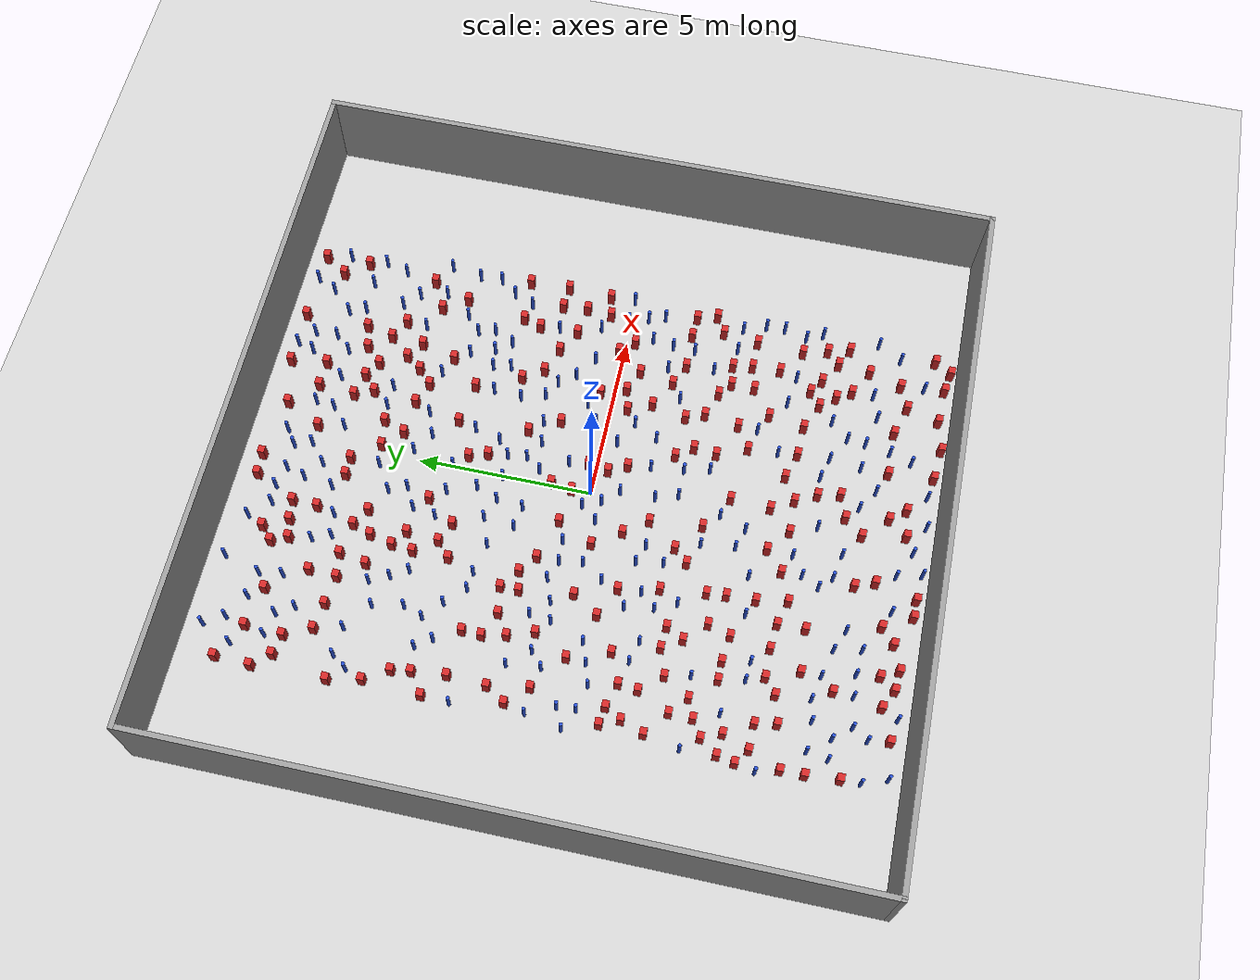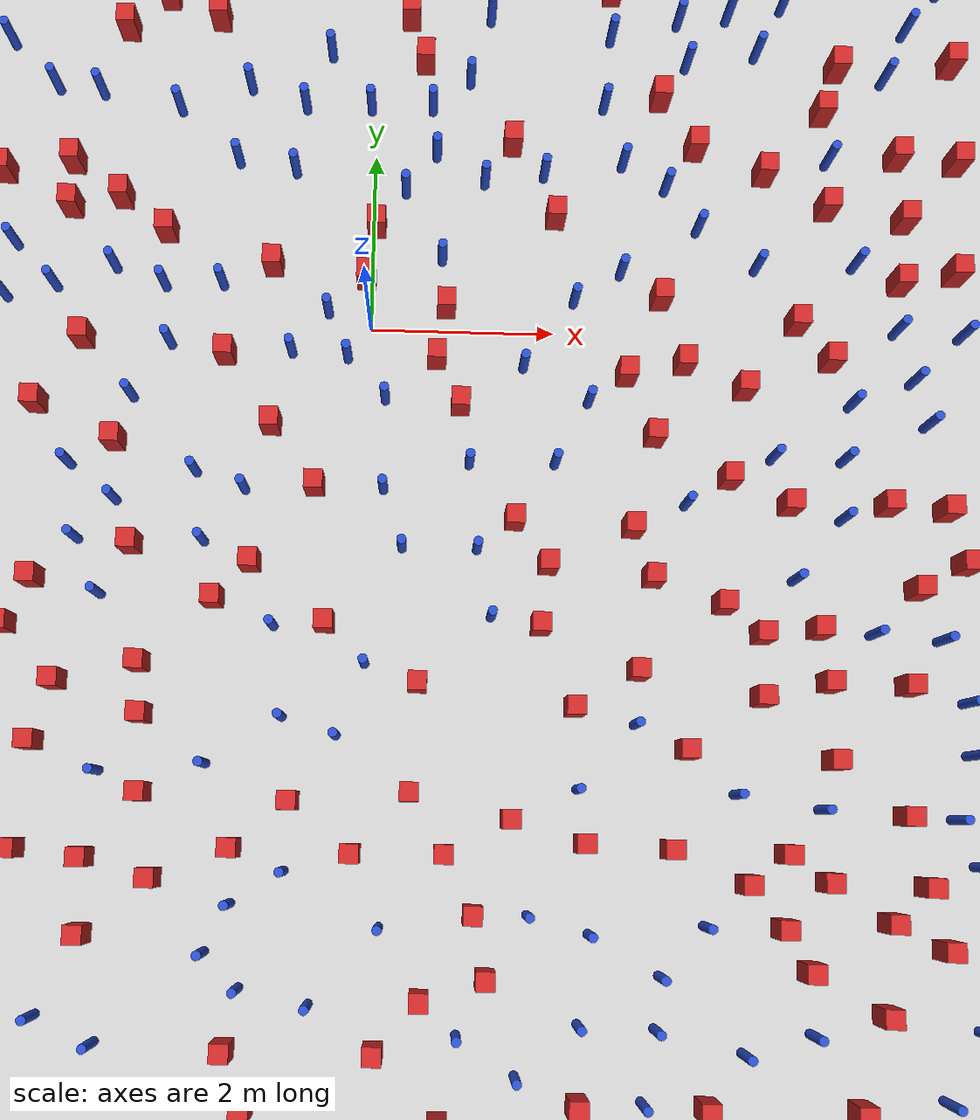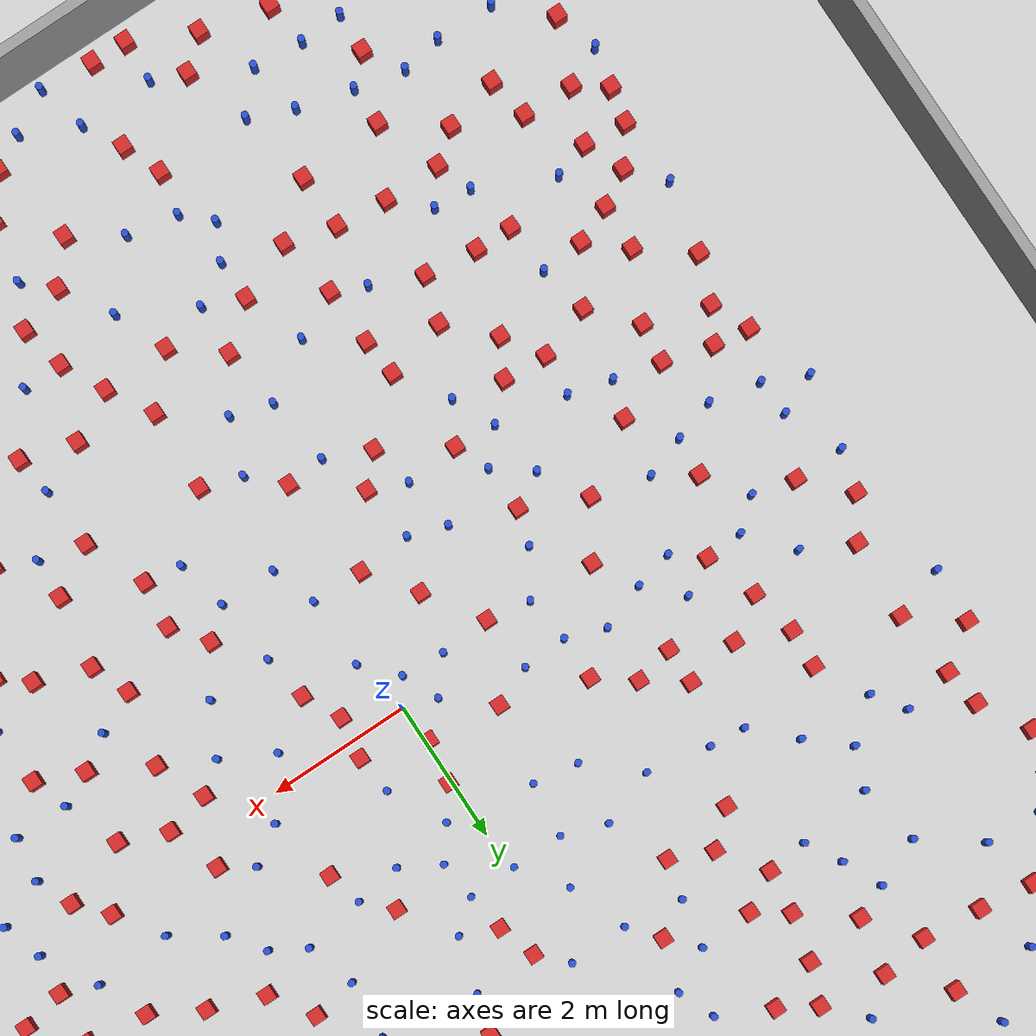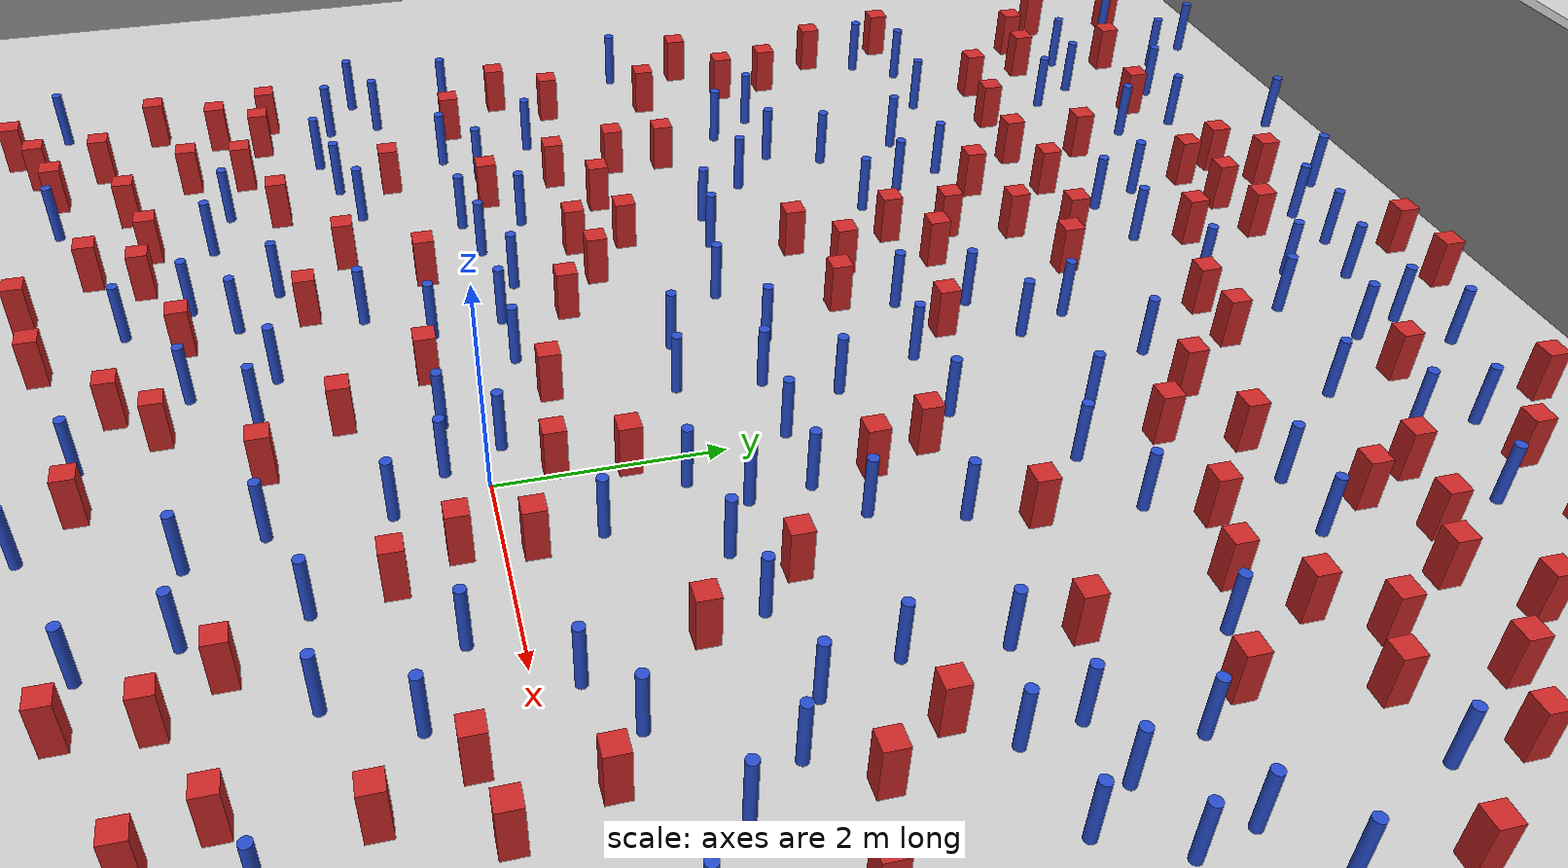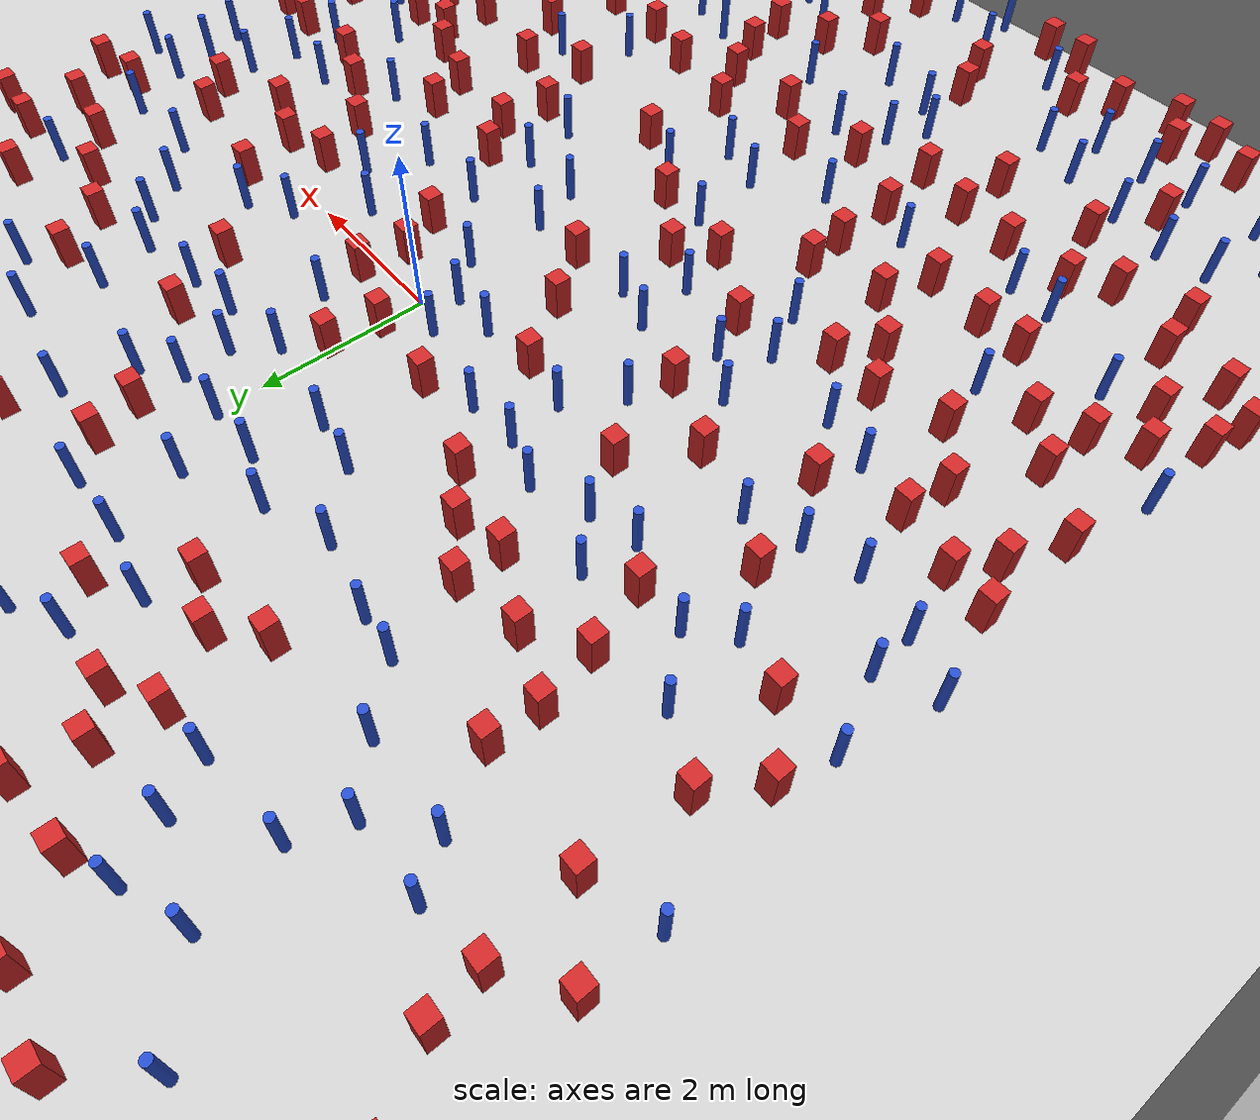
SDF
<sdf version="1.6">
 <world name="default">
  <light name="sun" type="directional">
   <pose>0 0 1000 0 -0 0</pose>
   <diffuse>0.8 0.8 0.8 1</diffuse>
   <specular>0.1 0.1 0.1 1</specular>
   <attenuation>
    <range>1000</range>
    <constant>0.9</constant>
    <linear>0.01</linear>
    <quadratic>0.001</quadratic>
   </attenuation>
   <direction>-0.5 0.5 -1</direction>
  </light>
  <model name="ground_plane">
   <static>1</static>
   <link name="link">
    <collision name="collision">
     <geometry><plane><normal>0 0 1</normal><size>100 100</size></plane></geometry>
     <surface><friction><ode><mu>100</mu><mu2>50</mu2></ode></friction></surface>
    </collision>
    <visual name="visual">
     <cast_shadows>0</cast_shadows>
     <geometry><plane><normal>0 0 1</normal><size>100 100</size></plane></geometry>
     <material>
      <ambient>1.0 1.0 1.0 1.0</ambient>
      <diffuse>0.8 0.8 0.8 1.0</diffuse>
      <specular>0.01 0.01 0.01 1.000000</specular>
     </material>
    </visual>
   </link>
  </model>
  <gravity>0 0 -9.8</gravity>
  <magnetic_field>6e-06 2.3e-05 -4.2e-05</magnetic_field>
  <atmosphere type="adiabatic"/>
  <physics name="default_physics" default="0" type="ode">
   <max_step_size>0.001</max_step_size>
   <real_time_factor>1</real_time_factor>
   <real_time_update_rate>1000</real_time_update_rate>
  </physics>
  <scene><ambient>0.4 0.4 0.4 1</ambient><background>0.7 0.7 0.7 1</background><shadows>1</shadows></scene>
  <spherical_coordinates>
   <surface_model>EARTH_WGS84</surface_model>
   <latitude_deg>0</latitude_deg>
   <longitude_deg>0</longitude_deg>
   <elevation>0</elevation>
   <heading_deg>0</heading_deg>
  </spherical_coordinates>
  <plugin name="gazebo_occupancy_map" filename="libgazebo_2Dmap_plugin.so">
   <map_resolution>0.05</map_resolution>
   <map_topic>generated_map</map_topic>
   <map_height>0.01</map_height>
   <map_size_x>50</map_size_x>
   <map_size_y>50</map_size_y>
  </plugin>
  <model name="NamedLocations">
   <static>true</static>
   <link name="DefaultStart"><pose>8.5 0 0 0 0 3.14</pose></link>
  </model>
  <model name="20x20_walls">
   <pose>0.044518 0.176112 0 0 -0 0</pose>
   <link name="Wall_1">
    <collision name="Wall_1_Collision">
     <geometry><box><size>20 0.15 2.5</size></box></geometry>
     <pose>0 0 1.25 0 -0 0</pose>
    </collision>
    <visual name="Wall_1_Visual">
     <pose>0 0 1.25 0 -0 0</pose>
     <geometry><box><size>20 0.15 2.5</size></box></geometry>
     <material>
      <script><uri>file://media/materials/scripts/gazebo.material</uri><name>Gazebo/Grey</name></script>
      <ambient>0.976471 0.992157 1 1</ambient>
     </material>
     <meta><layer>0</layer></meta>
    </visual>
    <pose>0 9.925 0 0 -0 0</pose>
   </link>
   <link name="Wall_3">
    <collision name="Wall_3_Collision">
     <geometry><box><size>20 0.15 2.5</size></box></geometry>
     <pose>0 0 1.25 0 -0 0</pose>
    </collision>
    <visual name="Wall_3_Visual">
     <pose>0 0 1.25 0 -0 0</pose>
     <geometry><box><size>20 0.15 2.5</size></box></geometry>
     <material>
      <script><uri>file://media/materials/scripts/gazebo.material</uri><name>Gazebo/Grey</name></script>
      <ambient>0.976471 0.992157 1 1</ambient>
     </material>
     <meta><layer>0</layer></meta>
    </visual>
    <pose>9.925 0 0 0 0 -1.5708</pose>
   </link>
   <link name="Wall_4">
    <collision name="Wall_4_Collision">
     <geometry><box><size>20 0.15 2.5</size></box></geometry>
     <pose>0 0 1.25 0 -0 0</pose>
    </collision>
    <visual name="Wall_4_Visual">
     <pose>0 0 1.25 0 -0 0</pose>
     <geometry><box><size>20 0.15 2.5</size></box></geometry>
     <material>
      <script><uri>file://media/materials/scripts/gazebo.material</uri><name>Gazebo/Grey</name></script>
      <ambient>0.976471 0.992157 1 1</ambient>
     </material>
     <meta><layer>0</layer></meta>
    </visual>
    <pose>0 -9.925 0 0 -0 3.14159</pose>
   </link>
   <link name="Wall_5">
    <collision name="Wall_5_Collision">
     <geometry><box><size>20 0.15 2.5</size></box></geometry>
     <pose>0 0 1.25 0 -0 0</pose>
    </collision>
    <visual name="Wall_5_Visual">
     <pose>0 0 1.25 0 -0 0</pose>
     <geometry><box><size>20 0.15 2.5</size></box></geometry>
     <material>
      <script><uri>file://media/materials/scripts/gazebo.material</uri><name>Gazebo/Grey</name></script>
      <ambient>0.976471 0.992157 1 1</ambient>
     </material>
     <meta><layer>0</layer></meta>
    </visual>
    <pose>-9.925 0 0 0 -0 1.5708</pose>
   </link>
   <static>1</static>
  </model>
  <model name="square_post_obstacle0">
   <static>true</static>
   <pose>-2.72196914421 -8.94715219982 1.91545236811e-07 -7.35059704564e-06 1.12565212e-07 2.39332434364e-05</pose>
   <link name="link">
    <pose>0 0 0.25 0 -0 0</pose>
    <inertial>
     <mass>100</mass>
     <inertia>
      <ixx>0.166667</ixx>
      <ixy>0</ixy>
      <ixz>0</ixz>
      <iyy>0.166667</iyy>
      <iyz>0</iyz>
      <izz>0.166667</izz>
     </inertia>
    </inertial>
    <collision name="collision"><geometry><box><size>.2 .2 .5</size></box></geometry></collision>
    <visual name="visual">
     <geometry><box><size>.2 .2 .5</size></box></geometry>
     <material>
      <script><name>Gazebo/Red</name><uri>file://media/materials/scripts/gazebo.material</uri></script>
     </material>
    </visual>
   </link>
  </model>
  <model name="square_post_obstacle1">
   <static>true</static>
   <pose>-5.60248485421 6.4889350293 1.91545236811e-07 -7.35059704564e-06 1.12565212e-07 2.39332434364e-05</pose>
   <link name="link">
    <pose>0 0 0.25 0 -0 0</pose>
    <inertial>
     <mass>100</mass>
     <inertia>
      <ixx>0.166667</ixx>
      <ixy>0</ixy>
      <ixz>0</ixz>
      <iyy>0.166667</iyy>
      <iyz>0</iyz>
      <izz>0.166667</izz>
     </inertia>
    </inertial>
    <collision name="collision"><geometry><box><size>.2 .2 .5</size></box></geometry></collision>
    <visual name="visual">
     <geometry><box><size>.2 .2 .5</size></box></geometry>
     <material>
      <script><name>Gazebo/Red</name><uri>file://media/materials/scripts/gazebo.material</uri></script>
     </material>
    </visual>
   </link>
  </model>
  <model name="pole_obstacle0">
   <static>true</static>
   <pose>0.76218171541 0.797468193769 7.38925637345e-09 -8.47170692799e-08 1.24976765008e-08 -1.7451309302e-07</pose>
   <link name="link">
    <pose>0 0 0.3 0 -0 0</pose>
    <inertial>
     <mass>1</mass>
     <inertia><ixx>0.145833</ixx><ixy>0</ixy><ixz>0</ixz><iyy>0.145833</iyy><iyz>0</iyz><izz>0.125</izz></inertia>
    </inertial>
    <collision name="collision">
     <geometry><cylinder><radius>0.05</radius><length>.6</length></cylinder></geometry>
    </collision>
    <visual name="visual">
     <geometry><cylinder><radius>0.05</radius><length>.6</length></cylinder></geometry>
     <material>
      <script><name>Gazebo/Blue</name><uri>file://media/materials/scripts/gazebo.material</uri></script>
     </material>
    </visual>
   </link>
  </model>
  <model name="square_post_obstacle2">
   <static>true</static>
   <pose>-6.33493677659 -2.16830192342 1.91545236811e-07 -7.35059704564e-06 1.12565212e-07 2.39332434364e-05</pose>
   <link name="link">
    <pose>0 0 0.25 0 -0 0</pose>
    <inertial>
     <mass>100</mass>
     <inertia>
      <ixx>0.166667</ixx>
      <ixy>0</ixy>
      <ixz>0</ixz>
      <iyy>0.166667</iyy>
      <iyz>0</iyz>
      <izz>0.166667</izz>
     </inertia>
    </inertial>
    <collision name="collision"><geometry><box><size>.2 .2 .5</size></box></geometry></collision>
    <visual name="visual">
     <geometry><box><size>.2 .2 .5</size></box></geometry>
     <material>
      <script><name>Gazebo/Red</name><uri>file://media/materials/scripts/gazebo.material</uri></script>
     </material>
    </visual>
   </link>
  </model>
  <model name="pole_obstacle1">
   <static>true</static>
   <pose>-4.78363985501 -9.33269308736 7.38925637345e-09 -8.471706928e-08 1.24976765081e-08 -1.74513093015e-07</pose>
   <link name="link">
    <pose>0 0 0.3 0 -0 0</pose>
    <inertial>
     <mass>1</mass>
     <inertia><ixx>0.145833</ixx><ixy>0</ixy><ixz>0</ixz><iyy>0.145833</iyy><iyz>0</iyz><izz>0.125</izz></inertia>
    </inertial>
    <collision name="collision">
     <geometry><cylinder><radius>0.05</radius><length>.6</length></cylinder></geometry>
    </collision>
    <visual name="visual">
     <geometry><cylinder><radius>0.05</radius><length>.6</length></cylinder></geometry>
     <material>
      <script><name>Gazebo/Blue</name><uri>file://media/materials/scripts/gazebo.material</uri></script>
     </material>
    </visual>
   </link>
  </model>
  <model name="square_post_obstacle3">
   <static>true</static>
   <pose>-3.41672989915 -4.59140950743 1.91545236811e-07 -7.35059704564e-06 1.12565212e-07 2.39332434364e-05</pose>
   <link name="link">
    <pose>0 0 0.25 0 -0 0</pose>
    <inertial>
     <mass>100</mass>
     <inertia>
      <ixx>0.166667</ixx>
      <ixy>0</ixy>
      <ixz>0</ixz>
      <iyy>0.166667</iyy>
      <iyz>0</iyz>
      <izz>0.166667</izz>
     </inertia>
    </inertial>
    <collision name="collision"><geometry><box><size>.2 .2 .5</size></box></geometry></collision>
    <visual name="visual">
     <geometry><box><size>.2 .2 .5</size></box></geometry>
     <material>
      <script><name>Gazebo/Red</name><uri>file://media/materials/scripts/gazebo.material</uri></script>
     </material>
    </visual>
   </link>
  </model>
  <model name="pole_obstacle2">
   <static>true</static>
   <pose>-4.02288362384 0.260550982332 7.38925637345e-09 -8.47170692799e-08 1.24976765058e-08 -1.74513093017e-07</pose>
   <link name="link">
    <pose>0 0 0.3 0 -0 0</pose>
    <inertial>
     <mass>1</mass>
     <inertia><ixx>0.145833</ixx><ixy>0</ixy><ixz>0</ixz><iyy>0.145833</iyy><iyz>0</iyz><izz>0.125</izz></inertia>
    </inertial>
    <collision name="collision">
     <geometry><cylinder><radius>0.05</radius><length>.6</length></cylinder></geometry>
    </collision>
    <visual name="visual">
     <geometry><cylinder><radius>0.05</radius><length>.6</length></cylinder></geometry>
     <material>
      <script><name>Gazebo/Blue</name><uri>file://media/materials/scripts/gazebo.material</uri></script>
     </material>
    </visual>
   </link>
  </model>
  <model name="pole_obstacle3">
   <static>true</static>
   <pose>0.190104860917 -1.80409300815 7.38925637345e-09 -8.471706928e-08 1.24976765082e-08 -1.74513093016e-07</pose>
   <link name="link">
    <pose>0 0 0.3 0 -0 0</pose>
    <inertial>
     <mass>1</mass>
     <inertia><ixx>0.145833</ixx><ixy>0</ixy><ixz>0</ixz><iyy>0.145833</iyy><iyz>0</iyz><izz>0.125</izz></inertia>
    </inertial>
    <collision name="collision">
     <geometry><cylinder><radius>0.05</radius><length>.6</length></cylinder></geometry>
    </collision>
    <visual name="visual">
     <geometry><cylinder><radius>0.05</radius><length>.6</length></cylinder></geometry>
     <material>
      <script><name>Gazebo/Blue</name><uri>file://media/materials/scripts/gazebo.material</uri></script>
     </material>
    </visual>
   </link>
  </model>
  <model name="square_post_obstacle4">
   <static>true</static>
   <pose>-2.28867185093 -8.56511000376 1.91545236811e-07 -7.35059704564e-06 1.12565212e-07 2.39332434364e-05</pose>
   <link name="link">
    <pose>0 0 0.25 0 -0 0</pose>
    <inertial>
     <mass>100</mass>
     <inertia>
      <ixx>0.166667</ixx>
      <ixy>0</ixy>
      <ixz>0</ixz>
      <iyy>0.166667</iyy>
      <iyz>0</iyz>
      <izz>0.166667</izz>
     </inertia>
    </inertial>
    <collision name="collision"><geometry><box><size>.2 .2 .5</size></box></geometry></collision>
    <visual name="visual">
     <geometry><box><size>.2 .2 .5</size></box></geometry>
     <material>
      <script><name>Gazebo/Red</name><uri>file://media/materials/scripts/gazebo.material</uri></script>
     </material>
    </visual>
   </link>
  </model>
  <model name="square_post_obstacle5">
   <static>true</static>
   <pose>5.80061955398 6.0174033591 1.91545236811e-07 -7.35059704564e-06 1.12565212e-07 2.39332434364e-05</pose>
   <link name="link">
    <pose>0 0 0.25 0 -0 0</pose>
    <inertial>
     <mass>100</mass>
     <inertia>
      <ixx>0.166667</ixx>
      <ixy>0</ixy>
      <ixz>0</ixz>
      <iyy>0.166667</iyy>
      <iyz>0</iyz>
      <izz>0.166667</izz>
     </inertia>
    </inertial>
    <collision name="collision"><geometry><box><size>.2 .2 .5</size></box></geometry></collision>
    <visual name="visual">
     <geometry><box><size>.2 .2 .5</size></box></geometry>
     <material>
      <script><name>Gazebo/Red</name><uri>file://media/materials/scripts/gazebo.material</uri></script>
     </material>
    </visual>
   </link>
  </model>
  <model name="square_post_obstacle6">
   <static>true</static>
   <pose>1.29093593183 -8.78116304104 1.91545236811e-07 -7.35059704564e-06 1.12565212e-07 2.39332434364e-05</pose>
   <link name="link">
    <pose>0 0 0.25 0 -0 0</pose>
    <inertial>
     <mass>100</mass>
     <inertia>
      <ixx>0.166667</ixx>
      <ixy>0</ixy>
      <ixz>0</ixz>
      <iyy>0.166667</iyy>
      <iyz>0</iyz>
      <izz>0.166667</izz>
     </inertia>
    </inertial>
    <collision name="collision"><geometry><box><size>.2 .2 .5</size></box></geometry></collision>
    <visual name="visual">
     <geometry><box><size>.2 .2 .5</size></box></geometry>
     <material>
      <script><name>Gazebo/Red</name><uri>file://media/materials/scripts/gazebo.material</uri></script>
     </material>
    </visual>
   </link>
  </model>
  <model name="pole_obstacle4">
   <static>true</static>
   <pose>6.13488294941 -3.3037223995 7.38925637345e-09 -8.47170692798e-08 1.24976764937e-08 -1.74513093023e-07</pose>
   <link name="link">
    <pose>0 0 0.3 0 -0 0</pose>
    <inertial>
     <mass>1</mass>
     <inertia><ixx>0.145833</ixx><ixy>0</ixy><ixz>0</ixz><iyy>0.145833</iyy><iyz>0</iyz><izz>0.125</izz></inertia>
    </inertial>
    <collision name="collision">
     <geometry><cylinder><radius>0.05</radius><length>.6</length></cylinder></geometry>
    </collision>
    <visual name="visual">
     <geometry><cylinder><radius>0.05</radius><length>.6</length></cylinder></geometry>
     <material>
      <script><name>Gazebo/Blue</name><uri>file://media/materials/scripts/gazebo.material</uri></script>
     </material>
    </visual>
   </link>
  </model>
  <model name="pole_obstacle5">
   <static>true</static>
   <pose>4.72717917194 -7.37181326376 7.38925637345e-09 -8.47170692796e-08 1.24976764786e-08 -1.74513093032e-07</pose>
   <link name="link">
    <pose>0 0 0.3 0 -0 0</pose>
    <inertial>
     <mass>1</mass>
     <inertia><ixx>0.145833</ixx><ixy>0</ixy><ixz>0</ixz><iyy>0.145833</iyy><iyz>0</iyz><izz>0.125</izz></inertia>
    </inertial>
    <collision name="collision">
     <geometry><cylinder><radius>0.05</radius><length>.6</length></cylinder></geometry>
    </collision>
    <visual name="visual">
     <geometry><cylinder><radius>0.05</radius><length>.6</length></cylinder></geometry>
     <material>
      <script><name>Gazebo/Blue</name><uri>file://media/materials/scripts/gazebo.material</uri></script>
     </material>
    </visual>
   </link>
  </model>
  <model name="square_post_obstacle7">
   <static>true</static>
   <pose>-6.72281977313 4.81564942653 1.91545236811e-07 -7.35059704564e-06 1.12565212e-07 2.39332434364e-05</pose>
   <link name="link">
    <pose>0 0 0.25 0 -0 0</pose>
    <inertial>
     <mass>100</mass>
     <inertia>
      <ixx>0.166667</ixx>
      <ixy>0</ixy>
      <ixz>0</ixz>
      <iyy>0.166667</iyy>
      <iyz>0</iyz>
      <izz>0.166667</izz>
     </inertia>
    </inertial>
    <collision name="collision"><geometry><box><size>.2 .2 .5</size></box></geometry></collision>
    <visual name="visual">
     <geometry><box><size>.2 .2 .5</size></box></geometry>
     <material>
      <script><name>Gazebo/Red</name><uri>file://media/materials/scripts/gazebo.material</uri></script>
     </material>
    </visual>
   </link>
  </model>
  <model name="square_post_obstacle8">
   <static>true</static>
   <pose>4.5278132848 -8.37382198587 1.91545236811e-07 -7.35059704564e-06 1.12565212e-07 2.39332434364e-05</pose>
   <link name="link">
    <pose>0 0 0.25 0 -0 0</pose>
    <inertial>
     <mass>100</mass>
     <inertia>
      <ixx>0.166667</ixx>
      <ixy>0</ixy>
      <ixz>0</ixz>
      <iyy>0.166667</iyy>
      <iyz>0</iyz>
      <izz>0.166667</izz>
     </inertia>
    </inertial>
    <collision name="collision"><geometry><box><size>.2 .2 .5</size></box></geometry></collision>
    <visual name="visual">
     <geometry><box><size>.2 .2 .5</size></box></geometry>
     <material>
      <script><name>Gazebo/Red</name><uri>file://media/materials/scripts/gazebo.material</uri></script>
     </material>
    </visual>
   </link>
  </model>
  <model name="pole_obstacle6">
   <static>true</static>
   <pose>-5.66873293021 -7.7020765996 7.38925637345e-09 -8.47170692796e-08 1.24976764786e-08 -1.74513093032e-07</pose>
   <link name="link">
    <pose>0 0 0.3 0 -0 0</pose>
    <inertial>
     <mass>1</mass>
     <inertia><ixx>0.145833</ixx><ixy>0</ixy><ixz>0</ixz><iyy>0.145833</iyy><iyz>0</iyz><izz>0.125</izz></inertia>
    </inertial>
    <collision name="collision">
     <geometry><cylinder><radius>0.05</radius><length>.6</length></cylinder></geometry>
    </collision>
    <visual name="visual">
     <geometry><cylinder><radius>0.05</radius><length>.6</length></cylinder></geometry>
     <material>
      <script><name>Gazebo/Blue</name><uri>file://media/materials/scripts/gazebo.material</uri></script>
     </material>
    </visual>
   </link>
  </model>
  <model name="pole_obstacle7">
   <static>true</static>
   <pose>4.88102241531 8.92178213815 7.38925637345e-09 -8.471706928e-08 1.24976765081e-08 -1.74513093015e-07</pose>
   <link name="link">
    <pose>0 0 0.3 0 -0 0</pose>
    <inertial>
     <mass>1</mass>
     <inertia><ixx>0.145833</ixx><ixy>0</ixy><ixz>0</ixz><iyy>0.145833</iyy><iyz>0</iyz><izz>0.125</izz></inertia>
    </inertial>
    <collision name="collision">
     <geometry><cylinder><radius>0.05</radius><length>.6</length></cylinder></geometry>
    </collision>
    <visual name="visual">
     <geometry><cylinder><radius>0.05</radius><length>.6</length></cylinder></geometry>
     <material>
      <script><name>Gazebo/Blue</name><uri>file://media/materials/scripts/gazebo.material</uri></script>
     </material>
    </visual>
   </link>
  </model>
  <model name="square_post_obstacle9">
   <static>true</static>
   <pose>-1.83106728129 -9.37195431687 1.91545236811e-07 -7.35059704564e-06 1.12565212e-07 2.39332434364e-05</pose>
   <link name="link">
    <pose>0 0 0.25 0 -0 0</pose>
    <inertial>
     <mass>100</mass>
     <inertia>
      <ixx>0.166667</ixx>
      <ixy>0</ixy>
      <ixz>0</ixz>
      <iyy>0.166667</iyy>
      <iyz>0</iyz>
      <izz>0.166667</izz>
     </inertia>
    </inertial>
    <collision name="collision"><geometry><box><size>.2 .2 .5</size></box></geometry></collision>
    <visual name="visual">
     <geometry><box><size>.2 .2 .5</size></box></geometry>
     <material>
      <script><name>Gazebo/Red</name><uri>file://media/materials/scripts/gazebo.material</uri></script>
     </material>
    </visual>
   </link>
  </model>
  <model name="square_post_obstacle10">
   <static>true</static>
   <pose>-1.79566469293 3.57648062967 1.91545236811e-07 -7.35059704564e-06 1.12565212e-07 2.39332434364e-05</pose>
   <link name="link">
    <pose>0 0 0.25 0 -0 0</pose>
    <inertial>
     <mass>100</mass>
     <inertia>
      <ixx>0.166667</ixx>
      <ixy>0</ixy>
      <ixz>0</ixz>
      <iyy>0.166667</iyy>
      <iyz>0</iyz>
      <izz>0.166667</izz>
     </inertia>
    </inertial>
    <collision name="collision"><geometry><box><size>.2 .2 .5</size></box></geometry></collision>
    <visual name="visual">
     <geometry><box><size>.2 .2 .5</size></box></geometry>
     <material>
      <script><name>Gazebo/Red</name><uri>file://media/materials/scripts/gazebo.material</uri></script>
     </material>
    </visual>
   </link>
  </model>
  <model name="square_post_obstacle11">
   <static>true</static>
   <pose>4.90303084375 -5.84005324019 1.91545236811e-07 -7.35059704564e-06 1.12565212e-07 2.39332434364e-05</pose>
   <link name="link">
    <pose>0 0 0.25 0 -0 0</pose>
    <inertial>
     <mass>100</mass>
     <inertia>
      <ixx>0.166667</ixx>
      <ixy>0</ixy>
      <ixz>0</ixz>
      <iyy>0.166667</iyy>
      <iyz>0</iyz>
      <izz>0.166667</izz>
     </inertia>
    </inertial>
    <collision name="collision"><geometry><box><size>.2 .2 .5</size></box></geometry></collision>
    <visual name="visual">
     <geometry><box><size>.2 .2 .5</size></box></geometry>
     <material>
      <script><name>Gazebo/Red</name><uri>file://media/materials/scripts/gazebo.material</uri></script>
     </material>
    </visual>
   </link>
  </model>
  <model name="square_post_obstacle12">
   <static>true</static>
   <pose>2.73245616664 6.93386750951 1.91545236811e-07 -7.35059704564e-06 1.12565212e-07 2.39332434364e-05</pose>
   <link name="link">
    <pose>0 0 0.25 0 -0 0</pose>
    <inertial>
     <mass>100</mass>
     <inertia>
      <ixx>0.166667</ixx>
      <ixy>0</ixy>
      <ixz>0</ixz>
      <iyy>0.166667</iyy>
      <iyz>0</iyz>
      <izz>0.166667</izz>
     </inertia>
    </inertial>
    <collision name="collision"><geometry><box><size>.2 .2 .5</size></box></geometry></collision>
    <visual name="visual">
     <geometry><box><size>.2 .2 .5</size></box></geometry>
     <material>
      <script><name>Gazebo/Red</name><uri>file://media/materials/scripts/gazebo.material</uri></script>
     </material>
    </visual>
   </link>
  </model>
  <model name="square_post_obstacle13">
   <static>true</static>
   <pose>2.26537077516 -4.10136588118 1.91545236811e-07 -7.35059704564e-06 1.12565212e-07 2.39332434364e-05</pose>
   <link name="link">
    <pose>0 0 0.25 0 -0 0</pose>
    <inertial>
     <mass>100</mass>
     <inertia>
      <ixx>0.166667</ixx>
      <ixy>0</ixy>
      <ixz>0</ixz>
      <iyy>0.166667</iyy>
      <iyz>0</iyz>
      <izz>0.166667</izz>
     </inertia>
    </inertial>
    <collision name="collision"><geometry><box><size>.2 .2 .5</size></box></geometry></collision>
    <visual name="visual">
     <geometry><box><size>.2 .2 .5</size></box></geometry>
     <material>
      <script><name>Gazebo/Red</name><uri>file://media/materials/scripts/gazebo.material</uri></script>
     </material>
    </visual>
   </link>
  </model>
  <model name="pole_obstacle8">
   <static>true</static>
   <pose>2.06833844879 7.92089976676 7.38925637345e-09 -8.47170692798e-08 1.24976765033e-08 -1.74513093019e-07</pose>
   <link name="link">
    <pose>0 0 0.3 0 -0 0</pose>
    <inertial>
     <mass>1</mass>
     <inertia><ixx>0.145833</ixx><ixy>0</ixy><ixz>0</ixz><iyy>0.145833</iyy><iyz>0</iyz><izz>0.125</izz></inertia>
    </inertial>
    <collision name="collision">
     <geometry><cylinder><radius>0.05</radius><length>.6</length></cylinder></geometry>
    </collision>
    <visual name="visual">
     <geometry><cylinder><radius>0.05</radius><length>.6</length></cylinder></geometry>
     <material>
      <script><name>Gazebo/Blue</name><uri>file://media/materials/scripts/gazebo.material</uri></script>
     </material>
    </visual>
   </link>
  </model>
  <model name="square_post_obstacle14">
   <static>true</static>
   <pose>3.13486374793 6.18309441416 1.91545236811e-07 -7.35059704564e-06 1.12565212e-07 2.39332434364e-05</pose>
   <link name="link">
    <pose>0 0 0.25 0 -0 0</pose>
    <inertial>
     <mass>100</mass>
     <inertia>
      <ixx>0.166667</ixx>
      <ixy>0</ixy>
      <ixz>0</ixz>
      <iyy>0.166667</iyy>
      <iyz>0</iyz>
      <izz>0.166667</izz>
     </inertia>
    </inertial>
    <collision name="collision"><geometry><box><size>.2 .2 .5</size></box></geometry></collision>
    <visual name="visual">
     <geometry><box><size>.2 .2 .5</size></box></geometry>
     <material>
      <script><name>Gazebo/Red</name><uri>file://media/materials/scripts/gazebo.material</uri></script>
     </material>
    </visual>
   </link>
  </model>
  <model name="square_post_obstacle15">
   <static>true</static>
   <pose>-2.38048660059 3.82549536117 1.91545236811e-07 -7.35059704564e-06 1.12565212e-07 2.39332434364e-05</pose>
   <link name="link">
    <pose>0 0 0.25 0 -0 0</pose>
    <inertial>
     <mass>100</mass>
     <inertia>
      <ixx>0.166667</ixx>
      <ixy>0</ixy>
      <ixz>0</ixz>
      <iyy>0.166667</iyy>
      <iyz>0</iyz>
      <izz>0.166667</izz>
     </inertia>
    </inertial>
    <collision name="collision"><geometry><box><size>.2 .2 .5</size></box></geometry></collision>
    <visual name="visual">
     <geometry><box><size>.2 .2 .5</size></box></geometry>
     <material>
      <script><name>Gazebo/Red</name><uri>file://media/materials/scripts/gazebo.material</uri></script>
     </material>
    </visual>
   </link>
  </model>
  <model name="square_post_obstacle16">
   <static>true</static>
   <pose>3.64107070523 -8.11280772102 1.91545236811e-07 -7.35059704564e-06 1.12565212e-07 2.39332434364e-05</pose>
   <link name="link">
    <pose>0 0 0.25 0 -0 0</pose>
    <inertial>
     <mass>100</mass>
     <inertia>
      <ixx>0.166667</ixx>
      <ixy>0</ixy>
      <ixz>0</ixz>
      <iyy>0.166667</iyy>
      <iyz>0</iyz>
      <izz>0.166667</izz>
     </inertia>
    </inertial>
    <collision name="collision"><geometry><box><size>.2 .2 .5</size></box></geometry></collision>
    <visual name="visual">
     <geometry><box><size>.2 .2 .5</size></box></geometry>
     <material>
      <script><name>Gazebo/Red</name><uri>file://media/materials/scripts/gazebo.material</uri></script>
     </material>
    </visual>
   </link>
  </model>
  <model name="pole_obstacle9">
   <static>true</static>
   <pose>5.41547490436 -3.25559603564 7.38925637345e-09 -8.47170692798e-08 1.24976764937e-08 -1.74513093023e-07</pose>
   <link name="link">
    <pose>0 0 0.3 0 -0 0</pose>
    <inertial>
     <mass>1</mass>
     <inertia><ixx>0.145833</ixx><ixy>0</ixy><ixz>0</ixz><iyy>0.145833</iyy><iyz>0</iyz><izz>0.125</izz></inertia>
    </inertial>
    <collision name="collision">
     <geometry><cylinder><radius>0.05</radius><length>.6</length></cylinder></geometry>
    </collision>
    <visual name="visual">
     <geometry><cylinder><radius>0.05</radius><length>.6</length></cylinder></geometry>
     <material>
      <script><name>Gazebo/Blue</name><uri>file://media/materials/scripts/gazebo.material</uri></script>
     </material>
    </visual>
   </link>
  </model>
  <model name="square_post_obstacle17">
   <static>true</static>
   <pose>-2.24844355301 -5.09677401196 1.91545236811e-07 -7.35059704564e-06 1.12565212e-07 2.39332434364e-05</pose>
   <link name="link">
    <pose>0 0 0.25 0 -0 0</pose>
    <inertial>
     <mass>100</mass>
     <inertia>
      <ixx>0.166667</ixx>
      <ixy>0</ixy>
      <ixz>0</ixz>
      <iyy>0.166667</iyy>
      <iyz>0</iyz>
      <izz>0.166667</izz>
     </inertia>
    </inertial>
    <collision name="collision"><geometry><box><size>.2 .2 .5</size></box></geometry></collision>
    <visual name="visual">
     <geometry><box><size>.2 .2 .5</size></box></geometry>
     <material>
      <script><name>Gazebo/Red</name><uri>file://media/materials/scripts/gazebo.material</uri></script>
     </material>
    </visual>
   </link>
  </model>
  <model name="square_post_obstacle18">
   <static>true</static>
   <pose>-1.08649604366 0.678129804485 1.91545236811e-07 -7.35059704564e-06 1.12565212e-07 2.39332434364e-05</pose>
   <link name="link">
    <pose>0 0 0.25 0 -0 0</pose>
    <inertial>
     <mass>100</mass>
     <inertia>
      <ixx>0.166667</ixx>
      <ixy>0</ixy>
      <ixz>0</ixz>
      <iyy>0.166667</iyy>
      <iyz>0</iyz>
      <izz>0.166667</izz>
     </inertia>
    </inertial>
    <collision name="collision"><geometry><box><size>.2 .2 .5</size></box></geometry></collision>
    <visual name="visual">
     <geometry><box><size>.2 .2 .5</size></box></geometry>
     <material>
      <script><name>Gazebo/Red</name><uri>file://media/materials/scripts/gazebo.material</uri></script>
     </material>
    </visual>
   </link>
  </model>
  <model name="pole_obstacle10">
   <static>true</static>
   <pose>4.20949864032 0.770058361071 7.38925637345e-09 -8.47170692799e-08 1.24976765038e-08 -1.74513093018e-07</pose>
   <link name="link">
    <pose>0 0 0.3 0 -0 0</pose>
    <inertial>
     <mass>1</mass>
     <inertia><ixx>0.145833</ixx><ixy>0</ixy><ixz>0</ixz><iyy>0.145833</iyy><iyz>0</iyz><izz>0.125</izz></inertia>
    </inertial>
    <collision name="collision">
     <geometry><cylinder><radius>0.05</radius><length>.6</length></cylinder></geometry>
    </collision>
    <visual name="visual">
     <geometry><cylinder><radius>0.05</radius><length>.6</length></cylinder></geometry>
     <material>
      <script><name>Gazebo/Blue</name><uri>file://media/materials/scripts/gazebo.material</uri></script>
     </material>
    </visual>
   </link>
  </model>
  <model name="square_post_obstacle19">
   <static>true</static>
   <pose>-3.42885709103 -9.20270909468 1.91545236811e-07 -7.35059704564e-06 1.12565212e-07 2.39332434364e-05</pose>
   <link name="link">
    <pose>0 0 0.25 0 -0 0</pose>
    <inertial>
     <mass>100</mass>
     <inertia>
      <ixx>0.166667</ixx>
      <ixy>0</ixy>
      <ixz>0</ixz>
      <iyy>0.166667</iyy>
      <iyz>0</iyz>
      <izz>0.166667</izz>
     </inertia>
    </inertial>
    <collision name="collision"><geometry><box><size>.2 .2 .5</size></box></geometry></collision>
    <visual name="visual">
     <geometry><box><size>.2 .2 .5</size></box></geometry>
     <material>
      <script><name>Gazebo/Red</name><uri>file://media/materials/scripts/gazebo.material</uri></script>
     </material>
    </visual>
   </link>
  </model>
  <model name="pole_obstacle11">
   <static>true</static>
   <pose>-2.5680316428 -0.844122464464 7.38925637345e-09 -8.471706928e-08 1.24976765177e-08 -1.74513093012e-07</pose>
   <link name="link">
    <pose>0 0 0.3 0 -0 0</pose>
    <inertial>
     <mass>1</mass>
     <inertia><ixx>0.145833</ixx><ixy>0</ixy><ixz>0</ixz><iyy>0.145833</iyy><iyz>0</iyz><izz>0.125</izz></inertia>
    </inertial>
    <collision name="collision">
     <geometry><cylinder><radius>0.05</radius><length>.6</length></cylinder></geometry>
    </collision>
    <visual name="visual">
     <geometry><cylinder><radius>0.05</radius><length>.6</length></cylinder></geometry>
     <material>
      <script><name>Gazebo/Blue</name><uri>file://media/materials/scripts/gazebo.material</uri></script>
     </material>
    </visual>
   </link>
  </model>
  <model name="square_post_obstacle20">
   <static>true</static>
   <pose>-6.6940815268 -8.06986607838 1.91545236811e-07 -7.35059704564e-06 1.12565212e-07 2.39332434364e-05</pose>
   <link name="link">
    <pose>0 0 0.25 0 -0 0</pose>
    <inertial>
     <mass>100</mass>
     <inertia>
      <ixx>0.166667</ixx>
      <ixy>0</ixy>
      <ixz>0</ixz>
      <iyy>0.166667</iyy>
      <iyz>0</iyz>
      <izz>0.166667</izz>
     </inertia>
    </inertial>
    <collision name="collision"><geometry><box><size>.2 .2 .5</size></box></geometry></collision>
    <visual name="visual">
     <geometry><box><size>.2 .2 .5</size></box></geometry>
     <material>
      <script><name>Gazebo/Red</name><uri>file://media/materials/scripts/gazebo.material</uri></script>
     </material>
    </visual>
   </link>
  </model>
  <model name="pole_obstacle12">
   <static>true</static>
   <pose>-0.427760057197 6.07266517939 7.38925637345e-09 -8.471706928e-08 1.24976765079e-08 -1.74513093015e-07</pose>
   <link name="link">
    <pose>0 0 0.3 0 -0 0</pose>
    <inertial>
     <mass>1</mass>
     <inertia><ixx>0.145833</ixx><ixy>0</ixy><ixz>0</ixz><iyy>0.145833</iyy><iyz>0</iyz><izz>0.125</izz></inertia>
    </inertial>
    <collision name="collision">
     <geometry><cylinder><radius>0.05</radius><length>.6</length></cylinder></geometry>
    </collision>
    <visual name="visual">
     <geometry><cylinder><radius>0.05</radius><length>.6</length></cylinder></geometry>
     <material>
      <script><name>Gazebo/Blue</name><uri>file://media/materials/scripts/gazebo.material</uri></script>
     </material>
    </visual>
   </link>
  </model>
  <model name="square_post_obstacle21">
   <static>true</static>
   <pose>3.68544946964 6.7974008489 1.91545236811e-07 -7.35059704564e-06 1.12565212e-07 2.39332434364e-05</pose>
   <link name="link">
    <pose>0 0 0.25 0 -0 0</pose>
    <inertial>
     <mass>100</mass>
     <inertia>
      <ixx>0.166667</ixx>
      <ixy>0</ixy>
      <ixz>0</ixz>
      <iyy>0.166667</iyy>
      <iyz>0</iyz>
      <izz>0.166667</izz>
     </inertia>
    </inertial>
    <collision name="collision"><geometry><box><size>.2 .2 .5</size></box></geometry></collision>
    <visual name="visual">
     <geometry><box><size>.2 .2 .5</size></box></geometry>
     <material>
      <script><name>Gazebo/Red</name><uri>file://media/materials/scripts/gazebo.material</uri></script>
     </material>
    </visual>
   </link>
  </model>
  <model name="pole_obstacle13">
   <static>true</static>
   <pose>-4.0118841569 -5.26021638834 7.38925637345e-09 -8.47170692795e-08 1.24976764731e-08 -1.74513093035e-07</pose>
   <link name="link">
    <pose>0 0 0.3 0 -0 0</pose>
    <inertial>
     <mass>1</mass>
     <inertia><ixx>0.145833</ixx><ixy>0</ixy><ixz>0</ixz><iyy>0.145833</iyy><iyz>0</iyz><izz>0.125</izz></inertia>
    </inertial>
    <collision name="collision">
     <geometry><cylinder><radius>0.05</radius><length>.6</length></cylinder></geometry>
    </collision>
    <visual name="visual">
     <geometry><cylinder><radius>0.05</radius><length>.6</length></cylinder></geometry>
     <material>
      <script><name>Gazebo/Blue</name><uri>file://media/materials/scripts/gazebo.material</uri></script>
     </material>
    </visual>
   </link>
  </model>
  <model name="square_post_obstacle22">
   <static>true</static>
   <pose>-2.28275646718 -4.28150279301 1.91545236811e-07 -7.35059704564e-06 1.12565212e-07 2.39332434364e-05</pose>
   <link name="link">
    <pose>0 0 0.25 0 -0 0</pose>
    <inertial>
     <mass>100</mass>
     <inertia>
      <ixx>0.166667</ixx>
      <ixy>0</ixy>
      <ixz>0</ixz>
      <iyy>0.166667</iyy>
      <iyz>0</iyz>
      <izz>0.166667</izz>
     </inertia>
    </inertial>
    <collision name="collision"><geometry><box><size>.2 .2 .5</size></box></geometry></collision>
    <visual name="visual">
     <geometry><box><size>.2 .2 .5</size></box></geometry>
     <material>
      <script><name>Gazebo/Red</name><uri>file://media/materials/scripts/gazebo.material</uri></script>
     </material>
    </visual>
   </link>
  </model>
  <model name="pole_obstacle14">
   <static>true</static>
   <pose>5.28901740796 0.820832074748 7.38925637345e-09 -8.47170692799e-08 1.24976765038e-08 -1.74513093018e-07</pose>
   <link name="link">
    <pose>0 0 0.3 0 -0 0</pose>
    <inertial>
     <mass>1</mass>
     <inertia><ixx>0.145833</ixx><ixy>0</ixy><ixz>0</ixz><iyy>0.145833</iyy><iyz>0</iyz><izz>0.125</izz></inertia>
    </inertial>
    <collision name="collision">
     <geometry><cylinder><radius>0.05</radius><length>.6</length></cylinder></geometry>
    </collision>
    <visual name="visual">
     <geometry><cylinder><radius>0.05</radius><length>.6</length></cylinder></geometry>
     <material>
      <script><name>Gazebo/Blue</name><uri>file://media/materials/scripts/gazebo.material</uri></script>
     </material>
    </visual>
   </link>
  </model>
  <model name="pole_obstacle15">
   <static>true</static>
   <pose>-3.21810793898 -7.3811355036 7.38925637345e-09 -8.47170692798e-08 1.24976765033e-08 -1.74513093019e-07</pose>
   <link name="link">
    <pose>0 0 0.3 0 -0 0</pose>
    <inertial>
     <mass>1</mass>
     <inertia><ixx>0.145833</ixx><ixy>0</ixy><ixz>0</ixz><iyy>0.145833</iyy><iyz>0</iyz><izz>0.125</izz></inertia>
    </inertial>
    <collision name="collision">
     <geometry><cylinder><radius>0.05</radius><length>.6</length></cylinder></geometry>
    </collision>
    <visual name="visual">
     <geometry><cylinder><radius>0.05</radius><length>.6</length></cylinder></geometry>
     <material>
      <script><name>Gazebo/Blue</name><uri>file://media/materials/scripts/gazebo.material</uri></script>
     </material>
    </visual>
   </link>
  </model>
  <model name="pole_obstacle16">
   <static>true</static>
   <pose>-3.59063591061 2.70652218727 7.38925637345e-09 -8.471706928e-08 1.24976765098e-08 -1.74513093016e-07</pose>
   <link name="link">
    <pose>0 0 0.3 0 -0 0</pose>
    <inertial>
     <mass>1</mass>
     <inertia><ixx>0.145833</ixx><ixy>0</ixy><ixz>0</ixz><iyy>0.145833</iyy><iyz>0</iyz><izz>0.125</izz></inertia>
    </inertial>
    <collision name="collision">
     <geometry><cylinder><radius>0.05</radius><length>.6</length></cylinder></geometry>
    </collision>
    <visual name="visual">
     <geometry><cylinder><radius>0.05</radius><length>.6</length></cylinder></geometry>
     <material>
      <script><name>Gazebo/Blue</name><uri>file://media/materials/scripts/gazebo.material</uri></script>
     </material>
    </visual>
   </link>
  </model>
  <model name="square_post_obstacle23">
   <static>true</static>
   <pose>-4.16827739054 -4.4960188859 1.91545236811e-07 -7.35059704564e-06 1.12565212e-07 2.39332434364e-05</pose>
   <link name="link">
    <pose>0 0 0.25 0 -0 0</pose>
    <inertial>
     <mass>100</mass>
     <inertia>
      <ixx>0.166667</ixx>
      <ixy>0</ixy>
      <ixz>0</ixz>
      <iyy>0.166667</iyy>
      <iyz>0</iyz>
      <izz>0.166667</izz>
     </inertia>
    </inertial>
    <collision name="collision"><geometry><box><size>.2 .2 .5</size></box></geometry></collision>
    <visual name="visual">
     <geometry><box><size>.2 .2 .5</size></box></geometry>
     <material>
      <script><name>Gazebo/Red</name><uri>file://media/materials/scripts/gazebo.material</uri></script>
     </material>
    </visual>
   </link>
  </model>
  <model name="pole_obstacle17">
   <static>true</static>
   <pose>-1.41972756546 2.76100468626 7.38925637345e-09 -8.47170692799e-08 1.24976765053e-08 -1.74513093017e-07</pose>
   <link name="link">
    <pose>0 0 0.3 0 -0 0</pose>
    <inertial>
     <mass>1</mass>
     <inertia><ixx>0.145833</ixx><ixy>0</ixy><ixz>0</ixz><iyy>0.145833</iyy><iyz>0</iyz><izz>0.125</izz></inertia>
    </inertial>
    <collision name="collision">
     <geometry><cylinder><radius>0.05</radius><length>.6</length></cylinder></geometry>
    </collision>
    <visual name="visual">
     <geometry><cylinder><radius>0.05</radius><length>.6</length></cylinder></geometry>
     <material>
      <script><name>Gazebo/Blue</name><uri>file://media/materials/scripts/gazebo.material</uri></script>
     </material>
    </visual>
   </link>
  </model>
  <model name="square_post_obstacle24">
   <static>true</static>
   <pose>0.687255433754 5.64067073542 1.91545236811e-07 -7.35059704564e-06 1.12565212e-07 2.39332434364e-05</pose>
   <link name="link">
    <pose>0 0 0.25 0 -0 0</pose>
    <inertial>
     <mass>100</mass>
     <inertia>
      <ixx>0.166667</ixx>
      <ixy>0</ixy>
      <ixz>0</ixz>
      <iyy>0.166667</iyy>
      <iyz>0</iyz>
      <izz>0.166667</izz>
     </inertia>
    </inertial>
    <collision name="collision"><geometry><box><size>.2 .2 .5</size></box></geometry></collision>
    <visual name="visual">
     <geometry><box><size>.2 .2 .5</size></box></geometry>
     <material>
      <script><name>Gazebo/Red</name><uri>file://media/materials/scripts/gazebo.material</uri></script>
     </material>
    </visual>
   </link>
  </model>
  <model name="square_post_obstacle25">
   <static>true</static>
   <pose>5.53937418971 -6.23226143775 1.91545236811e-07 -7.35059704564e-06 1.12565212e-07 2.39332434364e-05</pose>
   <link name="link">
    <pose>0 0 0.25 0 -0 0</pose>
    <inertial>
     <mass>100</mass>
     <inertia>
      <ixx>0.166667</ixx>
      <ixy>0</ixy>
      <ixz>0</ixz>
      <iyy>0.166667</iyy>
      <iyz>0</iyz>
      <izz>0.166667</izz>
     </inertia>
    </inertial>
    <collision name="collision"><geometry><box><size>.2 .2 .5</size></box></geometry></collision>
    <visual name="visual">
     <geometry><box><size>.2 .2 .5</size></box></geometry>
     <material>
      <script><name>Gazebo/Red</name><uri>file://media/materials/scripts/gazebo.material</uri></script>
     </material>
    </visual>
   </link>
  </model>
  <model name="square_post_obstacle26">
   <static>true</static>
   <pose>-3.60433264316 -0.939159223739 1.91545236811e-07 -7.35059704564e-06 1.12565212e-07 2.39332434364e-05</pose>
   <link name="link">
    <pose>0 0 0.25 0 -0 0</pose>
    <inertial>
     <mass>100</mass>
     <inertia>
      <ixx>0.166667</ixx>
      <ixy>0</ixy>
      <ixz>0</ixz>
      <iyy>0.166667</iyy>
      <iyz>0</iyz>
      <izz>0.166667</izz>
     </inertia>
    </inertial>
    <collision name="collision"><geometry><box><size>.2 .2 .5</size></box></geometry></collision>
    <visual name="visual">
     <geometry><box><size>.2 .2 .5</size></box></geometry>
     <material>
      <script><name>Gazebo/Red</name><uri>file://media/materials/scripts/gazebo.material</uri></script>
     </material>
    </visual>
   </link>
  </model>
  <model name="square_post_obstacle27">
   <static>true</static>
   <pose>-3.32738703445 6.39974944797 1.91545236811e-07 -7.35059704564e-06 1.12565212e-07 2.39332434364e-05</pose>
   <link name="link">
    <pose>0 0 0.25 0 -0 0</pose>
    <inertial>
     <mass>100</mass>
     <inertia>
      <ixx>0.166667</ixx>
      <ixy>0</ixy>
      <ixz>0</ixz>
      <iyy>0.166667</iyy>
      <iyz>0</iyz>
      <izz>0.166667</izz>
     </inertia>
    </inertial>
    <collision name="collision"><geometry><box><size>.2 .2 .5</size></box></geometry></collision>
    <visual name="visual">
     <geometry><box><size>.2 .2 .5</size></box></geometry>
     <material>
      <script><name>Gazebo/Red</name><uri>file://media/materials/scripts/gazebo.material</uri></script>
     </material>
    </visual>
   </link>
  </model>
  <model name="pole_obstacle18">
   <static>true</static>
   <pose>-1.69189626377 8.75768709461 7.38925637345e-09 -8.47170692798e-08 1.24976764881e-08 -1.74513093027e-07</pose>
   <link name="link">
    <pose>0 0 0.3 0 -0 0</pose>
    <inertial>
     <mass>1</mass>
     <inertia><ixx>0.145833</ixx><ixy>0</ixy><ixz>0</ixz><iyy>0.145833</iyy><iyz>0</iyz><izz>0.125</izz></inertia>
    </inertial>
    <collision name="collision">
     <geometry><cylinder><radius>0.05</radius><length>.6</length></cylinder></geometry>
    </collision>
    <visual name="visual">
     <geometry><cylinder><radius>0.05</radius><length>.6</length></cylinder></geometry>
     <material>
      <script><name>Gazebo/Blue</name><uri>file://media/materials/scripts/gazebo.material</uri></script>
     </material>
    </visual>
   </link>
  </model>
  <model name="square_post_obstacle28">
   <static>true</static>
   <pose>-3.69104131438 -8.71325442709 1.91545236811e-07 -7.35059704564e-06 1.12565212e-07 2.39332434364e-05</pose>
   <link name="link">
    <pose>0 0 0.25 0 -0 0</pose>
    <inertial>
     <mass>100</mass>
     <inertia>
      <ixx>0.166667</ixx>
      <ixy>0</ixy>
      <ixz>0</ixz>
      <iyy>0.166667</iyy>
      <iyz>0</iyz>
      <izz>0.166667</izz>
     </inertia>
    </inertial>
    <collision name="collision"><geometry><box><size>.2 .2 .5</size></box></geometry></collision>
    <visual name="visual">
     <geometry><box><size>.2 .2 .5</size></box></geometry>
     <material>
      <script><name>Gazebo/Red</name><uri>file://media/materials/scripts/gazebo.material</uri></script>
     </material>
    </visual>
   </link>
  </model>
  <model name="pole_obstacle19">
   <static>true</static>
   <pose>-1.30229299585 -1.8413580244 7.38925637345e-09 -8.471706928e-08 1.24976765079e-08 -1.74513093017e-07</pose>
   <link name="link">
    <pose>0 0 0.3 0 -0 0</pose>
    <inertial>
     <mass>1</mass>
     <inertia><ixx>0.145833</ixx><ixy>0</ixy><ixz>0</ixz><iyy>0.145833</iyy><iyz>0</iyz><izz>0.125</izz></inertia>
    </inertial>
    <collision name="collision">
     <geometry><cylinder><radius>0.05</radius><length>.6</length></cylinder></geometry>
    </collision>
    <visual name="visual">
     <geometry><cylinder><radius>0.05</radius><length>.6</length></cylinder></geometry>
     <material>
      <script><name>Gazebo/Blue</name><uri>file://media/materials/scripts/gazebo.material</uri></script>
     </material>
    </visual>
   </link>
  </model>
  <model name="square_post_obstacle29">
   <static>true</static>
   <pose>-2.72443568451 -1.34159481364 1.91545236811e-07 -7.35059704564e-06 1.12565212e-07 2.39332434364e-05</pose>
   <link name="link">
    <pose>0 0 0.25 0 -0 0</pose>
    <inertial>
     <mass>100</mass>
     <inertia>
      <ixx>0.166667</ixx>
      <ixy>0</ixy>
      <ixz>0</ixz>
      <iyy>0.166667</iyy>
      <iyz>0</iyz>
      <izz>0.166667</izz>
     </inertia>
    </inertial>
    <collision name="collision"><geometry><box><size>.2 .2 .5</size></box></geometry></collision>
    <visual name="visual">
     <geometry><box><size>.2 .2 .5</size></box></geometry>
     <material>
      <script><name>Gazebo/Red</name><uri>file://media/materials/scripts/gazebo.material</uri></script>
     </material>
    </visual>
   </link>
  </model>
  <model name="square_post_obstacle30">
   <static>true</static>
   <pose>-6.37295162509 -4.31321181625 1.91545236811e-07 -7.35059704564e-06 1.12565212e-07 2.39332434364e-05</pose>
   <link name="link">
    <pose>0 0 0.25 0 -0 0</pose>
    <inertial>
     <mass>100</mass>
     <inertia>
      <ixx>0.166667</ixx>
      <ixy>0</ixy>
      <ixz>0</ixz>
      <iyy>0.166667</iyy>
      <iyz>0</iyz>
      <izz>0.166667</izz>
     </inertia>
    </inertial>
    <collision name="collision"><geometry><box><size>.2 .2 .5</size></box></geometry></collision>
    <visual name="visual">
     <geometry><box><size>.2 .2 .5</size></box></geometry>
     <material>
      <script><name>Gazebo/Red</name><uri>file://media/materials/scripts/gazebo.material</uri></script>
     </material>
    </visual>
   </link>
  </model>
  <model name="pole_obstacle20">
   <static>true</static>
   <pose>3.3949956898 8.41425188881 7.38925637345e-09 -8.47170692793e-08 1.24976764408e-08 -1.74513093041e-07</pose>
   <link name="link">
    <pose>0 0 0.3 0 -0 0</pose>
    <inertial>
     <mass>1</mass>
     <inertia><ixx>0.145833</ixx><ixy>0</ixy><ixz>0</ixz><iyy>0.145833</iyy><iyz>0</iyz><izz>0.125</izz></inertia>
    </inertial>
    <collision name="collision">
     <geometry><cylinder><radius>0.05</radius><length>.6</length></cylinder></geometry>
    </collision>
    <visual name="visual">
     <geometry><cylinder><radius>0.05</radius><length>.6</length></cylinder></geometry>
     <material>
      <script><name>Gazebo/Blue</name><uri>file://media/materials/scripts/gazebo.material</uri></script>
     </material>
    </visual>
   </link>
  </model>
  <model name="pole_obstacle21">
   <static>true</static>
   <pose>-5.61730795118 -4.70919754139 7.38925637345e-09 -8.47170692796e-08 1.24976764786e-08 -1.74513093032e-07</pose>
   <link name="link">
    <pose>0 0 0.3 0 -0 0</pose>
    <inertial>
     <mass>1</mass>
     <inertia><ixx>0.145833</ixx><ixy>0</ixy><ixz>0</ixz><iyy>0.145833</iyy><iyz>0</iyz><izz>0.125</izz></inertia>
    </inertial>
    <collision name="collision">
     <geometry><cylinder><radius>0.05</radius><length>.6</length></cylinder></geometry>
    </collision>
    <visual name="visual">
     <geometry><cylinder><radius>0.05</radius><length>.6</length></cylinder></geometry>
     <material>
      <script><name>Gazebo/Blue</name><uri>file://media/materials/scripts/gazebo.material</uri></script>
     </material>
    </visual>
   </link>
  </model>
  <model name="square_post_obstacle31">
   <static>true</static>
   <pose>-6.91362823804 5.74770904784 1.91545236811e-07 -7.35059704564e-06 1.12565212e-07 2.39332434364e-05</pose>
   <link name="link">
    <pose>0 0 0.25 0 -0 0</pose>
    <inertial>
     <mass>100</mass>
     <inertia>
      <ixx>0.166667</ixx>
      <ixy>0</ixy>
      <ixz>0</ixz>
      <iyy>0.166667</iyy>
      <iyz>0</iyz>
      <izz>0.166667</izz>
     </inertia>
    </inertial>
    <collision name="collision"><geometry><box><size>.2 .2 .5</size></box></geometry></collision>
    <visual name="visual">
     <geometry><box><size>.2 .2 .5</size></box></geometry>
     <material>
      <script><name>Gazebo/Red</name><uri>file://media/materials/scripts/gazebo.material</uri></script>
     </material>
    </visual>
   </link>
  </model>
  <model name="pole_obstacle22">
   <static>true</static>
   <pose>-5.58715791349 -1.10911913729 7.38925637345e-09 -8.471706928e-08 1.24976765134e-08 -1.74513093015e-07</pose>
   <link name="link">
    <pose>0 0 0.3 0 -0 0</pose>
    <inertial>
     <mass>1</mass>
     <inertia><ixx>0.145833</ixx><ixy>0</ixy><ixz>0</ixz><iyy>0.145833</iyy><iyz>0</iyz><izz>0.125</izz></inertia>
    </inertial>
    <collision name="collision">
     <geometry><cylinder><radius>0.05</radius><length>.6</length></cylinder></geometry>
    </collision>
    <visual name="visual">
     <geometry><cylinder><radius>0.05</radius><length>.6</length></cylinder></geometry>
     <material>
      <script><name>Gazebo/Blue</name><uri>file://media/materials/scripts/gazebo.material</uri></script>
     </material>
    </visual>
   </link>
  </model>
  <model name="pole_obstacle23">
   <static>true</static>
   <pose>5.36894443515 7.82729851615 7.38925637345e-09 -8.47170692796e-08 1.24976764786e-08 -1.74513093032e-07</pose>
   <link name="link">
    <pose>0 0 0.3 0 -0 0</pose>
    <inertial>
     <mass>1</mass>
     <inertia><ixx>0.145833</ixx><ixy>0</ixy><ixz>0</ixz><iyy>0.145833</iyy><iyz>0</iyz><izz>0.125</izz></inertia>
    </inertial>
    <collision name="collision">
     <geometry><cylinder><radius>0.05</radius><length>.6</length></cylinder></geometry>
    </collision>
    <visual name="visual">
     <geometry><cylinder><radius>0.05</radius><length>.6</length></cylinder></geometry>
     <material>
      <script><name>Gazebo/Blue</name><uri>file://media/materials/scripts/gazebo.material</uri></script>
     </material>
    </visual>
   </link>
  </model>
  <model name="pole_obstacle24">
   <static>true</static>
   <pose>-5.39968292794 7.64356873733 7.38925637345e-09 -8.47170692796e-08 1.24976764786e-08 -1.74513093032e-07</pose>
   <link name="link">
    <pose>0 0 0.3 0 -0 0</pose>
    <inertial>
     <mass>1</mass>
     <inertia><ixx>0.145833</ixx><ixy>0</ixy><ixz>0</ixz><iyy>0.145833</iyy><iyz>0</iyz><izz>0.125</izz></inertia>
    </inertial>
    <collision name="collision">
     <geometry><cylinder><radius>0.05</radius><length>.6</length></cylinder></geometry>
    </collision>
    <visual name="visual">
     <geometry><cylinder><radius>0.05</radius><length>.6</length></cylinder></geometry>
     <material>
      <script><name>Gazebo/Blue</name><uri>file://media/materials/scripts/gazebo.material</uri></script>
     </material>
    </visual>
   </link>
  </model>
  <model name="pole_obstacle25">
   <static>true</static>
   <pose>-1.83728179556 -1.66361436295 7.38925637345e-09 -8.471706928e-08 1.24976765079e-08 -1.74513093017e-07</pose>
   <link name="link">
    <pose>0 0 0.3 0 -0 0</pose>
    <inertial>
     <mass>1</mass>
     <inertia><ixx>0.145833</ixx><ixy>0</ixy><ixz>0</ixz><iyy>0.145833</iyy><iyz>0</iyz><izz>0.125</izz></inertia>
    </inertial>
    <collision name="collision">
     <geometry><cylinder><radius>0.05</radius><length>.6</length></cylinder></geometry>
    </collision>
    <visual name="visual">
     <geometry><cylinder><radius>0.05</radius><length>.6</length></cylinder></geometry>
     <material>
      <script><name>Gazebo/Blue</name><uri>file://media/materials/scripts/gazebo.material</uri></script>
     </material>
    </visual>
   </link>
  </model>
  <model name="pole_obstacle26">
   <static>true</static>
   <pose>-4.34834939182 8.43288641713 7.38925637345e-09 -8.471706928e-08 1.24976765081e-08 -1.74513093015e-07</pose>
   <link name="link">
    <pose>0 0 0.3 0 -0 0</pose>
    <inertial>
     <mass>1</mass>
     <inertia><ixx>0.145833</ixx><ixy>0</ixy><ixz>0</ixz><iyy>0.145833</iyy><iyz>0</iyz><izz>0.125</izz></inertia>
    </inertial>
    <collision name="collision">
     <geometry><cylinder><radius>0.05</radius><length>.6</length></cylinder></geometry>
    </collision>
    <visual name="visual">
     <geometry><cylinder><radius>0.05</radius><length>.6</length></cylinder></geometry>
     <material>
      <script><name>Gazebo/Blue</name><uri>file://media/materials/scripts/gazebo.material</uri></script>
     </material>
    </visual>
   </link>
  </model>
  <model name="pole_obstacle27">
   <static>true</static>
   <pose>-0.937002884871 -3.31681657476 7.38925637345e-09 -8.47170692799e-08 1.2497676509e-08 -1.74513093016e-07</pose>
   <link name="link">
    <pose>0 0 0.3 0 -0 0</pose>
    <inertial>
     <mass>1</mass>
     <inertia><ixx>0.145833</ixx><ixy>0</ixy><ixz>0</ixz><iyy>0.145833</iyy><iyz>0</iyz><izz>0.125</izz></inertia>
    </inertial>
    <collision name="collision">
     <geometry><cylinder><radius>0.05</radius><length>.6</length></cylinder></geometry>
    </collision>
    <visual name="visual">
     <geometry><cylinder><radius>0.05</radius><length>.6</length></cylinder></geometry>
     <material>
      <script><name>Gazebo/Blue</name><uri>file://media/materials/scripts/gazebo.material</uri></script>
     </material>
    </visual>
   </link>
  </model>
  <model name="square_post_obstacle32">
   <static>true</static>
   <pose>5.12099328849 3.12723572732 1.91545236811e-07 -7.35059704564e-06 1.12565212e-07 2.39332434364e-05</pose>
   <link name="link">
    <pose>0 0 0.25 0 -0 0</pose>
    <inertial>
     <mass>100</mass>
     <inertia>
      <ixx>0.166667</ixx>
      <ixy>0</ixy>
      <ixz>0</ixz>
      <iyy>0.166667</iyy>
      <iyz>0</iyz>
      <izz>0.166667</izz>
     </inertia>
    </inertial>
    <collision name="collision"><geometry><box><size>.2 .2 .5</size></box></geometry></collision>
    <visual name="visual">
     <geometry><box><size>.2 .2 .5</size></box></geometry>
     <material>
      <script><name>Gazebo/Red</name><uri>file://media/materials/scripts/gazebo.material</uri></script>
     </material>
    </visual>
   </link>
  </model>
  <model name="square_post_obstacle33">
   <static>true</static>
   <pose>2.44459764118 -9.39622125563 1.91545236811e-07 -7.35059704564e-06 1.12565212e-07 2.39332434364e-05</pose>
   <link name="link">
    <pose>0 0 0.25 0 -0 0</pose>
    <inertial>
     <mass>100</mass>
     <inertia>
      <ixx>0.166667</ixx>
      <ixy>0</ixy>
      <ixz>0</ixz>
      <iyy>0.166667</iyy>
      <iyz>0</iyz>
      <izz>0.166667</izz>
     </inertia>
    </inertial>
    <collision name="collision"><geometry><box><size>.2 .2 .5</size></box></geometry></collision>
    <visual name="visual">
     <geometry><box><size>.2 .2 .5</size></box></geometry>
     <material>
      <script><name>Gazebo/Red</name><uri>file://media/materials/scripts/gazebo.material</uri></script>
     </material>
    </visual>
   </link>
  </model>
  <model name="pole_obstacle28">
   <static>true</static>
   <pose>6.04790216632 -0.969246670873 7.38925637345e-09 -8.47170692799e-08 1.24976765054e-08 -1.74513093018e-07</pose>
   <link name="link">
    <pose>0 0 0.3 0 -0 0</pose>
    <inertial>
     <mass>1</mass>
     <inertia><ixx>0.145833</ixx><ixy>0</ixy><ixz>0</ixz><iyy>0.145833</iyy><iyz>0</iyz><izz>0.125</izz></inertia>
    </inertial>
    <collision name="collision">
     <geometry><cylinder><radius>0.05</radius><length>.6</length></cylinder></geometry>
    </collision>
    <visual name="visual">
     <geometry><cylinder><radius>0.05</radius><length>.6</length></cylinder></geometry>
     <material>
      <script><name>Gazebo/Blue</name><uri>file://media/materials/scripts/gazebo.material</uri></script>
     </material>
    </visual>
   </link>
  </model>
  <model name="pole_obstacle29">
   <static>true</static>
   <pose>-4.70807690851 -2.06385257895 7.38925637345e-09 -8.47170692798e-08 1.24976764937e-08 -1.74513093023e-07</pose>
   <link name="link">
    <pose>0 0 0.3 0 -0 0</pose>
    <inertial>
     <mass>1</mass>
     <inertia><ixx>0.145833</ixx><ixy>0</ixy><ixz>0</ixz><iyy>0.145833</iyy><iyz>0</iyz><izz>0.125</izz></inertia>
    </inertial>
    <collision name="collision">
     <geometry><cylinder><radius>0.05</radius><length>.6</length></cylinder></geometry>
    </collision>
    <visual name="visual">
     <geometry><cylinder><radius>0.05</radius><length>.6</length></cylinder></geometry>
     <material>
      <script><name>Gazebo/Blue</name><uri>file://media/materials/scripts/gazebo.material</uri></script>
     </material>
    </visual>
   </link>
  </model>
  <model name="square_post_obstacle34">
   <static>true</static>
   <pose>4.23699049042 -3.9463016719 1.91545236811e-07 -7.35059704564e-06 1.12565212e-07 2.39332434364e-05</pose>
   <link name="link">
    <pose>0 0 0.25 0 -0 0</pose>
    <inertial>
     <mass>100</mass>
     <inertia>
      <ixx>0.166667</ixx>
      <ixy>0</ixy>
      <ixz>0</ixz>
      <iyy>0.166667</iyy>
      <iyz>0</iyz>
      <izz>0.166667</izz>
     </inertia>
    </inertial>
    <collision name="collision"><geometry><box><size>.2 .2 .5</size></box></geometry></collision>
    <visual name="visual">
     <geometry><box><size>.2 .2 .5</size></box></geometry>
     <material>
      <script><name>Gazebo/Red</name><uri>file://media/materials/scripts/gazebo.material</uri></script>
     </material>
    </visual>
   </link>
  </model>
  <model name="pole_obstacle30">
   <static>true</static>
   <pose>2.52723140461 2.62695683932 7.38925637345e-09 -8.47170692798e-08 1.24976764939e-08 -1.74513093025e-07</pose>
   <link name="link">
    <pose>0 0 0.3 0 -0 0</pose>
    <inertial>
     <mass>1</mass>
     <inertia><ixx>0.145833</ixx><ixy>0</ixy><ixz>0</ixz><iyy>0.145833</iyy><iyz>0</iyz><izz>0.125</izz></inertia>
    </inertial>
    <collision name="collision">
     <geometry><cylinder><radius>0.05</radius><length>.6</length></cylinder></geometry>
    </collision>
    <visual name="visual">
     <geometry><cylinder><radius>0.05</radius><length>.6</length></cylinder></geometry>
     <material>
      <script><name>Gazebo/Blue</name><uri>file://media/materials/scripts/gazebo.material</uri></script>
     </material>
    </visual>
   </link>
  </model>
  <model name="pole_obstacle31">
   <static>true</static>
   <pose>-1.14555180863 -7.06398034001 7.38925637345e-09 -8.47170692799e-08 1.24976765033e-08 -1.74513093018e-07</pose>
   <link name="link">
    <pose>0 0 0.3 0 -0 0</pose>
    <inertial>
     <mass>1</mass>
     <inertia><ixx>0.145833</ixx><ixy>0</ixy><ixz>0</ixz><iyy>0.145833</iyy><iyz>0</iyz><izz>0.125</izz></inertia>
    </inertial>
    <collision name="collision">
     <geometry><cylinder><radius>0.05</radius><length>.6</length></cylinder></geometry>
    </collision>
    <visual name="visual">
     <geometry><cylinder><radius>0.05</radius><length>.6</length></cylinder></geometry>
     <material>
      <script><name>Gazebo/Blue</name><uri>file://media/materials/scripts/gazebo.material</uri></script>
     </material>
    </visual>
   </link>
  </model>
  <model name="pole_obstacle32">
   <static>true</static>
   <pose>5.8984603066 3.59196779917 7.38925637345e-09 -8.47170692798e-08 1.24976764937e-08 -1.74513093023e-07</pose>
   <link name="link">
    <pose>0 0 0.3 0 -0 0</pose>
    <inertial>
     <mass>1</mass>
     <inertia><ixx>0.145833</ixx><ixy>0</ixy><ixz>0</ixz><iyy>0.145833</iyy><iyz>0</iyz><izz>0.125</izz></inertia>
    </inertial>
    <collision name="collision">
     <geometry><cylinder><radius>0.05</radius><length>.6</length></cylinder></geometry>
    </collision>
    <visual name="visual">
     <geometry><cylinder><radius>0.05</radius><length>.6</length></cylinder></geometry>
     <material>
      <script><name>Gazebo/Blue</name><uri>file://media/materials/scripts/gazebo.material</uri></script>
     </material>
    </visual>
   </link>
  </model>
  <model name="pole_obstacle33">
   <static>true</static>
   <pose>-0.88521694704 1.78056740458 7.38925637345e-09 -8.47170692799e-08 1.24976765033e-08 -1.7451309302e-07</pose>
   <link name="link">
    <pose>0 0 0.3 0 -0 0</pose>
    <inertial>
     <mass>1</mass>
     <inertia><ixx>0.145833</ixx><ixy>0</ixy><ixz>0</ixz><iyy>0.145833</iyy><iyz>0</iyz><izz>0.125</izz></inertia>
    </inertial>
    <collision name="collision">
     <geometry><cylinder><radius>0.05</radius><length>.6</length></cylinder></geometry>
    </collision>
    <visual name="visual">
     <geometry><cylinder><radius>0.05</radius><length>.6</length></cylinder></geometry>
     <material>
      <script><name>Gazebo/Blue</name><uri>file://media/materials/scripts/gazebo.material</uri></script>
     </material>
    </visual>
   </link>
  </model>
  <model name="square_post_obstacle35">
   <static>true</static>
   <pose>5.39550575243 4.90414785694 1.91545236811e-07 -7.35059704564e-06 1.12565212e-07 2.39332434364e-05</pose>
   <link name="link">
    <pose>0 0 0.25 0 -0 0</pose>
    <inertial>
     <mass>100</mass>
     <inertia>
      <ixx>0.166667</ixx>
      <ixy>0</ixy>
      <ixz>0</ixz>
      <iyy>0.166667</iyy>
      <iyz>0</iyz>
      <izz>0.166667</izz>
     </inertia>
    </inertial>
    <collision name="collision"><geometry><box><size>.2 .2 .5</size></box></geometry></collision>
    <visual name="visual">
     <geometry><box><size>.2 .2 .5</size></box></geometry>
     <material>
      <script><name>Gazebo/Red</name><uri>file://media/materials/scripts/gazebo.material</uri></script>
     </material>
    </visual>
   </link>
  </model>
  <model name="pole_obstacle34">
   <static>true</static>
   <pose>1.1508606266 8.39606495184 7.38925637345e-09 -8.47170692798e-08 1.24976764881e-08 -1.74513093027e-07</pose>
   <link name="link">
    <pose>0 0 0.3 0 -0 0</pose>
    <inertial>
     <mass>1</mass>
     <inertia><ixx>0.145833</ixx><ixy>0</ixy><ixz>0</ixz><iyy>0.145833</iyy><iyz>0</iyz><izz>0.125</izz></inertia>
    </inertial>
    <collision name="collision">
     <geometry><cylinder><radius>0.05</radius><length>.6</length></cylinder></geometry>
    </collision>
    <visual name="visual">
     <geometry><cylinder><radius>0.05</radius><length>.6</length></cylinder></geometry>
     <material>
      <script><name>Gazebo/Blue</name><uri>file://media/materials/scripts/gazebo.material</uri></script>
     </material>
    </visual>
   </link>
  </model>
  <model name="pole_obstacle35">
   <static>true</static>
   <pose>0.180517765989 -0.8054261735 7.38925637345e-09 -8.47170692797e-08 1.24976764912e-08 -1.74513093025e-07</pose>
   <link name="link">
    <pose>0 0 0.3 0 -0 0</pose>
    <inertial>
     <mass>1</mass>
     <inertia><ixx>0.145833</ixx><ixy>0</ixy><ixz>0</ixz><iyy>0.145833</iyy><iyz>0</iyz><izz>0.125</izz></inertia>
    </inertial>
    <collision name="collision">
     <geometry><cylinder><radius>0.05</radius><length>.6</length></cylinder></geometry>
    </collision>
    <visual name="visual">
     <geometry><cylinder><radius>0.05</radius><length>.6</length></cylinder></geometry>
     <material>
      <script><name>Gazebo/Blue</name><uri>file://media/materials/scripts/gazebo.material</uri></script>
     </material>
    </visual>
   </link>
  </model>
  <model name="pole_obstacle36">
   <static>true</static>
   <pose>-1.26735621203 -6.21670635428 7.38925637345e-09 -8.47170692799e-08 1.24976765033e-08 -1.74513093018e-07</pose>
   <link name="link">
    <pose>0 0 0.3 0 -0 0</pose>
    <inertial>
     <mass>1</mass>
     <inertia><ixx>0.145833</ixx><ixy>0</ixy><ixz>0</ixz><iyy>0.145833</iyy><iyz>0</iyz><izz>0.125</izz></inertia>
    </inertial>
    <collision name="collision">
     <geometry><cylinder><radius>0.05</radius><length>.6</length></cylinder></geometry>
    </collision>
    <visual name="visual">
     <geometry><cylinder><radius>0.05</radius><length>.6</length></cylinder></geometry>
     <material>
      <script><name>Gazebo/Blue</name><uri>file://media/materials/scripts/gazebo.material</uri></script>
     </material>
    </visual>
   </link>
  </model>
  <model name="square_post_obstacle36">
   <static>true</static>
   <pose>-2.07902770897 7.41287740161 1.91545236811e-07 -7.35059704564e-06 1.12565212e-07 2.39332434364e-05</pose>
   <link name="link">
    <pose>0 0 0.25 0 -0 0</pose>
    <inertial>
     <mass>100</mass>
     <inertia>
      <ixx>0.166667</ixx>
      <ixy>0</ixy>
      <ixz>0</ixz>
      <iyy>0.166667</iyy>
      <iyz>0</iyz>
      <izz>0.166667</izz>
     </inertia>
    </inertial>
    <collision name="collision"><geometry><box><size>.2 .2 .5</size></box></geometry></collision>
    <visual name="visual">
     <geometry><box><size>.2 .2 .5</size></box></geometry>
     <material>
      <script><name>Gazebo/Red</name><uri>file://media/materials/scripts/gazebo.material</uri></script>
     </material>
    </visual>
   </link>
  </model>
  <model name="square_post_obstacle37">
   <static>true</static>
   <pose>3.08538696754 -2.70068323711 1.91545236811e-07 -7.35059704564e-06 1.12565212e-07 2.39332434364e-05</pose>
   <link name="link">
    <pose>0 0 0.25 0 -0 0</pose>
    <inertial>
     <mass>100</mass>
     <inertia>
      <ixx>0.166667</ixx>
      <ixy>0</ixy>
      <ixz>0</ixz>
      <iyy>0.166667</iyy>
      <iyz>0</iyz>
      <izz>0.166667</izz>
     </inertia>
    </inertial>
    <collision name="collision"><geometry><box><size>.2 .2 .5</size></box></geometry></collision>
    <visual name="visual">
     <geometry><box><size>.2 .2 .5</size></box></geometry>
     <material>
      <script><name>Gazebo/Red</name><uri>file://media/materials/scripts/gazebo.material</uri></script>
     </material>
    </visual>
   </link>
  </model>
  <model name="pole_obstacle37">
   <static>true</static>
   <pose>-0.839337424971 3.99876544537 7.38925637345e-09 -8.47170692799e-08 1.24976765083e-08 -1.74513093016e-07</pose>
   <link name="link">
    <pose>0 0 0.3 0 -0 0</pose>
    <inertial>
     <mass>1</mass>
     <inertia><ixx>0.145833</ixx><ixy>0</ixy><ixz>0</ixz><iyy>0.145833</iyy><iyz>0</iyz><izz>0.125</izz></inertia>
    </inertial>
    <collision name="collision">
     <geometry><cylinder><radius>0.05</radius><length>.6</length></cylinder></geometry>
    </collision>
    <visual name="visual">
     <geometry><cylinder><radius>0.05</radius><length>.6</length></cylinder></geometry>
     <material>
      <script><name>Gazebo/Blue</name><uri>file://media/materials/scripts/gazebo.material</uri></script>
     </material>
    </visual>
   </link>
  </model>
  <model name="pole_obstacle38">
   <static>true</static>
   <pose>-0.529924197971 3.17793815558 7.38925637345e-09 -8.47170692799e-08 1.24976765084e-08 -1.74513093016e-07</pose>
   <link name="link">
    <pose>0 0 0.3 0 -0 0</pose>
    <inertial>
     <mass>1</mass>
     <inertia><ixx>0.145833</ixx><ixy>0</ixy><ixz>0</ixz><iyy>0.145833</iyy><iyz>0</iyz><izz>0.125</izz></inertia>
    </inertial>
    <collision name="collision">
     <geometry><cylinder><radius>0.05</radius><length>.6</length></cylinder></geometry>
    </collision>
    <visual name="visual">
     <geometry><cylinder><radius>0.05</radius><length>.6</length></cylinder></geometry>
     <material>
      <script><name>Gazebo/Blue</name><uri>file://media/materials/scripts/gazebo.material</uri></script>
     </material>
    </visual>
   </link>
  </model>
  <model name="square_post_obstacle38">
   <static>true</static>
   <pose>2.4285563931 8.43627678345 1.91545236811e-07 -7.35059704564e-06 1.12565212e-07 2.39332434364e-05</pose>
   <link name="link">
    <pose>0 0 0.25 0 -0 0</pose>
    <inertial>
     <mass>100</mass>
     <inertia>
      <ixx>0.166667</ixx>
      <ixy>0</ixy>
      <ixz>0</ixz>
      <iyy>0.166667</iyy>
      <iyz>0</iyz>
      <izz>0.166667</izz>
     </inertia>
    </inertial>
    <collision name="collision"><geometry><box><size>.2 .2 .5</size></box></geometry></collision>
    <visual name="visual">
     <geometry><box><size>.2 .2 .5</size></box></geometry>
     <material>
      <script><name>Gazebo/Red</name><uri>file://media/materials/scripts/gazebo.material</uri></script>
     </material>
    </visual>
   </link>
  </model>
  <model name="square_post_obstacle39">
   <static>true</static>
   <pose>-0.693819695656 -5.1502826747 1.91545236811e-07 -7.35059704564e-06 1.12565212e-07 2.39332434364e-05</pose>
   <link name="link">
    <pose>0 0 0.25 0 -0 0</pose>
    <inertial>
     <mass>100</mass>
     <inertia>
      <ixx>0.166667</ixx>
      <ixy>0</ixy>
      <ixz>0</ixz>
      <iyy>0.166667</iyy>
      <iyz>0</iyz>
      <izz>0.166667</izz>
     </inertia>
    </inertial>
    <collision name="collision"><geometry><box><size>.2 .2 .5</size></box></geometry></collision>
    <visual name="visual">
     <geometry><box><size>.2 .2 .5</size></box></geometry>
     <material>
      <script><name>Gazebo/Red</name><uri>file://media/materials/scripts/gazebo.material</uri></script>
     </material>
    </visual>
   </link>
  </model>
  <model name="pole_obstacle39">
   <static>true</static>
   <pose>0.277764339624 -6.41978023083 7.38925637345e-09 -8.47170692799e-08 1.24976765101e-08 -1.74513093014e-07</pose>
   <link name="link">
    <pose>0 0 0.3 0 -0 0</pose>
    <inertial>
     <mass>1</mass>
     <inertia><ixx>0.145833</ixx><ixy>0</ixy><ixz>0</ixz><iyy>0.145833</iyy><iyz>0</iyz><izz>0.125</izz></inertia>
    </inertial>
    <collision name="collision">
     <geometry><cylinder><radius>0.05</radius><length>.6</length></cylinder></geometry>
    </collision>
    <visual name="visual">
     <geometry><cylinder><radius>0.05</radius><length>.6</length></cylinder></geometry>
     <material>
      <script><name>Gazebo/Blue</name><uri>file://media/materials/scripts/gazebo.material</uri></script>
     </material>
    </visual>
   </link>
  </model>
  <model name="pole_obstacle40">
   <static>true</static>
   <pose>-6.42894816302 -9.30552408685 7.38925637345e-09 -8.471706928e-08 1.24976765081e-08 -1.74513093015e-07</pose>
   <link name="link">
    <pose>0 0 0.3 0 -0 0</pose>
    <inertial>
     <mass>1</mass>
     <inertia><ixx>0.145833</ixx><ixy>0</ixy><ixz>0</ixz><iyy>0.145833</iyy><iyz>0</iyz><izz>0.125</izz></inertia>
    </inertial>
    <collision name="collision">
     <geometry><cylinder><radius>0.05</radius><length>.6</length></cylinder></geometry>
    </collision>
    <visual name="visual">
     <geometry><cylinder><radius>0.05</radius><length>.6</length></cylinder></geometry>
     <material>
      <script><name>Gazebo/Blue</name><uri>file://media/materials/scripts/gazebo.material</uri></script>
     </material>
    </visual>
   </link>
  </model>
  <model name="pole_obstacle41">
   <static>true</static>
   <pose>1.24746454431 3.65702400959 7.38925637345e-09 -8.47170692799e-08 1.24976765053e-08 -1.74513093017e-07</pose>
   <link name="link">
    <pose>0 0 0.3 0 -0 0</pose>
    <inertial>
     <mass>1</mass>
     <inertia><ixx>0.145833</ixx><ixy>0</ixy><ixz>0</ixz><iyy>0.145833</iyy><iyz>0</iyz><izz>0.125</izz></inertia>
    </inertial>
    <collision name="collision">
     <geometry><cylinder><radius>0.05</radius><length>.6</length></cylinder></geometry>
    </collision>
    <visual name="visual">
     <geometry><cylinder><radius>0.05</radius><length>.6</length></cylinder></geometry>
     <material>
      <script><name>Gazebo/Blue</name><uri>file://media/materials/scripts/gazebo.material</uri></script>
     </material>
    </visual>
   </link>
  </model>
  <model name="pole_obstacle42">
   <static>true</static>
   <pose>4.22462793576 3.28520064528 7.38925637345e-09 -8.47170692798e-08 1.24976764937e-08 -1.74513093023e-07</pose>
   <link name="link">
    <pose>0 0 0.3 0 -0 0</pose>
    <inertial>
     <mass>1</mass>
     <inertia><ixx>0.145833</ixx><ixy>0</ixy><ixz>0</ixz><iyy>0.145833</iyy><iyz>0</iyz><izz>0.125</izz></inertia>
    </inertial>
    <collision name="collision">
     <geometry><cylinder><radius>0.05</radius><length>.6</length></cylinder></geometry>
    </collision>
    <visual name="visual">
     <geometry><cylinder><radius>0.05</radius><length>.6</length></cylinder></geometry>
     <material>
      <script><name>Gazebo/Blue</name><uri>file://media/materials/scripts/gazebo.material</uri></script>
     </material>
    </visual>
   </link>
  </model>
  <model name="pole_obstacle43">
   <static>true</static>
   <pose>3.12505444501 -7.35914126723 7.38925637345e-09 -8.47170692798e-08 1.24976765033e-08 -1.74513093019e-07</pose>
   <link name="link">
    <pose>0 0 0.3 0 -0 0</pose>
    <inertial>
     <mass>1</mass>
     <inertia><ixx>0.145833</ixx><ixy>0</ixy><ixz>0</ixz><iyy>0.145833</iyy><iyz>0</iyz><izz>0.125</izz></inertia>
    </inertial>
    <collision name="collision">
     <geometry><cylinder><radius>0.05</radius><length>.6</length></cylinder></geometry>
    </collision>
    <visual name="visual">
     <geometry><cylinder><radius>0.05</radius><length>.6</length></cylinder></geometry>
     <material>
      <script><name>Gazebo/Blue</name><uri>file://media/materials/scripts/gazebo.material</uri></script>
     </material>
    </visual>
   </link>
  </model>
  <model name="square_post_obstacle40">
   <static>true</static>
   <pose>4.98894578105 1.48097292992 1.91545236811e-07 -7.35059704564e-06 1.12565212e-07 2.39332434364e-05</pose>
   <link name="link">
    <pose>0 0 0.25 0 -0 0</pose>
    <inertial>
     <mass>100</mass>
     <inertia>
      <ixx>0.166667</ixx>
      <ixy>0</ixy>
      <ixz>0</ixz>
      <iyy>0.166667</iyy>
      <iyz>0</iyz>
      <izz>0.166667</izz>
     </inertia>
    </inertial>
    <collision name="collision"><geometry><box><size>.2 .2 .5</size></box></geometry></collision>
    <visual name="visual">
     <geometry><box><size>.2 .2 .5</size></box></geometry>
     <material>
      <script><name>Gazebo/Red</name><uri>file://media/materials/scripts/gazebo.material</uri></script>
     </material>
    </visual>
   </link>
  </model>
  <model name="square_post_obstacle41">
   <static>true</static>
   <pose>0.386560368932 8.11302376629 1.91545236811e-07 -7.35059704564e-06 1.12565212e-07 2.39332434364e-05</pose>
   <link name="link">
    <pose>0 0 0.25 0 -0 0</pose>
    <inertial>
     <mass>100</mass>
     <inertia>
      <ixx>0.166667</ixx>
      <ixy>0</ixy>
      <ixz>0</ixz>
      <iyy>0.166667</iyy>
      <iyz>0</iyz>
      <izz>0.166667</izz>
     </inertia>
    </inertial>
    <collision name="collision"><geometry><box><size>.2 .2 .5</size></box></geometry></collision>
    <visual name="visual">
     <geometry><box><size>.2 .2 .5</size></box></geometry>
     <material>
      <script><name>Gazebo/Red</name><uri>file://media/materials/scripts/gazebo.material</uri></script>
     </material>
    </visual>
   </link>
  </model>
  <model name="pole_obstacle44">
   <static>true</static>
   <pose>2.97704720485 7.95544871932 7.38925637345e-09 -8.47170692799e-08 1.24976765031e-08 -1.7451309302e-07</pose>
   <link name="link">
    <pose>0 0 0.3 0 -0 0</pose>
    <inertial>
     <mass>1</mass>
     <inertia><ixx>0.145833</ixx><ixy>0</ixy><ixz>0</ixz><iyy>0.145833</iyy><iyz>0</iyz><izz>0.125</izz></inertia>
    </inertial>
    <collision name="collision">
     <geometry><cylinder><radius>0.05</radius><length>.6</length></cylinder></geometry>
    </collision>
    <visual name="visual">
     <geometry><cylinder><radius>0.05</radius><length>.6</length></cylinder></geometry>
     <material>
      <script><name>Gazebo/Blue</name><uri>file://media/materials/scripts/gazebo.material</uri></script>
     </material>
    </visual>
   </link>
  </model>
  <model name="pole_obstacle45">
   <static>true</static>
   <pose>-5.37672932414 0.213821925525 7.38925637345e-09 -8.471706928e-08 1.24976765136e-08 -1.74513093014e-07</pose>
   <link name="link">
    <pose>0 0 0.3 0 -0 0</pose>
    <inertial>
     <mass>1</mass>
     <inertia><ixx>0.145833</ixx><ixy>0</ixy><ixz>0</ixz><iyy>0.145833</iyy><iyz>0</iyz><izz>0.125</izz></inertia>
    </inertial>
    <collision name="collision">
     <geometry><cylinder><radius>0.05</radius><length>.6</length></cylinder></geometry>
    </collision>
    <visual name="visual">
     <geometry><cylinder><radius>0.05</radius><length>.6</length></cylinder></geometry>
     <material>
      <script><name>Gazebo/Blue</name><uri>file://media/materials/scripts/gazebo.material</uri></script>
     </material>
    </visual>
   </link>
  </model>
  <model name="square_post_obstacle42">
   <static>true</static>
   <pose>6.22523209229 -8.99552981772 1.91545236811e-07 -7.35059704564e-06 1.12565212e-07 2.39332434364e-05</pose>
   <link name="link">
    <pose>0 0 0.25 0 -0 0</pose>
    <inertial>
     <mass>100</mass>
     <inertia>
      <ixx>0.166667</ixx>
      <ixy>0</ixy>
      <ixz>0</ixz>
      <iyy>0.166667</iyy>
      <iyz>0</iyz>
      <izz>0.166667</izz>
     </inertia>
    </inertial>
    <collision name="collision"><geometry><box><size>.2 .2 .5</size></box></geometry></collision>
    <visual name="visual">
     <geometry><box><size>.2 .2 .5</size></box></geometry>
     <material>
      <script><name>Gazebo/Red</name><uri>file://media/materials/scripts/gazebo.material</uri></script>
     </material>
    </visual>
   </link>
  </model>
  <model name="square_post_obstacle43">
   <static>true</static>
   <pose>6.2269963533 -1.89802736786 1.91545236811e-07 -7.35059704564e-06 1.12565212e-07 2.39332434364e-05</pose>
   <link name="link">
    <pose>0 0 0.25 0 -0 0</pose>
    <inertial>
     <mass>100</mass>
     <inertia>
      <ixx>0.166667</ixx>
      <ixy>0</ixy>
      <ixz>0</ixz>
      <iyy>0.166667</iyy>
      <iyz>0</iyz>
      <izz>0.166667</izz>
     </inertia>
    </inertial>
    <collision name="collision"><geometry><box><size>.2 .2 .5</size></box></geometry></collision>
    <visual name="visual">
     <geometry><box><size>.2 .2 .5</size></box></geometry>
     <material>
      <script><name>Gazebo/Red</name><uri>file://media/materials/scripts/gazebo.material</uri></script>
     </material>
    </visual>
   </link>
  </model>
  <model name="square_post_obstacle44">
   <static>true</static>
   <pose>-6.73897531042 -4.80715142833 1.91545236811e-07 -7.35059704564e-06 1.12565212e-07 2.39332434364e-05</pose>
   <link name="link">
    <pose>0 0 0.25 0 -0 0</pose>
    <inertial>
     <mass>100</mass>
     <inertia>
      <ixx>0.166667</ixx>
      <ixy>0</ixy>
      <ixz>0</ixz>
      <iyy>0.166667</iyy>
      <iyz>0</iyz>
      <izz>0.166667</izz>
     </inertia>
    </inertial>
    <collision name="collision"><geometry><box><size>.2 .2 .5</size></box></geometry></collision>
    <visual name="visual">
     <geometry><box><size>.2 .2 .5</size></box></geometry>
     <material>
      <script><name>Gazebo/Red</name><uri>file://media/materials/scripts/gazebo.material</uri></script>
     </material>
    </visual>
   </link>
  </model>
  <model name="square_post_obstacle45">
   <static>true</static>
   <pose>-3.3424861455 1.30667148875 1.91545236811e-07 -7.35059704564e-06 1.12565212e-07 2.39332434364e-05</pose>
   <link name="link">
    <pose>0 0 0.25 0 -0 0</pose>
    <inertial>
     <mass>100</mass>
     <inertia>
      <ixx>0.166667</ixx>
      <ixy>0</ixy>
      <ixz>0</ixz>
      <iyy>0.166667</iyy>
      <iyz>0</iyz>
      <izz>0.166667</izz>
     </inertia>
    </inertial>
    <collision name="collision"><geometry><box><size>.2 .2 .5</size></box></geometry></collision>
    <visual name="visual">
     <geometry><box><size>.2 .2 .5</size></box></geometry>
     <material>
      <script><name>Gazebo/Red</name><uri>file://media/materials/scripts/gazebo.material</uri></script>
     </material>
    </visual>
   </link>
  </model>
  <model name="square_post_obstacle46">
   <static>true</static>
   <pose>5.50577073772 8.78721900049 1.91545236811e-07 -7.35059704564e-06 1.12565212e-07 2.39332434364e-05</pose>
   <link name="link">
    <pose>0 0 0.25 0 -0 0</pose>
    <inertial>
     <mass>100</mass>
     <inertia>
      <ixx>0.166667</ixx>
      <ixy>0</ixy>
      <ixz>0</ixz>
      <iyy>0.166667</iyy>
      <iyz>0</iyz>
      <izz>0.166667</izz>
     </inertia>
    </inertial>
    <collision name="collision"><geometry><box><size>.2 .2 .5</size></box></geometry></collision>
    <visual name="visual">
     <geometry><box><size>.2 .2 .5</size></box></geometry>
     <material>
      <script><name>Gazebo/Red</name><uri>file://media/materials/scripts/gazebo.material</uri></script>
     </material>
    </visual>
   </link>
  </model>
  <model name="square_post_obstacle47">
   <static>true</static>
   <pose>-1.17730613893 4.40486807342 1.91545236811e-07 -7.35059704564e-06 1.12565212e-07 2.39332434364e-05</pose>
   <link name="link">
    <pose>0 0 0.25 0 -0 0</pose>
    <inertial>
     <mass>100</mass>
     <inertia>
      <ixx>0.166667</ixx>
      <ixy>0</ixy>
      <ixz>0</ixz>
      <iyy>0.166667</iyy>
      <iyz>0</iyz>
      <izz>0.166667</izz>
     </inertia>
    </inertial>
    <collision name="collision"><geometry><box><size>.2 .2 .5</size></box></geometry></collision>
    <visual name="visual">
     <geometry><box><size>.2 .2 .5</size></box></geometry>
     <material>
      <script><name>Gazebo/Red</name><uri>file://media/materials/scripts/gazebo.material</uri></script>
     </material>
    </visual>
   </link>
  </model>
  <model name="square_post_obstacle48">
   <static>true</static>
   <pose>-6.77740608682 -6.49136869371 1.91545236811e-07 -7.35059704564e-06 1.12565212e-07 2.39332434364e-05</pose>
   <link name="link">
    <pose>0 0 0.25 0 -0 0</pose>
    <inertial>
     <mass>100</mass>
     <inertia>
      <ixx>0.166667</ixx>
      <ixy>0</ixy>
      <ixz>0</ixz>
      <iyy>0.166667</iyy>
      <iyz>0</iyz>
      <izz>0.166667</izz>
     </inertia>
    </inertial>
    <collision name="collision"><geometry><box><size>.2 .2 .5</size></box></geometry></collision>
    <visual name="visual">
     <geometry><box><size>.2 .2 .5</size></box></geometry>
     <material>
      <script><name>Gazebo/Red</name><uri>file://media/materials/scripts/gazebo.material</uri></script>
     </material>
    </visual>
   </link>
  </model>
  <model name="pole_obstacle46">
   <static>true</static>
   <pose>1.10864863287 -1.50291340868 7.38925637345e-09 -8.471706928e-08 1.24976765079e-08 -1.74513093017e-07</pose>
   <link name="link">
    <pose>0 0 0.3 0 -0 0</pose>
    <inertial>
     <mass>1</mass>
     <inertia><ixx>0.145833</ixx><ixy>0</ixy><ixz>0</ixz><iyy>0.145833</iyy><iyz>0</iyz><izz>0.125</izz></inertia>
    </inertial>
    <collision name="collision">
     <geometry><cylinder><radius>0.05</radius><length>.6</length></cylinder></geometry>
    </collision>
    <visual name="visual">
     <geometry><cylinder><radius>0.05</radius><length>.6</length></cylinder></geometry>
     <material>
      <script><name>Gazebo/Blue</name><uri>file://media/materials/scripts/gazebo.material</uri></script>
     </material>
    </visual>
   </link>
  </model>
  <model name="pole_obstacle47">
   <static>true</static>
   <pose>-0.740221314403 -8.75654700986 7.38925637345e-09 -8.47170692797e-08 1.249767648e-08 -1.74513093032e-07</pose>
   <link name="link">
    <pose>0 0 0.3 0 -0 0</pose>
    <inertial>
     <mass>1</mass>
     <inertia><ixx>0.145833</ixx><ixy>0</ixy><ixz>0</ixz><iyy>0.145833</iyy><iyz>0</iyz><izz>0.125</izz></inertia>
    </inertial>
    <collision name="collision">
     <geometry><cylinder><radius>0.05</radius><length>.6</length></cylinder></geometry>
    </collision>
    <visual name="visual">
     <geometry><cylinder><radius>0.05</radius><length>.6</length></cylinder></geometry>
     <material>
      <script><name>Gazebo/Blue</name><uri>file://media/materials/scripts/gazebo.material</uri></script>
     </material>
    </visual>
   </link>
  </model>
  <model name="pole_obstacle48">
   <static>true</static>
   <pose>-0.799027948205 2.54511101772 7.38925637345e-09 -8.47170692799e-08 1.2497676509e-08 -1.74513093016e-07</pose>
   <link name="link">
    <pose>0 0 0.3 0 -0 0</pose>
    <inertial>
     <mass>1</mass>
     <inertia><ixx>0.145833</ixx><ixy>0</ixy><ixz>0</ixz><iyy>0.145833</iyy><iyz>0</iyz><izz>0.125</izz></inertia>
    </inertial>
    <collision name="collision">
     <geometry><cylinder><radius>0.05</radius><length>.6</length></cylinder></geometry>
    </collision>
    <visual name="visual">
     <geometry><cylinder><radius>0.05</radius><length>.6</length></cylinder></geometry>
     <material>
      <script><name>Gazebo/Blue</name><uri>file://media/materials/scripts/gazebo.material</uri></script>
     </material>
    </visual>
   </link>
  </model>
  <model name="pole_obstacle49">
   <static>true</static>
   <pose>3.21323406869 1.67032624601 7.38925637345e-09 -8.471706928e-08 1.24976765152e-08 -1.74513093012e-07</pose>
   <link name="link">
    <pose>0 0 0.3 0 -0 0</pose>
    <inertial>
     <mass>1</mass>
     <inertia><ixx>0.145833</ixx><ixy>0</ixy><ixz>0</ixz><iyy>0.145833</iyy><iyz>0</iyz><izz>0.125</izz></inertia>
    </inertial>
    <collision name="collision">
     <geometry><cylinder><radius>0.05</radius><length>.6</length></cylinder></geometry>
    </collision>
    <visual name="visual">
     <geometry><cylinder><radius>0.05</radius><length>.6</length></cylinder></geometry>
     <material>
      <script><name>Gazebo/Blue</name><uri>file://media/materials/scripts/gazebo.material</uri></script>
     </material>
    </visual>
   </link>
  </model>
  <model name="pole_obstacle50">
   <static>true</static>
   <pose>-1.52088882725 1.88133360358 7.38925637345e-09 -8.471706928e-08 1.24976765079e-08 -1.74513093017e-07</pose>
   <link name="link">
    <pose>0 0 0.3 0 -0 0</pose>
    <inertial>
     <mass>1</mass>
     <inertia><ixx>0.145833</ixx><ixy>0</ixy><ixz>0</ixz><iyy>0.145833</iyy><iyz>0</iyz><izz>0.125</izz></inertia>
    </inertial>
    <collision name="collision">
     <geometry><cylinder><radius>0.05</radius><length>.6</length></cylinder></geometry>
    </collision>
    <visual name="visual">
     <geometry><cylinder><radius>0.05</radius><length>.6</length></cylinder></geometry>
     <material>
      <script><name>Gazebo/Blue</name><uri>file://media/materials/scripts/gazebo.material</uri></script>
     </material>
    </visual>
   </link>
  </model>
  <model name="square_post_obstacle49">
   <static>true</static>
   <pose>3.37601077984 -9.49909298602 1.91545236811e-07 -7.35059704564e-06 1.12565212e-07 2.39332434364e-05</pose>
   <link name="link">
    <pose>0 0 0.25 0 -0 0</pose>
    <inertial>
     <mass>100</mass>
     <inertia>
      <ixx>0.166667</ixx>
      <ixy>0</ixy>
      <ixz>0</ixz>
      <iyy>0.166667</iyy>
      <iyz>0</iyz>
      <izz>0.166667</izz>
     </inertia>
    </inertial>
    <collision name="collision"><geometry><box><size>.2 .2 .5</size></box></geometry></collision>
    <visual name="visual">
     <geometry><box><size>.2 .2 .5</size></box></geometry>
     <material>
      <script><name>Gazebo/Red</name><uri>file://media/materials/scripts/gazebo.material</uri></script>
     </material>
    </visual>
   </link>
  </model>
  <model name="square_post_obstacle50">
   <static>true</static>
   <pose>-2.09786085414 -5.96816820393 1.91545236811e-07 -7.35059704564e-06 1.12565212e-07 2.39332434364e-05</pose>
   <link name="link">
    <pose>0 0 0.25 0 -0 0</pose>
    <inertial>
     <mass>100</mass>
     <inertia>
      <ixx>0.166667</ixx>
      <ixy>0</ixy>
      <ixz>0</ixz>
      <iyy>0.166667</iyy>
      <iyz>0</iyz>
      <izz>0.166667</izz>
     </inertia>
    </inertial>
    <collision name="collision"><geometry><box><size>.2 .2 .5</size></box></geometry></collision>
    <visual name="visual">
     <geometry><box><size>.2 .2 .5</size></box></geometry>
     <material>
      <script><name>Gazebo/Red</name><uri>file://media/materials/scripts/gazebo.material</uri></script>
     </material>
    </visual>
   </link>
  </model>
  <model name="square_post_obstacle51">
   <static>true</static>
   <pose>-5.36779938543 -3.8107366212 1.91545236811e-07 -7.35059704564e-06 1.12565212e-07 2.39332434364e-05</pose>
   <link name="link">
    <pose>0 0 0.25 0 -0 0</pose>
    <inertial>
     <mass>100</mass>
     <inertia>
      <ixx>0.166667</ixx>
      <ixy>0</ixy>
      <ixz>0</ixz>
      <iyy>0.166667</iyy>
      <iyz>0</iyz>
      <izz>0.166667</izz>
     </inertia>
    </inertial>
    <collision name="collision"><geometry><box><size>.2 .2 .5</size></box></geometry></collision>
    <visual name="visual">
     <geometry><box><size>.2 .2 .5</size></box></geometry>
     <material>
      <script><name>Gazebo/Red</name><uri>file://media/materials/scripts/gazebo.material</uri></script>
     </material>
    </visual>
   </link>
  </model>
  <model name="square_post_obstacle52">
   <static>true</static>
   <pose>-4.80095884519 2.54305989513 1.91545236811e-07 -7.35059704564e-06 1.12565212e-07 2.39332434364e-05</pose>
   <link name="link">
    <pose>0 0 0.25 0 -0 0</pose>
    <inertial>
     <mass>100</mass>
     <inertia>
      <ixx>0.166667</ixx>
      <ixy>0</ixy>
      <ixz>0</ixz>
      <iyy>0.166667</iyy>
      <iyz>0</iyz>
      <izz>0.166667</izz>
     </inertia>
    </inertial>
    <collision name="collision"><geometry><box><size>.2 .2 .5</size></box></geometry></collision>
    <visual name="visual">
     <geometry><box><size>.2 .2 .5</size></box></geometry>
     <material>
      <script><name>Gazebo/Red</name><uri>file://media/materials/scripts/gazebo.material</uri></script>
     </material>
    </visual>
   </link>
  </model>
  <model name="square_post_obstacle53">
   <static>true</static>
   <pose>5.92803754574 -5.86206520776 1.91545236811e-07 -7.35059704564e-06 1.12565212e-07 2.39332434364e-05</pose>
   <link name="link">
    <pose>0 0 0.25 0 -0 0</pose>
    <inertial>
     <mass>100</mass>
     <inertia>
      <ixx>0.166667</ixx>
      <ixy>0</ixy>
      <ixz>0</ixz>
      <iyy>0.166667</iyy>
      <iyz>0</iyz>
      <izz>0.166667</izz>
     </inertia>
    </inertial>
    <collision name="collision"><geometry><box><size>.2 .2 .5</size></box></geometry></collision>
    <visual name="visual">
     <geometry><box><size>.2 .2 .5</size></box></geometry>
     <material>
      <script><name>Gazebo/Red</name><uri>file://media/materials/scripts/gazebo.material</uri></script>
     </material>
    </visual>
   </link>
  </model>
  <model name="pole_obstacle51">
   <static>true</static>
   <pose>2.30842055501 -4.95734307303 7.38925637345e-09 -8.47170692798e-08 1.24976765033e-08 -1.74513093019e-07</pose>
   <link name="link">
    <pose>0 0 0.3 0 -0 0</pose>
    <inertial>
     <mass>1</mass>
     <inertia><ixx>0.145833</ixx><ixy>0</ixy><ixz>0</ixz><iyy>0.145833</iyy><iyz>0</iyz><izz>0.125</izz></inertia>
    </inertial>
    <collision name="collision">
     <geometry><cylinder><radius>0.05</radius><length>.6</length></cylinder></geometry>
    </collision>
    <visual name="visual">
     <geometry><cylinder><radius>0.05</radius><length>.6</length></cylinder></geometry>
     <material>
      <script><name>Gazebo/Blue</name><uri>file://media/materials/scripts/gazebo.material</uri></script>
     </material>
    </visual>
   </link>
  </model>
  <model name="square_post_obstacle54">
   <static>true</static>
   <pose>6.40881073751 -2.48074420699 1.91545236811e-07 -7.35059704564e-06 1.12565212e-07 2.39332434364e-05</pose>
   <link name="link">
    <pose>0 0 0.25 0 -0 0</pose>
    <inertial>
     <mass>100</mass>
     <inertia>
      <ixx>0.166667</ixx>
      <ixy>0</ixy>
      <ixz>0</ixz>
      <iyy>0.166667</iyy>
      <iyz>0</iyz>
      <izz>0.166667</izz>
     </inertia>
    </inertial>
    <collision name="collision"><geometry><box><size>.2 .2 .5</size></box></geometry></collision>
    <visual name="visual">
     <geometry><box><size>.2 .2 .5</size></box></geometry>
     <material>
      <script><name>Gazebo/Red</name><uri>file://media/materials/scripts/gazebo.material</uri></script>
     </material>
    </visual>
   </link>
  </model>
  <model name="square_post_obstacle55">
   <static>true</static>
   <pose>-4.75509551866 8.12704016325 1.91545236811e-07 -7.35059704564e-06 1.12565212e-07 2.39332434364e-05</pose>
   <link name="link">
    <pose>0 0 0.25 0 -0 0</pose>
    <inertial>
     <mass>100</mass>
     <inertia>
      <ixx>0.166667</ixx>
      <ixy>0</ixy>
      <ixz>0</ixz>
      <iyy>0.166667</iyy>
      <iyz>0</iyz>
      <izz>0.166667</izz>
     </inertia>
    </inertial>
    <collision name="collision"><geometry><box><size>.2 .2 .5</size></box></geometry></collision>
    <visual name="visual">
     <geometry><box><size>.2 .2 .5</size></box></geometry>
     <material>
      <script><name>Gazebo/Red</name><uri>file://media/materials/scripts/gazebo.material</uri></script>
     </material>
    </visual>
   </link>
  </model>
  <model name="pole_obstacle52">
   <static>true</static>
   <pose>-0.810397324868 -4.27810373208 7.38925637345e-09 -8.471706928e-08 1.24976765086e-08 -1.74513093015e-07</pose>
   <link name="link">
    <pose>0 0 0.3 0 -0 0</pose>
    <inertial>
     <mass>1</mass>
     <inertia><ixx>0.145833</ixx><ixy>0</ixy><ixz>0</ixz><iyy>0.145833</iyy><iyz>0</iyz><izz>0.125</izz></inertia>
    </inertial>
    <collision name="collision">
     <geometry><cylinder><radius>0.05</radius><length>.6</length></cylinder></geometry>
    </collision>
    <visual name="visual">
     <geometry><cylinder><radius>0.05</radius><length>.6</length></cylinder></geometry>
     <material>
      <script><name>Gazebo/Blue</name><uri>file://media/materials/scripts/gazebo.material</uri></script>
     </material>
    </visual>
   </link>
  </model>
  <model name="square_post_obstacle56">
   <static>true</static>
   <pose>-4.10913657978 1.69810923646 1.91545236811e-07 -7.35059704564e-06 1.12565212e-07 2.39332434364e-05</pose>
   <link name="link">
    <pose>0 0 0.25 0 -0 0</pose>
    <inertial>
     <mass>100</mass>
     <inertia>
      <ixx>0.166667</ixx>
      <ixy>0</ixy>
      <ixz>0</ixz>
      <iyy>0.166667</iyy>
      <iyz>0</iyz>
      <izz>0.166667</izz>
     </inertia>
    </inertial>
    <collision name="collision"><geometry><box><size>.2 .2 .5</size></box></geometry></collision>
    <visual name="visual">
     <geometry><box><size>.2 .2 .5</size></box></geometry>
     <material>
      <script><name>Gazebo/Red</name><uri>file://media/materials/scripts/gazebo.material</uri></script>
     </material>
    </visual>
   </link>
  </model>
  <model name="pole_obstacle53">
   <static>true</static>
   <pose>-4.26027337392 7.76566736631 7.38925637345e-09 -8.47170692796e-08 1.24976764786e-08 -1.74513093032e-07</pose>
   <link name="link">
    <pose>0 0 0.3 0 -0 0</pose>
    <inertial>
     <mass>1</mass>
     <inertia><ixx>0.145833</ixx><ixy>0</ixy><ixz>0</ixz><iyy>0.145833</iyy><iyz>0</iyz><izz>0.125</izz></inertia>
    </inertial>
    <collision name="collision">
     <geometry><cylinder><radius>0.05</radius><length>.6</length></cylinder></geometry>
    </collision>
    <visual name="visual">
     <geometry><cylinder><radius>0.05</radius><length>.6</length></cylinder></geometry>
     <material>
      <script><name>Gazebo/Blue</name><uri>file://media/materials/scripts/gazebo.material</uri></script>
     </material>
    </visual>
   </link>
  </model>
  <model name="square_post_obstacle57">
   <static>true</static>
   <pose>5.72634993968 -5.14717059021 1.91545236811e-07 -7.35059704564e-06 1.12565212e-07 2.39332434364e-05</pose>
   <link name="link">
    <pose>0 0 0.25 0 -0 0</pose>
    <inertial>
     <mass>100</mass>
     <inertia>
      <ixx>0.166667</ixx>
      <ixy>0</ixy>
      <ixz>0</ixz>
      <iyy>0.166667</iyy>
      <iyz>0</iyz>
      <izz>0.166667</izz>
     </inertia>
    </inertial>
    <collision name="collision"><geometry><box><size>.2 .2 .5</size></box></geometry></collision>
    <visual name="visual">
     <geometry><box><size>.2 .2 .5</size></box></geometry>
     <material>
      <script><name>Gazebo/Red</name><uri>file://media/materials/scripts/gazebo.material</uri></script>
     </material>
    </visual>
   </link>
  </model>
  <model name="pole_obstacle54">
   <static>true</static>
   <pose>-1.27567156155 8.04483895308 7.38925637345e-09 -8.471706928e-08 1.24976765113e-08 -1.74513093014e-07</pose>
   <link name="link">
    <pose>0 0 0.3 0 -0 0</pose>
    <inertial>
     <mass>1</mass>
     <inertia><ixx>0.145833</ixx><ixy>0</ixy><ixz>0</ixz><iyy>0.145833</iyy><iyz>0</iyz><izz>0.125</izz></inertia>
    </inertial>
    <collision name="collision">
     <geometry><cylinder><radius>0.05</radius><length>.6</length></cylinder></geometry>
    </collision>
    <visual name="visual">
     <geometry><cylinder><radius>0.05</radius><length>.6</length></cylinder></geometry>
     <material>
      <script><name>Gazebo/Blue</name><uri>file://media/materials/scripts/gazebo.material</uri></script>
     </material>
    </visual>
   </link>
  </model>
  <model name="pole_obstacle55">
   <static>true</static>
   <pose>3.44064625358 -1.89906239642 7.38925637345e-09 -8.471706928e-08 1.24976765152e-08 -1.74513093012e-07</pose>
   <link name="link">
    <pose>0 0 0.3 0 -0 0</pose>
    <inertial>
     <mass>1</mass>
     <inertia><ixx>0.145833</ixx><ixy>0</ixy><ixz>0</ixz><iyy>0.145833</iyy><iyz>0</iyz><izz>0.125</izz></inertia>
    </inertial>
    <collision name="collision">
     <geometry><cylinder><radius>0.05</radius><length>.6</length></cylinder></geometry>
    </collision>
    <visual name="visual">
     <geometry><cylinder><radius>0.05</radius><length>.6</length></cylinder></geometry>
     <material>
      <script><name>Gazebo/Blue</name><uri>file://media/materials/scripts/gazebo.material</uri></script>
     </material>
    </visual>
   </link>
  </model>
  <model name="square_post_obstacle58">
   <static>true</static>
   <pose>-4.84282711042 6.38325821089 1.91545236811e-07 -7.35059704564e-06 1.12565212e-07 2.39332434364e-05</pose>
   <link name="link">
    <pose>0 0 0.25 0 -0 0</pose>
    <inertial>
     <mass>100</mass>
     <inertia>
      <ixx>0.166667</ixx>
      <ixy>0</ixy>
      <ixz>0</ixz>
      <iyy>0.166667</iyy>
      <iyz>0</iyz>
      <izz>0.166667</izz>
     </inertia>
    </inertial>
    <collision name="collision"><geometry><box><size>.2 .2 .5</size></box></geometry></collision>
    <visual name="visual">
     <geometry><box><size>.2 .2 .5</size></box></geometry>
     <material>
      <script><name>Gazebo/Red</name><uri>file://media/materials/scripts/gazebo.material</uri></script>
     </material>
    </visual>
   </link>
  </model>
  <model name="square_post_obstacle59">
   <static>true</static>
   <pose>-2.04752439866 8.13906942535 1.91545236811e-07 -7.35059704564e-06 1.12565212e-07 2.39332434364e-05</pose>
   <link name="link">
    <pose>0 0 0.25 0 -0 0</pose>
    <inertial>
     <mass>100</mass>
     <inertia>
      <ixx>0.166667</ixx>
      <ixy>0</ixy>
      <ixz>0</ixz>
      <iyy>0.166667</iyy>
      <iyz>0</iyz>
      <izz>0.166667</izz>
     </inertia>
    </inertial>
    <collision name="collision"><geometry><box><size>.2 .2 .5</size></box></geometry></collision>
    <visual name="visual">
     <geometry><box><size>.2 .2 .5</size></box></geometry>
     <material>
      <script><name>Gazebo/Red</name><uri>file://media/materials/scripts/gazebo.material</uri></script>
     </material>
    </visual>
   </link>
  </model>
  <model name="square_post_obstacle60">
   <static>true</static>
   <pose>-4.37206402972 -7.53474636108 1.91545236811e-07 -7.35059704564e-06 1.12565212e-07 2.39332434364e-05</pose>
   <link name="link">
    <pose>0 0 0.25 0 -0 0</pose>
    <inertial>
     <mass>100</mass>
     <inertia>
      <ixx>0.166667</ixx>
      <ixy>0</ixy>
      <ixz>0</ixz>
      <iyy>0.166667</iyy>
      <iyz>0</iyz>
      <izz>0.166667</izz>
     </inertia>
    </inertial>
    <collision name="collision"><geometry><box><size>.2 .2 .5</size></box></geometry></collision>
    <visual name="visual">
     <geometry><box><size>.2 .2 .5</size></box></geometry>
     <material>
      <script><name>Gazebo/Red</name><uri>file://media/materials/scripts/gazebo.material</uri></script>
     </material>
    </visual>
   </link>
  </model>
  <model name="pole_obstacle56">
   <static>true</static>
   <pose>-5.51816700447 -8.62988380665 7.38925637345e-09 -8.471706928e-08 1.24976765081e-08 -1.74513093015e-07</pose>
   <link name="link">
    <pose>0 0 0.3 0 -0 0</pose>
    <inertial>
     <mass>1</mass>
     <inertia><ixx>0.145833</ixx><ixy>0</ixy><ixz>0</ixz><iyy>0.145833</iyy><iyz>0</iyz><izz>0.125</izz></inertia>
    </inertial>
    <collision name="collision">
     <geometry><cylinder><radius>0.05</radius><length>.6</length></cylinder></geometry>
    </collision>
    <visual name="visual">
     <geometry><cylinder><radius>0.05</radius><length>.6</length></cylinder></geometry>
     <material>
      <script><name>Gazebo/Blue</name><uri>file://media/materials/scripts/gazebo.material</uri></script>
     </material>
    </visual>
   </link>
  </model>
  <model name="pole_obstacle57">
   <static>true</static>
   <pose>0.613665370232 2.56215941622 7.38925637345e-09 -8.47170692799e-08 1.2497676509e-08 -1.74513093016e-07</pose>
   <link name="link">
    <pose>0 0 0.3 0 -0 0</pose>
    <inertial>
     <mass>1</mass>
     <inertia><ixx>0.145833</ixx><ixy>0</ixy><ixz>0</ixz><iyy>0.145833</iyy><iyz>0</iyz><izz>0.125</izz></inertia>
    </inertial>
    <collision name="collision">
     <geometry><cylinder><radius>0.05</radius><length>.6</length></cylinder></geometry>
    </collision>
    <visual name="visual">
     <geometry><cylinder><radius>0.05</radius><length>.6</length></cylinder></geometry>
     <material>
      <script><name>Gazebo/Blue</name><uri>file://media/materials/scripts/gazebo.material</uri></script>
     </material>
    </visual>
   </link>
  </model>
  <model name="square_post_obstacle61">
   <static>true</static>
   <pose>-6.30442835152 4.12791431736 1.91545236811e-07 -7.35059704564e-06 1.12565212e-07 2.39332434364e-05</pose>
   <link name="link">
    <pose>0 0 0.25 0 -0 0</pose>
    <inertial>
     <mass>100</mass>
     <inertia>
      <ixx>0.166667</ixx>
      <ixy>0</ixy>
      <ixz>0</ixz>
      <iyy>0.166667</iyy>
      <iyz>0</iyz>
      <izz>0.166667</izz>
     </inertia>
    </inertial>
    <collision name="collision"><geometry><box><size>.2 .2 .5</size></box></geometry></collision>
    <visual name="visual">
     <geometry><box><size>.2 .2 .5</size></box></geometry>
     <material>
      <script><name>Gazebo/Red</name><uri>file://media/materials/scripts/gazebo.material</uri></script>
     </material>
    </visual>
   </link>
  </model>
  <model name="pole_obstacle58">
   <static>true</static>
   <pose>-0.340174397865 8.62552446745 7.38925637345e-09 -8.47170692796e-08 1.24976764724e-08 -1.74513093036e-07</pose>
   <link name="link">
    <pose>0 0 0.3 0 -0 0</pose>
    <inertial>
     <mass>1</mass>
     <inertia><ixx>0.145833</ixx><ixy>0</ixy><ixz>0</ixz><iyy>0.145833</iyy><iyz>0</iyz><izz>0.125</izz></inertia>
    </inertial>
    <collision name="collision">
     <geometry><cylinder><radius>0.05</radius><length>.6</length></cylinder></geometry>
    </collision>
    <visual name="visual">
     <geometry><cylinder><radius>0.05</radius><length>.6</length></cylinder></geometry>
     <material>
      <script><name>Gazebo/Blue</name><uri>file://media/materials/scripts/gazebo.material</uri></script>
     </material>
    </visual>
   </link>
  </model>
  <model name="pole_obstacle59">
   <static>true</static>
   <pose>5.22656127073 -0.758784430327 7.38925637345e-09 -8.47170692799e-08 1.24976765038e-08 -1.74513093018e-07</pose>
   <link name="link">
    <pose>0 0 0.3 0 -0 0</pose>
    <inertial>
     <mass>1</mass>
     <inertia><ixx>0.145833</ixx><ixy>0</ixy><ixz>0</ixz><iyy>0.145833</iyy><iyz>0</iyz><izz>0.125</izz></inertia>
    </inertial>
    <collision name="collision">
     <geometry><cylinder><radius>0.05</radius><length>.6</length></cylinder></geometry>
    </collision>
    <visual name="visual">
     <geometry><cylinder><radius>0.05</radius><length>.6</length></cylinder></geometry>
     <material>
      <script><name>Gazebo/Blue</name><uri>file://media/materials/scripts/gazebo.material</uri></script>
     </material>
    </visual>
   </link>
  </model>
  <model name="pole_obstacle60">
   <static>true</static>
   <pose>0.793171323629 4.83244717539 7.38925637345e-09 -8.471706928e-08 1.24976765086e-08 -1.74513093015e-07</pose>
   <link name="link">
    <pose>0 0 0.3 0 -0 0</pose>
    <inertial>
     <mass>1</mass>
     <inertia><ixx>0.145833</ixx><ixy>0</ixy><ixz>0</ixz><iyy>0.145833</iyy><iyz>0</iyz><izz>0.125</izz></inertia>
    </inertial>
    <collision name="collision">
     <geometry><cylinder><radius>0.05</radius><length>.6</length></cylinder></geometry>
    </collision>
    <visual name="visual">
     <geometry><cylinder><radius>0.05</radius><length>.6</length></cylinder></geometry>
     <material>
      <script><name>Gazebo/Blue</name><uri>file://media/materials/scripts/gazebo.material</uri></script>
     </material>
    </visual>
   </link>
  </model>
  <model name="square_post_obstacle62">
   <static>true</static>
   <pose>-5.89875459513 -4.02642376744 1.91545236811e-07 -7.35059704564e-06 1.12565212e-07 2.39332434364e-05</pose>
   <link name="link">
    <pose>0 0 0.25 0 -0 0</pose>
    <inertial>
     <mass>100</mass>
     <inertia>
      <ixx>0.166667</ixx>
      <ixy>0</ixy>
      <ixz>0</ixz>
      <iyy>0.166667</iyy>
      <iyz>0</iyz>
      <izz>0.166667</izz>
     </inertia>
    </inertial>
    <collision name="collision"><geometry><box><size>.2 .2 .5</size></box></geometry></collision>
    <visual name="visual">
     <geometry><box><size>.2 .2 .5</size></box></geometry>
     <material>
      <script><name>Gazebo/Red</name><uri>file://media/materials/scripts/gazebo.material</uri></script>
     </material>
    </visual>
   </link>
  </model>
  <model name="square_post_obstacle63">
   <static>true</static>
   <pose>4.70436460898 -6.74175493405 1.91545236811e-07 -7.35059704564e-06 1.12565212e-07 2.39332434364e-05</pose>
   <link name="link">
    <pose>0 0 0.25 0 -0 0</pose>
    <inertial>
     <mass>100</mass>
     <inertia>
      <ixx>0.166667</ixx>
      <ixy>0</ixy>
      <ixz>0</ixz>
      <iyy>0.166667</iyy>
      <iyz>0</iyz>
      <izz>0.166667</izz>
     </inertia>
    </inertial>
    <collision name="collision"><geometry><box><size>.2 .2 .5</size></box></geometry></collision>
    <visual name="visual">
     <geometry><box><size>.2 .2 .5</size></box></geometry>
     <material>
      <script><name>Gazebo/Red</name><uri>file://media/materials/scripts/gazebo.material</uri></script>
     </material>
    </visual>
   </link>
  </model>
  <model name="pole_obstacle61">
   <static>true</static>
   <pose>0.209050802885 5.22237594775 7.38925637345e-09 -8.471706928e-08 1.24976765124e-08 -1.74513093014e-07</pose>
   <link name="link">
    <pose>0 0 0.3 0 -0 0</pose>
    <inertial>
     <mass>1</mass>
     <inertia><ixx>0.145833</ixx><ixy>0</ixy><ixz>0</ixz><iyy>0.145833</iyy><iyz>0</iyz><izz>0.125</izz></inertia>
    </inertial>
    <collision name="collision">
     <geometry><cylinder><radius>0.05</radius><length>.6</length></cylinder></geometry>
    </collision>
    <visual name="visual">
     <geometry><cylinder><radius>0.05</radius><length>.6</length></cylinder></geometry>
     <material>
      <script><name>Gazebo/Blue</name><uri>file://media/materials/scripts/gazebo.material</uri></script>
     </material>
    </visual>
   </link>
  </model>
  <model name="pole_obstacle62">
   <static>true</static>
   <pose>3.95901729467 -4.96876958678 7.38925637345e-09 -8.47170692798e-08 1.24976764915e-08 -1.74513093026e-07</pose>
   <link name="link">
    <pose>0 0 0.3 0 -0 0</pose>
    <inertial>
     <mass>1</mass>
     <inertia><ixx>0.145833</ixx><ixy>0</ixy><ixz>0</ixz><iyy>0.145833</iyy><iyz>0</iyz><izz>0.125</izz></inertia>
    </inertial>
    <collision name="collision">
     <geometry><cylinder><radius>0.05</radius><length>.6</length></cylinder></geometry>
    </collision>
    <visual name="visual">
     <geometry><cylinder><radius>0.05</radius><length>.6</length></cylinder></geometry>
     <material>
      <script><name>Gazebo/Blue</name><uri>file://media/materials/scripts/gazebo.material</uri></script>
     </material>
    </visual>
   </link>
  </model>
  <model name="square_post_obstacle64">
   <static>true</static>
   <pose>3.90134707465 -1.59947551996 1.91545236811e-07 -7.35059704564e-06 1.12565212e-07 2.39332434364e-05</pose>
   <link name="link">
    <pose>0 0 0.25 0 -0 0</pose>
    <inertial>
     <mass>100</mass>
     <inertia>
      <ixx>0.166667</ixx>
      <ixy>0</ixy>
      <ixz>0</ixz>
      <iyy>0.166667</iyy>
      <iyz>0</iyz>
      <izz>0.166667</izz>
     </inertia>
    </inertial>
    <collision name="collision"><geometry><box><size>.2 .2 .5</size></box></geometry></collision>
    <visual name="visual">
     <geometry><box><size>.2 .2 .5</size></box></geometry>
     <material>
      <script><name>Gazebo/Red</name><uri>file://media/materials/scripts/gazebo.material</uri></script>
     </material>
    </visual>
   </link>
  </model>
  <model name="square_post_obstacle65">
   <static>true</static>
   <pose>2.25815140085 7.21379057646 1.91545236811e-07 -7.35059704564e-06 1.12565212e-07 2.39332434364e-05</pose>
   <link name="link">
    <pose>0 0 0.25 0 -0 0</pose>
    <inertial>
     <mass>100</mass>
     <inertia>
      <ixx>0.166667</ixx>
      <ixy>0</ixy>
      <ixz>0</ixz>
      <iyy>0.166667</iyy>
      <iyz>0</iyz>
      <izz>0.166667</izz>
     </inertia>
    </inertial>
    <collision name="collision"><geometry><box><size>.2 .2 .5</size></box></geometry></collision>
    <visual name="visual">
     <geometry><box><size>.2 .2 .5</size></box></geometry>
     <material>
      <script><name>Gazebo/Red</name><uri>file://media/materials/scripts/gazebo.material</uri></script>
     </material>
    </visual>
   </link>
  </model>
  <model name="pole_obstacle63">
   <static>true</static>
   <pose>6.12129108633 8.74121993011 7.38925637345e-09 -8.471706928e-08 1.24976765081e-08 -1.74513093015e-07</pose>
   <link name="link">
    <pose>0 0 0.3 0 -0 0</pose>
    <inertial>
     <mass>1</mass>
     <inertia><ixx>0.145833</ixx><ixy>0</ixy><ixz>0</ixz><iyy>0.145833</iyy><iyz>0</iyz><izz>0.125</izz></inertia>
    </inertial>
    <collision name="collision">
     <geometry><cylinder><radius>0.05</radius><length>.6</length></cylinder></geometry>
    </collision>
    <visual name="visual">
     <geometry><cylinder><radius>0.05</radius><length>.6</length></cylinder></geometry>
     <material>
      <script><name>Gazebo/Blue</name><uri>file://media/materials/scripts/gazebo.material</uri></script>
     </material>
    </visual>
   </link>
  </model>
  <model name="square_post_obstacle66">
   <static>true</static>
   <pose>-3.97820643613 7.09241643333 1.91545236811e-07 -7.35059704564e-06 1.12565212e-07 2.39332434364e-05</pose>
   <link name="link">
    <pose>0 0 0.25 0 -0 0</pose>
    <inertial>
     <mass>100</mass>
     <inertia>
      <ixx>0.166667</ixx>
      <ixy>0</ixy>
      <ixz>0</ixz>
      <iyy>0.166667</iyy>
      <iyz>0</iyz>
      <izz>0.166667</izz>
     </inertia>
    </inertial>
    <collision name="collision"><geometry><box><size>.2 .2 .5</size></box></geometry></collision>
    <visual name="visual">
     <geometry><box><size>.2 .2 .5</size></box></geometry>
     <material>
      <script><name>Gazebo/Red</name><uri>file://media/materials/scripts/gazebo.material</uri></script>
     </material>
    </visual>
   </link>
  </model>
  <model name="pole_obstacle64">
   <static>true</static>
   <pose>-5.10982453255 7.15654743907 7.38925637345e-09 -8.47170692796e-08 1.24976764786e-08 -1.74513093032e-07</pose>
   <link name="link">
    <pose>0 0 0.3 0 -0 0</pose>
    <inertial>
     <mass>1</mass>
     <inertia><ixx>0.145833</ixx><ixy>0</ixy><ixz>0</ixz><iyy>0.145833</iyy><iyz>0</iyz><izz>0.125</izz></inertia>
    </inertial>
    <collision name="collision">
     <geometry><cylinder><radius>0.05</radius><length>.6</length></cylinder></geometry>
    </collision>
    <visual name="visual">
     <geometry><cylinder><radius>0.05</radius><length>.6</length></cylinder></geometry>
     <material>
      <script><name>Gazebo/Blue</name><uri>file://media/materials/scripts/gazebo.material</uri></script>
     </material>
    </visual>
   </link>
  </model>
  <model name="square_post_obstacle67">
   <static>true</static>
   <pose>6.43560135954 2.04056012194 1.91545236811e-07 -7.35059704564e-06 1.12565212e-07 2.39332434364e-05</pose>
   <link name="link">
    <pose>0 0 0.25 0 -0 0</pose>
    <inertial>
     <mass>100</mass>
     <inertia>
      <ixx>0.166667</ixx>
      <ixy>0</ixy>
      <ixz>0</ixz>
      <iyy>0.166667</iyy>
      <iyz>0</iyz>
      <izz>0.166667</izz>
     </inertia>
    </inertial>
    <collision name="collision"><geometry><box><size>.2 .2 .5</size></box></geometry></collision>
    <visual name="visual">
     <geometry><box><size>.2 .2 .5</size></box></geometry>
     <material>
      <script><name>Gazebo/Red</name><uri>file://media/materials/scripts/gazebo.material</uri></script>
     </material>
    </visual>
   </link>
  </model>
  <model name="pole_obstacle65">
   <static>true</static>
   <pose>-5.51418417547 3.69711565611 7.38925637345e-09 -8.47170692798e-08 1.24976764937e-08 -1.74513093023e-07</pose>
   <link name="link">
    <pose>0 0 0.3 0 -0 0</pose>
    <inertial>
     <mass>1</mass>
     <inertia><ixx>0.145833</ixx><ixy>0</ixy><ixz>0</ixz><iyy>0.145833</iyy><iyz>0</iyz><izz>0.125</izz></inertia>
    </inertial>
    <collision name="collision">
     <geometry><cylinder><radius>0.05</radius><length>.6</length></cylinder></geometry>
    </collision>
    <visual name="visual">
     <geometry><cylinder><radius>0.05</radius><length>.6</length></cylinder></geometry>
     <material>
      <script><name>Gazebo/Blue</name><uri>file://media/materials/scripts/gazebo.material</uri></script>
     </material>
    </visual>
   </link>
  </model>
  <model name="square_post_obstacle68">
   <static>true</static>
   <pose>0.162260938094 6.15236665479 1.91545236811e-07 -7.35059704564e-06 1.12565212e-07 2.39332434364e-05</pose>
   <link name="link">
    <pose>0 0 0.25 0 -0 0</pose>
    <inertial>
     <mass>100</mass>
     <inertia>
      <ixx>0.166667</ixx>
      <ixy>0</ixy>
      <ixz>0</ixz>
      <iyy>0.166667</iyy>
      <iyz>0</iyz>
      <izz>0.166667</izz>
     </inertia>
    </inertial>
    <collision name="collision"><geometry><box><size>.2 .2 .5</size></box></geometry></collision>
    <visual name="visual">
     <geometry><box><size>.2 .2 .5</size></box></geometry>
     <material>
      <script><name>Gazebo/Red</name><uri>file://media/materials/scripts/gazebo.material</uri></script>
     </material>
    </visual>
   </link>
  </model>
  <model name="pole_obstacle66">
   <static>true</static>
   <pose>-6.13446127819 -7.09908126856 7.38925637345e-09 -8.47170692796e-08 1.24976764786e-08 -1.74513093032e-07</pose>
   <link name="link">
    <pose>0 0 0.3 0 -0 0</pose>
    <inertial>
     <mass>1</mass>
     <inertia><ixx>0.145833</ixx><ixy>0</ixy><ixz>0</ixz><iyy>0.145833</iyy><iyz>0</iyz><izz>0.125</izz></inertia>
    </inertial>
    <collision name="collision">
     <geometry><cylinder><radius>0.05</radius><length>.6</length></cylinder></geometry>
    </collision>
    <visual name="visual">
     <geometry><cylinder><radius>0.05</radius><length>.6</length></cylinder></geometry>
     <material>
      <script><name>Gazebo/Blue</name><uri>file://media/materials/scripts/gazebo.material</uri></script>
     </material>
    </visual>
   </link>
  </model>
  <model name="square_post_obstacle69">
   <static>true</static>
   <pose>-4.90290778773 -3.0620329613 1.91545236811e-07 -7.35059704564e-06 1.12565212e-07 2.39332434364e-05</pose>
   <link name="link">
    <pose>0 0 0.25 0 -0 0</pose>
    <inertial>
     <mass>100</mass>
     <inertia>
      <ixx>0.166667</ixx>
      <ixy>0</ixy>
      <ixz>0</ixz>
      <iyy>0.166667</iyy>
      <iyz>0</iyz>
      <izz>0.166667</izz>
     </inertia>
    </inertial>
    <collision name="collision"><geometry><box><size>.2 .2 .5</size></box></geometry></collision>
    <visual name="visual">
     <geometry><box><size>.2 .2 .5</size></box></geometry>
     <material>
      <script><name>Gazebo/Red</name><uri>file://media/materials/scripts/gazebo.material</uri></script>
     </material>
    </visual>
   </link>
  </model>
  <model name="square_post_obstacle70">
   <static>true</static>
   <pose>-3.3454929308 1.82337777555 1.91545236811e-07 -7.35059704564e-06 1.12565212e-07 2.39332434364e-05</pose>
   <link name="link">
    <pose>0 0 0.25 0 -0 0</pose>
    <inertial>
     <mass>100</mass>
     <inertia>
      <ixx>0.166667</ixx>
      <ixy>0</ixy>
      <ixz>0</ixz>
      <iyy>0.166667</iyy>
      <iyz>0</iyz>
      <izz>0.166667</izz>
     </inertia>
    </inertial>
    <collision name="collision"><geometry><box><size>.2 .2 .5</size></box></geometry></collision>
    <visual name="visual">
     <geometry><box><size>.2 .2 .5</size></box></geometry>
     <material>
      <script><name>Gazebo/Red</name><uri>file://media/materials/scripts/gazebo.material</uri></script>
     </material>
    </visual>
   </link>
  </model>
  <model name="pole_obstacle67">
   <static>true</static>
   <pose>-3.08066860473 -2.42697409345 7.38925637345e-09 -8.47170692798e-08 1.24976764939e-08 -1.74513093025e-07</pose>
   <link name="link">
    <pose>0 0 0.3 0 -0 0</pose>
    <inertial>
     <mass>1</mass>
     <inertia><ixx>0.145833</ixx><ixy>0</ixy><ixz>0</ixz><iyy>0.145833</iyy><iyz>0</iyz><izz>0.125</izz></inertia>
    </inertial>
    <collision name="collision">
     <geometry><cylinder><radius>0.05</radius><length>.6</length></cylinder></geometry>
    </collision>
    <visual name="visual">
     <geometry><cylinder><radius>0.05</radius><length>.6</length></cylinder></geometry>
     <material>
      <script><name>Gazebo/Blue</name><uri>file://media/materials/scripts/gazebo.material</uri></script>
     </material>
    </visual>
   </link>
  </model>
  <model name="square_post_obstacle71">
   <static>true</static>
   <pose>-1.04512771737 -8.21962883002 1.91545236811e-07 -7.35059704564e-06 1.12565212e-07 2.39332434364e-05</pose>
   <link name="link">
    <pose>0 0 0.25 0 -0 0</pose>
    <inertial>
     <mass>100</mass>
     <inertia>
      <ixx>0.166667</ixx>
      <ixy>0</ixy>
      <ixz>0</ixz>
      <iyy>0.166667</iyy>
      <iyz>0</iyz>
      <izz>0.166667</izz>
     </inertia>
    </inertial>
    <collision name="collision"><geometry><box><size>.2 .2 .5</size></box></geometry></collision>
    <visual name="visual">
     <geometry><box><size>.2 .2 .5</size></box></geometry>
     <material>
      <script><name>Gazebo/Red</name><uri>file://media/materials/scripts/gazebo.material</uri></script>
     </material>
    </visual>
   </link>
  </model>
  <model name="pole_obstacle68">
   <static>true</static>
   <pose>1.43876306927 6.35146489919 7.38925637345e-09 -8.47170692799e-08 1.24976765033e-08 -1.74513093018e-07</pose>
   <link name="link">
    <pose>0 0 0.3 0 -0 0</pose>
    <inertial>
     <mass>1</mass>
     <inertia><ixx>0.145833</ixx><ixy>0</ixy><ixz>0</ixz><iyy>0.145833</iyy><iyz>0</iyz><izz>0.125</izz></inertia>
    </inertial>
    <collision name="collision">
     <geometry><cylinder><radius>0.05</radius><length>.6</length></cylinder></geometry>
    </collision>
    <visual name="visual">
     <geometry><cylinder><radius>0.05</radius><length>.6</length></cylinder></geometry>
     <material>
      <script><name>Gazebo/Blue</name><uri>file://media/materials/scripts/gazebo.material</uri></script>
     </material>
    </visual>
   </link>
  </model>
  <model name="square_post_obstacle72">
   <static>true</static>
   <pose>-6.5771044003 -1.628582767 1.91545236811e-07 -7.35059704564e-06 1.12565212e-07 2.39332434364e-05</pose>
   <link name="link">
    <pose>0 0 0.25 0 -0 0</pose>
    <inertial>
     <mass>100</mass>
     <inertia>
      <ixx>0.166667</ixx>
      <ixy>0</ixy>
      <ixz>0</ixz>
      <iyy>0.166667</iyy>
      <iyz>0</iyz>
      <izz>0.166667</izz>
     </inertia>
    </inertial>
    <collision name="collision"><geometry><box><size>.2 .2 .5</size></box></geometry></collision>
    <visual name="visual">
     <geometry><box><size>.2 .2 .5</size></box></geometry>
     <material>
      <script><name>Gazebo/Red</name><uri>file://media/materials/scripts/gazebo.material</uri></script>
     </material>
    </visual>
   </link>
  </model>
  <model name="square_post_obstacle73">
   <static>true</static>
   <pose>-6.11959921745 2.62537722753 1.91545236811e-07 -7.35059704564e-06 1.12565212e-07 2.39332434364e-05</pose>
   <link name="link">
    <pose>0 0 0.25 0 -0 0</pose>
    <inertial>
     <mass>100</mass>
     <inertia>
      <ixx>0.166667</ixx>
      <ixy>0</ixy>
      <ixz>0</ixz>
      <iyy>0.166667</iyy>
      <iyz>0</iyz>
      <izz>0.166667</izz>
     </inertia>
    </inertial>
    <collision name="collision"><geometry><box><size>.2 .2 .5</size></box></geometry></collision>
    <visual name="visual">
     <geometry><box><size>.2 .2 .5</size></box></geometry>
     <material>
      <script><name>Gazebo/Red</name><uri>file://media/materials/scripts/gazebo.material</uri></script>
     </material>
    </visual>
   </link>
  </model>
  <model name="square_post_obstacle74">
   <static>true</static>
   <pose>4.43430197414 -6.31797558645 1.91545236811e-07 -7.35059704564e-06 1.12565212e-07 2.39332434364e-05</pose>
   <link name="link">
    <pose>0 0 0.25 0 -0 0</pose>
    <inertial>
     <mass>100</mass>
     <inertia>
      <ixx>0.166667</ixx>
      <ixy>0</ixy>
      <ixz>0</ixz>
      <iyy>0.166667</iyy>
      <iyz>0</iyz>
      <izz>0.166667</izz>
     </inertia>
    </inertial>
    <collision name="collision"><geometry><box><size>.2 .2 .5</size></box></geometry></collision>
    <visual name="visual">
     <geometry><box><size>.2 .2 .5</size></box></geometry>
     <material>
      <script><name>Gazebo/Red</name><uri>file://media/materials/scripts/gazebo.material</uri></script>
     </material>
    </visual>
   </link>
  </model>
  <model name="square_post_obstacle75">
   <static>true</static>
   <pose>5.9557461315 9.44500655807 1.91545236811e-07 -7.35059704564e-06 1.12565212e-07 2.39332434364e-05</pose>
   <link name="link">
    <pose>0 0 0.25 0 -0 0</pose>
    <inertial>
     <mass>100</mass>
     <inertia>
      <ixx>0.166667</ixx>
      <ixy>0</ixy>
      <ixz>0</ixz>
      <iyy>0.166667</iyy>
      <iyz>0</iyz>
      <izz>0.166667</izz>
     </inertia>
    </inertial>
    <collision name="collision"><geometry><box><size>.2 .2 .5</size></box></geometry></collision>
    <visual name="visual">
     <geometry><box><size>.2 .2 .5</size></box></geometry>
     <material>
      <script><name>Gazebo/Red</name><uri>file://media/materials/scripts/gazebo.material</uri></script>
     </material>
    </visual>
   </link>
  </model>
  <model name="pole_obstacle69">
   <static>true</static>
   <pose>-1.53541971919 4.78736993391 7.38925637345e-09 -8.47170692799e-08 1.24976765033e-08 -1.74513093018e-07</pose>
   <link name="link">
    <pose>0 0 0.3 0 -0 0</pose>
    <inertial>
     <mass>1</mass>
     <inertia><ixx>0.145833</ixx><ixy>0</ixy><ixz>0</ixz><iyy>0.145833</iyy><iyz>0</iyz><izz>0.125</izz></inertia>
    </inertial>
    <collision name="collision">
     <geometry><cylinder><radius>0.05</radius><length>.6</length></cylinder></geometry>
    </collision>
    <visual name="visual">
     <geometry><cylinder><radius>0.05</radius><length>.6</length></cylinder></geometry>
     <material>
      <script><name>Gazebo/Blue</name><uri>file://media/materials/scripts/gazebo.material</uri></script>
     </material>
    </visual>
   </link>
  </model>
  <model name="pole_obstacle70">
   <static>true</static>
   <pose>-5.20522984234 3.25235434078 7.38925637345e-09 -8.47170692798e-08 1.24976764937e-08 -1.74513093023e-07</pose>
   <link name="link">
    <pose>0 0 0.3 0 -0 0</pose>
    <inertial>
     <mass>1</mass>
     <inertia><ixx>0.145833</ixx><ixy>0</ixy><ixz>0</ixz><iyy>0.145833</iyy><iyz>0</iyz><izz>0.125</izz></inertia>
    </inertial>
    <collision name="collision">
     <geometry><cylinder><radius>0.05</radius><length>.6</length></cylinder></geometry>
    </collision>
    <visual name="visual">
     <geometry><cylinder><radius>0.05</radius><length>.6</length></cylinder></geometry>
     <material>
      <script><name>Gazebo/Blue</name><uri>file://media/materials/scripts/gazebo.material</uri></script>
     </material>
    </visual>
   </link>
  </model>
  <model name="pole_obstacle71">
   <static>true</static>
   <pose>5.65012466 3.00601890965 7.38925637345e-09 -8.47170692798e-08 1.24976764937e-08 -1.74513093023e-07</pose>
   <link name="link">
    <pose>0 0 0.3 0 -0 0</pose>
    <inertial>
     <mass>1</mass>
     <inertia><ixx>0.145833</ixx><ixy>0</ixy><ixz>0</ixz><iyy>0.145833</iyy><iyz>0</iyz><izz>0.125</izz></inertia>
    </inertial>
    <collision name="collision">
     <geometry><cylinder><radius>0.05</radius><length>.6</length></cylinder></geometry>
    </collision>
    <visual name="visual">
     <geometry><cylinder><radius>0.05</radius><length>.6</length></cylinder></geometry>
     <material>
      <script><name>Gazebo/Blue</name><uri>file://media/materials/scripts/gazebo.material</uri></script>
     </material>
    </visual>
   </link>
  </model>
  <model name="square_post_obstacle76">
   <static>true</static>
   <pose>5.20046629692 -8.10420587631 1.91545236811e-07 -7.35059704564e-06 1.12565212e-07 2.39332434364e-05</pose>
   <link name="link">
    <pose>0 0 0.25 0 -0 0</pose>
    <inertial>
     <mass>100</mass>
     <inertia>
      <ixx>0.166667</ixx>
      <ixy>0</ixy>
      <ixz>0</ixz>
      <iyy>0.166667</iyy>
      <iyz>0</iyz>
      <izz>0.166667</izz>
     </inertia>
    </inertial>
    <collision name="collision"><geometry><box><size>.2 .2 .5</size></box></geometry></collision>
    <visual name="visual">
     <geometry><box><size>.2 .2 .5</size></box></geometry>
     <material>
      <script><name>Gazebo/Red</name><uri>file://media/materials/scripts/gazebo.material</uri></script>
     </material>
    </visual>
   </link>
  </model>
  <model name="pole_obstacle72">
   <static>true</static>
   <pose>1.21386074899 1.70294318727 7.38925637345e-09 -8.471706928e-08 1.24976765079e-08 -1.74513093017e-07</pose>
   <link name="link">
    <pose>0 0 0.3 0 -0 0</pose>
    <inertial>
     <mass>1</mass>
     <inertia><ixx>0.145833</ixx><ixy>0</ixy><ixz>0</ixz><iyy>0.145833</iyy><iyz>0</iyz><izz>0.125</izz></inertia>
    </inertial>
    <collision name="collision">
     <geometry><cylinder><radius>0.05</radius><length>.6</length></cylinder></geometry>
    </collision>
    <visual name="visual">
     <geometry><cylinder><radius>0.05</radius><length>.6</length></cylinder></geometry>
     <material>
      <script><name>Gazebo/Blue</name><uri>file://media/materials/scripts/gazebo.material</uri></script>
     </material>
    </visual>
   </link>
  </model>
  <model name="pole_obstacle73">
   <static>true</static>
   <pose>-3.06195480105 -8.14059157445 7.38925637345e-09 -8.47170692793e-08 1.24976764408e-08 -1.74513093041e-07</pose>
   <link name="link">
    <pose>0 0 0.3 0 -0 0</pose>
    <inertial>
     <mass>1</mass>
     <inertia><ixx>0.145833</ixx><ixy>0</ixy><ixz>0</ixz><iyy>0.145833</iyy><iyz>0</iyz><izz>0.125</izz></inertia>
    </inertial>
    <collision name="collision">
     <geometry><cylinder><radius>0.05</radius><length>.6</length></cylinder></geometry>
    </collision>
    <visual name="visual">
     <geometry><cylinder><radius>0.05</radius><length>.6</length></cylinder></geometry>
     <material>
      <script><name>Gazebo/Blue</name><uri>file://media/materials/scripts/gazebo.material</uri></script>
     </material>
    </visual>
   </link>
  </model>
  <model name="pole_obstacle74">
   <static>true</static>
   <pose>-6.68043540935 -8.61693651098 7.38925637345e-09 -8.471706928e-08 1.24976765081e-08 -1.74513093015e-07</pose>
   <link name="link">
    <pose>0 0 0.3 0 -0 0</pose>
    <inertial>
     <mass>1</mass>
     <inertia><ixx>0.145833</ixx><ixy>0</ixy><ixz>0</ixz><iyy>0.145833</iyy><iyz>0</iyz><izz>0.125</izz></inertia>
    </inertial>
    <collision name="collision">
     <geometry><cylinder><radius>0.05</radius><length>.6</length></cylinder></geometry>
    </collision>
    <visual name="visual">
     <geometry><cylinder><radius>0.05</radius><length>.6</length></cylinder></geometry>
     <material>
      <script><name>Gazebo/Blue</name><uri>file://media/materials/scripts/gazebo.material</uri></script>
     </material>
    </visual>
   </link>
  </model>
  <model name="pole_obstacle75">
   <static>true</static>
   <pose>1.02993767477 2.89853686262 7.38925637345e-09 -8.471706928e-08 1.2497676505e-08 -1.74513093017e-07</pose>
   <link name="link">
    <pose>0 0 0.3 0 -0 0</pose>
    <inertial>
     <mass>1</mass>
     <inertia><ixx>0.145833</ixx><ixy>0</ixy><ixz>0</ixz><iyy>0.145833</iyy><iyz>0</iyz><izz>0.125</izz></inertia>
    </inertial>
    <collision name="collision">
     <geometry><cylinder><radius>0.05</radius><length>.6</length></cylinder></geometry>
    </collision>
    <visual name="visual">
     <geometry><cylinder><radius>0.05</radius><length>.6</length></cylinder></geometry>
     <material>
      <script><name>Gazebo/Blue</name><uri>file://media/materials/scripts/gazebo.material</uri></script>
     </material>
    </visual>
   </link>
  </model>
  <model name="pole_obstacle76">
   <static>true</static>
   <pose>-4.66148103217 3.70528833598 7.38925637345e-09 -8.47170692798e-08 1.24976764937e-08 -1.74513093023e-07</pose>
   <link name="link">
    <pose>0 0 0.3 0 -0 0</pose>
    <inertial>
     <mass>1</mass>
     <inertia><ixx>0.145833</ixx><ixy>0</ixy><ixz>0</ixz><iyy>0.145833</iyy><iyz>0</iyz><izz>0.125</izz></inertia>
    </inertial>
    <collision name="collision">
     <geometry><cylinder><radius>0.05</radius><length>.6</length></cylinder></geometry>
    </collision>
    <visual name="visual">
     <geometry><cylinder><radius>0.05</radius><length>.6</length></cylinder></geometry>
     <material>
      <script><name>Gazebo/Blue</name><uri>file://media/materials/scripts/gazebo.material</uri></script>
     </material>
    </visual>
   </link>
  </model>
  <model name="pole_obstacle77">
   <static>true</static>
   <pose>-1.59422433769 -4.78620893817 7.38925637345e-09 -8.47170692799e-08 1.24976765033e-08 -1.74513093018e-07</pose>
   <link name="link">
    <pose>0 0 0.3 0 -0 0</pose>
    <inertial>
     <mass>1</mass>
     <inertia><ixx>0.145833</ixx><ixy>0</ixy><ixz>0</ixz><iyy>0.145833</iyy><iyz>0</iyz><izz>0.125</izz></inertia>
    </inertial>
    <collision name="collision">
     <geometry><cylinder><radius>0.05</radius><length>.6</length></cylinder></geometry>
    </collision>
    <visual name="visual">
     <geometry><cylinder><radius>0.05</radius><length>.6</length></cylinder></geometry>
     <material>
      <script><name>Gazebo/Blue</name><uri>file://media/materials/scripts/gazebo.material</uri></script>
     </material>
    </visual>
   </link>
  </model>
  <model name="pole_obstacle78">
   <static>true</static>
   <pose>6.26691705236 4.74349010426 7.38925637345e-09 -8.47170692796e-08 1.24976764786e-08 -1.74513093032e-07</pose>
   <link name="link">
    <pose>0 0 0.3 0 -0 0</pose>
    <inertial>
     <mass>1</mass>
     <inertia><ixx>0.145833</ixx><ixy>0</ixy><ixz>0</ixz><iyy>0.145833</iyy><iyz>0</iyz><izz>0.125</izz></inertia>
    </inertial>
    <collision name="collision">
     <geometry><cylinder><radius>0.05</radius><length>.6</length></cylinder></geometry>
    </collision>
    <visual name="visual">
     <geometry><cylinder><radius>0.05</radius><length>.6</length></cylinder></geometry>
     <material>
      <script><name>Gazebo/Blue</name><uri>file://media/materials/scripts/gazebo.material</uri></script>
     </material>
    </visual>
   </link>
  </model>
  <model name="square_post_obstacle77">
   <static>true</static>
   <pose>3.63603606966 5.85053127859 1.91545236811e-07 -7.35059704564e-06 1.12565212e-07 2.39332434364e-05</pose>
   <link name="link">
    <pose>0 0 0.25 0 -0 0</pose>
    <inertial>
     <mass>100</mass>
     <inertia>
      <ixx>0.166667</ixx>
      <ixy>0</ixy>
      <ixz>0</ixz>
      <iyy>0.166667</iyy>
      <iyz>0</iyz>
      <izz>0.166667</izz>
     </inertia>
    </inertial>
    <collision name="collision"><geometry><box><size>.2 .2 .5</size></box></geometry></collision>
    <visual name="visual">
     <geometry><box><size>.2 .2 .5</size></box></geometry>
     <material>
      <script><name>Gazebo/Red</name><uri>file://media/materials/scripts/gazebo.material</uri></script>
     </material>
    </visual>
   </link>
  </model>
  <model name="pole_obstacle79">
   <static>true</static>
   <pose>-6.79373213247 -3.83398266983 7.38925637345e-09 -8.47170692798e-08 1.24976764937e-08 -1.74513093023e-07</pose>
   <link name="link">
    <pose>0 0 0.3 0 -0 0</pose>
    <inertial>
     <mass>1</mass>
     <inertia><ixx>0.145833</ixx><ixy>0</ixy><ixz>0</ixz><iyy>0.145833</iyy><iyz>0</iyz><izz>0.125</izz></inertia>
    </inertial>
    <collision name="collision">
     <geometry><cylinder><radius>0.05</radius><length>.6</length></cylinder></geometry>
    </collision>
    <visual name="visual">
     <geometry><cylinder><radius>0.05</radius><length>.6</length></cylinder></geometry>
     <material>
      <script><name>Gazebo/Blue</name><uri>file://media/materials/scripts/gazebo.material</uri></script>
     </material>
    </visual>
   </link>
  </model>
  <model name="square_post_obstacle78">
   <static>true</static>
   <pose>3.16194854522 0.397947053 1.91545236811e-07 -7.35059704564e-06 1.12565212e-07 2.39332434364e-05</pose>
   <link name="link">
    <pose>0 0 0.25 0 -0 0</pose>
    <inertial>
     <mass>100</mass>
     <inertia>
      <ixx>0.166667</ixx>
      <ixy>0</ixy>
      <ixz>0</ixz>
      <iyy>0.166667</iyy>
      <iyz>0</iyz>
      <izz>0.166667</izz>
     </inertia>
    </inertial>
    <collision name="collision"><geometry><box><size>.2 .2 .5</size></box></geometry></collision>
    <visual name="visual">
     <geometry><box><size>.2 .2 .5</size></box></geometry>
     <material>
      <script><name>Gazebo/Red</name><uri>file://media/materials/scripts/gazebo.material</uri></script>
     </material>
    </visual>
   </link>
  </model>
  <model name="square_post_obstacle79">
   <static>true</static>
   <pose>-0.0343899249635 -5.67383129627 1.91545236811e-07 -7.35059704564e-06 1.12565212e-07 2.39332434364e-05</pose>
   <link name="link">
    <pose>0 0 0.25 0 -0 0</pose>
    <inertial>
     <mass>100</mass>
     <inertia>
      <ixx>0.166667</ixx>
      <ixy>0</ixy>
      <ixz>0</ixz>
      <iyy>0.166667</iyy>
      <iyz>0</iyz>
      <izz>0.166667</izz>
     </inertia>
    </inertial>
    <collision name="collision"><geometry><box><size>.2 .2 .5</size></box></geometry></collision>
    <visual name="visual">
     <geometry><box><size>.2 .2 .5</size></box></geometry>
     <material>
      <script><name>Gazebo/Red</name><uri>file://media/materials/scripts/gazebo.material</uri></script>
     </material>
    </visual>
   </link>
  </model>
  <model name="pole_obstacle80">
   <static>true</static>
   <pose>0.0915707972432 8.9291753229 7.38925637345e-09 -8.47170692797e-08 1.24976764742e-08 -1.74513093035e-07</pose>
   <link name="link">
    <pose>0 0 0.3 0 -0 0</pose>
    <inertial>
     <mass>1</mass>
     <inertia><ixx>0.145833</ixx><ixy>0</ixy><ixz>0</ixz><iyy>0.145833</iyy><iyz>0</iyz><izz>0.125</izz></inertia>
    </inertial>
    <collision name="collision">
     <geometry><cylinder><radius>0.05</radius><length>.6</length></cylinder></geometry>
    </collision>
    <visual name="visual">
     <geometry><cylinder><radius>0.05</radius><length>.6</length></cylinder></geometry>
     <material>
      <script><name>Gazebo/Blue</name><uri>file://media/materials/scripts/gazebo.material</uri></script>
     </material>
    </visual>
   </link>
  </model>
  <model name="pole_obstacle81">
   <static>true</static>
   <pose>2.33633916471 -7.33884039894 7.38925637345e-09 -8.47170692798e-08 1.24976765033e-08 -1.74513093019e-07</pose>
   <link name="link">
    <pose>0 0 0.3 0 -0 0</pose>
    <inertial>
     <mass>1</mass>
     <inertia><ixx>0.145833</ixx><ixy>0</ixy><ixz>0</ixz><iyy>0.145833</iyy><iyz>0</iyz><izz>0.125</izz></inertia>
    </inertial>
    <collision name="collision">
     <geometry><cylinder><radius>0.05</radius><length>.6</length></cylinder></geometry>
    </collision>
    <visual name="visual">
     <geometry><cylinder><radius>0.05</radius><length>.6</length></cylinder></geometry>
     <material>
      <script><name>Gazebo/Blue</name><uri>file://media/materials/scripts/gazebo.material</uri></script>
     </material>
    </visual>
   </link>
  </model>
  <model name="pole_obstacle82">
   <static>true</static>
   <pose>4.83033998323 6.77818835815 7.38925637345e-09 -8.47170692796e-08 1.24976764786e-08 -1.74513093032e-07</pose>
   <link name="link">
    <pose>0 0 0.3 0 -0 0</pose>
    <inertial>
     <mass>1</mass>
     <inertia><ixx>0.145833</ixx><ixy>0</ixy><ixz>0</ixz><iyy>0.145833</iyy><iyz>0</iyz><izz>0.125</izz></inertia>
    </inertial>
    <collision name="collision">
     <geometry><cylinder><radius>0.05</radius><length>.6</length></cylinder></geometry>
    </collision>
    <visual name="visual">
     <geometry><cylinder><radius>0.05</radius><length>.6</length></cylinder></geometry>
     <material>
      <script><name>Gazebo/Blue</name><uri>file://media/materials/scripts/gazebo.material</uri></script>
     </material>
    </visual>
   </link>
  </model>
  <model name="pole_obstacle83">
   <static>true</static>
   <pose>6.07932099151 -7.99649680403 7.38925637345e-09 -8.47170692796e-08 1.24976764752e-08 -1.74513093035e-07</pose>
   <link name="link">
    <pose>0 0 0.3 0 -0 0</pose>
    <inertial>
     <mass>1</mass>
     <inertia><ixx>0.145833</ixx><ixy>0</ixy><ixz>0</ixz><iyy>0.145833</iyy><iyz>0</iyz><izz>0.125</izz></inertia>
    </inertial>
    <collision name="collision">
     <geometry><cylinder><radius>0.05</radius><length>.6</length></cylinder></geometry>
    </collision>
    <visual name="visual">
     <geometry><cylinder><radius>0.05</radius><length>.6</length></cylinder></geometry>
     <material>
      <script><name>Gazebo/Blue</name><uri>file://media/materials/scripts/gazebo.material</uri></script>
     </material>
    </visual>
   </link>
  </model>
  <model name="pole_obstacle84">
   <static>true</static>
   <pose>0.52456202542 7.37792999792 7.38925637345e-09 -8.47170692799e-08 1.24976765073e-08 -1.74513093015e-07</pose>
   <link name="link">
    <pose>0 0 0.3 0 -0 0</pose>
    <inertial>
     <mass>1</mass>
     <inertia><ixx>0.145833</ixx><ixy>0</ixy><ixz>0</ixz><iyy>0.145833</iyy><iyz>0</iyz><izz>0.125</izz></inertia>
    </inertial>
    <collision name="collision">
     <geometry><cylinder><radius>0.05</radius><length>.6</length></cylinder></geometry>
    </collision>
    <visual name="visual">
     <geometry><cylinder><radius>0.05</radius><length>.6</length></cylinder></geometry>
     <material>
      <script><name>Gazebo/Blue</name><uri>file://media/materials/scripts/gazebo.material</uri></script>
     </material>
    </visual>
   </link>
  </model>
  <model name="pole_obstacle85">
   <static>true</static>
   <pose>-3.93834225015 5.41478898075 7.38925637345e-09 -8.47170692798e-08 1.24976765033e-08 -1.74513093019e-07</pose>
   <link name="link">
    <pose>0 0 0.3 0 -0 0</pose>
    <inertial>
     <mass>1</mass>
     <inertia><ixx>0.145833</ixx><ixy>0</ixy><ixz>0</ixz><iyy>0.145833</iyy><iyz>0</iyz><izz>0.125</izz></inertia>
    </inertial>
    <collision name="collision">
     <geometry><cylinder><radius>0.05</radius><length>.6</length></cylinder></geometry>
    </collision>
    <visual name="visual">
     <geometry><cylinder><radius>0.05</radius><length>.6</length></cylinder></geometry>
     <material>
      <script><name>Gazebo/Blue</name><uri>file://media/materials/scripts/gazebo.material</uri></script>
     </material>
    </visual>
   </link>
  </model>
  <model name="square_post_obstacle80">
   <static>true</static>
   <pose>4.23727458246 -3.27920661459 1.91545236811e-07 -7.35059704564e-06 1.12565212e-07 2.39332434364e-05</pose>
   <link name="link">
    <pose>0 0 0.25 0 -0 0</pose>
    <inertial>
     <mass>100</mass>
     <inertia>
      <ixx>0.166667</ixx>
      <ixy>0</ixy>
      <ixz>0</ixz>
      <iyy>0.166667</iyy>
      <iyz>0</iyz>
      <izz>0.166667</izz>
     </inertia>
    </inertial>
    <collision name="collision"><geometry><box><size>.2 .2 .5</size></box></geometry></collision>
    <visual name="visual">
     <geometry><box><size>.2 .2 .5</size></box></geometry>
     <material>
      <script><name>Gazebo/Red</name><uri>file://media/materials/scripts/gazebo.material</uri></script>
     </material>
    </visual>
   </link>
  </model>
  <model name="pole_obstacle86">
   <static>true</static>
   <pose>-4.04289445391 9.49285223377 7.38925637345e-09 -8.47170692799e-08 1.24976765075e-08 -1.74513093015e-07</pose>
   <link name="link">
    <pose>0 0 0.3 0 -0 0</pose>
    <inertial>
     <mass>1</mass>
     <inertia><ixx>0.145833</ixx><ixy>0</ixy><ixz>0</ixz><iyy>0.145833</iyy><iyz>0</iyz><izz>0.125</izz></inertia>
    </inertial>
    <collision name="collision">
     <geometry><cylinder><radius>0.05</radius><length>.6</length></cylinder></geometry>
    </collision>
    <visual name="visual">
     <geometry><cylinder><radius>0.05</radius><length>.6</length></cylinder></geometry>
     <material>
      <script><name>Gazebo/Blue</name><uri>file://media/materials/scripts/gazebo.material</uri></script>
     </material>
    </visual>
   </link>
  </model>
  <model name="pole_obstacle87">
   <static>true</static>
   <pose>-3.68314602437 4.87391654846 7.38925637345e-09 -8.47170692798e-08 1.24976765033e-08 -1.74513093019e-07</pose>
   <link name="link">
    <pose>0 0 0.3 0 -0 0</pose>
    <inertial>
     <mass>1</mass>
     <inertia><ixx>0.145833</ixx><ixy>0</ixy><ixz>0</ixz><iyy>0.145833</iyy><iyz>0</iyz><izz>0.125</izz></inertia>
    </inertial>
    <collision name="collision">
     <geometry><cylinder><radius>0.05</radius><length>.6</length></cylinder></geometry>
    </collision>
    <visual name="visual">
     <geometry><cylinder><radius>0.05</radius><length>.6</length></cylinder></geometry>
     <material>
      <script><name>Gazebo/Blue</name><uri>file://media/materials/scripts/gazebo.material</uri></script>
     </material>
    </visual>
   </link>
  </model>
  <model name="square_post_obstacle81">
   <static>true</static>
   <pose>6.10173566876 -6.49197452553 1.91545236811e-07 -7.35059704564e-06 1.12565212e-07 2.39332434364e-05</pose>
   <link name="link">
    <pose>0 0 0.25 0 -0 0</pose>
    <inertial>
     <mass>100</mass>
     <inertia>
      <ixx>0.166667</ixx>
      <ixy>0</ixy>
      <ixz>0</ixz>
      <iyy>0.166667</iyy>
      <iyz>0</iyz>
      <izz>0.166667</izz>
     </inertia>
    </inertial>
    <collision name="collision"><geometry><box><size>.2 .2 .5</size></box></geometry></collision>
    <visual name="visual">
     <geometry><box><size>.2 .2 .5</size></box></geometry>
     <material>
      <script><name>Gazebo/Red</name><uri>file://media/materials/scripts/gazebo.material</uri></script>
     </material>
    </visual>
   </link>
  </model>
  <model name="pole_obstacle88">
   <static>true</static>
   <pose>-0.556615651393 -9.45947690366 7.38925637345e-09 -8.47170692797e-08 1.249767648e-08 -1.74513093032e-07</pose>
   <link name="link">
    <pose>0 0 0.3 0 -0 0</pose>
    <inertial>
     <mass>1</mass>
     <inertia><ixx>0.145833</ixx><ixy>0</ixy><ixz>0</ixz><iyy>0.145833</iyy><iyz>0</iyz><izz>0.125</izz></inertia>
    </inertial>
    <collision name="collision">
     <geometry><cylinder><radius>0.05</radius><length>.6</length></cylinder></geometry>
    </collision>
    <visual name="visual">
     <geometry><cylinder><radius>0.05</radius><length>.6</length></cylinder></geometry>
     <material>
      <script><name>Gazebo/Blue</name><uri>file://media/materials/scripts/gazebo.material</uri></script>
     </material>
    </visual>
   </link>
  </model>
  <model name="pole_obstacle89">
   <static>true</static>
   <pose>-6.3417037939 -0.432548549356 7.38925637345e-09 -8.47170692798e-08 1.24976765003e-08 -1.7451309302e-07</pose>
   <link name="link">
    <pose>0 0 0.3 0 -0 0</pose>
    <inertial>
     <mass>1</mass>
     <inertia><ixx>0.145833</ixx><ixy>0</ixy><ixz>0</ixz><iyy>0.145833</iyy><iyz>0</iyz><izz>0.125</izz></inertia>
    </inertial>
    <collision name="collision">
     <geometry><cylinder><radius>0.05</radius><length>.6</length></cylinder></geometry>
    </collision>
    <visual name="visual">
     <geometry><cylinder><radius>0.05</radius><length>.6</length></cylinder></geometry>
     <material>
      <script><name>Gazebo/Blue</name><uri>file://media/materials/scripts/gazebo.material</uri></script>
     </material>
    </visual>
   </link>
  </model>
  <model name="square_post_obstacle82">
   <static>true</static>
   <pose>5.595499112 -1.85667878392 1.91545236811e-07 -7.35059704564e-06 1.12565212e-07 2.39332434364e-05</pose>
   <link name="link">
    <pose>0 0 0.25 0 -0 0</pose>
    <inertial>
     <mass>100</mass>
     <inertia>
      <ixx>0.166667</ixx>
      <ixy>0</ixy>
      <ixz>0</ixz>
      <iyy>0.166667</iyy>
      <iyz>0</iyz>
      <izz>0.166667</izz>
     </inertia>
    </inertial>
    <collision name="collision"><geometry><box><size>.2 .2 .5</size></box></geometry></collision>
    <visual name="visual">
     <geometry><box><size>.2 .2 .5</size></box></geometry>
     <material>
      <script><name>Gazebo/Red</name><uri>file://media/materials/scripts/gazebo.material</uri></script>
     </material>
    </visual>
   </link>
  </model>
  <model name="pole_obstacle90">
   <static>true</static>
   <pose>5.0090664267 2.02633698189 7.38925637345e-09 -8.47170692799e-08 1.24976765078e-08 -1.74513093016e-07</pose>
   <link name="link">
    <pose>0 0 0.3 0 -0 0</pose>
    <inertial>
     <mass>1</mass>
     <inertia><ixx>0.145833</ixx><ixy>0</ixy><ixz>0</ixz><iyy>0.145833</iyy><iyz>0</iyz><izz>0.125</izz></inertia>
    </inertial>
    <collision name="collision">
     <geometry><cylinder><radius>0.05</radius><length>.6</length></cylinder></geometry>
    </collision>
    <visual name="visual">
     <geometry><cylinder><radius>0.05</radius><length>.6</length></cylinder></geometry>
     <material>
      <script><name>Gazebo/Blue</name><uri>file://media/materials/scripts/gazebo.material</uri></script>
     </material>
    </visual>
   </link>
  </model>
  <model name="pole_obstacle91">
   <static>true</static>
   <pose>-0.74915278797 7.6487773583 7.38925637345e-09 -8.471706928e-08 1.24976765086e-08 -1.74513093015e-07</pose>
   <link name="link">
    <pose>0 0 0.3 0 -0 0</pose>
    <inertial>
     <mass>1</mass>
     <inertia><ixx>0.145833</ixx><ixy>0</ixy><ixz>0</ixz><iyy>0.145833</iyy><iyz>0</iyz><izz>0.125</izz></inertia>
    </inertial>
    <collision name="collision">
     <geometry><cylinder><radius>0.05</radius><length>.6</length></cylinder></geometry>
    </collision>
    <visual name="visual">
     <geometry><cylinder><radius>0.05</radius><length>.6</length></cylinder></geometry>
     <material>
      <script><name>Gazebo/Blue</name><uri>file://media/materials/scripts/gazebo.material</uri></script>
     </material>
    </visual>
   </link>
  </model>
  <model name="pole_obstacle92">
   <static>true</static>
   <pose>3.17177041858 -6.83420024226 7.38925637345e-09 -8.47170692798e-08 1.24976765033e-08 -1.74513093019e-07</pose>
   <link name="link">
    <pose>0 0 0.3 0 -0 0</pose>
    <inertial>
     <mass>1</mass>
     <inertia><ixx>0.145833</ixx><ixy>0</ixy><ixz>0</ixz><iyy>0.145833</iyy><iyz>0</iyz><izz>0.125</izz></inertia>
    </inertial>
    <collision name="collision">
     <geometry><cylinder><radius>0.05</radius><length>.6</length></cylinder></geometry>
    </collision>
    <visual name="visual">
     <geometry><cylinder><radius>0.05</radius><length>.6</length></cylinder></geometry>
     <material>
      <script><name>Gazebo/Blue</name><uri>file://media/materials/scripts/gazebo.material</uri></script>
     </material>
    </visual>
   </link>
  </model>
  <model name="pole_obstacle93">
   <static>true</static>
   <pose>2.21652439592 0.342865104431 7.38925637345e-09 -8.471706928e-08 1.24976765172e-08 -1.74513093013e-07</pose>
   <link name="link">
    <pose>0 0 0.3 0 -0 0</pose>
    <inertial>
     <mass>1</mass>
     <inertia><ixx>0.145833</ixx><ixy>0</ixy><ixz>0</ixz><iyy>0.145833</iyy><iyz>0</iyz><izz>0.125</izz></inertia>
    </inertial>
    <collision name="collision">
     <geometry><cylinder><radius>0.05</radius><length>.6</length></cylinder></geometry>
    </collision>
    <visual name="visual">
     <geometry><cylinder><radius>0.05</radius><length>.6</length></cylinder></geometry>
     <material>
      <script><name>Gazebo/Blue</name><uri>file://media/materials/scripts/gazebo.material</uri></script>
     </material>
    </visual>
   </link>
  </model>
  <model name="pole_obstacle94">
   <static>true</static>
   <pose>2.38616526436 -0.786271485599 7.38925637345e-09 -8.471706928e-08 1.24976765177e-08 -1.74513093012e-07</pose>
   <link name="link">
    <pose>0 0 0.3 0 -0 0</pose>
    <inertial>
     <mass>1</mass>
     <inertia><ixx>0.145833</ixx><ixy>0</ixy><ixz>0</ixz><iyy>0.145833</iyy><iyz>0</iyz><izz>0.125</izz></inertia>
    </inertial>
    <collision name="collision">
     <geometry><cylinder><radius>0.05</radius><length>.6</length></cylinder></geometry>
    </collision>
    <visual name="visual">
     <geometry><cylinder><radius>0.05</radius><length>.6</length></cylinder></geometry>
     <material>
      <script><name>Gazebo/Blue</name><uri>file://media/materials/scripts/gazebo.material</uri></script>
     </material>
    </visual>
   </link>
  </model>
  <model name="square_post_obstacle83">
   <static>true</static>
   <pose>5.33094492281 -9.3620128815 1.91545236811e-07 -7.35059704564e-06 1.12565212e-07 2.39332434364e-05</pose>
   <link name="link">
    <pose>0 0 0.25 0 -0 0</pose>
    <inertial>
     <mass>100</mass>
     <inertia>
      <ixx>0.166667</ixx>
      <ixy>0</ixy>
      <ixz>0</ixz>
      <iyy>0.166667</iyy>
      <iyz>0</iyz>
      <izz>0.166667</izz>
     </inertia>
    </inertial>
    <collision name="collision"><geometry><box><size>.2 .2 .5</size></box></geometry></collision>
    <visual name="visual">
     <geometry><box><size>.2 .2 .5</size></box></geometry>
     <material>
      <script><name>Gazebo/Red</name><uri>file://media/materials/scripts/gazebo.material</uri></script>
     </material>
    </visual>
   </link>
  </model>
  <model name="pole_obstacle95">
   <static>true</static>
   <pose>6.44394067832 0.0369719980429 7.38925637345e-09 -8.471706928e-08 1.24976765155e-08 -1.74513093014e-07</pose>
   <link name="link">
    <pose>0 0 0.3 0 -0 0</pose>
    <inertial>
     <mass>1</mass>
     <inertia><ixx>0.145833</ixx><ixy>0</ixy><ixz>0</ixz><iyy>0.145833</iyy><iyz>0</iyz><izz>0.125</izz></inertia>
    </inertial>
    <collision name="collision">
     <geometry><cylinder><radius>0.05</radius><length>.6</length></cylinder></geometry>
    </collision>
    <visual name="visual">
     <geometry><cylinder><radius>0.05</radius><length>.6</length></cylinder></geometry>
     <material>
      <script><name>Gazebo/Blue</name><uri>file://media/materials/scripts/gazebo.material</uri></script>
     </material>
    </visual>
   </link>
  </model>
  <model name="pole_obstacle96">
   <static>true</static>
   <pose>-5.48728348385 1.16060156533 7.38925637345e-09 -8.471706928e-08 1.24976765134e-08 -1.74513093015e-07</pose>
   <link name="link">
    <pose>0 0 0.3 0 -0 0</pose>
    <inertial>
     <mass>1</mass>
     <inertia><ixx>0.145833</ixx><ixy>0</ixy><ixz>0</ixz><iyy>0.145833</iyy><iyz>0</iyz><izz>0.125</izz></inertia>
    </inertial>
    <collision name="collision">
     <geometry><cylinder><radius>0.05</radius><length>.6</length></cylinder></geometry>
    </collision>
    <visual name="visual">
     <geometry><cylinder><radius>0.05</radius><length>.6</length></cylinder></geometry>
     <material>
      <script><name>Gazebo/Blue</name><uri>file://media/materials/scripts/gazebo.material</uri></script>
     </material>
    </visual>
   </link>
  </model>
  <model name="square_post_obstacle84">
   <static>true</static>
   <pose>-5.68699828333 -5.63364199121 1.91545236811e-07 -7.35059704564e-06 1.12565212e-07 2.39332434364e-05</pose>
   <link name="link">
    <pose>0 0 0.25 0 -0 0</pose>
    <inertial>
     <mass>100</mass>
     <inertia>
      <ixx>0.166667</ixx>
      <ixy>0</ixy>
      <ixz>0</ixz>
      <iyy>0.166667</iyy>
      <iyz>0</iyz>
      <izz>0.166667</izz>
     </inertia>
    </inertial>
    <collision name="collision"><geometry><box><size>.2 .2 .5</size></box></geometry></collision>
    <visual name="visual">
     <geometry><box><size>.2 .2 .5</size></box></geometry>
     <material>
      <script><name>Gazebo/Red</name><uri>file://media/materials/scripts/gazebo.material</uri></script>
     </material>
    </visual>
   </link>
  </model>
  <model name="square_post_obstacle85">
   <static>true</static>
   <pose>4.28168599286 -9.30684547656 1.91545236811e-07 -7.35059704564e-06 1.12565212e-07 2.39332434364e-05</pose>
   <link name="link">
    <pose>0 0 0.25 0 -0 0</pose>
    <inertial>
     <mass>100</mass>
     <inertia>
      <ixx>0.166667</ixx>
      <ixy>0</ixy>
      <ixz>0</ixz>
      <iyy>0.166667</iyy>
      <iyz>0</iyz>
      <izz>0.166667</izz>
     </inertia>
    </inertial>
    <collision name="collision"><geometry><box><size>.2 .2 .5</size></box></geometry></collision>
    <visual name="visual">
     <geometry><box><size>.2 .2 .5</size></box></geometry>
     <material>
      <script><name>Gazebo/Red</name><uri>file://media/materials/scripts/gazebo.material</uri></script>
     </material>
    </visual>
   </link>
  </model>
  <model name="square_post_obstacle86">
   <static>true</static>
   <pose>-3.78844333719 -3.3619035592 1.91545236811e-07 -7.35059704564e-06 1.12565212e-07 2.39332434364e-05</pose>
   <link name="link">
    <pose>0 0 0.25 0 -0 0</pose>
    <inertial>
     <mass>100</mass>
     <inertia>
      <ixx>0.166667</ixx>
      <ixy>0</ixy>
      <ixz>0</ixz>
      <iyy>0.166667</iyy>
      <iyz>0</iyz>
      <izz>0.166667</izz>
     </inertia>
    </inertial>
    <collision name="collision"><geometry><box><size>.2 .2 .5</size></box></geometry></collision>
    <visual name="visual">
     <geometry><box><size>.2 .2 .5</size></box></geometry>
     <material>
      <script><name>Gazebo/Red</name><uri>file://media/materials/scripts/gazebo.material</uri></script>
     </material>
    </visual>
   </link>
  </model>
  <model name="square_post_obstacle87">
   <static>true</static>
   <pose>-0.42189057067 6.90745425906 1.91545236811e-07 -7.35059704564e-06 1.12565212e-07 2.39332434364e-05</pose>
   <link name="link">
    <pose>0 0 0.25 0 -0 0</pose>
    <inertial>
     <mass>100</mass>
     <inertia>
      <ixx>0.166667</ixx>
      <ixy>0</ixy>
      <ixz>0</ixz>
      <iyy>0.166667</iyy>
      <iyz>0</iyz>
      <izz>0.166667</izz>
     </inertia>
    </inertial>
    <collision name="collision"><geometry><box><size>.2 .2 .5</size></box></geometry></collision>
    <visual name="visual">
     <geometry><box><size>.2 .2 .5</size></box></geometry>
     <material>
      <script><name>Gazebo/Red</name><uri>file://media/materials/scripts/gazebo.material</uri></script>
     </material>
    </visual>
   </link>
  </model>
  <model name="pole_obstacle97">
   <static>true</static>
   <pose>-6.90235554496 -0.680822175995 7.38925637345e-09 -8.47170692799e-08 1.24976765038e-08 -1.74513093018e-07</pose>
   <link name="link">
    <pose>0 0 0.3 0 -0 0</pose>
    <inertial>
     <mass>1</mass>
     <inertia><ixx>0.145833</ixx><ixy>0</ixy><ixz>0</ixz><iyy>0.145833</iyy><iyz>0</iyz><izz>0.125</izz></inertia>
    </inertial>
    <collision name="collision">
     <geometry><cylinder><radius>0.05</radius><length>.6</length></cylinder></geometry>
    </collision>
    <visual name="visual">
     <geometry><cylinder><radius>0.05</radius><length>.6</length></cylinder></geometry>
     <material>
      <script><name>Gazebo/Blue</name><uri>file://media/materials/scripts/gazebo.material</uri></script>
     </material>
    </visual>
   </link>
  </model>
  <model name="pole_obstacle98">
   <static>true</static>
   <pose>4.52409720729 3.86716382761 7.38925637345e-09 -8.47170692798e-08 1.24976764937e-08 -1.74513093023e-07</pose>
   <link name="link">
    <pose>0 0 0.3 0 -0 0</pose>
    <inertial>
     <mass>1</mass>
     <inertia><ixx>0.145833</ixx><ixy>0</ixy><ixz>0</ixz><iyy>0.145833</iyy><iyz>0</iyz><izz>0.125</izz></inertia>
    </inertial>
    <collision name="collision">
     <geometry><cylinder><radius>0.05</radius><length>.6</length></cylinder></geometry>
    </collision>
    <visual name="visual">
     <geometry><cylinder><radius>0.05</radius><length>.6</length></cylinder></geometry>
     <material>
      <script><name>Gazebo/Blue</name><uri>file://media/materials/scripts/gazebo.material</uri></script>
     </material>
    </visual>
   </link>
  </model>
  <model name="pole_obstacle99">
   <static>true</static>
   <pose>-6.04704103954 7.7651824316 7.38925637345e-09 -8.47170692796e-08 1.24976764786e-08 -1.74513093032e-07</pose>
   <link name="link">
    <pose>0 0 0.3 0 -0 0</pose>
    <inertial>
     <mass>1</mass>
     <inertia><ixx>0.145833</ixx><ixy>0</ixy><ixz>0</ixz><iyy>0.145833</iyy><iyz>0</iyz><izz>0.125</izz></inertia>
    </inertial>
    <collision name="collision">
     <geometry><cylinder><radius>0.05</radius><length>.6</length></cylinder></geometry>
    </collision>
    <visual name="visual">
     <geometry><cylinder><radius>0.05</radius><length>.6</length></cylinder></geometry>
     <material>
      <script><name>Gazebo/Blue</name><uri>file://media/materials/scripts/gazebo.material</uri></script>
     </material>
    </visual>
   </link>
  </model>
  <model name="pole_obstacle100">
   <static>true</static>
   <pose>6.38369199765 -3.95732953606 7.38925637345e-09 -8.47170692799e-08 1.24976764984e-08 -1.7451309302e-07</pose>
   <link name="link">
    <pose>0 0 0.3 0 -0 0</pose>
    <inertial>
     <mass>1</mass>
     <inertia><ixx>0.145833</ixx><ixy>0</ixy><ixz>0</ixz><iyy>0.145833</iyy><iyz>0</iyz><izz>0.125</izz></inertia>
    </inertial>
    <collision name="collision">
     <geometry><cylinder><radius>0.05</radius><length>.6</length></cylinder></geometry>
    </collision>
    <visual name="visual">
     <geometry><cylinder><radius>0.05</radius><length>.6</length></cylinder></geometry>
     <material>
      <script><name>Gazebo/Blue</name><uri>file://media/materials/scripts/gazebo.material</uri></script>
     </material>
    </visual>
   </link>
  </model>
  <model name="square_post_obstacle88">
   <static>true</static>
   <pose>0.924443937239 -8.33295180404 1.91545236811e-07 -7.35059704564e-06 1.12565212e-07 2.39332434364e-05</pose>
   <link name="link">
    <pose>0 0 0.25 0 -0 0</pose>
    <inertial>
     <mass>100</mass>
     <inertia>
      <ixx>0.166667</ixx>
      <ixy>0</ixy>
      <ixz>0</ixz>
      <iyy>0.166667</iyy>
      <iyz>0</iyz>
      <izz>0.166667</izz>
     </inertia>
    </inertial>
    <collision name="collision"><geometry><box><size>.2 .2 .5</size></box></geometry></collision>
    <visual name="visual">
     <geometry><box><size>.2 .2 .5</size></box></geometry>
     <material>
      <script><name>Gazebo/Red</name><uri>file://media/materials/scripts/gazebo.material</uri></script>
     </material>
    </visual>
   </link>
  </model>
  <model name="pole_obstacle101">
   <static>true</static>
   <pose>-1.81310328395 -8.76857615775 7.38925637345e-09 -8.47170692798e-08 1.24976764881e-08 -1.74513093027e-07</pose>
   <link name="link">
    <pose>0 0 0.3 0 -0 0</pose>
    <inertial>
     <mass>1</mass>
     <inertia><ixx>0.145833</ixx><ixy>0</ixy><ixz>0</ixz><iyy>0.145833</iyy><iyz>0</iyz><izz>0.125</izz></inertia>
    </inertial>
    <collision name="collision">
     <geometry><cylinder><radius>0.05</radius><length>.6</length></cylinder></geometry>
    </collision>
    <visual name="visual">
     <geometry><cylinder><radius>0.05</radius><length>.6</length></cylinder></geometry>
     <material>
      <script><name>Gazebo/Blue</name><uri>file://media/materials/scripts/gazebo.material</uri></script>
     </material>
    </visual>
   </link>
  </model>
  <model name="square_post_obstacle89">
   <static>true</static>
   <pose>1.81003895004 6.83379132588 1.91545236811e-07 -7.35059704564e-06 1.12565212e-07 2.39332434364e-05</pose>
   <link name="link">
    <pose>0 0 0.25 0 -0 0</pose>
    <inertial>
     <mass>100</mass>
     <inertia>
      <ixx>0.166667</ixx>
      <ixy>0</ixy>
      <ixz>0</ixz>
      <iyy>0.166667</iyy>
      <iyz>0</iyz>
      <izz>0.166667</izz>
     </inertia>
    </inertial>
    <collision name="collision"><geometry><box><size>.2 .2 .5</size></box></geometry></collision>
    <visual name="visual">
     <geometry><box><size>.2 .2 .5</size></box></geometry>
     <material>
      <script><name>Gazebo/Red</name><uri>file://media/materials/scripts/gazebo.material</uri></script>
     </material>
    </visual>
   </link>
  </model>
  <model name="square_post_obstacle90">
   <static>true</static>
   <pose>5.83918725358 1.35174453937 1.91545236811e-07 -7.35059704564e-06 1.12565212e-07 2.39332434364e-05</pose>
   <link name="link">
    <pose>0 0 0.25 0 -0 0</pose>
    <inertial>
     <mass>100</mass>
     <inertia>
      <ixx>0.166667</ixx>
      <ixy>0</ixy>
      <ixz>0</ixz>
      <iyy>0.166667</iyy>
      <iyz>0</iyz>
      <izz>0.166667</izz>
     </inertia>
    </inertial>
    <collision name="collision"><geometry><box><size>.2 .2 .5</size></box></geometry></collision>
    <visual name="visual">
     <geometry><box><size>.2 .2 .5</size></box></geometry>
     <material>
      <script><name>Gazebo/Red</name><uri>file://media/materials/scripts/gazebo.material</uri></script>
     </material>
    </visual>
   </link>
  </model>
  <model name="pole_obstacle102">
   <static>true</static>
   <pose>4.59342651132 -2.69189861537 7.38925637345e-09 -8.47170692798e-08 1.24976764937e-08 -1.74513093023e-07</pose>
   <link name="link">
    <pose>0 0 0.3 0 -0 0</pose>
    <inertial>
     <mass>1</mass>
     <inertia><ixx>0.145833</ixx><ixy>0</ixy><ixz>0</ixz><iyy>0.145833</iyy><iyz>0</iyz><izz>0.125</izz></inertia>
    </inertial>
    <collision name="collision">
     <geometry><cylinder><radius>0.05</radius><length>.6</length></cylinder></geometry>
    </collision>
    <visual name="visual">
     <geometry><cylinder><radius>0.05</radius><length>.6</length></cylinder></geometry>
     <material>
      <script><name>Gazebo/Blue</name><uri>file://media/materials/scripts/gazebo.material</uri></script>
     </material>
    </visual>
   </link>
  </model>
  <model name="square_post_obstacle91">
   <static>true</static>
   <pose>-5.56886369131 -6.23167628847 1.91545236811e-07 -7.35059704564e-06 1.12565212e-07 2.39332434364e-05</pose>
   <link name="link">
    <pose>0 0 0.25 0 -0 0</pose>
    <inertial>
     <mass>100</mass>
     <inertia>
      <ixx>0.166667</ixx>
      <ixy>0</ixy>
      <ixz>0</ixz>
      <iyy>0.166667</iyy>
      <iyz>0</iyz>
      <izz>0.166667</izz>
     </inertia>
    </inertial>
    <collision name="collision"><geometry><box><size>.2 .2 .5</size></box></geometry></collision>
    <visual name="visual">
     <geometry><box><size>.2 .2 .5</size></box></geometry>
     <material>
      <script><name>Gazebo/Red</name><uri>file://media/materials/scripts/gazebo.material</uri></script>
     </material>
    </visual>
   </link>
  </model>
  <model name="pole_obstacle103">
   <static>true</static>
   <pose>5.73049005723 0.0751609560764 7.38925637345e-09 -8.47170692799e-08 1.24976765066e-08 -1.74513093016e-07</pose>
   <link name="link">
    <pose>0 0 0.3 0 -0 0</pose>
    <inertial>
     <mass>1</mass>
     <inertia><ixx>0.145833</ixx><ixy>0</ixy><ixz>0</ixz><iyy>0.145833</iyy><iyz>0</iyz><izz>0.125</izz></inertia>
    </inertial>
    <collision name="collision">
     <geometry><cylinder><radius>0.05</radius><length>.6</length></cylinder></geometry>
    </collision>
    <visual name="visual">
     <geometry><cylinder><radius>0.05</radius><length>.6</length></cylinder></geometry>
     <material>
      <script><name>Gazebo/Blue</name><uri>file://media/materials/scripts/gazebo.material</uri></script>
     </material>
    </visual>
   </link>
  </model>
  <model name="pole_obstacle104">
   <static>true</static>
   <pose>1.70221410308 -7.86417918358 7.38925637345e-09 -8.47170692799e-08 1.24976765033e-08 -1.74513093018e-07</pose>
   <link name="link">
    <pose>0 0 0.3 0 -0 0</pose>
    <inertial>
     <mass>1</mass>
     <inertia><ixx>0.145833</ixx><ixy>0</ixy><ixz>0</ixz><iyy>0.145833</iyy><iyz>0</iyz><izz>0.125</izz></inertia>
    </inertial>
    <collision name="collision">
     <geometry><cylinder><radius>0.05</radius><length>.6</length></cylinder></geometry>
    </collision>
    <visual name="visual">
     <geometry><cylinder><radius>0.05</radius><length>.6</length></cylinder></geometry>
     <material>
      <script><name>Gazebo/Blue</name><uri>file://media/materials/scripts/gazebo.material</uri></script>
     </material>
    </visual>
   </link>
  </model>
  <model name="square_post_obstacle92">
   <static>true</static>
   <pose>-1.19988915969 -2.6409424495 1.91545236811e-07 -7.35059704564e-06 1.12565212e-07 2.39332434364e-05</pose>
   <link name="link">
    <pose>0 0 0.25 0 -0 0</pose>
    <inertial>
     <mass>100</mass>
     <inertia>
      <ixx>0.166667</ixx>
      <ixy>0</ixy>
      <ixz>0</ixz>
      <iyy>0.166667</iyy>
      <iyz>0</iyz>
      <izz>0.166667</izz>
     </inertia>
    </inertial>
    <collision name="collision"><geometry><box><size>.2 .2 .5</size></box></geometry></collision>
    <visual name="visual">
     <geometry><box><size>.2 .2 .5</size></box></geometry>
     <material>
      <script><name>Gazebo/Red</name><uri>file://media/materials/scripts/gazebo.material</uri></script>
     </material>
    </visual>
   </link>
  </model>
  <model name="square_post_obstacle93">
   <static>true</static>
   <pose>0.71132503329 -7.12866713459 1.91545236811e-07 -7.35059704564e-06 1.12565212e-07 2.39332434364e-05</pose>
   <link name="link">
    <pose>0 0 0.25 0 -0 0</pose>
    <inertial>
     <mass>100</mass>
     <inertia>
      <ixx>0.166667</ixx>
      <ixy>0</ixy>
      <ixz>0</ixz>
      <iyy>0.166667</iyy>
      <iyz>0</iyz>
      <izz>0.166667</izz>
     </inertia>
    </inertial>
    <collision name="collision"><geometry><box><size>.2 .2 .5</size></box></geometry></collision>
    <visual name="visual">
     <geometry><box><size>.2 .2 .5</size></box></geometry>
     <material>
      <script><name>Gazebo/Red</name><uri>file://media/materials/scripts/gazebo.material</uri></script>
     </material>
    </visual>
   </link>
  </model>
  <model name="pole_obstacle105">
   <static>true</static>
   <pose>-1.39558169618 7.19960357943 7.38925637345e-09 -8.47170692799e-08 1.24976765033e-08 -1.74513093018e-07</pose>
   <link name="link">
    <pose>0 0 0.3 0 -0 0</pose>
    <inertial>
     <mass>1</mass>
     <inertia><ixx>0.145833</ixx><ixy>0</ixy><ixz>0</ixz><iyy>0.145833</iyy><iyz>0</iyz><izz>0.125</izz></inertia>
    </inertial>
    <collision name="collision">
     <geometry><cylinder><radius>0.05</radius><length>.6</length></cylinder></geometry>
    </collision>
    <visual name="visual">
     <geometry><cylinder><radius>0.05</radius><length>.6</length></cylinder></geometry>
     <material>
      <script><name>Gazebo/Blue</name><uri>file://media/materials/scripts/gazebo.material</uri></script>
     </material>
    </visual>
   </link>
  </model>
  <model name="pole_obstacle106">
   <static>true</static>
   <pose>4.85837339135 4.77291450514 7.38925637345e-09 -8.47170692796e-08 1.24976764786e-08 -1.74513093032e-07</pose>
   <link name="link">
    <pose>0 0 0.3 0 -0 0</pose>
    <inertial>
     <mass>1</mass>
     <inertia><ixx>0.145833</ixx><ixy>0</ixy><ixz>0</ixz><iyy>0.145833</iyy><iyz>0</iyz><izz>0.125</izz></inertia>
    </inertial>
    <collision name="collision">
     <geometry><cylinder><radius>0.05</radius><length>.6</length></cylinder></geometry>
    </collision>
    <visual name="visual">
     <geometry><cylinder><radius>0.05</radius><length>.6</length></cylinder></geometry>
     <material>
      <script><name>Gazebo/Blue</name><uri>file://media/materials/scripts/gazebo.material</uri></script>
     </material>
    </visual>
   </link>
  </model>
  <model name="square_post_obstacle94">
   <static>true</static>
   <pose>5.89674232546 -2.76287436021 1.91545236811e-07 -7.35059704564e-06 1.12565212e-07 2.39332434364e-05</pose>
   <link name="link">
    <pose>0 0 0.25 0 -0 0</pose>
    <inertial>
     <mass>100</mass>
     <inertia>
      <ixx>0.166667</ixx>
      <ixy>0</ixy>
      <ixz>0</ixz>
      <iyy>0.166667</iyy>
      <iyz>0</iyz>
      <izz>0.166667</izz>
     </inertia>
    </inertial>
    <collision name="collision"><geometry><box><size>.2 .2 .5</size></box></geometry></collision>
    <visual name="visual">
     <geometry><box><size>.2 .2 .5</size></box></geometry>
     <material>
      <script><name>Gazebo/Red</name><uri>file://media/materials/scripts/gazebo.material</uri></script>
     </material>
    </visual>
   </link>
  </model>
  <model name="pole_obstacle107">
   <static>true</static>
   <pose>2.79690165269 -8.72183148405 7.38925637345e-09 -8.47170692793e-08 1.24976764408e-08 -1.74513093041e-07</pose>
   <link name="link">
    <pose>0 0 0.3 0 -0 0</pose>
    <inertial>
     <mass>1</mass>
     <inertia><ixx>0.145833</ixx><ixy>0</ixy><ixz>0</ixz><iyy>0.145833</iyy><iyz>0</iyz><izz>0.125</izz></inertia>
    </inertial>
    <collision name="collision">
     <geometry><cylinder><radius>0.05</radius><length>.6</length></cylinder></geometry>
    </collision>
    <visual name="visual">
     <geometry><cylinder><radius>0.05</radius><length>.6</length></cylinder></geometry>
     <material>
      <script><name>Gazebo/Blue</name><uri>file://media/materials/scripts/gazebo.material</uri></script>
     </material>
    </visual>
   </link>
  </model>
  <model name="square_post_obstacle95">
   <static>true</static>
   <pose>-3.16288987507 7.92479970555 1.91545236811e-07 -7.35059704564e-06 1.12565212e-07 2.39332434364e-05</pose>
   <link name="link">
    <pose>0 0 0.25 0 -0 0</pose>
    <inertial>
     <mass>100</mass>
     <inertia>
      <ixx>0.166667</ixx>
      <ixy>0</ixy>
      <ixz>0</ixz>
      <iyy>0.166667</iyy>
      <iyz>0</iyz>
      <izz>0.166667</izz>
     </inertia>
    </inertial>
    <collision name="collision"><geometry><box><size>.2 .2 .5</size></box></geometry></collision>
    <visual name="visual">
     <geometry><box><size>.2 .2 .5</size></box></geometry>
     <material>
      <script><name>Gazebo/Red</name><uri>file://media/materials/scripts/gazebo.material</uri></script>
     </material>
    </visual>
   </link>
  </model>
  <model name="pole_obstacle108">
   <static>true</static>
   <pose>-3.47717565525 0.389131987897 7.38925637345e-09 -8.471706928e-08 1.24976765172e-08 -1.74513093013e-07</pose>
   <link name="link">
    <pose>0 0 0.3 0 -0 0</pose>
    <inertial>
     <mass>1</mass>
     <inertia><ixx>0.145833</ixx><ixy>0</ixy><ixz>0</ixz><iyy>0.145833</iyy><iyz>0</iyz><izz>0.125</izz></inertia>
    </inertial>
    <collision name="collision">
     <geometry><cylinder><radius>0.05</radius><length>.6</length></cylinder></geometry>
    </collision>
    <visual name="visual">
     <geometry><cylinder><radius>0.05</radius><length>.6</length></cylinder></geometry>
     <material>
      <script><name>Gazebo/Blue</name><uri>file://media/materials/scripts/gazebo.material</uri></script>
     </material>
    </visual>
   </link>
  </model>
  <model name="square_post_obstacle96">
   <static>true</static>
   <pose>-1.28138069714 -5.64459968056 1.91545236811e-07 -7.35059704564e-06 1.12565212e-07 2.39332434364e-05</pose>
   <link name="link">
    <pose>0 0 0.25 0 -0 0</pose>
    <inertial>
     <mass>100</mass>
     <inertia>
      <ixx>0.166667</ixx>
      <ixy>0</ixy>
      <ixz>0</ixz>
      <iyy>0.166667</iyy>
      <iyz>0</iyz>
      <izz>0.166667</izz>
     </inertia>
    </inertial>
    <collision name="collision"><geometry><box><size>.2 .2 .5</size></box></geometry></collision>
    <visual name="visual">
     <geometry><box><size>.2 .2 .5</size></box></geometry>
     <material>
      <script><name>Gazebo/Red</name><uri>file://media/materials/scripts/gazebo.material</uri></script>
     </material>
    </visual>
   </link>
  </model>
  <model name="pole_obstacle109">
   <static>true</static>
   <pose>-4.74854139165 -3.76409709432 7.38925637345e-09 -8.47170692798e-08 1.24976764937e-08 -1.74513093023e-07</pose>
   <link name="link">
    <pose>0 0 0.3 0 -0 0</pose>
    <inertial>
     <mass>1</mass>
     <inertia><ixx>0.145833</ixx><ixy>0</ixy><ixz>0</ixz><iyy>0.145833</iyy><iyz>0</iyz><izz>0.125</izz></inertia>
    </inertial>
    <collision name="collision">
     <geometry><cylinder><radius>0.05</radius><length>.6</length></cylinder></geometry>
    </collision>
    <visual name="visual">
     <geometry><cylinder><radius>0.05</radius><length>.6</length></cylinder></geometry>
     <material>
      <script><name>Gazebo/Blue</name><uri>file://media/materials/scripts/gazebo.material</uri></script>
     </material>
    </visual>
   </link>
  </model>
  <model name="square_post_obstacle97">
   <static>true</static>
   <pose>-6.53955249002 0.955374389477 1.91545236811e-07 -7.35059704564e-06 1.12565212e-07 2.39332434364e-05</pose>
   <link name="link">
    <pose>0 0 0.25 0 -0 0</pose>
    <inertial>
     <mass>100</mass>
     <inertia>
      <ixx>0.166667</ixx>
      <ixy>0</ixy>
      <ixz>0</ixz>
      <iyy>0.166667</iyy>
      <iyz>0</iyz>
      <izz>0.166667</izz>
     </inertia>
    </inertial>
    <collision name="collision"><geometry><box><size>.2 .2 .5</size></box></geometry></collision>
    <visual name="visual">
     <geometry><box><size>.2 .2 .5</size></box></geometry>
     <material>
      <script><name>Gazebo/Red</name><uri>file://media/materials/scripts/gazebo.material</uri></script>
     </material>
    </visual>
   </link>
  </model>
  <model name="square_post_obstacle98">
   <static>true</static>
   <pose>-4.14745020982 -2.818938567 1.91545236811e-07 -7.35059704564e-06 1.12565212e-07 2.39332434364e-05</pose>
   <link name="link">
    <pose>0 0 0.25 0 -0 0</pose>
    <inertial>
     <mass>100</mass>
     <inertia>
      <ixx>0.166667</ixx>
      <ixy>0</ixy>
      <ixz>0</ixz>
      <iyy>0.166667</iyy>
      <iyz>0</iyz>
      <izz>0.166667</izz>
     </inertia>
    </inertial>
    <collision name="collision"><geometry><box><size>.2 .2 .5</size></box></geometry></collision>
    <visual name="visual">
     <geometry><box><size>.2 .2 .5</size></box></geometry>
     <material>
      <script><name>Gazebo/Red</name><uri>file://media/materials/scripts/gazebo.material</uri></script>
     </material>
    </visual>
   </link>
  </model>
  <model name="pole_obstacle110">
   <static>true</static>
   <pose>-5.40057696053 5.71518405705 7.38925637345e-09 -8.47170692796e-08 1.24976764786e-08 -1.74513093032e-07</pose>
   <link name="link">
    <pose>0 0 0.3 0 -0 0</pose>
    <inertial>
     <mass>1</mass>
     <inertia><ixx>0.145833</ixx><ixy>0</ixy><ixz>0</ixz><iyy>0.145833</iyy><iyz>0</iyz><izz>0.125</izz></inertia>
    </inertial>
    <collision name="collision">
     <geometry><cylinder><radius>0.05</radius><length>.6</length></cylinder></geometry>
    </collision>
    <visual name="visual">
     <geometry><cylinder><radius>0.05</radius><length>.6</length></cylinder></geometry>
     <material>
      <script><name>Gazebo/Blue</name><uri>file://media/materials/scripts/gazebo.material</uri></script>
     </material>
    </visual>
   </link>
  </model>
  <model name="pole_obstacle111">
   <static>true</static>
   <pose>-6.46591831075 8.60046155696 7.38925637345e-09 -8.471706928e-08 1.24976765081e-08 -1.74513093015e-07</pose>
   <link name="link">
    <pose>0 0 0.3 0 -0 0</pose>
    <inertial>
     <mass>1</mass>
     <inertia><ixx>0.145833</ixx><ixy>0</ixy><ixz>0</ixz><iyy>0.145833</iyy><iyz>0</iyz><izz>0.125</izz></inertia>
    </inertial>
    <collision name="collision">
     <geometry><cylinder><radius>0.05</radius><length>.6</length></cylinder></geometry>
    </collision>
    <visual name="visual">
     <geometry><cylinder><radius>0.05</radius><length>.6</length></cylinder></geometry>
     <material>
      <script><name>Gazebo/Blue</name><uri>file://media/materials/scripts/gazebo.material</uri></script>
     </material>
    </visual>
   </link>
  </model>
  <model name="pole_obstacle112">
   <static>true</static>
   <pose>-2.85629156292 6.78085455023 7.38925637345e-09 -8.47170692798e-08 1.24976765033e-08 -1.74513093019e-07</pose>
   <link name="link">
    <pose>0 0 0.3 0 -0 0</pose>
    <inertial>
     <mass>1</mass>
     <inertia><ixx>0.145833</ixx><ixy>0</ixy><ixz>0</ixz><iyy>0.145833</iyy><iyz>0</iyz><izz>0.125</izz></inertia>
    </inertial>
    <collision name="collision">
     <geometry><cylinder><radius>0.05</radius><length>.6</length></cylinder></geometry>
    </collision>
    <visual name="visual">
     <geometry><cylinder><radius>0.05</radius><length>.6</length></cylinder></geometry>
     <material>
      <script><name>Gazebo/Blue</name><uri>file://media/materials/scripts/gazebo.material</uri></script>
     </material>
    </visual>
   </link>
  </model>
  <model name="square_post_obstacle99">
   <static>true</static>
   <pose>-6.18154161153 1.51510342565 1.91545236811e-07 -7.35059704564e-06 1.12565212e-07 2.39332434364e-05</pose>
   <link name="link">
    <pose>0 0 0.25 0 -0 0</pose>
    <inertial>
     <mass>100</mass>
     <inertia>
      <ixx>0.166667</ixx>
      <ixy>0</ixy>
      <ixz>0</ixz>
      <iyy>0.166667</iyy>
      <iyz>0</iyz>
      <izz>0.166667</izz>
     </inertia>
    </inertial>
    <collision name="collision"><geometry><box><size>.2 .2 .5</size></box></geometry></collision>
    <visual name="visual">
     <geometry><box><size>.2 .2 .5</size></box></geometry>
     <material>
      <script><name>Gazebo/Red</name><uri>file://media/materials/scripts/gazebo.material</uri></script>
     </material>
    </visual>
   </link>
  </model>
  <model name="pole_obstacle113">
   <static>true</static>
   <pose>1.47328044232 5.08921075645 7.38925637345e-09 -8.47170692799e-08 1.24976765033e-08 -1.74513093018e-07</pose>
   <link name="link">
    <pose>0 0 0.3 0 -0 0</pose>
    <inertial>
     <mass>1</mass>
     <inertia><ixx>0.145833</ixx><ixy>0</ixy><ixz>0</ixz><iyy>0.145833</iyy><iyz>0</iyz><izz>0.125</izz></inertia>
    </inertial>
    <collision name="collision">
     <geometry><cylinder><radius>0.05</radius><length>.6</length></cylinder></geometry>
    </collision>
    <visual name="visual">
     <geometry><cylinder><radius>0.05</radius><length>.6</length></cylinder></geometry>
     <material>
      <script><name>Gazebo/Blue</name><uri>file://media/materials/scripts/gazebo.material</uri></script>
     </material>
    </visual>
   </link>
  </model>
  <model name="square_post_obstacle100">
   <static>true</static>
   <pose>3.44520752982 -4.51796388157 1.91545236811e-07 -7.35059704564e-06 1.12565212e-07 2.39332434364e-05</pose>
   <link name="link">
    <pose>0 0 0.25 0 -0 0</pose>
    <inertial>
     <mass>100</mass>
     <inertia>
      <ixx>0.166667</ixx>
      <ixy>0</ixy>
      <ixz>0</ixz>
      <iyy>0.166667</iyy>
      <iyz>0</iyz>
      <izz>0.166667</izz>
     </inertia>
    </inertial>
    <collision name="collision"><geometry><box><size>.2 .2 .5</size></box></geometry></collision>
    <visual name="visual">
     <geometry><box><size>.2 .2 .5</size></box></geometry>
     <material>
      <script><name>Gazebo/Red</name><uri>file://media/materials/scripts/gazebo.material</uri></script>
     </material>
    </visual>
   </link>
  </model>
  <model name="square_post_obstacle101">
   <static>true</static>
   <pose>0.819702223792 0.244820161053 1.91545236811e-07 -7.35059704564e-06 1.12565212e-07 2.39332434364e-05</pose>
   <link name="link">
    <pose>0 0 0.25 0 -0 0</pose>
    <inertial>
     <mass>100</mass>
     <inertia>
      <ixx>0.166667</ixx>
      <ixy>0</ixy>
      <ixz>0</ixz>
      <iyy>0.166667</iyy>
      <iyz>0</iyz>
      <izz>0.166667</izz>
     </inertia>
    </inertial>
    <collision name="collision"><geometry><box><size>.2 .2 .5</size></box></geometry></collision>
    <visual name="visual">
     <geometry><box><size>.2 .2 .5</size></box></geometry>
     <material>
      <script><name>Gazebo/Red</name><uri>file://media/materials/scripts/gazebo.material</uri></script>
     </material>
    </visual>
   </link>
  </model>
  <model name="pole_obstacle114">
   <static>true</static>
   <pose>-4.55017267732 -5.20977658634 7.38925637345e-09 -8.47170692796e-08 1.24976764786e-08 -1.74513093032e-07</pose>
   <link name="link">
    <pose>0 0 0.3 0 -0 0</pose>
    <inertial>
     <mass>1</mass>
     <inertia><ixx>0.145833</ixx><ixy>0</ixy><ixz>0</ixz><iyy>0.145833</iyy><iyz>0</iyz><izz>0.125</izz></inertia>
    </inertial>
    <collision name="collision">
     <geometry><cylinder><radius>0.05</radius><length>.6</length></cylinder></geometry>
    </collision>
    <visual name="visual">
     <geometry><cylinder><radius>0.05</radius><length>.6</length></cylinder></geometry>
     <material>
      <script><name>Gazebo/Blue</name><uri>file://media/materials/scripts/gazebo.material</uri></script>
     </material>
    </visual>
   </link>
  </model>
  <model name="pole_obstacle115">
   <static>true</static>
   <pose>-0.00590156966855 4.01124573222 7.38925637345e-09 -8.47170692799e-08 1.24976765055e-08 -1.74513093019e-07</pose>
   <link name="link">
    <pose>0 0 0.3 0 -0 0</pose>
    <inertial>
     <mass>1</mass>
     <inertia><ixx>0.145833</ixx><ixy>0</ixy><ixz>0</ixz><iyy>0.145833</iyy><iyz>0</iyz><izz>0.125</izz></inertia>
    </inertial>
    <collision name="collision">
     <geometry><cylinder><radius>0.05</radius><length>.6</length></cylinder></geometry>
    </collision>
    <visual name="visual">
     <geometry><cylinder><radius>0.05</radius><length>.6</length></cylinder></geometry>
     <material>
      <script><name>Gazebo/Blue</name><uri>file://media/materials/scripts/gazebo.material</uri></script>
     </material>
    </visual>
   </link>
  </model>
  <model name="square_post_obstacle102">
   <static>true</static>
   <pose>4.93866771958 -3.77822067983 1.91545236811e-07 -7.35059704564e-06 1.12565212e-07 2.39332434364e-05</pose>
   <link name="link">
    <pose>0 0 0.25 0 -0 0</pose>
    <inertial>
     <mass>100</mass>
     <inertia>
      <ixx>0.166667</ixx>
      <ixy>0</ixy>
      <ixz>0</ixz>
      <iyy>0.166667</iyy>
      <iyz>0</iyz>
      <izz>0.166667</izz>
     </inertia>
    </inertial>
    <collision name="collision"><geometry><box><size>.2 .2 .5</size></box></geometry></collision>
    <visual name="visual">
     <geometry><box><size>.2 .2 .5</size></box></geometry>
     <material>
      <script><name>Gazebo/Red</name><uri>file://media/materials/scripts/gazebo.material</uri></script>
     </material>
    </visual>
   </link>
  </model>
  <model name="pole_obstacle116">
   <static>true</static>
   <pose>0.408193420048 -2.43793831841 7.38925637345e-09 -8.471706928e-08 1.24976765084e-08 -1.74513093017e-07</pose>
   <link name="link">
    <pose>0 0 0.3 0 -0 0</pose>
    <inertial>
     <mass>1</mass>
     <inertia><ixx>0.145833</ixx><ixy>0</ixy><ixz>0</ixz><iyy>0.145833</iyy><iyz>0</iyz><izz>0.125</izz></inertia>
    </inertial>
    <collision name="collision">
     <geometry><cylinder><radius>0.05</radius><length>.6</length></cylinder></geometry>
    </collision>
    <visual name="visual">
     <geometry><cylinder><radius>0.05</radius><length>.6</length></cylinder></geometry>
     <material>
      <script><name>Gazebo/Blue</name><uri>file://media/materials/scripts/gazebo.material</uri></script>
     </material>
    </visual>
   </link>
  </model>
  <model name="pole_obstacle117">
   <static>true</static>
   <pose>-2.69078042785 -1.99279269052 7.38925637345e-09 -8.471706928e-08 1.249767651e-08 -1.74513093015e-07</pose>
   <link name="link">
    <pose>0 0 0.3 0 -0 0</pose>
    <inertial>
     <mass>1</mass>
     <inertia><ixx>0.145833</ixx><ixy>0</ixy><ixz>0</ixz><iyy>0.145833</iyy><iyz>0</iyz><izz>0.125</izz></inertia>
    </inertial>
    <collision name="collision">
     <geometry><cylinder><radius>0.05</radius><length>.6</length></cylinder></geometry>
    </collision>
    <visual name="visual">
     <geometry><cylinder><radius>0.05</radius><length>.6</length></cylinder></geometry>
     <material>
      <script><name>Gazebo/Blue</name><uri>file://media/materials/scripts/gazebo.material</uri></script>
     </material>
    </visual>
   </link>
  </model>
  <model name="pole_obstacle118">
   <static>true</static>
   <pose>2.44098932791 -6.43273947386 7.38925637345e-09 -8.47170692798e-08 1.24976765033e-08 -1.74513093019e-07</pose>
   <link name="link">
    <pose>0 0 0.3 0 -0 0</pose>
    <inertial>
     <mass>1</mass>
     <inertia><ixx>0.145833</ixx><ixy>0</ixy><ixz>0</ixz><iyy>0.145833</iyy><iyz>0</iyz><izz>0.125</izz></inertia>
    </inertial>
    <collision name="collision">
     <geometry><cylinder><radius>0.05</radius><length>.6</length></cylinder></geometry>
    </collision>
    <visual name="visual">
     <geometry><cylinder><radius>0.05</radius><length>.6</length></cylinder></geometry>
     <material>
      <script><name>Gazebo/Blue</name><uri>file://media/materials/scripts/gazebo.material</uri></script>
     </material>
    </visual>
   </link>
  </model>
  <model name="square_post_obstacle103">
   <static>true</static>
   <pose>3.36276971674 4.83112434174 1.91545236811e-07 -7.35059704564e-06 1.12565212e-07 2.39332434364e-05</pose>
   <link name="link">
    <pose>0 0 0.25 0 -0 0</pose>
    <inertial>
     <mass>100</mass>
     <inertia>
      <ixx>0.166667</ixx>
      <ixy>0</ixy>
      <ixz>0</ixz>
      <iyy>0.166667</iyy>
      <iyz>0</iyz>
      <izz>0.166667</izz>
     </inertia>
    </inertial>
    <collision name="collision"><geometry><box><size>.2 .2 .5</size></box></geometry></collision>
    <visual name="visual">
     <geometry><box><size>.2 .2 .5</size></box></geometry>
     <material>
      <script><name>Gazebo/Red</name><uri>file://media/materials/scripts/gazebo.material</uri></script>
     </material>
    </visual>
   </link>
  </model>
  <model name="square_post_obstacle104">
   <static>true</static>
   <pose>3.88529308356 9.48181720621 1.91545236811e-07 -7.35059704564e-06 1.12565212e-07 2.39332434364e-05</pose>
   <link name="link">
    <pose>0 0 0.25 0 -0 0</pose>
    <inertial>
     <mass>100</mass>
     <inertia>
      <ixx>0.166667</ixx>
      <ixy>0</ixy>
      <ixz>0</ixz>
      <iyy>0.166667</iyy>
      <iyz>0</iyz>
      <izz>0.166667</izz>
     </inertia>
    </inertial>
    <collision name="collision"><geometry><box><size>.2 .2 .5</size></box></geometry></collision>
    <visual name="visual">
     <geometry><box><size>.2 .2 .5</size></box></geometry>
     <material>
      <script><name>Gazebo/Red</name><uri>file://media/materials/scripts/gazebo.material</uri></script>
     </material>
    </visual>
   </link>
  </model>
  <model name="square_post_obstacle105">
   <static>true</static>
   <pose>0.558055989893 -5.03358355975 1.91545236811e-07 -7.35059704564e-06 1.12565212e-07 2.39332434364e-05</pose>
   <link name="link">
    <pose>0 0 0.25 0 -0 0</pose>
    <inertial>
     <mass>100</mass>
     <inertia>
      <ixx>0.166667</ixx>
      <ixy>0</ixy>
      <ixz>0</ixz>
      <iyy>0.166667</iyy>
      <iyz>0</iyz>
      <izz>0.166667</izz>
     </inertia>
    </inertial>
    <collision name="collision"><geometry><box><size>.2 .2 .5</size></box></geometry></collision>
    <visual name="visual">
     <geometry><box><size>.2 .2 .5</size></box></geometry>
     <material>
      <script><name>Gazebo/Red</name><uri>file://media/materials/scripts/gazebo.material</uri></script>
     </material>
    </visual>
   </link>
  </model>
  <model name="square_post_obstacle106">
   <static>true</static>
   <pose>-1.57714338747 -3.03942916583 1.91545236811e-07 -7.35059704564e-06 1.12565212e-07 2.39332434364e-05</pose>
   <link name="link">
    <pose>0 0 0.25 0 -0 0</pose>
    <inertial>
     <mass>100</mass>
     <inertia>
      <ixx>0.166667</ixx>
      <ixy>0</ixy>
      <ixz>0</ixz>
      <iyy>0.166667</iyy>
      <iyz>0</iyz>
      <izz>0.166667</izz>
     </inertia>
    </inertial>
    <collision name="collision"><geometry><box><size>.2 .2 .5</size></box></geometry></collision>
    <visual name="visual">
     <geometry><box><size>.2 .2 .5</size></box></geometry>
     <material>
      <script><name>Gazebo/Red</name><uri>file://media/materials/scripts/gazebo.material</uri></script>
     </material>
    </visual>
   </link>
  </model>
  <model name="square_post_obstacle107">
   <static>true</static>
   <pose>4.06823470605 -0.60235144514 1.91545236811e-07 -7.35059704564e-06 1.12565212e-07 2.39332434364e-05</pose>
   <link name="link">
    <pose>0 0 0.25 0 -0 0</pose>
    <inertial>
     <mass>100</mass>
     <inertia>
      <ixx>0.166667</ixx>
      <ixy>0</ixy>
      <ixz>0</ixz>
      <iyy>0.166667</iyy>
      <iyz>0</iyz>
      <izz>0.166667</izz>
     </inertia>
    </inertial>
    <collision name="collision"><geometry><box><size>.2 .2 .5</size></box></geometry></collision>
    <visual name="visual">
     <geometry><box><size>.2 .2 .5</size></box></geometry>
     <material>
      <script><name>Gazebo/Red</name><uri>file://media/materials/scripts/gazebo.material</uri></script>
     </material>
    </visual>
   </link>
  </model>
  <model name="pole_obstacle119">
   <static>true</static>
   <pose>2.07080901344 6.33042898426 7.38925637345e-09 -8.47170692798e-08 1.24976765033e-08 -1.74513093019e-07</pose>
   <link name="link">
    <pose>0 0 0.3 0 -0 0</pose>
    <inertial>
     <mass>1</mass>
     <inertia><ixx>0.145833</ixx><ixy>0</ixy><ixz>0</ixz><iyy>0.145833</iyy><iyz>0</iyz><izz>0.125</izz></inertia>
    </inertial>
    <collision name="collision">
     <geometry><cylinder><radius>0.05</radius><length>.6</length></cylinder></geometry>
    </collision>
    <visual name="visual">
     <geometry><cylinder><radius>0.05</radius><length>.6</length></cylinder></geometry>
     <material>
      <script><name>Gazebo/Blue</name><uri>file://media/materials/scripts/gazebo.material</uri></script>
     </material>
    </visual>
   </link>
  </model>
  <model name="square_post_obstacle108">
   <static>true</static>
   <pose>-2.78992549723 -6.55095592552 1.91545236811e-07 -7.35059704564e-06 1.12565212e-07 2.39332434364e-05</pose>
   <link name="link">
    <pose>0 0 0.25 0 -0 0</pose>
    <inertial>
     <mass>100</mass>
     <inertia>
      <ixx>0.166667</ixx>
      <ixy>0</ixy>
      <ixz>0</ixz>
      <iyy>0.166667</iyy>
      <iyz>0</iyz>
      <izz>0.166667</izz>
     </inertia>
    </inertial>
    <collision name="collision"><geometry><box><size>.2 .2 .5</size></box></geometry></collision>
    <visual name="visual">
     <geometry><box><size>.2 .2 .5</size></box></geometry>
     <material>
      <script><name>Gazebo/Red</name><uri>file://media/materials/scripts/gazebo.material</uri></script>
     </material>
    </visual>
   </link>
  </model>
  <model name="square_post_obstacle109">
   <static>true</static>
   <pose>1.2386545917 -6.26127998612 1.91545236811e-07 -7.35059704564e-06 1.12565212e-07 2.39332434364e-05</pose>
   <link name="link">
    <pose>0 0 0.25 0 -0 0</pose>
    <inertial>
     <mass>100</mass>
     <inertia>
      <ixx>0.166667</ixx>
      <ixy>0</ixy>
      <ixz>0</ixz>
      <iyy>0.166667</iyy>
      <iyz>0</iyz>
      <izz>0.166667</izz>
     </inertia>
    </inertial>
    <collision name="collision"><geometry><box><size>.2 .2 .5</size></box></geometry></collision>
    <visual name="visual">
     <geometry><box><size>.2 .2 .5</size></box></geometry>
     <material>
      <script><name>Gazebo/Red</name><uri>file://media/materials/scripts/gazebo.material</uri></script>
     </material>
    </visual>
   </link>
  </model>
  <model name="square_post_obstacle110">
   <static>true</static>
   <pose>1.51268201704 2.15584435601 1.91545236811e-07 -7.35059704564e-06 1.12565212e-07 2.39332434364e-05</pose>
   <link name="link">
    <pose>0 0 0.25 0 -0 0</pose>
    <inertial>
     <mass>100</mass>
     <inertia>
      <ixx>0.166667</ixx>
      <ixy>0</ixy>
      <ixz>0</ixz>
      <iyy>0.166667</iyy>
      <iyz>0</iyz>
      <izz>0.166667</izz>
     </inertia>
    </inertial>
    <collision name="collision"><geometry><box><size>.2 .2 .5</size></box></geometry></collision>
    <visual name="visual">
     <geometry><box><size>.2 .2 .5</size></box></geometry>
     <material>
      <script><name>Gazebo/Red</name><uri>file://media/materials/scripts/gazebo.material</uri></script>
     </material>
    </visual>
   </link>
  </model>
  <model name="square_post_obstacle111">
   <static>true</static>
   <pose>-0.820560120239 9.40406172655 1.91545236811e-07 -7.35059704564e-06 1.12565212e-07 2.39332434364e-05</pose>
   <link name="link">
    <pose>0 0 0.25 0 -0 0</pose>
    <inertial>
     <mass>100</mass>
     <inertia>
      <ixx>0.166667</ixx>
      <ixy>0</ixy>
      <ixz>0</ixz>
      <iyy>0.166667</iyy>
      <iyz>0</iyz>
      <izz>0.166667</izz>
     </inertia>
    </inertial>
    <collision name="collision"><geometry><box><size>.2 .2 .5</size></box></geometry></collision>
    <visual name="visual">
     <geometry><box><size>.2 .2 .5</size></box></geometry>
     <material>
      <script><name>Gazebo/Red</name><uri>file://media/materials/scripts/gazebo.material</uri></script>
     </material>
    </visual>
   </link>
  </model>
  <model name="pole_obstacle120">
   <static>true</static>
   <pose>2.72475846898 0.678446760782 7.38925637345e-09 -8.471706928e-08 1.24976765177e-08 -1.74513093012e-07</pose>
   <link name="link">
    <pose>0 0 0.3 0 -0 0</pose>
    <inertial>
     <mass>1</mass>
     <inertia><ixx>0.145833</ixx><ixy>0</ixy><ixz>0</ixz><iyy>0.145833</iyy><iyz>0</iyz><izz>0.125</izz></inertia>
    </inertial>
    <collision name="collision">
     <geometry><cylinder><radius>0.05</radius><length>.6</length></cylinder></geometry>
    </collision>
    <visual name="visual">
     <geometry><cylinder><radius>0.05</radius><length>.6</length></cylinder></geometry>
     <material>
      <script><name>Gazebo/Blue</name><uri>file://media/materials/scripts/gazebo.material</uri></script>
     </material>
    </visual>
   </link>
  </model>
  <model name="square_post_obstacle112">
   <static>true</static>
   <pose>-3.47300004983 5.61609856492 1.91545236811e-07 -7.35059704564e-06 1.12565212e-07 2.39332434364e-05</pose>
   <link name="link">
    <pose>0 0 0.25 0 -0 0</pose>
    <inertial>
     <mass>100</mass>
     <inertia>
      <ixx>0.166667</ixx>
      <ixy>0</ixy>
      <ixz>0</ixz>
      <iyy>0.166667</iyy>
      <iyz>0</iyz>
      <izz>0.166667</izz>
     </inertia>
    </inertial>
    <collision name="collision"><geometry><box><size>.2 .2 .5</size></box></geometry></collision>
    <visual name="visual">
     <geometry><box><size>.2 .2 .5</size></box></geometry>
     <material>
      <script><name>Gazebo/Red</name><uri>file://media/materials/scripts/gazebo.material</uri></script>
     </material>
    </visual>
   </link>
  </model>
  <model name="pole_obstacle121">
   <static>true</static>
   <pose>-0.234041641473 -4.45818141771 7.38925637345e-09 -8.47170692799e-08 1.2497676507e-08 -1.74513093018e-07</pose>
   <link name="link">
    <pose>0 0 0.3 0 -0 0</pose>
    <inertial>
     <mass>1</mass>
     <inertia><ixx>0.145833</ixx><ixy>0</ixy><ixz>0</ixz><iyy>0.145833</iyy><iyz>0</iyz><izz>0.125</izz></inertia>
    </inertial>
    <collision name="collision">
     <geometry><cylinder><radius>0.05</radius><length>.6</length></cylinder></geometry>
    </collision>
    <visual name="visual">
     <geometry><cylinder><radius>0.05</radius><length>.6</length></cylinder></geometry>
     <material>
      <script><name>Gazebo/Blue</name><uri>file://media/materials/scripts/gazebo.material</uri></script>
     </material>
    </visual>
   </link>
  </model>
  <model name="pole_obstacle122">
   <static>true</static>
   <pose>6.45744853904 -5.64845747156 7.38925637345e-09 -8.47170692796e-08 1.24976764786e-08 -1.74513093032e-07</pose>
   <link name="link">
    <pose>0 0 0.3 0 -0 0</pose>
    <inertial>
     <mass>1</mass>
     <inertia><ixx>0.145833</ixx><ixy>0</ixy><ixz>0</ixz><iyy>0.145833</iyy><iyz>0</iyz><izz>0.125</izz></inertia>
    </inertial>
    <collision name="collision">
     <geometry><cylinder><radius>0.05</radius><length>.6</length></cylinder></geometry>
    </collision>
    <visual name="visual">
     <geometry><cylinder><radius>0.05</radius><length>.6</length></cylinder></geometry>
     <material>
      <script><name>Gazebo/Blue</name><uri>file://media/materials/scripts/gazebo.material</uri></script>
     </material>
    </visual>
   </link>
  </model>
  <model name="pole_obstacle123">
   <static>true</static>
   <pose>2.73888788131 1.94197333173 7.38925637345e-09 -8.471706928e-08 1.24976765152e-08 -1.74513093012e-07</pose>
   <link name="link">
    <pose>0 0 0.3 0 -0 0</pose>
    <inertial>
     <mass>1</mass>
     <inertia><ixx>0.145833</ixx><ixy>0</ixy><ixz>0</ixz><iyy>0.145833</iyy><iyz>0</iyz><izz>0.125</izz></inertia>
    </inertial>
    <collision name="collision">
     <geometry><cylinder><radius>0.05</radius><length>.6</length></cylinder></geometry>
    </collision>
    <visual name="visual">
     <geometry><cylinder><radius>0.05</radius><length>.6</length></cylinder></geometry>
     <material>
      <script><name>Gazebo/Blue</name><uri>file://media/materials/scripts/gazebo.material</uri></script>
     </material>
    </visual>
   </link>
  </model>
  <model name="pole_obstacle124">
   <static>true</static>
   <pose>5.26019358769 6.3572361286 7.38925637345e-09 -8.47170692796e-08 1.24976764786e-08 -1.74513093032e-07</pose>
   <link name="link">
    <pose>0 0 0.3 0 -0 0</pose>
    <inertial>
     <mass>1</mass>
     <inertia><ixx>0.145833</ixx><ixy>0</ixy><ixz>0</ixz><iyy>0.145833</iyy><iyz>0</iyz><izz>0.125</izz></inertia>
    </inertial>
    <collision name="collision">
     <geometry><cylinder><radius>0.05</radius><length>.6</length></cylinder></geometry>
    </collision>
    <visual name="visual">
     <geometry><cylinder><radius>0.05</radius><length>.6</length></cylinder></geometry>
     <material>
      <script><name>Gazebo/Blue</name><uri>file://media/materials/scripts/gazebo.material</uri></script>
     </material>
    </visual>
   </link>
  </model>
  <model name="pole_obstacle125">
   <static>true</static>
   <pose>-0.851745104304 -0.302418208648 7.38925637345e-09 -8.471706928e-08 1.24976765108e-08 -1.74513093015e-07</pose>
   <link name="link">
    <pose>0 0 0.3 0 -0 0</pose>
    <inertial>
     <mass>1</mass>
     <inertia><ixx>0.145833</ixx><ixy>0</ixy><ixz>0</ixz><iyy>0.145833</iyy><iyz>0</iyz><izz>0.125</izz></inertia>
    </inertial>
    <collision name="collision">
     <geometry><cylinder><radius>0.05</radius><length>.6</length></cylinder></geometry>
    </collision>
    <visual name="visual">
     <geometry><cylinder><radius>0.05</radius><length>.6</length></cylinder></geometry>
     <material>
      <script><name>Gazebo/Blue</name><uri>file://media/materials/scripts/gazebo.material</uri></script>
     </material>
    </visual>
   </link>
  </model>
  <model name="pole_obstacle126">
   <static>true</static>
   <pose>5.95629808954 6.96195762609 7.38925637345e-09 -8.47170692796e-08 1.24976764786e-08 -1.74513093032e-07</pose>
   <link name="link">
    <pose>0 0 0.3 0 -0 0</pose>
    <inertial>
     <mass>1</mass>
     <inertia><ixx>0.145833</ixx><ixy>0</ixy><ixz>0</ixz><iyy>0.145833</iyy><iyz>0</iyz><izz>0.125</izz></inertia>
    </inertial>
    <collision name="collision">
     <geometry><cylinder><radius>0.05</radius><length>.6</length></cylinder></geometry>
    </collision>
    <visual name="visual">
     <geometry><cylinder><radius>0.05</radius><length>.6</length></cylinder></geometry>
     <material>
      <script><name>Gazebo/Blue</name><uri>file://media/materials/scripts/gazebo.material</uri></script>
     </material>
    </visual>
   </link>
  </model>
  <model name="pole_obstacle127">
   <static>true</static>
   <pose>-1.09092793377 8.60650935197 7.38925637345e-09 -8.47170692798e-08 1.24976764881e-08 -1.74513093027e-07</pose>
   <link name="link">
    <pose>0 0 0.3 0 -0 0</pose>
    <inertial>
     <mass>1</mass>
     <inertia><ixx>0.145833</ixx><ixy>0</ixy><ixz>0</ixz><iyy>0.145833</iyy><iyz>0</iyz><izz>0.125</izz></inertia>
    </inertial>
    <collision name="collision">
     <geometry><cylinder><radius>0.05</radius><length>.6</length></cylinder></geometry>
    </collision>
    <visual name="visual">
     <geometry><cylinder><radius>0.05</radius><length>.6</length></cylinder></geometry>
     <material>
      <script><name>Gazebo/Blue</name><uri>file://media/materials/scripts/gazebo.material</uri></script>
     </material>
    </visual>
   </link>
  </model>
  <model name="square_post_obstacle113">
   <static>true</static>
   <pose>0.612975244775 -3.89086558035 1.91545236811e-07 -7.35059704564e-06 1.12565212e-07 2.39332434364e-05</pose>
   <link name="link">
    <pose>0 0 0.25 0 -0 0</pose>
    <inertial>
     <mass>100</mass>
     <inertia>
      <ixx>0.166667</ixx>
      <ixy>0</ixy>
      <ixz>0</ixz>
      <iyy>0.166667</iyy>
      <iyz>0</iyz>
      <izz>0.166667</izz>
     </inertia>
    </inertial>
    <collision name="collision"><geometry><box><size>.2 .2 .5</size></box></geometry></collision>
    <visual name="visual">
     <geometry><box><size>.2 .2 .5</size></box></geometry>
     <material>
      <script><name>Gazebo/Red</name><uri>file://media/materials/scripts/gazebo.material</uri></script>
     </material>
    </visual>
   </link>
  </model>
  <model name="pole_obstacle128">
   <static>true</static>
   <pose>-4.09712016239 -2.23001538375 7.38925637345e-09 -8.47170692798e-08 1.24976764937e-08 -1.74513093023e-07</pose>
   <link name="link">
    <pose>0 0 0.3 0 -0 0</pose>
    <inertial>
     <mass>1</mass>
     <inertia><ixx>0.145833</ixx><ixy>0</ixy><ixz>0</ixz><iyy>0.145833</iyy><iyz>0</iyz><izz>0.125</izz></inertia>
    </inertial>
    <collision name="collision">
     <geometry><cylinder><radius>0.05</radius><length>.6</length></cylinder></geometry>
    </collision>
    <visual name="visual">
     <geometry><cylinder><radius>0.05</radius><length>.6</length></cylinder></geometry>
     <material>
      <script><name>Gazebo/Blue</name><uri>file://media/materials/scripts/gazebo.material</uri></script>
     </material>
    </visual>
   </link>
  </model>
  <model name="pole_obstacle129">
   <static>true</static>
   <pose>4.40363573176 4.3644624454 7.38925637345e-09 -8.47170692796e-08 1.24976764786e-08 -1.74513093032e-07</pose>
   <link name="link">
    <pose>0 0 0.3 0 -0 0</pose>
    <inertial>
     <mass>1</mass>
     <inertia><ixx>0.145833</ixx><ixy>0</ixy><ixz>0</ixz><iyy>0.145833</iyy><iyz>0</iyz><izz>0.125</izz></inertia>
    </inertial>
    <collision name="collision">
     <geometry><cylinder><radius>0.05</radius><length>.6</length></cylinder></geometry>
    </collision>
    <visual name="visual">
     <geometry><cylinder><radius>0.05</radius><length>.6</length></cylinder></geometry>
     <material>
      <script><name>Gazebo/Blue</name><uri>file://media/materials/scripts/gazebo.material</uri></script>
     </material>
    </visual>
   </link>
  </model>
  <model name="square_post_obstacle114">
   <static>true</static>
   <pose>-1.31544810828 -9.38611326668 1.91545236811e-07 -7.35059704564e-06 1.12565212e-07 2.39332434364e-05</pose>
   <link name="link">
    <pose>0 0 0.25 0 -0 0</pose>
    <inertial>
     <mass>100</mass>
     <inertia>
      <ixx>0.166667</ixx>
      <ixy>0</ixy>
      <ixz>0</ixz>
      <iyy>0.166667</iyy>
      <iyz>0</iyz>
      <izz>0.166667</izz>
     </inertia>
    </inertial>
    <collision name="collision"><geometry><box><size>.2 .2 .5</size></box></geometry></collision>
    <visual name="visual">
     <geometry><box><size>.2 .2 .5</size></box></geometry>
     <material>
      <script><name>Gazebo/Red</name><uri>file://media/materials/scripts/gazebo.material</uri></script>
     </material>
    </visual>
   </link>
  </model>
  <model name="pole_obstacle130">
   <static>true</static>
   <pose>4.27420506988 8.30524575437 7.38925637345e-09 -8.471706928e-08 1.24976765081e-08 -1.74513093015e-07</pose>
   <link name="link">
    <pose>0 0 0.3 0 -0 0</pose>
    <inertial>
     <mass>1</mass>
     <inertia><ixx>0.145833</ixx><ixy>0</ixy><ixz>0</ixz><iyy>0.145833</iyy><iyz>0</iyz><izz>0.125</izz></inertia>
    </inertial>
    <collision name="collision">
     <geometry><cylinder><radius>0.05</radius><length>.6</length></cylinder></geometry>
    </collision>
    <visual name="visual">
     <geometry><cylinder><radius>0.05</radius><length>.6</length></cylinder></geometry>
     <material>
      <script><name>Gazebo/Blue</name><uri>file://media/materials/scripts/gazebo.material</uri></script>
     </material>
    </visual>
   </link>
  </model>
  <model name="pole_obstacle131">
   <static>true</static>
   <pose>-1.63965275175 0.453551942423 7.38925637345e-09 -8.47170692799e-08 1.24976765052e-08 -1.74513093018e-07</pose>
   <link name="link">
    <pose>0 0 0.3 0 -0 0</pose>
    <inertial>
     <mass>1</mass>
     <inertia><ixx>0.145833</ixx><ixy>0</ixy><ixz>0</ixz><iyy>0.145833</iyy><iyz>0</iyz><izz>0.125</izz></inertia>
    </inertial>
    <collision name="collision">
     <geometry><cylinder><radius>0.05</radius><length>.6</length></cylinder></geometry>
    </collision>
    <visual name="visual">
     <geometry><cylinder><radius>0.05</radius><length>.6</length></cylinder></geometry>
     <material>
      <script><name>Gazebo/Blue</name><uri>file://media/materials/scripts/gazebo.material</uri></script>
     </material>
    </visual>
   </link>
  </model>
  <model name="pole_obstacle132">
   <static>true</static>
   <pose>1.07292861999 7.84470740563 7.38925637345e-09 -8.47170692799e-08 1.24976765033e-08 -1.74513093018e-07</pose>
   <link name="link">
    <pose>0 0 0.3 0 -0 0</pose>
    <inertial>
     <mass>1</mass>
     <inertia><ixx>0.145833</ixx><ixy>0</ixy><ixz>0</ixz><iyy>0.145833</iyy><iyz>0</iyz><izz>0.125</izz></inertia>
    </inertial>
    <collision name="collision">
     <geometry><cylinder><radius>0.05</radius><length>.6</length></cylinder></geometry>
    </collision>
    <visual name="visual">
     <geometry><cylinder><radius>0.05</radius><length>.6</length></cylinder></geometry>
     <material>
      <script><name>Gazebo/Blue</name><uri>file://media/materials/scripts/gazebo.material</uri></script>
     </material>
    </visual>
   </link>
  </model>
  <model name="pole_obstacle133">
   <static>true</static>
   <pose>-2.21920114828 8.7143956956 7.38925637345e-09 -8.47170692793e-08 1.24976764408e-08 -1.74513093041e-07</pose>
   <link name="link">
    <pose>0 0 0.3 0 -0 0</pose>
    <inertial>
     <mass>1</mass>
     <inertia><ixx>0.145833</ixx><ixy>0</ixy><ixz>0</ixz><iyy>0.145833</iyy><iyz>0</iyz><izz>0.125</izz></inertia>
    </inertial>
    <collision name="collision">
     <geometry><cylinder><radius>0.05</radius><length>.6</length></cylinder></geometry>
    </collision>
    <visual name="visual">
     <geometry><cylinder><radius>0.05</radius><length>.6</length></cylinder></geometry>
     <material>
      <script><name>Gazebo/Blue</name><uri>file://media/materials/scripts/gazebo.material</uri></script>
     </material>
    </visual>
   </link>
  </model>
  <model name="square_post_obstacle115">
   <static>true</static>
   <pose>1.37938482298 -6.89959389368 1.91545236811e-07 -7.35059704564e-06 1.12565212e-07 2.39332434364e-05</pose>
   <link name="link">
    <pose>0 0 0.25 0 -0 0</pose>
    <inertial>
     <mass>100</mass>
     <inertia>
      <ixx>0.166667</ixx>
      <ixy>0</ixy>
      <ixz>0</ixz>
      <iyy>0.166667</iyy>
      <iyz>0</iyz>
      <izz>0.166667</izz>
     </inertia>
    </inertial>
    <collision name="collision"><geometry><box><size>.2 .2 .5</size></box></geometry></collision>
    <visual name="visual">
     <geometry><box><size>.2 .2 .5</size></box></geometry>
     <material>
      <script><name>Gazebo/Red</name><uri>file://media/materials/scripts/gazebo.material</uri></script>
     </material>
    </visual>
   </link>
  </model>
  <model name="pole_obstacle134">
   <static>true</static>
   <pose>2.59767353793 3.44183365562 7.38925637345e-09 -8.47170692798e-08 1.24976764939e-08 -1.74513093025e-07</pose>
   <link name="link">
    <pose>0 0 0.3 0 -0 0</pose>
    <inertial>
     <mass>1</mass>
     <inertia><ixx>0.145833</ixx><ixy>0</ixy><ixz>0</ixz><iyy>0.145833</iyy><iyz>0</iyz><izz>0.125</izz></inertia>
    </inertial>
    <collision name="collision">
     <geometry><cylinder><radius>0.05</radius><length>.6</length></cylinder></geometry>
    </collision>
    <visual name="visual">
     <geometry><cylinder><radius>0.05</radius><length>.6</length></cylinder></geometry>
     <material>
      <script><name>Gazebo/Blue</name><uri>file://media/materials/scripts/gazebo.material</uri></script>
     </material>
    </visual>
   </link>
  </model>
  <model name="pole_obstacle135">
   <static>true</static>
   <pose>-0.241580248455 -0.348323415008 7.38925637345e-09 -8.47170692799e-08 1.2497676501e-08 -1.74513093019e-07</pose>
   <link name="link">
    <pose>0 0 0.3 0 -0 0</pose>
    <inertial>
     <mass>1</mass>
     <inertia><ixx>0.145833</ixx><ixy>0</ixy><ixz>0</ixz><iyy>0.145833</iyy><iyz>0</iyz><izz>0.125</izz></inertia>
    </inertial>
    <collision name="collision">
     <geometry><cylinder><radius>0.05</radius><length>.6</length></cylinder></geometry>
    </collision>
    <visual name="visual">
     <geometry><cylinder><radius>0.05</radius><length>.6</length></cylinder></geometry>
     <material>
      <script><name>Gazebo/Blue</name><uri>file://media/materials/scripts/gazebo.material</uri></script>
     </material>
    </visual>
   </link>
  </model>
  <model name="square_post_obstacle116">
   <static>true</static>
   <pose>3.41578919881 -0.332921589701 1.91545236811e-07 -7.35059704564e-06 1.12565212e-07 2.39332434364e-05</pose>
   <link name="link">
    <pose>0 0 0.25 0 -0 0</pose>
    <inertial>
     <mass>100</mass>
     <inertia>
      <ixx>0.166667</ixx>
      <ixy>0</ixy>
      <ixz>0</ixz>
      <iyy>0.166667</iyy>
      <iyz>0</iyz>
      <izz>0.166667</izz>
     </inertia>
    </inertial>
    <collision name="collision"><geometry><box><size>.2 .2 .5</size></box></geometry></collision>
    <visual name="visual">
     <geometry><box><size>.2 .2 .5</size></box></geometry>
     <material>
      <script><name>Gazebo/Red</name><uri>file://media/materials/scripts/gazebo.material</uri></script>
     </material>
    </visual>
   </link>
  </model>
  <model name="square_post_obstacle117">
   <static>true</static>
   <pose>-1.56939161689 -0.344784112629 1.91545236811e-07 -7.35059704564e-06 1.12565212e-07 2.39332434364e-05</pose>
   <link name="link">
    <pose>0 0 0.25 0 -0 0</pose>
    <inertial>
     <mass>100</mass>
     <inertia>
      <ixx>0.166667</ixx>
      <ixy>0</ixy>
      <ixz>0</ixz>
      <iyy>0.166667</iyy>
      <iyz>0</iyz>
      <izz>0.166667</izz>
     </inertia>
    </inertial>
    <collision name="collision"><geometry><box><size>.2 .2 .5</size></box></geometry></collision>
    <visual name="visual">
     <geometry><box><size>.2 .2 .5</size></box></geometry>
     <material>
      <script><name>Gazebo/Red</name><uri>file://media/materials/scripts/gazebo.material</uri></script>
     </material>
    </visual>
   </link>
  </model>
  <model name="pole_obstacle136">
   <static>true</static>
   <pose>-2.27400994695 0.422213712599 7.38925637345e-09 -8.471706928e-08 1.24976765172e-08 -1.74513093013e-07</pose>
   <link name="link">
    <pose>0 0 0.3 0 -0 0</pose>
    <inertial>
     <mass>1</mass>
     <inertia><ixx>0.145833</ixx><ixy>0</ixy><ixz>0</ixz><iyy>0.145833</iyy><iyz>0</iyz><izz>0.125</izz></inertia>
    </inertial>
    <collision name="collision">
     <geometry><cylinder><radius>0.05</radius><length>.6</length></cylinder></geometry>
    </collision>
    <visual name="visual">
     <geometry><cylinder><radius>0.05</radius><length>.6</length></cylinder></geometry>
     <material>
      <script><name>Gazebo/Blue</name><uri>file://media/materials/scripts/gazebo.material</uri></script>
     </material>
    </visual>
   </link>
  </model>
  <model name="square_post_obstacle118">
   <static>true</static>
   <pose>-2.33280439041 -3.74051379975 1.91545236811e-07 -7.35059704564e-06 1.12565212e-07 2.39332434364e-05</pose>
   <link name="link">
    <pose>0 0 0.25 0 -0 0</pose>
    <inertial>
     <mass>100</mass>
     <inertia>
      <ixx>0.166667</ixx>
      <ixy>0</ixy>
      <ixz>0</ixz>
      <iyy>0.166667</iyy>
      <iyz>0</iyz>
      <izz>0.166667</izz>
     </inertia>
    </inertial>
    <collision name="collision"><geometry><box><size>.2 .2 .5</size></box></geometry></collision>
    <visual name="visual">
     <geometry><box><size>.2 .2 .5</size></box></geometry>
     <material>
      <script><name>Gazebo/Red</name><uri>file://media/materials/scripts/gazebo.material</uri></script>
     </material>
    </visual>
   </link>
  </model>
  <model name="pole_obstacle137">
   <static>true</static>
   <pose>-4.41678609996 -0.729449432249 7.38925637345e-09 -8.47170692799e-08 1.24976765038e-08 -1.74513093018e-07</pose>
   <link name="link">
    <pose>0 0 0.3 0 -0 0</pose>
    <inertial>
     <mass>1</mass>
     <inertia><ixx>0.145833</ixx><ixy>0</ixy><ixz>0</ixz><iyy>0.145833</iyy><iyz>0</iyz><izz>0.125</izz></inertia>
    </inertial>
    <collision name="collision">
     <geometry><cylinder><radius>0.05</radius><length>.6</length></cylinder></geometry>
    </collision>
    <visual name="visual">
     <geometry><cylinder><radius>0.05</radius><length>.6</length></cylinder></geometry>
     <material>
      <script><name>Gazebo/Blue</name><uri>file://media/materials/scripts/gazebo.material</uri></script>
     </material>
    </visual>
   </link>
  </model>
  <model name="pole_obstacle138">
   <static>true</static>
   <pose>0.886359378015 -9.39254440015 7.38925637345e-09 -8.47170692797e-08 1.249767648e-08 -1.74513093032e-07</pose>
   <link name="link">
    <pose>0 0 0.3 0 -0 0</pose>
    <inertial>
     <mass>1</mass>
     <inertia><ixx>0.145833</ixx><ixy>0</ixy><ixz>0</ixz><iyy>0.145833</iyy><iyz>0</iyz><izz>0.125</izz></inertia>
    </inertial>
    <collision name="collision">
     <geometry><cylinder><radius>0.05</radius><length>.6</length></cylinder></geometry>
    </collision>
    <visual name="visual">
     <geometry><cylinder><radius>0.05</radius><length>.6</length></cylinder></geometry>
     <material>
      <script><name>Gazebo/Blue</name><uri>file://media/materials/scripts/gazebo.material</uri></script>
     </material>
    </visual>
   </link>
  </model>
  <model name="square_post_obstacle119">
   <static>true</static>
   <pose>-3.9953772598 -9.14286721304 1.91545236811e-07 -7.35059704564e-06 1.12565212e-07 2.39332434364e-05</pose>
   <link name="link">
    <pose>0 0 0.25 0 -0 0</pose>
    <inertial>
     <mass>100</mass>
     <inertia>
      <ixx>0.166667</ixx>
      <ixy>0</ixy>
      <ixz>0</ixz>
      <iyy>0.166667</iyy>
      <iyz>0</iyz>
      <izz>0.166667</izz>
     </inertia>
    </inertial>
    <collision name="collision"><geometry><box><size>.2 .2 .5</size></box></geometry></collision>
    <visual name="visual">
     <geometry><box><size>.2 .2 .5</size></box></geometry>
     <material>
      <script><name>Gazebo/Red</name><uri>file://media/materials/scripts/gazebo.material</uri></script>
     </material>
    </visual>
   </link>
  </model>
  <model name="square_post_obstacle120">
   <static>true</static>
   <pose>-2.82990901123 4.45145959006 1.91545236811e-07 -7.35059704564e-06 1.12565212e-07 2.39332434364e-05</pose>
   <link name="link">
    <pose>0 0 0.25 0 -0 0</pose>
    <inertial>
     <mass>100</mass>
     <inertia>
      <ixx>0.166667</ixx>
      <ixy>0</ixy>
      <ixz>0</ixz>
      <iyy>0.166667</iyy>
      <iyz>0</iyz>
      <izz>0.166667</izz>
     </inertia>
    </inertial>
    <collision name="collision"><geometry><box><size>.2 .2 .5</size></box></geometry></collision>
    <visual name="visual">
     <geometry><box><size>.2 .2 .5</size></box></geometry>
     <material>
      <script><name>Gazebo/Red</name><uri>file://media/materials/scripts/gazebo.material</uri></script>
     </material>
    </visual>
   </link>
  </model>
  <model name="square_post_obstacle121">
   <static>true</static>
   <pose>4.95187976401 2.59598308313 1.91545236811e-07 -7.35059704564e-06 1.12565212e-07 2.39332434364e-05</pose>
   <link name="link">
    <pose>0 0 0.25 0 -0 0</pose>
    <inertial>
     <mass>100</mass>
     <inertia>
      <ixx>0.166667</ixx>
      <ixy>0</ixy>
      <ixz>0</ixz>
      <iyy>0.166667</iyy>
      <iyz>0</iyz>
      <izz>0.166667</izz>
     </inertia>
    </inertial>
    <collision name="collision"><geometry><box><size>.2 .2 .5</size></box></geometry></collision>
    <visual name="visual">
     <geometry><box><size>.2 .2 .5</size></box></geometry>
     <material>
      <script><name>Gazebo/Red</name><uri>file://media/materials/scripts/gazebo.material</uri></script>
     </material>
    </visual>
   </link>
  </model>
  <model name="square_post_obstacle122">
   <static>true</static>
   <pose>-4.6856548668 1.32664230948 1.91545236811e-07 -7.35059704564e-06 1.12565212e-07 2.39332434364e-05</pose>
   <link name="link">
    <pose>0 0 0.25 0 -0 0</pose>
    <inertial>
     <mass>100</mass>
     <inertia>
      <ixx>0.166667</ixx>
      <ixy>0</ixy>
      <ixz>0</ixz>
      <iyy>0.166667</iyy>
      <iyz>0</iyz>
      <izz>0.166667</izz>
     </inertia>
    </inertial>
    <collision name="collision"><geometry><box><size>.2 .2 .5</size></box></geometry></collision>
    <visual name="visual">
     <geometry><box><size>.2 .2 .5</size></box></geometry>
     <material>
      <script><name>Gazebo/Red</name><uri>file://media/materials/scripts/gazebo.material</uri></script>
     </material>
    </visual>
   </link>
  </model>
  <model name="pole_obstacle139">
   <static>true</static>
   <pose>1.80543573195 -6.25840407394 7.38925637345e-09 -8.47170692799e-08 1.24976765033e-08 -1.74513093018e-07</pose>
   <link name="link">
    <pose>0 0 0.3 0 -0 0</pose>
    <inertial>
     <mass>1</mass>
     <inertia><ixx>0.145833</ixx><ixy>0</ixy><ixz>0</ixz><iyy>0.145833</iyy><iyz>0</iyz><izz>0.125</izz></inertia>
    </inertial>
    <collision name="collision">
     <geometry><cylinder><radius>0.05</radius><length>.6</length></cylinder></geometry>
    </collision>
    <visual name="visual">
     <geometry><cylinder><radius>0.05</radius><length>.6</length></cylinder></geometry>
     <material>
      <script><name>Gazebo/Blue</name><uri>file://media/materials/scripts/gazebo.material</uri></script>
     </material>
    </visual>
   </link>
  </model>
  <model name="square_post_obstacle123">
   <static>true</static>
   <pose>-4.35754446085 -5.70779764652 1.91545236811e-07 -7.35059704564e-06 1.12565212e-07 2.39332434364e-05</pose>
   <link name="link">
    <pose>0 0 0.25 0 -0 0</pose>
    <inertial>
     <mass>100</mass>
     <inertia>
      <ixx>0.166667</ixx>
      <ixy>0</ixy>
      <ixz>0</ixz>
      <iyy>0.166667</iyy>
      <iyz>0</iyz>
      <izz>0.166667</izz>
     </inertia>
    </inertial>
    <collision name="collision"><geometry><box><size>.2 .2 .5</size></box></geometry></collision>
    <visual name="visual">
     <geometry><box><size>.2 .2 .5</size></box></geometry>
     <material>
      <script><name>Gazebo/Red</name><uri>file://media/materials/scripts/gazebo.material</uri></script>
     </material>
    </visual>
   </link>
  </model>
  <model name="square_post_obstacle124">
   <static>true</static>
   <pose>4.48012485753 -5.56483992767 1.91545236811e-07 -7.35059704564e-06 1.12565212e-07 2.39332434364e-05</pose>
   <link name="link">
    <pose>0 0 0.25 0 -0 0</pose>
    <inertial>
     <mass>100</mass>
     <inertia>
      <ixx>0.166667</ixx>
      <ixy>0</ixy>
      <ixz>0</ixz>
      <iyy>0.166667</iyy>
      <iyz>0</iyz>
      <izz>0.166667</izz>
     </inertia>
    </inertial>
    <collision name="collision"><geometry><box><size>.2 .2 .5</size></box></geometry></collision>
    <visual name="visual">
     <geometry><box><size>.2 .2 .5</size></box></geometry>
     <material>
      <script><name>Gazebo/Red</name><uri>file://media/materials/scripts/gazebo.material</uri></script>
     </material>
    </visual>
   </link>
  </model>
  <model name="square_post_obstacle125">
   <static>true</static>
   <pose>-5.8838132041 -3.36729268879 1.91545236811e-07 -7.35059704564e-06 1.12565212e-07 2.39332434364e-05</pose>
   <link name="link">
    <pose>0 0 0.25 0 -0 0</pose>
    <inertial>
     <mass>100</mass>
     <inertia>
      <ixx>0.166667</ixx>
      <ixy>0</ixy>
      <ixz>0</ixz>
      <iyy>0.166667</iyy>
      <iyz>0</iyz>
      <izz>0.166667</izz>
     </inertia>
    </inertial>
    <collision name="collision"><geometry><box><size>.2 .2 .5</size></box></geometry></collision>
    <visual name="visual">
     <geometry><box><size>.2 .2 .5</size></box></geometry>
     <material>
      <script><name>Gazebo/Red</name><uri>file://media/materials/scripts/gazebo.material</uri></script>
     </material>
    </visual>
   </link>
  </model>
  <model name="pole_obstacle140">
   <static>true</static>
   <pose>-6.08486094168 9.48999888682 7.38925637345e-09 -8.471706928e-08 1.24976765081e-08 -1.74513093015e-07</pose>
   <link name="link">
    <pose>0 0 0.3 0 -0 0</pose>
    <inertial>
     <mass>1</mass>
     <inertia><ixx>0.145833</ixx><ixy>0</ixy><ixz>0</ixz><iyy>0.145833</iyy><iyz>0</iyz><izz>0.125</izz></inertia>
    </inertial>
    <collision name="collision">
     <geometry><cylinder><radius>0.05</radius><length>.6</length></cylinder></geometry>
    </collision>
    <visual name="visual">
     <geometry><cylinder><radius>0.05</radius><length>.6</length></cylinder></geometry>
     <material>
      <script><name>Gazebo/Blue</name><uri>file://media/materials/scripts/gazebo.material</uri></script>
     </material>
    </visual>
   </link>
  </model>
  <model name="pole_obstacle141">
   <static>true</static>
   <pose>-2.73648134021 9.24734309736 7.38925637345e-09 -8.47170692793e-08 1.24976764408e-08 -1.74513093041e-07</pose>
   <link name="link">
    <pose>0 0 0.3 0 -0 0</pose>
    <inertial>
     <mass>1</mass>
     <inertia><ixx>0.145833</ixx><ixy>0</ixy><ixz>0</ixz><iyy>0.145833</iyy><iyz>0</iyz><izz>0.125</izz></inertia>
    </inertial>
    <collision name="collision">
     <geometry><cylinder><radius>0.05</radius><length>.6</length></cylinder></geometry>
    </collision>
    <visual name="visual">
     <geometry><cylinder><radius>0.05</radius><length>.6</length></cylinder></geometry>
     <material>
      <script><name>Gazebo/Blue</name><uri>file://media/materials/scripts/gazebo.material</uri></script>
     </material>
    </visual>
   </link>
  </model>
  <model name="square_post_obstacle126">
   <static>true</static>
   <pose>2.3649061577 5.31929381152 1.91545236811e-07 -7.35059704564e-06 1.12565212e-07 2.39332434364e-05</pose>
   <link name="link">
    <pose>0 0 0.25 0 -0 0</pose>
    <inertial>
     <mass>100</mass>
     <inertia>
      <ixx>0.166667</ixx>
      <ixy>0</ixy>
      <ixz>0</ixz>
      <iyy>0.166667</iyy>
      <iyz>0</iyz>
      <izz>0.166667</izz>
     </inertia>
    </inertial>
    <collision name="collision"><geometry><box><size>.2 .2 .5</size></box></geometry></collision>
    <visual name="visual">
     <geometry><box><size>.2 .2 .5</size></box></geometry>
     <material>
      <script><name>Gazebo/Red</name><uri>file://media/materials/scripts/gazebo.material</uri></script>
     </material>
    </visual>
   </link>
  </model>
  <model name="square_post_obstacle127">
   <static>true</static>
   <pose>-2.62624116251 8.0561806793 1.91545236811e-07 -7.35059704564e-06 1.12565212e-07 2.39332434364e-05</pose>
   <link name="link">
    <pose>0 0 0.25 0 -0 0</pose>
    <inertial>
     <mass>100</mass>
     <inertia>
      <ixx>0.166667</ixx>
      <ixy>0</ixy>
      <ixz>0</ixz>
      <iyy>0.166667</iyy>
      <iyz>0</iyz>
      <izz>0.166667</izz>
     </inertia>
    </inertial>
    <collision name="collision"><geometry><box><size>.2 .2 .5</size></box></geometry></collision>
    <visual name="visual">
     <geometry><box><size>.2 .2 .5</size></box></geometry>
     <material>
      <script><name>Gazebo/Red</name><uri>file://media/materials/scripts/gazebo.material</uri></script>
     </material>
    </visual>
   </link>
  </model>
  <model name="square_post_obstacle128">
   <static>true</static>
   <pose>0.929247699029 9.16432815297 1.91545236811e-07 -7.35059704564e-06 1.12565212e-07 2.39332434364e-05</pose>
   <link name="link">
    <pose>0 0 0.25 0 -0 0</pose>
    <inertial>
     <mass>100</mass>
     <inertia>
      <ixx>0.166667</ixx>
      <ixy>0</ixy>
      <ixz>0</ixz>
      <iyy>0.166667</iyy>
      <iyz>0</iyz>
      <izz>0.166667</izz>
     </inertia>
    </inertial>
    <collision name="collision"><geometry><box><size>.2 .2 .5</size></box></geometry></collision>
    <visual name="visual">
     <geometry><box><size>.2 .2 .5</size></box></geometry>
     <material>
      <script><name>Gazebo/Red</name><uri>file://media/materials/scripts/gazebo.material</uri></script>
     </material>
    </visual>
   </link>
  </model>
  <model name="square_post_obstacle129">
   <static>true</static>
   <pose>-4.53763030978 -8.87419193204 1.91545236811e-07 -7.35059704564e-06 1.12565212e-07 2.39332434364e-05</pose>
   <link name="link">
    <pose>0 0 0.25 0 -0 0</pose>
    <inertial>
     <mass>100</mass>
     <inertia>
      <ixx>0.166667</ixx>
      <ixy>0</ixy>
      <ixz>0</ixz>
      <iyy>0.166667</iyy>
      <iyz>0</iyz>
      <izz>0.166667</izz>
     </inertia>
    </inertial>
    <collision name="collision"><geometry><box><size>.2 .2 .5</size></box></geometry></collision>
    <visual name="visual">
     <geometry><box><size>.2 .2 .5</size></box></geometry>
     <material>
      <script><name>Gazebo/Red</name><uri>file://media/materials/scripts/gazebo.material</uri></script>
     </material>
    </visual>
   </link>
  </model>
  <model name="pole_obstacle142">
   <static>true</static>
   <pose>-4.61514318581 5.13693983503 7.38925637345e-09 -8.47170692796e-08 1.24976764786e-08 -1.74513093032e-07</pose>
   <link name="link">
    <pose>0 0 0.3 0 -0 0</pose>
    <inertial>
     <mass>1</mass>
     <inertia><ixx>0.145833</ixx><ixy>0</ixy><ixz>0</ixz><iyy>0.145833</iyy><iyz>0</iyz><izz>0.125</izz></inertia>
    </inertial>
    <collision name="collision">
     <geometry><cylinder><radius>0.05</radius><length>.6</length></cylinder></geometry>
    </collision>
    <visual name="visual">
     <geometry><cylinder><radius>0.05</radius><length>.6</length></cylinder></geometry>
     <material>
      <script><name>Gazebo/Blue</name><uri>file://media/materials/scripts/gazebo.material</uri></script>
     </material>
    </visual>
   </link>
  </model>
  <model name="square_post_obstacle130">
   <static>true</static>
   <pose>6.39241273967 3.20729984381 1.91545236811e-07 -7.35059704564e-06 1.12565212e-07 2.39332434364e-05</pose>
   <link name="link">
    <pose>0 0 0.25 0 -0 0</pose>
    <inertial>
     <mass>100</mass>
     <inertia>
      <ixx>0.166667</ixx>
      <ixy>0</ixy>
      <ixz>0</ixz>
      <iyy>0.166667</iyy>
      <iyz>0</iyz>
      <izz>0.166667</izz>
     </inertia>
    </inertial>
    <collision name="collision"><geometry><box><size>.2 .2 .5</size></box></geometry></collision>
    <visual name="visual">
     <geometry><box><size>.2 .2 .5</size></box></geometry>
     <material>
      <script><name>Gazebo/Red</name><uri>file://media/materials/scripts/gazebo.material</uri></script>
     </material>
    </visual>
   </link>
  </model>
  <model name="square_post_obstacle131">
   <static>true</static>
   <pose>5.99985363703 8.12798285687 1.91545236811e-07 -7.35059704564e-06 1.12565212e-07 2.39332434364e-05</pose>
   <link name="link">
    <pose>0 0 0.25 0 -0 0</pose>
    <inertial>
     <mass>100</mass>
     <inertia>
      <ixx>0.166667</ixx>
      <ixy>0</ixy>
      <ixz>0</ixz>
      <iyy>0.166667</iyy>
      <iyz>0</iyz>
      <izz>0.166667</izz>
     </inertia>
    </inertial>
    <collision name="collision"><geometry><box><size>.2 .2 .5</size></box></geometry></collision>
    <visual name="visual">
     <geometry><box><size>.2 .2 .5</size></box></geometry>
     <material>
      <script><name>Gazebo/Red</name><uri>file://media/materials/scripts/gazebo.material</uri></script>
     </material>
    </visual>
   </link>
  </model>
  <model name="square_post_obstacle132">
   <static>true</static>
   <pose>4.06965100638 -5.88094978158 1.91545236811e-07 -7.35059704564e-06 1.12565212e-07 2.39332434364e-05</pose>
   <link name="link">
    <pose>0 0 0.25 0 -0 0</pose>
    <inertial>
     <mass>100</mass>
     <inertia>
      <ixx>0.166667</ixx>
      <ixy>0</ixy>
      <ixz>0</ixz>
      <iyy>0.166667</iyy>
      <iyz>0</iyz>
      <izz>0.166667</izz>
     </inertia>
    </inertial>
    <collision name="collision"><geometry><box><size>.2 .2 .5</size></box></geometry></collision>
    <visual name="visual">
     <geometry><box><size>.2 .2 .5</size></box></geometry>
     <material>
      <script><name>Gazebo/Red</name><uri>file://media/materials/scripts/gazebo.material</uri></script>
     </material>
    </visual>
   </link>
  </model>
  <model name="pole_obstacle143">
   <static>true</static>
   <pose>1.37550552298 -3.16352917887 7.38925637345e-09 -8.47170692799e-08 1.24976765053e-08 -1.74513093017e-07</pose>
   <link name="link">
    <pose>0 0 0.3 0 -0 0</pose>
    <inertial>
     <mass>1</mass>
     <inertia><ixx>0.145833</ixx><ixy>0</ixy><ixz>0</ixz><iyy>0.145833</iyy><iyz>0</iyz><izz>0.125</izz></inertia>
    </inertial>
    <collision name="collision">
     <geometry><cylinder><radius>0.05</radius><length>.6</length></cylinder></geometry>
    </collision>
    <visual name="visual">
     <geometry><cylinder><radius>0.05</radius><length>.6</length></cylinder></geometry>
     <material>
      <script><name>Gazebo/Blue</name><uri>file://media/materials/scripts/gazebo.material</uri></script>
     </material>
    </visual>
   </link>
  </model>
  <model name="square_post_obstacle133">
   <static>true</static>
   <pose>1.58130571419 7.3794176581 1.91545236811e-07 -7.35059704564e-06 1.12565212e-07 2.39332434364e-05</pose>
   <link name="link">
    <pose>0 0 0.25 0 -0 0</pose>
    <inertial>
     <mass>100</mass>
     <inertia>
      <ixx>0.166667</ixx>
      <ixy>0</ixy>
      <ixz>0</ixz>
      <iyy>0.166667</iyy>
      <iyz>0</iyz>
      <izz>0.166667</izz>
     </inertia>
    </inertial>
    <collision name="collision"><geometry><box><size>.2 .2 .5</size></box></geometry></collision>
    <visual name="visual">
     <geometry><box><size>.2 .2 .5</size></box></geometry>
     <material>
      <script><name>Gazebo/Red</name><uri>file://media/materials/scripts/gazebo.material</uri></script>
     </material>
    </visual>
   </link>
  </model>
  <model name="pole_obstacle144">
   <static>true</static>
   <pose>2.76923336532 8.98238187532 7.38925637345e-09 -8.47170692793e-08 1.24976764408e-08 -1.74513093041e-07</pose>
   <link name="link">
    <pose>0 0 0.3 0 -0 0</pose>
    <inertial>
     <mass>1</mass>
     <inertia><ixx>0.145833</ixx><ixy>0</ixy><ixz>0</ixz><iyy>0.145833</iyy><iyz>0</iyz><izz>0.125</izz></inertia>
    </inertial>
    <collision name="collision">
     <geometry><cylinder><radius>0.05</radius><length>.6</length></cylinder></geometry>
    </collision>
    <visual name="visual">
     <geometry><cylinder><radius>0.05</radius><length>.6</length></cylinder></geometry>
     <material>
      <script><name>Gazebo/Blue</name><uri>file://media/materials/scripts/gazebo.material</uri></script>
     </material>
    </visual>
   </link>
  </model>
  <model name="square_post_obstacle134">
   <static>true</static>
   <pose>-6.12835058547 -4.86557405389 1.91545236811e-07 -7.35059704564e-06 1.12565212e-07 2.39332434364e-05</pose>
   <link name="link">
    <pose>0 0 0.25 0 -0 0</pose>
    <inertial>
     <mass>100</mass>
     <inertia>
      <ixx>0.166667</ixx>
      <ixy>0</ixy>
      <ixz>0</ixz>
      <iyy>0.166667</iyy>
      <iyz>0</iyz>
      <izz>0.166667</izz>
     </inertia>
    </inertial>
    <collision name="collision"><geometry><box><size>.2 .2 .5</size></box></geometry></collision>
    <visual name="visual">
     <geometry><box><size>.2 .2 .5</size></box></geometry>
     <material>
      <script><name>Gazebo/Red</name><uri>file://media/materials/scripts/gazebo.material</uri></script>
     </material>
    </visual>
   </link>
  </model>
  <model name="square_post_obstacle135">
   <static>true</static>
   <pose>-5.43922166385 -2.45360155832 1.91545236811e-07 -7.35059704564e-06 1.12565212e-07 2.39332434364e-05</pose>
   <link name="link">
    <pose>0 0 0.25 0 -0 0</pose>
    <inertial>
     <mass>100</mass>
     <inertia>
      <ixx>0.166667</ixx>
      <ixy>0</ixy>
      <ixz>0</ixz>
      <iyy>0.166667</iyy>
      <iyz>0</iyz>
      <izz>0.166667</izz>
     </inertia>
    </inertial>
    <collision name="collision"><geometry><box><size>.2 .2 .5</size></box></geometry></collision>
    <visual name="visual">
     <geometry><box><size>.2 .2 .5</size></box></geometry>
     <material>
      <script><name>Gazebo/Red</name><uri>file://media/materials/scripts/gazebo.material</uri></script>
     </material>
    </visual>
   </link>
  </model>
  <model name="pole_obstacle145">
   <static>true</static>
   <pose>6.23288727515 -5.17046267829 7.38925637345e-09 -8.47170692796e-08 1.24976764786e-08 -1.74513093032e-07</pose>
   <link name="link">
    <pose>0 0 0.3 0 -0 0</pose>
    <inertial>
     <mass>1</mass>
     <inertia><ixx>0.145833</ixx><ixy>0</ixy><ixz>0</ixz><iyy>0.145833</iyy><iyz>0</iyz><izz>0.125</izz></inertia>
    </inertial>
    <collision name="collision">
     <geometry><cylinder><radius>0.05</radius><length>.6</length></cylinder></geometry>
    </collision>
    <visual name="visual">
     <geometry><cylinder><radius>0.05</radius><length>.6</length></cylinder></geometry>
     <material>
      <script><name>Gazebo/Blue</name><uri>file://media/materials/scripts/gazebo.material</uri></script>
     </material>
    </visual>
   </link>
  </model>
  <model name="square_post_obstacle136">
   <static>true</static>
   <pose>4.64241341437 0.146112052137 1.91545236811e-07 -7.35059704564e-06 1.12565212e-07 2.39332434364e-05</pose>
   <link name="link">
    <pose>0 0 0.25 0 -0 0</pose>
    <inertial>
     <mass>100</mass>
     <inertia>
      <ixx>0.166667</ixx>
      <ixy>0</ixy>
      <ixz>0</ixz>
      <iyy>0.166667</iyy>
      <iyz>0</iyz>
      <izz>0.166667</izz>
     </inertia>
    </inertial>
    <collision name="collision"><geometry><box><size>.2 .2 .5</size></box></geometry></collision>
    <visual name="visual">
     <geometry><box><size>.2 .2 .5</size></box></geometry>
     <material>
      <script><name>Gazebo/Red</name><uri>file://media/materials/scripts/gazebo.material</uri></script>
     </material>
    </visual>
   </link>
  </model>
  <model name="pole_obstacle146">
   <static>true</static>
   <pose>-6.30716091886 -0.955324227814 7.38925637345e-09 -8.47170692799e-08 1.24976765054e-08 -1.74513093018e-07</pose>
   <link name="link">
    <pose>0 0 0.3 0 -0 0</pose>
    <inertial>
     <mass>1</mass>
     <inertia><ixx>0.145833</ixx><ixy>0</ixy><ixz>0</ixz><iyy>0.145833</iyy><iyz>0</iyz><izz>0.125</izz></inertia>
    </inertial>
    <collision name="collision">
     <geometry><cylinder><radius>0.05</radius><length>.6</length></cylinder></geometry>
    </collision>
    <visual name="visual">
     <geometry><cylinder><radius>0.05</radius><length>.6</length></cylinder></geometry>
     <material>
      <script><name>Gazebo/Blue</name><uri>file://media/materials/scripts/gazebo.material</uri></script>
     </material>
    </visual>
   </link>
  </model>
  <model name="pole_obstacle147">
   <static>true</static>
   <pose>2.03161095835 -1.47887132107 7.38925637345e-09 -8.471706928e-08 1.24976765091e-08 -1.74513093016e-07</pose>
   <link name="link">
    <pose>0 0 0.3 0 -0 0</pose>
    <inertial>
     <mass>1</mass>
     <inertia><ixx>0.145833</ixx><ixy>0</ixy><ixz>0</ixz><iyy>0.145833</iyy><iyz>0</iyz><izz>0.125</izz></inertia>
    </inertial>
    <collision name="collision">
     <geometry><cylinder><radius>0.05</radius><length>.6</length></cylinder></geometry>
    </collision>
    <visual name="visual">
     <geometry><cylinder><radius>0.05</radius><length>.6</length></cylinder></geometry>
     <material>
      <script><name>Gazebo/Blue</name><uri>file://media/materials/scripts/gazebo.material</uri></script>
     </material>
    </visual>
   </link>
  </model>
  <model name="pole_obstacle148">
   <static>true</static>
   <pose>1.67487731731 -0.408431496181 7.38925637345e-09 -8.47170692799e-08 1.24976765065e-08 -1.74513093017e-07</pose>
   <link name="link">
    <pose>0 0 0.3 0 -0 0</pose>
    <inertial>
     <mass>1</mass>
     <inertia><ixx>0.145833</ixx><ixy>0</ixy><ixz>0</ixz><iyy>0.145833</iyy><iyz>0</iyz><izz>0.125</izz></inertia>
    </inertial>
    <collision name="collision">
     <geometry><cylinder><radius>0.05</radius><length>.6</length></cylinder></geometry>
    </collision>
    <visual name="visual">
     <geometry><cylinder><radius>0.05</radius><length>.6</length></cylinder></geometry>
     <material>
      <script><name>Gazebo/Blue</name><uri>file://media/materials/scripts/gazebo.material</uri></script>
     </material>
    </visual>
   </link>
  </model>
  <model name="square_post_obstacle137">
   <static>true</static>
   <pose>-2.76406469975 5.06704210199 1.91545236811e-07 -7.35059704564e-06 1.12565212e-07 2.39332434364e-05</pose>
   <link name="link">
    <pose>0 0 0.25 0 -0 0</pose>
    <inertial>
     <mass>100</mass>
     <inertia>
      <ixx>0.166667</ixx>
      <ixy>0</ixy>
      <ixz>0</ixz>
      <iyy>0.166667</iyy>
      <iyz>0</iyz>
      <izz>0.166667</izz>
     </inertia>
    </inertial>
    <collision name="collision"><geometry><box><size>.2 .2 .5</size></box></geometry></collision>
    <visual name="visual">
     <geometry><box><size>.2 .2 .5</size></box></geometry>
     <material>
      <script><name>Gazebo/Red</name><uri>file://media/materials/scripts/gazebo.material</uri></script>
     </material>
    </visual>
   </link>
  </model>
  <model name="square_post_obstacle138">
   <static>true</static>
   <pose>5.77258071287 2.08551848247 1.91545236811e-07 -7.35059704564e-06 1.12565212e-07 2.39332434364e-05</pose>
   <link name="link">
    <pose>0 0 0.25 0 -0 0</pose>
    <inertial>
     <mass>100</mass>
     <inertia>
      <ixx>0.166667</ixx>
      <ixy>0</ixy>
      <ixz>0</ixz>
      <iyy>0.166667</iyy>
      <iyz>0</iyz>
      <izz>0.166667</izz>
     </inertia>
    </inertial>
    <collision name="collision"><geometry><box><size>.2 .2 .5</size></box></geometry></collision>
    <visual name="visual">
     <geometry><box><size>.2 .2 .5</size></box></geometry>
     <material>
      <script><name>Gazebo/Red</name><uri>file://media/materials/scripts/gazebo.material</uri></script>
     </material>
    </visual>
   </link>
  </model>
  <model name="square_post_obstacle139">
   <static>true</static>
   <pose>0.929245263704 -5.65640414768 1.91545236811e-07 -7.35059704564e-06 1.12565212e-07 2.39332434364e-05</pose>
   <link name="link">
    <pose>0 0 0.25 0 -0 0</pose>
    <inertial>
     <mass>100</mass>
     <inertia>
      <ixx>0.166667</ixx>
      <ixy>0</ixy>
      <ixz>0</ixz>
      <iyy>0.166667</iyy>
      <iyz>0</iyz>
      <izz>0.166667</izz>
     </inertia>
    </inertial>
    <collision name="collision"><geometry><box><size>.2 .2 .5</size></box></geometry></collision>
    <visual name="visual">
     <geometry><box><size>.2 .2 .5</size></box></geometry>
     <material>
      <script><name>Gazebo/Red</name><uri>file://media/materials/scripts/gazebo.material</uri></script>
     </material>
    </visual>
   </link>
  </model>
  <model name="square_post_obstacle140">
   <static>true</static>
   <pose>1.66508703165 8.44451373125 1.91545236811e-07 -7.35059704564e-06 1.12565212e-07 2.39332434364e-05</pose>
   <link name="link">
    <pose>0 0 0.25 0 -0 0</pose>
    <inertial>
     <mass>100</mass>
     <inertia>
      <ixx>0.166667</ixx>
      <ixy>0</ixy>
      <ixz>0</ixz>
      <iyy>0.166667</iyy>
      <iyz>0</iyz>
      <izz>0.166667</izz>
     </inertia>
    </inertial>
    <collision name="collision"><geometry><box><size>.2 .2 .5</size></box></geometry></collision>
    <visual name="visual">
     <geometry><box><size>.2 .2 .5</size></box></geometry>
     <material>
      <script><name>Gazebo/Red</name><uri>file://media/materials/scripts/gazebo.material</uri></script>
     </material>
    </visual>
   </link>
  </model>
  <model name="pole_obstacle149">
   <static>true</static>
   <pose>-2.19910741831 2.4831902227 7.38925637345e-09 -8.47170692798e-08 1.24976764939e-08 -1.74513093025e-07</pose>
   <link name="link">
    <pose>0 0 0.3 0 -0 0</pose>
    <inertial>
     <mass>1</mass>
     <inertia><ixx>0.145833</ixx><ixy>0</ixy><ixz>0</ixz><iyy>0.145833</iyy><iyz>0</iyz><izz>0.125</izz></inertia>
    </inertial>
    <collision name="collision">
     <geometry><cylinder><radius>0.05</radius><length>.6</length></cylinder></geometry>
    </collision>
    <visual name="visual">
     <geometry><cylinder><radius>0.05</radius><length>.6</length></cylinder></geometry>
     <material>
      <script><name>Gazebo/Blue</name><uri>file://media/materials/scripts/gazebo.material</uri></script>
     </material>
    </visual>
   </link>
  </model>
  <model name="pole_obstacle150">
   <static>true</static>
   <pose>3.35147035694 3.65560660579 7.38925637345e-09 -8.47170692798e-08 1.24976764939e-08 -1.74513093025e-07</pose>
   <link name="link">
    <pose>0 0 0.3 0 -0 0</pose>
    <inertial>
     <mass>1</mass>
     <inertia><ixx>0.145833</ixx><ixy>0</ixy><ixz>0</ixz><iyy>0.145833</iyy><iyz>0</iyz><izz>0.125</izz></inertia>
    </inertial>
    <collision name="collision">
     <geometry><cylinder><radius>0.05</radius><length>.6</length></cylinder></geometry>
    </collision>
    <visual name="visual">
     <geometry><cylinder><radius>0.05</radius><length>.6</length></cylinder></geometry>
     <material>
      <script><name>Gazebo/Blue</name><uri>file://media/materials/scripts/gazebo.material</uri></script>
     </material>
    </visual>
   </link>
  </model>
  <model name="pole_obstacle151">
   <static>true</static>
   <pose>-4.44720604743 4.26232181601 7.38925637345e-09 -8.47170692796e-08 1.24976764786e-08 -1.74513093032e-07</pose>
   <link name="link">
    <pose>0 0 0.3 0 -0 0</pose>
    <inertial>
     <mass>1</mass>
     <inertia><ixx>0.145833</ixx><ixy>0</ixy><ixz>0</ixz><iyy>0.145833</iyy><iyz>0</iyz><izz>0.125</izz></inertia>
    </inertial>
    <collision name="collision">
     <geometry><cylinder><radius>0.05</radius><length>.6</length></cylinder></geometry>
    </collision>
    <visual name="visual">
     <geometry><cylinder><radius>0.05</radius><length>.6</length></cylinder></geometry>
     <material>
      <script><name>Gazebo/Blue</name><uri>file://media/materials/scripts/gazebo.material</uri></script>
     </material>
    </visual>
   </link>
  </model>
  <model name="square_post_obstacle141">
   <static>true</static>
   <pose>3.28853317604 -5.54690840278 1.91545236811e-07 -7.35059704564e-06 1.12565212e-07 2.39332434364e-05</pose>
   <link name="link">
    <pose>0 0 0.25 0 -0 0</pose>
    <inertial>
     <mass>100</mass>
     <inertia>
      <ixx>0.166667</ixx>
      <ixy>0</ixy>
      <ixz>0</ixz>
      <iyy>0.166667</iyy>
      <iyz>0</iyz>
      <izz>0.166667</izz>
     </inertia>
    </inertial>
    <collision name="collision"><geometry><box><size>.2 .2 .5</size></box></geometry></collision>
    <visual name="visual">
     <geometry><box><size>.2 .2 .5</size></box></geometry>
     <material>
      <script><name>Gazebo/Red</name><uri>file://media/materials/scripts/gazebo.material</uri></script>
     </material>
    </visual>
   </link>
  </model>
  <model name="pole_obstacle152">
   <static>true</static>
   <pose>-1.51429000628 -6.71083082076 7.38925637345e-09 -8.47170692799e-08 1.24976765033e-08 -1.74513093018e-07</pose>
   <link name="link">
    <pose>0 0 0.3 0 -0 0</pose>
    <inertial>
     <mass>1</mass>
     <inertia><ixx>0.145833</ixx><ixy>0</ixy><ixz>0</ixz><iyy>0.145833</iyy><iyz>0</iyz><izz>0.125</izz></inertia>
    </inertial>
    <collision name="collision">
     <geometry><cylinder><radius>0.05</radius><length>.6</length></cylinder></geometry>
    </collision>
    <visual name="visual">
     <geometry><cylinder><radius>0.05</radius><length>.6</length></cylinder></geometry>
     <material>
      <script><name>Gazebo/Blue</name><uri>file://media/materials/scripts/gazebo.material</uri></script>
     </material>
    </visual>
   </link>
  </model>
  <model name="pole_obstacle153">
   <static>true</static>
   <pose>-4.1289058052 3.23948906048 7.38925637345e-09 -8.47170692798e-08 1.24976764937e-08 -1.74513093023e-07</pose>
   <link name="link">
    <pose>0 0 0.3 0 -0 0</pose>
    <inertial>
     <mass>1</mass>
     <inertia><ixx>0.145833</ixx><ixy>0</ixy><ixz>0</ixz><iyy>0.145833</iyy><iyz>0</iyz><izz>0.125</izz></inertia>
    </inertial>
    <collision name="collision">
     <geometry><cylinder><radius>0.05</radius><length>.6</length></cylinder></geometry>
    </collision>
    <visual name="visual">
     <geometry><cylinder><radius>0.05</radius><length>.6</length></cylinder></geometry>
     <material>
      <script><name>Gazebo/Blue</name><uri>file://media/materials/scripts/gazebo.material</uri></script>
     </material>
    </visual>
   </link>
  </model>
  <model name="square_post_obstacle142">
   <static>true</static>
   <pose>-6.9192399479 8.87030365187 1.91545236811e-07 -7.35059704564e-06 1.12565212e-07 2.39332434364e-05</pose>
   <link name="link">
    <pose>0 0 0.25 0 -0 0</pose>
    <inertial>
     <mass>100</mass>
     <inertia>
      <ixx>0.166667</ixx>
      <ixy>0</ixy>
      <ixz>0</ixz>
      <iyy>0.166667</iyy>
      <iyz>0</iyz>
      <izz>0.166667</izz>
     </inertia>
    </inertial>
    <collision name="collision"><geometry><box><size>.2 .2 .5</size></box></geometry></collision>
    <visual name="visual">
     <geometry><box><size>.2 .2 .5</size></box></geometry>
     <material>
      <script><name>Gazebo/Red</name><uri>file://media/materials/scripts/gazebo.material</uri></script>
     </material>
    </visual>
   </link>
  </model>
  <model name="square_post_obstacle143">
   <static>true</static>
   <pose>5.47197003319 -7.15842595611 1.91545236811e-07 -7.35059704564e-06 1.12565212e-07 2.39332434364e-05</pose>
   <link name="link">
    <pose>0 0 0.25 0 -0 0</pose>
    <inertial>
     <mass>100</mass>
     <inertia>
      <ixx>0.166667</ixx>
      <ixy>0</ixy>
      <ixz>0</ixz>
      <iyy>0.166667</iyy>
      <iyz>0</iyz>
      <izz>0.166667</izz>
     </inertia>
    </inertial>
    <collision name="collision"><geometry><box><size>.2 .2 .5</size></box></geometry></collision>
    <visual name="visual">
     <geometry><box><size>.2 .2 .5</size></box></geometry>
     <material>
      <script><name>Gazebo/Red</name><uri>file://media/materials/scripts/gazebo.material</uri></script>
     </material>
    </visual>
   </link>
  </model>
  <model name="pole_obstacle154">
   <static>true</static>
   <pose>-0.467407309928 0.156388102048 7.38925637345e-09 -8.47170692799e-08 1.24976764972e-08 -1.74513093022e-07</pose>
   <link name="link">
    <pose>0 0 0.3 0 -0 0</pose>
    <inertial>
     <mass>1</mass>
     <inertia><ixx>0.145833</ixx><ixy>0</ixy><ixz>0</ixz><iyy>0.145833</iyy><iyz>0</iyz><izz>0.125</izz></inertia>
    </inertial>
    <collision name="collision">
     <geometry><cylinder><radius>0.05</radius><length>.6</length></cylinder></geometry>
    </collision>
    <visual name="visual">
     <geometry><cylinder><radius>0.05</radius><length>.6</length></cylinder></geometry>
     <material>
      <script><name>Gazebo/Blue</name><uri>file://media/materials/scripts/gazebo.material</uri></script>
     </material>
    </visual>
   </link>
  </model>
  <model name="square_post_obstacle144">
   <static>true</static>
   <pose>-1.26165663813 -7.66394850397 1.91545236811e-07 -7.35059704564e-06 1.12565212e-07 2.39332434364e-05</pose>
   <link name="link">
    <pose>0 0 0.25 0 -0 0</pose>
    <inertial>
     <mass>100</mass>
     <inertia>
      <ixx>0.166667</ixx>
      <ixy>0</ixy>
      <ixz>0</ixz>
      <iyy>0.166667</iyy>
      <iyz>0</iyz>
      <izz>0.166667</izz>
     </inertia>
    </inertial>
    <collision name="collision"><geometry><box><size>.2 .2 .5</size></box></geometry></collision>
    <visual name="visual">
     <geometry><box><size>.2 .2 .5</size></box></geometry>
     <material>
      <script><name>Gazebo/Red</name><uri>file://media/materials/scripts/gazebo.material</uri></script>
     </material>
    </visual>
   </link>
  </model>
  <model name="pole_obstacle155">
   <static>true</static>
   <pose>1.21126597006 -2.43875870268 7.38925637345e-09 -8.47170692799e-08 1.24976765053e-08 -1.74513093017e-07</pose>
   <link name="link">
    <pose>0 0 0.3 0 -0 0</pose>
    <inertial>
     <mass>1</mass>
     <inertia><ixx>0.145833</ixx><ixy>0</ixy><ixz>0</ixz><iyy>0.145833</iyy><iyz>0</iyz><izz>0.125</izz></inertia>
    </inertial>
    <collision name="collision">
     <geometry><cylinder><radius>0.05</radius><length>.6</length></cylinder></geometry>
    </collision>
    <visual name="visual">
     <geometry><cylinder><radius>0.05</radius><length>.6</length></cylinder></geometry>
     <material>
      <script><name>Gazebo/Blue</name><uri>file://media/materials/scripts/gazebo.material</uri></script>
     </material>
    </visual>
   </link>
  </model>
  <model name="square_post_obstacle145">
   <static>true</static>
   <pose>-3.36398894625 8.38397018484 1.91545236811e-07 -7.35059704564e-06 1.12565212e-07 2.39332434364e-05</pose>
   <link name="link">
    <pose>0 0 0.25 0 -0 0</pose>
    <inertial>
     <mass>100</mass>
     <inertia>
      <ixx>0.166667</ixx>
      <ixy>0</ixy>
      <ixz>0</ixz>
      <iyy>0.166667</iyy>
      <iyz>0</iyz>
      <izz>0.166667</izz>
     </inertia>
    </inertial>
    <collision name="collision"><geometry><box><size>.2 .2 .5</size></box></geometry></collision>
    <visual name="visual">
     <geometry><box><size>.2 .2 .5</size></box></geometry>
     <material>
      <script><name>Gazebo/Red</name><uri>file://media/materials/scripts/gazebo.material</uri></script>
     </material>
    </visual>
   </link>
  </model>
  <model name="square_post_obstacle146">
   <static>true</static>
   <pose>-4.95543179515 -0.384234784521 1.91545236811e-07 -7.35059704564e-06 1.12565212e-07 2.39332434364e-05</pose>
   <link name="link">
    <pose>0 0 0.25 0 -0 0</pose>
    <inertial>
     <mass>100</mass>
     <inertia>
      <ixx>0.166667</ixx>
      <ixy>0</ixy>
      <ixz>0</ixz>
      <iyy>0.166667</iyy>
      <iyz>0</iyz>
      <izz>0.166667</izz>
     </inertia>
    </inertial>
    <collision name="collision"><geometry><box><size>.2 .2 .5</size></box></geometry></collision>
    <visual name="visual">
     <geometry><box><size>.2 .2 .5</size></box></geometry>
     <material>
      <script><name>Gazebo/Red</name><uri>file://media/materials/scripts/gazebo.material</uri></script>
     </material>
    </visual>
   </link>
  </model>
  <model name="pole_obstacle156">
   <static>true</static>
   <pose>-2.18107358514 -0.236827608881 7.38925637345e-09 -8.47170692793e-08 1.24976764426e-08 -1.74513093041e-07</pose>
   <link name="link">
    <pose>0 0 0.3 0 -0 0</pose>
    <inertial>
     <mass>1</mass>
     <inertia><ixx>0.145833</ixx><ixy>0</ixy><ixz>0</ixz><iyy>0.145833</iyy><iyz>0</iyz><izz>0.125</izz></inertia>
    </inertial>
    <collision name="collision">
     <geometry><cylinder><radius>0.05</radius><length>.6</length></cylinder></geometry>
    </collision>
    <visual name="visual">
     <geometry><cylinder><radius>0.05</radius><length>.6</length></cylinder></geometry>
     <material>
      <script><name>Gazebo/Blue</name><uri>file://media/materials/scripts/gazebo.material</uri></script>
     </material>
    </visual>
   </link>
  </model>
  <model name="square_post_obstacle147">
   <static>true</static>
   <pose>0.998170684138 -0.853879928674 1.91545236811e-07 -7.35059704564e-06 1.12565212e-07 2.39332434364e-05</pose>
   <link name="link">
    <pose>0 0 0.25 0 -0 0</pose>
    <inertial>
     <mass>100</mass>
     <inertia>
      <ixx>0.166667</ixx>
      <ixy>0</ixy>
      <ixz>0</ixz>
      <iyy>0.166667</iyy>
      <iyz>0</iyz>
      <izz>0.166667</izz>
     </inertia>
    </inertial>
    <collision name="collision"><geometry><box><size>.2 .2 .5</size></box></geometry></collision>
    <visual name="visual">
     <geometry><box><size>.2 .2 .5</size></box></geometry>
     <material>
      <script><name>Gazebo/Red</name><uri>file://media/materials/scripts/gazebo.material</uri></script>
     </material>
    </visual>
   </link>
  </model>
  <model name="square_post_obstacle148">
   <static>true</static>
   <pose>0.941580875303 6.27275967781 1.91545236811e-07 -7.35059704564e-06 1.12565212e-07 2.39332434364e-05</pose>
   <link name="link">
    <pose>0 0 0.25 0 -0 0</pose>
    <inertial>
     <mass>100</mass>
     <inertia>
      <ixx>0.166667</ixx>
      <ixy>0</ixy>
      <ixz>0</ixz>
      <iyy>0.166667</iyy>
      <iyz>0</iyz>
      <izz>0.166667</izz>
     </inertia>
    </inertial>
    <collision name="collision"><geometry><box><size>.2 .2 .5</size></box></geometry></collision>
    <visual name="visual">
     <geometry><box><size>.2 .2 .5</size></box></geometry>
     <material>
      <script><name>Gazebo/Red</name><uri>file://media/materials/scripts/gazebo.material</uri></script>
     </material>
    </visual>
   </link>
  </model>
  <model name="square_post_obstacle149">
   <static>true</static>
   <pose>4.95541505264 5.59129887047 1.91545236811e-07 -7.35059704564e-06 1.12565212e-07 2.39332434364e-05</pose>
   <link name="link">
    <pose>0 0 0.25 0 -0 0</pose>
    <inertial>
     <mass>100</mass>
     <inertia>
      <ixx>0.166667</ixx>
      <ixy>0</ixy>
      <ixz>0</ixz>
      <iyy>0.166667</iyy>
      <iyz>0</iyz>
      <izz>0.166667</izz>
     </inertia>
    </inertial>
    <collision name="collision"><geometry><box><size>.2 .2 .5</size></box></geometry></collision>
    <visual name="visual">
     <geometry><box><size>.2 .2 .5</size></box></geometry>
     <material>
      <script><name>Gazebo/Red</name><uri>file://media/materials/scripts/gazebo.material</uri></script>
     </material>
    </visual>
   </link>
  </model>
  <model name="square_post_obstacle150">
   <static>true</static>
   <pose>-5.37522499805 -1.89919621867 1.91545236811e-07 -7.35059704564e-06 1.12565212e-07 2.39332434364e-05</pose>
   <link name="link">
    <pose>0 0 0.25 0 -0 0</pose>
    <inertial>
     <mass>100</mass>
     <inertia>
      <ixx>0.166667</ixx>
      <ixy>0</ixy>
      <ixz>0</ixz>
      <iyy>0.166667</iyy>
      <iyz>0</iyz>
      <izz>0.166667</izz>
     </inertia>
    </inertial>
    <collision name="collision"><geometry><box><size>.2 .2 .5</size></box></geometry></collision>
    <visual name="visual">
     <geometry><box><size>.2 .2 .5</size></box></geometry>
     <material>
      <script><name>Gazebo/Red</name><uri>file://media/materials/scripts/gazebo.material</uri></script>
     </material>
    </visual>
   </link>
  </model>
  <model name="square_post_obstacle151">
   <static>true</static>
   <pose>-5.89900465274 8.33721636676 1.91545236811e-07 -7.35059704564e-06 1.12565212e-07 2.39332434364e-05</pose>
   <link name="link">
    <pose>0 0 0.25 0 -0 0</pose>
    <inertial>
     <mass>100</mass>
     <inertia>
      <ixx>0.166667</ixx>
      <ixy>0</ixy>
      <ixz>0</ixz>
      <iyy>0.166667</iyy>
      <iyz>0</iyz>
      <izz>0.166667</izz>
     </inertia>
    </inertial>
    <collision name="collision"><geometry><box><size>.2 .2 .5</size></box></geometry></collision>
    <visual name="visual">
     <geometry><box><size>.2 .2 .5</size></box></geometry>
     <material>
      <script><name>Gazebo/Red</name><uri>file://media/materials/scripts/gazebo.material</uri></script>
     </material>
    </visual>
   </link>
  </model>
  <model name="pole_obstacle157">
   <static>true</static>
   <pose>-2.59899847081 -7.63780321318 7.38925637345e-09 -8.47170692798e-08 1.24976765033e-08 -1.74513093019e-07</pose>
   <link name="link">
    <pose>0 0 0.3 0 -0 0</pose>
    <inertial>
     <mass>1</mass>
     <inertia><ixx>0.145833</ixx><ixy>0</ixy><ixz>0</ixz><iyy>0.145833</iyy><iyz>0</iyz><izz>0.125</izz></inertia>
    </inertial>
    <collision name="collision">
     <geometry><cylinder><radius>0.05</radius><length>.6</length></cylinder></geometry>
    </collision>
    <visual name="visual">
     <geometry><cylinder><radius>0.05</radius><length>.6</length></cylinder></geometry>
     <material>
      <script><name>Gazebo/Blue</name><uri>file://media/materials/scripts/gazebo.material</uri></script>
     </material>
    </visual>
   </link>
  </model>
  <model name="pole_obstacle158">
   <static>true</static>
   <pose>-0.42401617967 -7.21029493755 7.38925637345e-09 -8.471706928e-08 1.24976765079e-08 -1.74513093015e-07</pose>
   <link name="link">
    <pose>0 0 0.3 0 -0 0</pose>
    <inertial>
     <mass>1</mass>
     <inertia><ixx>0.145833</ixx><ixy>0</ixy><ixz>0</ixz><iyy>0.145833</iyy><iyz>0</iyz><izz>0.125</izz></inertia>
    </inertial>
    <collision name="collision">
     <geometry><cylinder><radius>0.05</radius><length>.6</length></cylinder></geometry>
    </collision>
    <visual name="visual">
     <geometry><cylinder><radius>0.05</radius><length>.6</length></cylinder></geometry>
     <material>
      <script><name>Gazebo/Blue</name><uri>file://media/materials/scripts/gazebo.material</uri></script>
     </material>
    </visual>
   </link>
  </model>
  <model name="pole_obstacle159">
   <static>true</static>
   <pose>1.09685828606 -7.47612217469 7.38925637345e-09 -8.47170692799e-08 1.24976765033e-08 -1.74513093018e-07</pose>
   <link name="link">
    <pose>0 0 0.3 0 -0 0</pose>
    <inertial>
     <mass>1</mass>
     <inertia><ixx>0.145833</ixx><ixy>0</ixy><ixz>0</ixz><iyy>0.145833</iyy><iyz>0</iyz><izz>0.125</izz></inertia>
    </inertial>
    <collision name="collision">
     <geometry><cylinder><radius>0.05</radius><length>.6</length></cylinder></geometry>
    </collision>
    <visual name="visual">
     <geometry><cylinder><radius>0.05</radius><length>.6</length></cylinder></geometry>
     <material>
      <script><name>Gazebo/Blue</name><uri>file://media/materials/scripts/gazebo.material</uri></script>
     </material>
    </visual>
   </link>
  </model>
  <model name="square_post_obstacle152">
   <static>true</static>
   <pose>3.53837416609 2.14769283572 1.91545236811e-07 -7.35059704564e-06 1.12565212e-07 2.39332434364e-05</pose>
   <link name="link">
    <pose>0 0 0.25 0 -0 0</pose>
    <inertial>
     <mass>100</mass>
     <inertia>
      <ixx>0.166667</ixx>
      <ixy>0</ixy>
      <ixz>0</ixz>
      <iyy>0.166667</iyy>
      <iyz>0</iyz>
      <izz>0.166667</izz>
     </inertia>
    </inertial>
    <collision name="collision"><geometry><box><size>.2 .2 .5</size></box></geometry></collision>
    <visual name="visual">
     <geometry><box><size>.2 .2 .5</size></box></geometry>
     <material>
      <script><name>Gazebo/Red</name><uri>file://media/materials/scripts/gazebo.material</uri></script>
     </material>
    </visual>
   </link>
  </model>
  <model name="square_post_obstacle153">
   <static>true</static>
   <pose>-2.8230966807 3.43265901398 1.91545236811e-07 -7.35059704564e-06 1.12565212e-07 2.39332434364e-05</pose>
   <link name="link">
    <pose>0 0 0.25 0 -0 0</pose>
    <inertial>
     <mass>100</mass>
     <inertia>
      <ixx>0.166667</ixx>
      <ixy>0</ixy>
      <ixz>0</ixz>
      <iyy>0.166667</iyy>
      <iyz>0</iyz>
      <izz>0.166667</izz>
     </inertia>
    </inertial>
    <collision name="collision"><geometry><box><size>.2 .2 .5</size></box></geometry></collision>
    <visual name="visual">
     <geometry><box><size>.2 .2 .5</size></box></geometry>
     <material>
      <script><name>Gazebo/Red</name><uri>file://media/materials/scripts/gazebo.material</uri></script>
     </material>
    </visual>
   </link>
  </model>
  <model name="pole_obstacle160">
   <static>true</static>
   <pose>-4.00481705344 -7.17178721838 7.38925637345e-09 -8.47170692795e-08 1.24976764731e-08 -1.74513093035e-07</pose>
   <link name="link">
    <pose>0 0 0.3 0 -0 0</pose>
    <inertial>
     <mass>1</mass>
     <inertia><ixx>0.145833</ixx><ixy>0</ixy><ixz>0</ixz><iyy>0.145833</iyy><iyz>0</iyz><izz>0.125</izz></inertia>
    </inertial>
    <collision name="collision">
     <geometry><cylinder><radius>0.05</radius><length>.6</length></cylinder></geometry>
    </collision>
    <visual name="visual">
     <geometry><cylinder><radius>0.05</radius><length>.6</length></cylinder></geometry>
     <material>
      <script><name>Gazebo/Blue</name><uri>file://media/materials/scripts/gazebo.material</uri></script>
     </material>
    </visual>
   </link>
  </model>
  <model name="pole_obstacle161">
   <static>true</static>
   <pose>-4.70905729855 -7.01128699865 7.38925637345e-09 -8.47170692796e-08 1.24976764786e-08 -1.74513093032e-07</pose>
   <link name="link">
    <pose>0 0 0.3 0 -0 0</pose>
    <inertial>
     <mass>1</mass>
     <inertia><ixx>0.145833</ixx><ixy>0</ixy><ixz>0</ixz><iyy>0.145833</iyy><iyz>0</iyz><izz>0.125</izz></inertia>
    </inertial>
    <collision name="collision">
     <geometry><cylinder><radius>0.05</radius><length>.6</length></cylinder></geometry>
    </collision>
    <visual name="visual">
     <geometry><cylinder><radius>0.05</radius><length>.6</length></cylinder></geometry>
     <material>
      <script><name>Gazebo/Blue</name><uri>file://media/materials/scripts/gazebo.material</uri></script>
     </material>
    </visual>
   </link>
  </model>
  <model name="pole_obstacle162">
   <static>true</static>
   <pose>-0.0689244274578 2.54800999186 7.38925637345e-09 -8.47170692799e-08 1.24976765053e-08 -1.74513093018e-07</pose>
   <link name="link">
    <pose>0 0 0.3 0 -0 0</pose>
    <inertial>
     <mass>1</mass>
     <inertia><ixx>0.145833</ixx><ixy>0</ixy><ixz>0</ixz><iyy>0.145833</iyy><iyz>0</iyz><izz>0.125</izz></inertia>
    </inertial>
    <collision name="collision">
     <geometry><cylinder><radius>0.05</radius><length>.6</length></cylinder></geometry>
    </collision>
    <visual name="visual">
     <geometry><cylinder><radius>0.05</radius><length>.6</length></cylinder></geometry>
     <material>
      <script><name>Gazebo/Blue</name><uri>file://media/materials/scripts/gazebo.material</uri></script>
     </material>
    </visual>
   </link>
  </model>
  <model name="square_post_obstacle154">
   <static>true</static>
   <pose>3.15017556188 2.73027083253 1.91545236811e-07 -7.35059704564e-06 1.12565212e-07 2.39332434364e-05</pose>
   <link name="link">
    <pose>0 0 0.25 0 -0 0</pose>
    <inertial>
     <mass>100</mass>
     <inertia>
      <ixx>0.166667</ixx>
      <ixy>0</ixy>
      <ixz>0</ixz>
      <iyy>0.166667</iyy>
      <iyz>0</iyz>
      <izz>0.166667</izz>
     </inertia>
    </inertial>
    <collision name="collision"><geometry><box><size>.2 .2 .5</size></box></geometry></collision>
    <visual name="visual">
     <geometry><box><size>.2 .2 .5</size></box></geometry>
     <material>
      <script><name>Gazebo/Red</name><uri>file://media/materials/scripts/gazebo.material</uri></script>
     </material>
    </visual>
   </link>
  </model>
  <model name="pole_obstacle163">
   <static>true</static>
   <pose>2.82755095613 5.06384681439 7.38925637345e-09 -8.47170692798e-08 1.24976765033e-08 -1.74513093019e-07</pose>
   <link name="link">
    <pose>0 0 0.3 0 -0 0</pose>
    <inertial>
     <mass>1</mass>
     <inertia><ixx>0.145833</ixx><ixy>0</ixy><ixz>0</ixz><iyy>0.145833</iyy><iyz>0</iyz><izz>0.125</izz></inertia>
    </inertial>
    <collision name="collision">
     <geometry><cylinder><radius>0.05</radius><length>.6</length></cylinder></geometry>
    </collision>
    <visual name="visual">
     <geometry><cylinder><radius>0.05</radius><length>.6</length></cylinder></geometry>
     <material>
      <script><name>Gazebo/Blue</name><uri>file://media/materials/scripts/gazebo.material</uri></script>
     </material>
    </visual>
   </link>
  </model>
  <model name="square_post_obstacle155">
   <static>true</static>
   <pose>-1.89010364415 5.97583978861 1.91545236811e-07 -7.35059704564e-06 1.12565212e-07 2.39332434364e-05</pose>
   <link name="link">
    <pose>0 0 0.25 0 -0 0</pose>
    <inertial>
     <mass>100</mass>
     <inertia>
      <ixx>0.166667</ixx>
      <ixy>0</ixy>
      <ixz>0</ixz>
      <iyy>0.166667</iyy>
      <iyz>0</iyz>
      <izz>0.166667</izz>
     </inertia>
    </inertial>
    <collision name="collision"><geometry><box><size>.2 .2 .5</size></box></geometry></collision>
    <visual name="visual">
     <geometry><box><size>.2 .2 .5</size></box></geometry>
     <material>
      <script><name>Gazebo/Red</name><uri>file://media/materials/scripts/gazebo.material</uri></script>
     </material>
    </visual>
   </link>
  </model>
  <model name="square_post_obstacle156">
   <static>true</static>
   <pose>-6.54459433333 7.3606556429 1.91545236811e-07 -7.35059704564e-06 1.12565212e-07 2.39332434364e-05</pose>
   <link name="link">
    <pose>0 0 0.25 0 -0 0</pose>
    <inertial>
     <mass>100</mass>
     <inertia>
      <ixx>0.166667</ixx>
      <ixy>0</ixy>
      <ixz>0</ixz>
      <iyy>0.166667</iyy>
      <iyz>0</iyz>
      <izz>0.166667</izz>
     </inertia>
    </inertial>
    <collision name="collision"><geometry><box><size>.2 .2 .5</size></box></geometry></collision>
    <visual name="visual">
     <geometry><box><size>.2 .2 .5</size></box></geometry>
     <material>
      <script><name>Gazebo/Red</name><uri>file://media/materials/scripts/gazebo.material</uri></script>
     </material>
    </visual>
   </link>
  </model>
  <model name="square_post_obstacle157">
   <static>true</static>
   <pose>-2.39245135075 6.27651341358 1.91545236811e-07 -7.35059704564e-06 1.12565212e-07 2.39332434364e-05</pose>
   <link name="link">
    <pose>0 0 0.25 0 -0 0</pose>
    <inertial>
     <mass>100</mass>
     <inertia>
      <ixx>0.166667</ixx>
      <ixy>0</ixy>
      <ixz>0</ixz>
      <iyy>0.166667</iyy>
      <iyz>0</iyz>
      <izz>0.166667</izz>
     </inertia>
    </inertial>
    <collision name="collision"><geometry><box><size>.2 .2 .5</size></box></geometry></collision>
    <visual name="visual">
     <geometry><box><size>.2 .2 .5</size></box></geometry>
     <material>
      <script><name>Gazebo/Red</name><uri>file://media/materials/scripts/gazebo.material</uri></script>
     </material>
    </visual>
   </link>
  </model>
  <model name="pole_obstacle164">
   <static>true</static>
   <pose>3.35965222814 9.06295763218 7.38925637345e-09 -8.47170692793e-08 1.24976764408e-08 -1.74513093041e-07</pose>
   <link name="link">
    <pose>0 0 0.3 0 -0 0</pose>
    <inertial>
     <mass>1</mass>
     <inertia><ixx>0.145833</ixx><ixy>0</ixy><ixz>0</ixz><iyy>0.145833</iyy><iyz>0</iyz><izz>0.125</izz></inertia>
    </inertial>
    <collision name="collision">
     <geometry><cylinder><radius>0.05</radius><length>.6</length></cylinder></geometry>
    </collision>
    <visual name="visual">
     <geometry><cylinder><radius>0.05</radius><length>.6</length></cylinder></geometry>
     <material>
      <script><name>Gazebo/Blue</name><uri>file://media/materials/scripts/gazebo.material</uri></script>
     </material>
    </visual>
   </link>
  </model>
  <model name="pole_obstacle165">
   <static>true</static>
   <pose>-3.77712185028 -8.07496102516 7.38925637345e-09 -8.47170692799e-08 1.24976765012e-08 -1.74513093021e-07</pose>
   <link name="link">
    <pose>0 0 0.3 0 -0 0</pose>
    <inertial>
     <mass>1</mass>
     <inertia><ixx>0.145833</ixx><ixy>0</ixy><ixz>0</ixz><iyy>0.145833</iyy><iyz>0</iyz><izz>0.125</izz></inertia>
    </inertial>
    <collision name="collision">
     <geometry><cylinder><radius>0.05</radius><length>.6</length></cylinder></geometry>
    </collision>
    <visual name="visual">
     <geometry><cylinder><radius>0.05</radius><length>.6</length></cylinder></geometry>
     <material>
      <script><name>Gazebo/Blue</name><uri>file://media/materials/scripts/gazebo.material</uri></script>
     </material>
    </visual>
   </link>
  </model>
  <model name="pole_obstacle166">
   <static>true</static>
   <pose>0.342432853295 1.57289980686 7.38925637345e-09 -8.47170692798e-08 1.24976765025e-08 -1.74513093018e-07</pose>
   <link name="link">
    <pose>0 0 0.3 0 -0 0</pose>
    <inertial>
     <mass>1</mass>
     <inertia><ixx>0.145833</ixx><ixy>0</ixy><ixz>0</ixz><iyy>0.145833</iyy><iyz>0</iyz><izz>0.125</izz></inertia>
    </inertial>
    <collision name="collision">
     <geometry><cylinder><radius>0.05</radius><length>.6</length></cylinder></geometry>
    </collision>
    <visual name="visual">
     <geometry><cylinder><radius>0.05</radius><length>.6</length></cylinder></geometry>
     <material>
      <script><name>Gazebo/Blue</name><uri>file://media/materials/scripts/gazebo.material</uri></script>
     </material>
    </visual>
   </link>
  </model>
  <model name="square_post_obstacle158">
   <static>true</static>
   <pose>0.259117137732 -7.65534488248 1.91545236811e-07 -7.35059704564e-06 1.12565212e-07 2.39332434364e-05</pose>
   <link name="link">
    <pose>0 0 0.25 0 -0 0</pose>
    <inertial>
     <mass>100</mass>
     <inertia>
      <ixx>0.166667</ixx>
      <ixy>0</ixy>
      <ixz>0</ixz>
      <iyy>0.166667</iyy>
      <iyz>0</iyz>
      <izz>0.166667</izz>
     </inertia>
    </inertial>
    <collision name="collision"><geometry><box><size>.2 .2 .5</size></box></geometry></collision>
    <visual name="visual">
     <geometry><box><size>.2 .2 .5</size></box></geometry>
     <material>
      <script><name>Gazebo/Red</name><uri>file://media/materials/scripts/gazebo.material</uri></script>
     </material>
    </visual>
   </link>
  </model>
  <model name="square_post_obstacle159">
   <static>true</static>
   <pose>4.83932074579 -3.21287316476 1.91545236811e-07 -7.35059704564e-06 1.12565212e-07 2.39332434364e-05</pose>
   <link name="link">
    <pose>0 0 0.25 0 -0 0</pose>
    <inertial>
     <mass>100</mass>
     <inertia>
      <ixx>0.166667</ixx>
      <ixy>0</ixy>
      <ixz>0</ixz>
      <iyy>0.166667</iyy>
      <iyz>0</iyz>
      <izz>0.166667</izz>
     </inertia>
    </inertial>
    <collision name="collision"><geometry><box><size>.2 .2 .5</size></box></geometry></collision>
    <visual name="visual">
     <geometry><box><size>.2 .2 .5</size></box></geometry>
     <material>
      <script><name>Gazebo/Red</name><uri>file://media/materials/scripts/gazebo.material</uri></script>
     </material>
    </visual>
   </link>
  </model>
  <model name="pole_obstacle167">
   <static>true</static>
   <pose>6.4579082606 -7.30429831151 7.38925637345e-09 -8.47170692796e-08 1.24976764786e-08 -1.74513093032e-07</pose>
   <link name="link">
    <pose>0 0 0.3 0 -0 0</pose>
    <inertial>
     <mass>1</mass>
     <inertia><ixx>0.145833</ixx><ixy>0</ixy><ixz>0</ixz><iyy>0.145833</iyy><iyz>0</iyz><izz>0.125</izz></inertia>
    </inertial>
    <collision name="collision">
     <geometry><cylinder><radius>0.05</radius><length>.6</length></cylinder></geometry>
    </collision>
    <visual name="visual">
     <geometry><cylinder><radius>0.05</radius><length>.6</length></cylinder></geometry>
     <material>
      <script><name>Gazebo/Blue</name><uri>file://media/materials/scripts/gazebo.material</uri></script>
     </material>
    </visual>
   </link>
  </model>
  <model name="square_post_obstacle160">
   <static>true</static>
   <pose>-1.45238530407 9.35127294433 1.91545236811e-07 -7.35059704564e-06 1.12565212e-07 2.39332434364e-05</pose>
   <link name="link">
    <pose>0 0 0.25 0 -0 0</pose>
    <inertial>
     <mass>100</mass>
     <inertia>
      <ixx>0.166667</ixx>
      <ixy>0</ixy>
      <ixz>0</ixz>
      <iyy>0.166667</iyy>
      <iyz>0</iyz>
      <izz>0.166667</izz>
     </inertia>
    </inertial>
    <collision name="collision"><geometry><box><size>.2 .2 .5</size></box></geometry></collision>
    <visual name="visual">
     <geometry><box><size>.2 .2 .5</size></box></geometry>
     <material>
      <script><name>Gazebo/Red</name><uri>file://media/materials/scripts/gazebo.material</uri></script>
     </material>
    </visual>
   </link>
  </model>
  <model name="pole_obstacle168">
   <static>true</static>
   <pose>6.41740724711 5.6462248421 7.38925637345e-09 -8.47170692796e-08 1.24976764786e-08 -1.74513093032e-07</pose>
   <link name="link">
    <pose>0 0 0.3 0 -0 0</pose>
    <inertial>
     <mass>1</mass>
     <inertia><ixx>0.145833</ixx><ixy>0</ixy><ixz>0</ixz><iyy>0.145833</iyy><iyz>0</iyz><izz>0.125</izz></inertia>
    </inertial>
    <collision name="collision">
     <geometry><cylinder><radius>0.05</radius><length>.6</length></cylinder></geometry>
    </collision>
    <visual name="visual">
     <geometry><cylinder><radius>0.05</radius><length>.6</length></cylinder></geometry>
     <material>
      <script><name>Gazebo/Blue</name><uri>file://media/materials/scripts/gazebo.material</uri></script>
     </material>
    </visual>
   </link>
  </model>
  <model name="pole_obstacle169">
   <static>true</static>
   <pose>5.11181254033 -2.0247705108 7.38925637345e-09 -8.471706928e-08 1.2497676506e-08 -1.74513093017e-07</pose>
   <link name="link">
    <pose>0 0 0.3 0 -0 0</pose>
    <inertial>
     <mass>1</mass>
     <inertia><ixx>0.145833</ixx><ixy>0</ixy><ixz>0</ixz><iyy>0.145833</iyy><iyz>0</iyz><izz>0.125</izz></inertia>
    </inertial>
    <collision name="collision">
     <geometry><cylinder><radius>0.05</radius><length>.6</length></cylinder></geometry>
    </collision>
    <visual name="visual">
     <geometry><cylinder><radius>0.05</radius><length>.6</length></cylinder></geometry>
     <material>
      <script><name>Gazebo/Blue</name><uri>file://media/materials/scripts/gazebo.material</uri></script>
     </material>
    </visual>
   </link>
  </model>
  <model name="pole_obstacle170">
   <static>true</static>
   <pose>-5.29299320722 -7.11092178402 7.38925637345e-09 -8.47170692796e-08 1.24976764786e-08 -1.74513093032e-07</pose>
   <link name="link">
    <pose>0 0 0.3 0 -0 0</pose>
    <inertial>
     <mass>1</mass>
     <inertia><ixx>0.145833</ixx><ixy>0</ixy><ixz>0</ixz><iyy>0.145833</iyy><iyz>0</iyz><izz>0.125</izz></inertia>
    </inertial>
    <collision name="collision">
     <geometry><cylinder><radius>0.05</radius><length>.6</length></cylinder></geometry>
    </collision>
    <visual name="visual">
     <geometry><cylinder><radius>0.05</radius><length>.6</length></cylinder></geometry>
     <material>
      <script><name>Gazebo/Blue</name><uri>file://media/materials/scripts/gazebo.material</uri></script>
     </material>
    </visual>
   </link>
  </model>
  <model name="square_post_obstacle161">
   <static>true</static>
   <pose>-6.22050287734 3.58557197878 1.91545236811e-07 -7.35059704564e-06 1.12565212e-07 2.39332434364e-05</pose>
   <link name="link">
    <pose>0 0 0.25 0 -0 0</pose>
    <inertial>
     <mass>100</mass>
     <inertia>
      <ixx>0.166667</ixx>
      <ixy>0</ixy>
      <ixz>0</ixz>
      <iyy>0.166667</iyy>
      <iyz>0</iyz>
      <izz>0.166667</izz>
     </inertia>
    </inertial>
    <collision name="collision"><geometry><box><size>.2 .2 .5</size></box></geometry></collision>
    <visual name="visual">
     <geometry><box><size>.2 .2 .5</size></box></geometry>
     <material>
      <script><name>Gazebo/Red</name><uri>file://media/materials/scripts/gazebo.material</uri></script>
     </material>
    </visual>
   </link>
  </model>
  <model name="pole_obstacle171">
   <static>true</static>
   <pose>-6.24187494819 -7.68992216326 7.38925637345e-09 -8.47170692796e-08 1.24976764786e-08 -1.74513093032e-07</pose>
   <link name="link">
    <pose>0 0 0.3 0 -0 0</pose>
    <inertial>
     <mass>1</mass>
     <inertia><ixx>0.145833</ixx><ixy>0</ixy><ixz>0</ixz><iyy>0.145833</iyy><iyz>0</iyz><izz>0.125</izz></inertia>
    </inertial>
    <collision name="collision">
     <geometry><cylinder><radius>0.05</radius><length>.6</length></cylinder></geometry>
    </collision>
    <visual name="visual">
     <geometry><cylinder><radius>0.05</radius><length>.6</length></cylinder></geometry>
     <material>
      <script><name>Gazebo/Blue</name><uri>file://media/materials/scripts/gazebo.material</uri></script>
     </material>
    </visual>
   </link>
  </model>
  <model name="square_post_obstacle162">
   <static>true</static>
   <pose>1.60386799594 -2.11218777321 1.91545236811e-07 -7.35059704564e-06 1.12565212e-07 2.39332434364e-05</pose>
   <link name="link">
    <pose>0 0 0.25 0 -0 0</pose>
    <inertial>
     <mass>100</mass>
     <inertia>
      <ixx>0.166667</ixx>
      <ixy>0</ixy>
      <ixz>0</ixz>
      <iyy>0.166667</iyy>
      <iyz>0</iyz>
      <izz>0.166667</izz>
     </inertia>
    </inertial>
    <collision name="collision"><geometry><box><size>.2 .2 .5</size></box></geometry></collision>
    <visual name="visual">
     <geometry><box><size>.2 .2 .5</size></box></geometry>
     <material>
      <script><name>Gazebo/Red</name><uri>file://media/materials/scripts/gazebo.material</uri></script>
     </material>
    </visual>
   </link>
  </model>
  <model name="pole_obstacle172">
   <static>true</static>
   <pose>-2.80123229649 -3.02058118729 7.38925637345e-09 -8.47170692798e-08 1.24976764939e-08 -1.74513093025e-07</pose>
   <link name="link">
    <pose>0 0 0.3 0 -0 0</pose>
    <inertial>
     <mass>1</mass>
     <inertia><ixx>0.145833</ixx><ixy>0</ixy><ixz>0</ixz><iyy>0.145833</iyy><iyz>0</iyz><izz>0.125</izz></inertia>
    </inertial>
    <collision name="collision">
     <geometry><cylinder><radius>0.05</radius><length>.6</length></cylinder></geometry>
    </collision>
    <visual name="visual">
     <geometry><cylinder><radius>0.05</radius><length>.6</length></cylinder></geometry>
     <material>
      <script><name>Gazebo/Blue</name><uri>file://media/materials/scripts/gazebo.material</uri></script>
     </material>
    </visual>
   </link>
  </model>
  <model name="square_post_obstacle163">
   <static>true</static>
   <pose>1.99813202088 1.30529235253 1.91545236811e-07 -7.35059704564e-06 1.12565212e-07 2.39332434364e-05</pose>
   <link name="link">
    <pose>0 0 0.25 0 -0 0</pose>
    <inertial>
     <mass>100</mass>
     <inertia>
      <ixx>0.166667</ixx>
      <ixy>0</ixy>
      <ixz>0</ixz>
      <iyy>0.166667</iyy>
      <iyz>0</iyz>
      <izz>0.166667</izz>
     </inertia>
    </inertial>
    <collision name="collision"><geometry><box><size>.2 .2 .5</size></box></geometry></collision>
    <visual name="visual">
     <geometry><box><size>.2 .2 .5</size></box></geometry>
     <material>
      <script><name>Gazebo/Red</name><uri>file://media/materials/scripts/gazebo.material</uri></script>
     </material>
    </visual>
   </link>
  </model>
  <model name="pole_obstacle173">
   <static>true</static>
   <pose>-3.20109982567 -1.61003179502 7.38925637345e-09 -8.47170692796e-08 1.24976764713e-08 -1.74513093037e-07</pose>
   <link name="link">
    <pose>0 0 0.3 0 -0 0</pose>
    <inertial>
     <mass>1</mass>
     <inertia><ixx>0.145833</ixx><ixy>0</ixy><ixz>0</ixz><iyy>0.145833</iyy><iyz>0</iyz><izz>0.125</izz></inertia>
    </inertial>
    <collision name="collision">
     <geometry><cylinder><radius>0.05</radius><length>.6</length></cylinder></geometry>
    </collision>
    <visual name="visual">
     <geometry><cylinder><radius>0.05</radius><length>.6</length></cylinder></geometry>
     <material>
      <script><name>Gazebo/Blue</name><uri>file://media/materials/scripts/gazebo.material</uri></script>
     </material>
    </visual>
   </link>
  </model>
  <model name="pole_obstacle174">
   <static>true</static>
   <pose>-6.51658262577 5.34380450738 7.38925637345e-09 -8.47170692796e-08 1.24976764786e-08 -1.74513093032e-07</pose>
   <link name="link">
    <pose>0 0 0.3 0 -0 0</pose>
    <inertial>
     <mass>1</mass>
     <inertia><ixx>0.145833</ixx><ixy>0</ixy><ixz>0</ixz><iyy>0.145833</iyy><iyz>0</iyz><izz>0.125</izz></inertia>
    </inertial>
    <collision name="collision">
     <geometry><cylinder><radius>0.05</radius><length>.6</length></cylinder></geometry>
    </collision>
    <visual name="visual">
     <geometry><cylinder><radius>0.05</radius><length>.6</length></cylinder></geometry>
     <material>
      <script><name>Gazebo/Blue</name><uri>file://media/materials/scripts/gazebo.material</uri></script>
     </material>
    </visual>
   </link>
  </model>
  <model name="square_post_obstacle164">
   <static>true</static>
   <pose>4.98588616391 -4.58839596339 1.91545236811e-07 -7.35059704564e-06 1.12565212e-07 2.39332434364e-05</pose>
   <link name="link">
    <pose>0 0 0.25 0 -0 0</pose>
    <inertial>
     <mass>100</mass>
     <inertia>
      <ixx>0.166667</ixx>
      <ixy>0</ixy>
      <ixz>0</ixz>
      <iyy>0.166667</iyy>
      <iyz>0</iyz>
      <izz>0.166667</izz>
     </inertia>
    </inertial>
    <collision name="collision"><geometry><box><size>.2 .2 .5</size></box></geometry></collision>
    <visual name="visual">
     <geometry><box><size>.2 .2 .5</size></box></geometry>
     <material>
      <script><name>Gazebo/Red</name><uri>file://media/materials/scripts/gazebo.material</uri></script>
     </material>
    </visual>
   </link>
  </model>
  <model name="pole_obstacle175">
   <static>true</static>
   <pose>4.44347142385 7.82061267422 7.38925637345e-09 -8.47170692796e-08 1.24976764786e-08 -1.74513093032e-07</pose>
   <link name="link">
    <pose>0 0 0.3 0 -0 0</pose>
    <inertial>
     <mass>1</mass>
     <inertia><ixx>0.145833</ixx><ixy>0</ixy><ixz>0</ixz><iyy>0.145833</iyy><iyz>0</iyz><izz>0.125</izz></inertia>
    </inertial>
    <collision name="collision">
     <geometry><cylinder><radius>0.05</radius><length>.6</length></cylinder></geometry>
    </collision>
    <visual name="visual">
     <geometry><cylinder><radius>0.05</radius><length>.6</length></cylinder></geometry>
     <material>
      <script><name>Gazebo/Blue</name><uri>file://media/materials/scripts/gazebo.material</uri></script>
     </material>
    </visual>
   </link>
  </model>
  <model name="pole_obstacle176">
   <static>true</static>
   <pose>0.0348952304551 -9.12259490404 7.38925637345e-09 -8.47170692796e-08 1.24976764747e-08 -1.74513093035e-07</pose>
   <link name="link">
    <pose>0 0 0.3 0 -0 0</pose>
    <inertial>
     <mass>1</mass>
     <inertia><ixx>0.145833</ixx><ixy>0</ixy><ixz>0</ixz><iyy>0.145833</iyy><iyz>0</iyz><izz>0.125</izz></inertia>
    </inertial>
    <collision name="collision">
     <geometry><cylinder><radius>0.05</radius><length>.6</length></cylinder></geometry>
    </collision>
    <visual name="visual">
     <geometry><cylinder><radius>0.05</radius><length>.6</length></cylinder></geometry>
     <material>
      <script><name>Gazebo/Blue</name><uri>file://media/materials/scripts/gazebo.material</uri></script>
     </material>
    </visual>
   </link>
  </model>
  <model name="square_post_obstacle165">
   <static>true</static>
   <pose>-4.54601556518 -1.54932787752 1.91545236811e-07 -7.35059704564e-06 1.12565212e-07 2.39332434364e-05</pose>
   <link name="link">
    <pose>0 0 0.25 0 -0 0</pose>
    <inertial>
     <mass>100</mass>
     <inertia>
      <ixx>0.166667</ixx>
      <ixy>0</ixy>
      <ixz>0</ixz>
      <iyy>0.166667</iyy>
      <iyz>0</iyz>
      <izz>0.166667</izz>
     </inertia>
    </inertial>
    <collision name="collision"><geometry><box><size>.2 .2 .5</size></box></geometry></collision>
    <visual name="visual">
     <geometry><box><size>.2 .2 .5</size></box></geometry>
     <material>
      <script><name>Gazebo/Red</name><uri>file://media/materials/scripts/gazebo.material</uri></script>
     </material>
    </visual>
   </link>
  </model>
  <model name="pole_obstacle177">
   <static>true</static>
   <pose>-5.07653088473 8.52328278828 7.38925637345e-09 -8.471706928e-08 1.24976765081e-08 -1.74513093015e-07</pose>
   <link name="link">
    <pose>0 0 0.3 0 -0 0</pose>
    <inertial>
     <mass>1</mass>
     <inertia><ixx>0.145833</ixx><ixy>0</ixy><ixz>0</ixz><iyy>0.145833</iyy><iyz>0</iyz><izz>0.125</izz></inertia>
    </inertial>
    <collision name="collision">
     <geometry><cylinder><radius>0.05</radius><length>.6</length></cylinder></geometry>
    </collision>
    <visual name="visual">
     <geometry><cylinder><radius>0.05</radius><length>.6</length></cylinder></geometry>
     <material>
      <script><name>Gazebo/Blue</name><uri>file://media/materials/scripts/gazebo.material</uri></script>
     </material>
    </visual>
   </link>
  </model>
  <model name="square_post_obstacle166">
   <static>true</static>
   <pose>-2.97787212133 8.73937662871 1.91545236811e-07 -7.35059704564e-06 1.12565212e-07 2.39332434364e-05</pose>
   <link name="link">
    <pose>0 0 0.25 0 -0 0</pose>
    <inertial>
     <mass>100</mass>
     <inertia>
      <ixx>0.166667</ixx>
      <ixy>0</ixy>
      <ixz>0</ixz>
      <iyy>0.166667</iyy>
      <iyz>0</iyz>
      <izz>0.166667</izz>
     </inertia>
    </inertial>
    <collision name="collision"><geometry><box><size>.2 .2 .5</size></box></geometry></collision>
    <visual name="visual">
     <geometry><box><size>.2 .2 .5</size></box></geometry>
     <material>
      <script><name>Gazebo/Red</name><uri>file://media/materials/scripts/gazebo.material</uri></script>
     </material>
    </visual>
   </link>
  </model>
  <model name="square_post_obstacle167">
   <static>true</static>
   <pose>0.497604608297 -8.87575595252 1.91545236811e-07 -7.35059704564e-06 1.12565212e-07 2.39332434364e-05</pose>
   <link name="link">
    <pose>0 0 0.25 0 -0 0</pose>
    <inertial>
     <mass>100</mass>
     <inertia>
      <ixx>0.166667</ixx>
      <ixy>0</ixy>
      <ixz>0</ixz>
      <iyy>0.166667</iyy>
      <iyz>0</iyz>
      <izz>0.166667</izz>
     </inertia>
    </inertial>
    <collision name="collision"><geometry><box><size>.2 .2 .5</size></box></geometry></collision>
    <visual name="visual">
     <geometry><box><size>.2 .2 .5</size></box></geometry>
     <material>
      <script><name>Gazebo/Red</name><uri>file://media/materials/scripts/gazebo.material</uri></script>
     </material>
    </visual>
   </link>
  </model>
  <model name="square_post_obstacle168">
   <static>true</static>
   <pose>2.7897323156 -0.477017598708 1.91545236811e-07 -7.35059704564e-06 1.12565212e-07 2.39332434364e-05</pose>
   <link name="link">
    <pose>0 0 0.25 0 -0 0</pose>
    <inertial>
     <mass>100</mass>
     <inertia>
      <ixx>0.166667</ixx>
      <ixy>0</ixy>
      <ixz>0</ixz>
      <iyy>0.166667</iyy>
      <iyz>0</iyz>
      <izz>0.166667</izz>
     </inertia>
    </inertial>
    <collision name="collision"><geometry><box><size>.2 .2 .5</size></box></geometry></collision>
    <visual name="visual">
     <geometry><box><size>.2 .2 .5</size></box></geometry>
     <material>
      <script><name>Gazebo/Red</name><uri>file://media/materials/scripts/gazebo.material</uri></script>
     </material>
    </visual>
   </link>
  </model>
  <model name="pole_obstacle178">
   <static>true</static>
   <pose>5.90061551147 -0.488244463722 7.38925637345e-09 -8.471706928e-08 1.24976765164e-08 -1.74513093013e-07</pose>
   <link name="link">
    <pose>0 0 0.3 0 -0 0</pose>
    <inertial>
     <mass>1</mass>
     <inertia><ixx>0.145833</ixx><ixy>0</ixy><ixz>0</ixz><iyy>0.145833</iyy><iyz>0</iyz><izz>0.125</izz></inertia>
    </inertial>
    <collision name="collision">
     <geometry><cylinder><radius>0.05</radius><length>.6</length></cylinder></geometry>
    </collision>
    <visual name="visual">
     <geometry><cylinder><radius>0.05</radius><length>.6</length></cylinder></geometry>
     <material>
      <script><name>Gazebo/Blue</name><uri>file://media/materials/scripts/gazebo.material</uri></script>
     </material>
    </visual>
   </link>
  </model>
  <model name="square_post_obstacle169">
   <static>true</static>
   <pose>4.54821618581 -1.87709393361 1.91545236811e-07 -7.35059704564e-06 1.12565212e-07 2.39332434364e-05</pose>
   <link name="link">
    <pose>0 0 0.25 0 -0 0</pose>
    <inertial>
     <mass>100</mass>
     <inertia>
      <ixx>0.166667</ixx>
      <ixy>0</ixy>
      <ixz>0</ixz>
      <iyy>0.166667</iyy>
      <iyz>0</iyz>
      <izz>0.166667</izz>
     </inertia>
    </inertial>
    <collision name="collision"><geometry><box><size>.2 .2 .5</size></box></geometry></collision>
    <visual name="visual">
     <geometry><box><size>.2 .2 .5</size></box></geometry>
     <material>
      <script><name>Gazebo/Red</name><uri>file://media/materials/scripts/gazebo.material</uri></script>
     </material>
    </visual>
   </link>
  </model>
  <model name="pole_obstacle179">
   <static>true</static>
   <pose>-3.05734250755 7.30404123241 7.38925637345e-09 -8.47170692798e-08 1.24976765033e-08 -1.74513093019e-07</pose>
   <link name="link">
    <pose>0 0 0.3 0 -0 0</pose>
    <inertial>
     <mass>1</mass>
     <inertia><ixx>0.145833</ixx><ixy>0</ixy><ixz>0</ixz><iyy>0.145833</iyy><iyz>0</iyz><izz>0.125</izz></inertia>
    </inertial>
    <collision name="collision">
     <geometry><cylinder><radius>0.05</radius><length>.6</length></cylinder></geometry>
    </collision>
    <visual name="visual">
     <geometry><cylinder><radius>0.05</radius><length>.6</length></cylinder></geometry>
     <material>
      <script><name>Gazebo/Blue</name><uri>file://media/materials/scripts/gazebo.material</uri></script>
     </material>
    </visual>
   </link>
  </model>
  <model name="pole_obstacle180">
   <static>true</static>
   <pose>1.86828720424 1.79997021869 7.38925637345e-09 -8.471706928e-08 1.24976765079e-08 -1.74513093017e-07</pose>
   <link name="link">
    <pose>0 0 0.3 0 -0 0</pose>
    <inertial>
     <mass>1</mass>
     <inertia><ixx>0.145833</ixx><ixy>0</ixy><ixz>0</ixz><iyy>0.145833</iyy><iyz>0</iyz><izz>0.125</izz></inertia>
    </inertial>
    <collision name="collision">
     <geometry><cylinder><radius>0.05</radius><length>.6</length></cylinder></geometry>
    </collision>
    <visual name="visual">
     <geometry><cylinder><radius>0.05</radius><length>.6</length></cylinder></geometry>
     <material>
      <script><name>Gazebo/Blue</name><uri>file://media/materials/scripts/gazebo.material</uri></script>
     </material>
    </visual>
   </link>
  </model>
  <model name="pole_obstacle181">
   <static>true</static>
   <pose>5.26480328443 -8.78500565906 7.38925637345e-09 -8.471706928e-08 1.24976765081e-08 -1.74513093015e-07</pose>
   <link name="link">
    <pose>0 0 0.3 0 -0 0</pose>
    <inertial>
     <mass>1</mass>
     <inertia><ixx>0.145833</ixx><ixy>0</ixy><ixz>0</ixz><iyy>0.145833</iyy><iyz>0</iyz><izz>0.125</izz></inertia>
    </inertial>
    <collision name="collision">
     <geometry><cylinder><radius>0.05</radius><length>.6</length></cylinder></geometry>
    </collision>
    <visual name="visual">
     <geometry><cylinder><radius>0.05</radius><length>.6</length></cylinder></geometry>
     <material>
      <script><name>Gazebo/Blue</name><uri>file://media/materials/scripts/gazebo.material</uri></script>
     </material>
    </visual>
   </link>
  </model>
  <model name="square_post_obstacle170">
   <static>true</static>
   <pose>0.0320725464589 1.15368942238 1.91545236811e-07 -7.35059704564e-06 1.12565212e-07 2.39332434364e-05</pose>
   <link name="link">
    <pose>0 0 0.25 0 -0 0</pose>
    <inertial>
     <mass>100</mass>
     <inertia>
      <ixx>0.166667</ixx>
      <ixy>0</ixy>
      <ixz>0</ixz>
      <iyy>0.166667</iyy>
      <iyz>0</iyz>
      <izz>0.166667</izz>
     </inertia>
    </inertial>
    <collision name="collision"><geometry><box><size>.2 .2 .5</size></box></geometry></collision>
    <visual name="visual">
     <geometry><box><size>.2 .2 .5</size></box></geometry>
     <material>
      <script><name>Gazebo/Red</name><uri>file://media/materials/scripts/gazebo.material</uri></script>
     </material>
    </visual>
   </link>
  </model>
  <model name="pole_obstacle182">
   <static>true</static>
   <pose>-6.84523900386 2.38444763918 7.38925637345e-09 -8.47170692798e-08 1.24976764937e-08 -1.74513093023e-07</pose>
   <link name="link">
    <pose>0 0 0.3 0 -0 0</pose>
    <inertial>
     <mass>1</mass>
     <inertia><ixx>0.145833</ixx><ixy>0</ixy><ixz>0</ixz><iyy>0.145833</iyy><iyz>0</iyz><izz>0.125</izz></inertia>
    </inertial>
    <collision name="collision">
     <geometry><cylinder><radius>0.05</radius><length>.6</length></cylinder></geometry>
    </collision>
    <visual name="visual">
     <geometry><cylinder><radius>0.05</radius><length>.6</length></cylinder></geometry>
     <material>
      <script><name>Gazebo/Blue</name><uri>file://media/materials/scripts/gazebo.material</uri></script>
     </material>
    </visual>
   </link>
  </model>
  <model name="square_post_obstacle171">
   <static>true</static>
   <pose>0.523329339738 3.11106323171 1.91545236811e-07 -7.35059704564e-06 1.12565212e-07 2.39332434364e-05</pose>
   <link name="link">
    <pose>0 0 0.25 0 -0 0</pose>
    <inertial>
     <mass>100</mass>
     <inertia>
      <ixx>0.166667</ixx>
      <ixy>0</ixy>
      <ixz>0</ixz>
      <iyy>0.166667</iyy>
      <iyz>0</iyz>
      <izz>0.166667</izz>
     </inertia>
    </inertial>
    <collision name="collision"><geometry><box><size>.2 .2 .5</size></box></geometry></collision>
    <visual name="visual">
     <geometry><box><size>.2 .2 .5</size></box></geometry>
     <material>
      <script><name>Gazebo/Red</name><uri>file://media/materials/scripts/gazebo.material</uri></script>
     </material>
    </visual>
   </link>
  </model>
  <model name="pole_obstacle183">
   <static>true</static>
   <pose>-6.20495469146 5.76450035656 7.38925637345e-09 -8.47170692796e-08 1.24976764786e-08 -1.74513093032e-07</pose>
   <link name="link">
    <pose>0 0 0.3 0 -0 0</pose>
    <inertial>
     <mass>1</mass>
     <inertia><ixx>0.145833</ixx><ixy>0</ixy><ixz>0</ixz><iyy>0.145833</iyy><iyz>0</iyz><izz>0.125</izz></inertia>
    </inertial>
    <collision name="collision">
     <geometry><cylinder><radius>0.05</radius><length>.6</length></cylinder></geometry>
    </collision>
    <visual name="visual">
     <geometry><cylinder><radius>0.05</radius><length>.6</length></cylinder></geometry>
     <material>
      <script><name>Gazebo/Blue</name><uri>file://media/materials/scripts/gazebo.material</uri></script>
     </material>
    </visual>
   </link>
  </model>
  <model name="square_post_obstacle172">
   <static>true</static>
   <pose>3.20477362554 7.40783146705 1.91545236811e-07 -7.35059704564e-06 1.12565212e-07 2.39332434364e-05</pose>
   <link name="link">
    <pose>0 0 0.25 0 -0 0</pose>
    <inertial>
     <mass>100</mass>
     <inertia>
      <ixx>0.166667</ixx>
      <ixy>0</ixy>
      <ixz>0</ixz>
      <iyy>0.166667</iyy>
      <iyz>0</iyz>
      <izz>0.166667</izz>
     </inertia>
    </inertial>
    <collision name="collision"><geometry><box><size>.2 .2 .5</size></box></geometry></collision>
    <visual name="visual">
     <geometry><box><size>.2 .2 .5</size></box></geometry>
     <material>
      <script><name>Gazebo/Red</name><uri>file://media/materials/scripts/gazebo.material</uri></script>
     </material>
    </visual>
   </link>
  </model>
  <model name="pole_obstacle184">
   <static>true</static>
   <pose>3.90626888729 3.7287185889 7.38925637345e-09 -8.47170692798e-08 1.24976764939e-08 -1.74513093025e-07</pose>
   <link name="link">
    <pose>0 0 0.3 0 -0 0</pose>
    <inertial>
     <mass>1</mass>
     <inertia><ixx>0.145833</ixx><ixy>0</ixy><ixz>0</ixz><iyy>0.145833</iyy><iyz>0</iyz><izz>0.125</izz></inertia>
    </inertial>
    <collision name="collision">
     <geometry><cylinder><radius>0.05</radius><length>.6</length></cylinder></geometry>
    </collision>
    <visual name="visual">
     <geometry><cylinder><radius>0.05</radius><length>.6</length></cylinder></geometry>
     <material>
      <script><name>Gazebo/Blue</name><uri>file://media/materials/scripts/gazebo.material</uri></script>
     </material>
    </visual>
   </link>
  </model>
  <model name="pole_obstacle185">
   <static>true</static>
   <pose>-2.7127978167 -4.88736962848 7.38925637345e-09 -8.47170692798e-08 1.24976765033e-08 -1.74513093019e-07</pose>
   <link name="link">
    <pose>0 0 0.3 0 -0 0</pose>
    <inertial>
     <mass>1</mass>
     <inertia><ixx>0.145833</ixx><ixy>0</ixy><ixz>0</ixz><iyy>0.145833</iyy><iyz>0</iyz><izz>0.125</izz></inertia>
    </inertial>
    <collision name="collision">
     <geometry><cylinder><radius>0.05</radius><length>.6</length></cylinder></geometry>
    </collision>
    <visual name="visual">
     <geometry><cylinder><radius>0.05</radius><length>.6</length></cylinder></geometry>
     <material>
      <script><name>Gazebo/Blue</name><uri>file://media/materials/scripts/gazebo.material</uri></script>
     </material>
    </visual>
   </link>
  </model>
  <model name="pole_obstacle186">
   <static>true</static>
   <pose>5.46721392706 5.57340952427 7.38925637345e-09 -8.47170692796e-08 1.24976764786e-08 -1.74513093032e-07</pose>
   <link name="link">
    <pose>0 0 0.3 0 -0 0</pose>
    <inertial>
     <mass>1</mass>
     <inertia><ixx>0.145833</ixx><ixy>0</ixy><ixz>0</ixz><iyy>0.145833</iyy><iyz>0</iyz><izz>0.125</izz></inertia>
    </inertial>
    <collision name="collision">
     <geometry><cylinder><radius>0.05</radius><length>.6</length></cylinder></geometry>
    </collision>
    <visual name="visual">
     <geometry><cylinder><radius>0.05</radius><length>.6</length></cylinder></geometry>
     <material>
      <script><name>Gazebo/Blue</name><uri>file://media/materials/scripts/gazebo.material</uri></script>
     </material>
    </visual>
   </link>
  </model>
  <model name="pole_obstacle187">
   <static>true</static>
   <pose>5.13618426016 -1.37909686135 7.38925637345e-09 -8.471706928e-08 1.24976765134e-08 -1.74513093015e-07</pose>
   <link name="link">
    <pose>0 0 0.3 0 -0 0</pose>
    <inertial>
     <mass>1</mass>
     <inertia><ixx>0.145833</ixx><ixy>0</ixy><ixz>0</ixz><iyy>0.145833</iyy><iyz>0</iyz><izz>0.125</izz></inertia>
    </inertial>
    <collision name="collision">
     <geometry><cylinder><radius>0.05</radius><length>.6</length></cylinder></geometry>
    </collision>
    <visual name="visual">
     <geometry><cylinder><radius>0.05</radius><length>.6</length></cylinder></geometry>
     <material>
      <script><name>Gazebo/Blue</name><uri>file://media/materials/scripts/gazebo.material</uri></script>
     </material>
    </visual>
   </link>
  </model>
  <model name="square_post_obstacle173">
   <static>true</static>
   <pose>-3.5412196716 -5.70411963332 1.91545236811e-07 -7.35059704564e-06 1.12565212e-07 2.39332434364e-05</pose>
   <link name="link">
    <pose>0 0 0.25 0 -0 0</pose>
    <inertial>
     <mass>100</mass>
     <inertia>
      <ixx>0.166667</ixx>
      <ixy>0</ixy>
      <ixz>0</ixz>
      <iyy>0.166667</iyy>
      <iyz>0</iyz>
      <izz>0.166667</izz>
     </inertia>
    </inertial>
    <collision name="collision"><geometry><box><size>.2 .2 .5</size></box></geometry></collision>
    <visual name="visual">
     <geometry><box><size>.2 .2 .5</size></box></geometry>
     <material>
      <script><name>Gazebo/Red</name><uri>file://media/materials/scripts/gazebo.material</uri></script>
     </material>
    </visual>
   </link>
  </model>
  <model name="square_post_obstacle174">
   <static>true</static>
   <pose>-2.27246453459 1.04262190972 1.91545236811e-07 -7.35059704564e-06 1.12565212e-07 2.39332434364e-05</pose>
   <link name="link">
    <pose>0 0 0.25 0 -0 0</pose>
    <inertial>
     <mass>100</mass>
     <inertia>
      <ixx>0.166667</ixx>
      <ixy>0</ixy>
      <ixz>0</ixz>
      <iyy>0.166667</iyy>
      <iyz>0</iyz>
      <izz>0.166667</izz>
     </inertia>
    </inertial>
    <collision name="collision"><geometry><box><size>.2 .2 .5</size></box></geometry></collision>
    <visual name="visual">
     <geometry><box><size>.2 .2 .5</size></box></geometry>
     <material>
      <script><name>Gazebo/Red</name><uri>file://media/materials/scripts/gazebo.material</uri></script>
     </material>
    </visual>
   </link>
  </model>
  <model name="square_post_obstacle175">
   <static>true</static>
   <pose>-6.97180760944 7.85477936754 1.91545236811e-07 -7.35059704564e-06 1.12565212e-07 2.39332434364e-05</pose>
   <link name="link">
    <pose>0 0 0.25 0 -0 0</pose>
    <inertial>
     <mass>100</mass>
     <inertia>
      <ixx>0.166667</ixx>
      <ixy>0</ixy>
      <ixz>0</ixz>
      <iyy>0.166667</iyy>
      <iyz>0</iyz>
      <izz>0.166667</izz>
     </inertia>
    </inertial>
    <collision name="collision"><geometry><box><size>.2 .2 .5</size></box></geometry></collision>
    <visual name="visual">
     <geometry><box><size>.2 .2 .5</size></box></geometry>
     <material>
      <script><name>Gazebo/Red</name><uri>file://media/materials/scripts/gazebo.material</uri></script>
     </material>
    </visual>
   </link>
  </model>
  <model name="square_post_obstacle176">
   <static>true</static>
   <pose>1.96656517462 -2.58856377472 1.91545236811e-07 -7.35059704564e-06 1.12565212e-07 2.39332434364e-05</pose>
   <link name="link">
    <pose>0 0 0.25 0 -0 0</pose>
    <inertial>
     <mass>100</mass>
     <inertia>
      <ixx>0.166667</ixx>
      <ixy>0</ixy>
      <ixz>0</ixz>
      <iyy>0.166667</iyy>
      <iyz>0</iyz>
      <izz>0.166667</izz>
     </inertia>
    </inertial>
    <collision name="collision"><geometry><box><size>.2 .2 .5</size></box></geometry></collision>
    <visual name="visual">
     <geometry><box><size>.2 .2 .5</size></box></geometry>
     <material>
      <script><name>Gazebo/Red</name><uri>file://media/materials/scripts/gazebo.material</uri></script>
     </material>
    </visual>
   </link>
  </model>
  <model name="square_post_obstacle177">
   <static>true</static>
   <pose>1.89815695815 -3.2465171918 1.91545236811e-07 -7.35059704564e-06 1.12565212e-07 2.39332434364e-05</pose>
   <link name="link">
    <pose>0 0 0.25 0 -0 0</pose>
    <inertial>
     <mass>100</mass>
     <inertia>
      <ixx>0.166667</ixx>
      <ixy>0</ixy>
      <ixz>0</ixz>
      <iyy>0.166667</iyy>
      <iyz>0</iyz>
      <izz>0.166667</izz>
     </inertia>
    </inertial>
    <collision name="collision"><geometry><box><size>.2 .2 .5</size></box></geometry></collision>
    <visual name="visual">
     <geometry><box><size>.2 .2 .5</size></box></geometry>
     <material>
      <script><name>Gazebo/Red</name><uri>file://media/materials/scripts/gazebo.material</uri></script>
     </material>
    </visual>
   </link>
  </model>
  <model name="square_post_obstacle178">
   <static>true</static>
   <pose>-6.7684577848 -7.14463002966 1.91545236811e-07 -7.35059704564e-06 1.12565212e-07 2.39332434364e-05</pose>
   <link name="link">
    <pose>0 0 0.25 0 -0 0</pose>
    <inertial>
     <mass>100</mass>
     <inertia>
      <ixx>0.166667</ixx>
      <ixy>0</ixy>
      <ixz>0</ixz>
      <iyy>0.166667</iyy>
      <iyz>0</iyz>
      <izz>0.166667</izz>
     </inertia>
    </inertial>
    <collision name="collision"><geometry><box><size>.2 .2 .5</size></box></geometry></collision>
    <visual name="visual">
     <geometry><box><size>.2 .2 .5</size></box></geometry>
     <material>
      <script><name>Gazebo/Red</name><uri>file://media/materials/scripts/gazebo.material</uri></script>
     </material>
    </visual>
   </link>
  </model>
  <model name="square_post_obstacle179">
   <static>true</static>
   <pose>2.79847710169 5.72249243206 1.91545236811e-07 -7.35059704564e-06 1.12565212e-07 2.39332434364e-05</pose>
   <link name="link">
    <pose>0 0 0.25 0 -0 0</pose>
    <inertial>
     <mass>100</mass>
     <inertia>
      <ixx>0.166667</ixx>
      <ixy>0</ixy>
      <ixz>0</ixz>
      <iyy>0.166667</iyy>
      <iyz>0</iyz>
      <izz>0.166667</izz>
     </inertia>
    </inertial>
    <collision name="collision"><geometry><box><size>.2 .2 .5</size></box></geometry></collision>
    <visual name="visual">
     <geometry><box><size>.2 .2 .5</size></box></geometry>
     <material>
      <script><name>Gazebo/Red</name><uri>file://media/materials/scripts/gazebo.material</uri></script>
     </material>
    </visual>
   </link>
  </model>
  <model name="square_post_obstacle180">
   <static>true</static>
   <pose>-3.20938494709 -3.94877566204 1.91545236811e-07 -7.35059704564e-06 1.12565212e-07 2.39332434364e-05</pose>
   <link name="link">
    <pose>0 0 0.25 0 -0 0</pose>
    <inertial>
     <mass>100</mass>
     <inertia>
      <ixx>0.166667</ixx>
      <ixy>0</ixy>
      <ixz>0</ixz>
      <iyy>0.166667</iyy>
      <iyz>0</iyz>
      <izz>0.166667</izz>
     </inertia>
    </inertial>
    <collision name="collision"><geometry><box><size>.2 .2 .5</size></box></geometry></collision>
    <visual name="visual">
     <geometry><box><size>.2 .2 .5</size></box></geometry>
     <material>
      <script><name>Gazebo/Red</name><uri>file://media/materials/scripts/gazebo.material</uri></script>
     </material>
    </visual>
   </link>
  </model>
  <model name="square_post_obstacle181">
   <static>true</static>
   <pose>-2.78776650278 1.42560867669 1.91545236811e-07 -7.35059704564e-06 1.12565212e-07 2.39332434364e-05</pose>
   <link name="link">
    <pose>0 0 0.25 0 -0 0</pose>
    <inertial>
     <mass>100</mass>
     <inertia>
      <ixx>0.166667</ixx>
      <ixy>0</ixy>
      <ixz>0</ixz>
      <iyy>0.166667</iyy>
      <iyz>0</iyz>
      <izz>0.166667</izz>
     </inertia>
    </inertial>
    <collision name="collision"><geometry><box><size>.2 .2 .5</size></box></geometry></collision>
    <visual name="visual">
     <geometry><box><size>.2 .2 .5</size></box></geometry>
     <material>
      <script><name>Gazebo/Red</name><uri>file://media/materials/scripts/gazebo.material</uri></script>
     </material>
    </visual>
   </link>
  </model>
  <model name="square_post_obstacle182">
   <static>true</static>
   <pose>-5.41697417526 -9.21011626976 1.91545236811e-07 -7.35059704564e-06 1.12565212e-07 2.39332434364e-05</pose>
   <link name="link">
    <pose>0 0 0.25 0 -0 0</pose>
    <inertial>
     <mass>100</mass>
     <inertia>
      <ixx>0.166667</ixx>
      <ixy>0</ixy>
      <ixz>0</ixz>
      <iyy>0.166667</iyy>
      <iyz>0</iyz>
      <izz>0.166667</izz>
     </inertia>
    </inertial>
    <collision name="collision"><geometry><box><size>.2 .2 .5</size></box></geometry></collision>
    <visual name="visual">
     <geometry><box><size>.2 .2 .5</size></box></geometry>
     <material>
      <script><name>Gazebo/Red</name><uri>file://media/materials/scripts/gazebo.material</uri></script>
     </material>
    </visual>
   </link>
  </model>
  <model name="square_post_obstacle183">
   <static>true</static>
   <pose>-2.48576623617 -2.47323262318 1.91545236811e-07 -7.35059704564e-06 1.12565212e-07 2.39332434364e-05</pose>
   <link name="link">
    <pose>0 0 0.25 0 -0 0</pose>
    <inertial>
     <mass>100</mass>
     <inertia>
      <ixx>0.166667</ixx>
      <ixy>0</ixy>
      <ixz>0</ixz>
      <iyy>0.166667</iyy>
      <iyz>0</iyz>
      <izz>0.166667</izz>
     </inertia>
    </inertial>
    <collision name="collision"><geometry><box><size>.2 .2 .5</size></box></geometry></collision>
    <visual name="visual">
     <geometry><box><size>.2 .2 .5</size></box></geometry>
     <material>
      <script><name>Gazebo/Red</name><uri>file://media/materials/scripts/gazebo.material</uri></script>
     </material>
    </visual>
   </link>
  </model>
  <model name="square_post_obstacle184">
   <static>true</static>
   <pose>-5.95898932967 7.24957104281 1.91545236811e-07 -7.35059704564e-06 1.12565212e-07 2.39332434364e-05</pose>
   <link name="link">
    <pose>0 0 0.25 0 -0 0</pose>
    <inertial>
     <mass>100</mass>
     <inertia>
      <ixx>0.166667</ixx>
      <ixy>0</ixy>
      <ixz>0</ixz>
      <iyy>0.166667</iyy>
      <iyz>0</iyz>
      <izz>0.166667</izz>
     </inertia>
    </inertial>
    <collision name="collision"><geometry><box><size>.2 .2 .5</size></box></geometry></collision>
    <visual name="visual">
     <geometry><box><size>.2 .2 .5</size></box></geometry>
     <material>
      <script><name>Gazebo/Red</name><uri>file://media/materials/scripts/gazebo.material</uri></script>
     </material>
    </visual>
   </link>
  </model>
  <model name="square_post_obstacle185">
   <static>true</static>
   <pose>-5.97997771417 0.367422718727 1.91545236811e-07 -7.35059704564e-06 1.12565212e-07 2.39332434364e-05</pose>
   <link name="link">
    <pose>0 0 0.25 0 -0 0</pose>
    <inertial>
     <mass>100</mass>
     <inertia>
      <ixx>0.166667</ixx>
      <ixy>0</ixy>
      <ixz>0</ixz>
      <iyy>0.166667</iyy>
      <iyz>0</iyz>
      <izz>0.166667</izz>
     </inertia>
    </inertial>
    <collision name="collision"><geometry><box><size>.2 .2 .5</size></box></geometry></collision>
    <visual name="visual">
     <geometry><box><size>.2 .2 .5</size></box></geometry>
     <material>
      <script><name>Gazebo/Red</name><uri>file://media/materials/scripts/gazebo.material</uri></script>
     </material>
    </visual>
   </link>
  </model>
  <model name="square_post_obstacle186">
   <static>true</static>
   <pose>-4.70079225087 -4.49012872551 1.91545236811e-07 -7.35059704564e-06 1.12565212e-07 2.39332434364e-05</pose>
   <link name="link">
    <pose>0 0 0.25 0 -0 0</pose>
    <inertial>
     <mass>100</mass>
     <inertia>
      <ixx>0.166667</ixx>
      <ixy>0</ixy>
      <ixz>0</ixz>
      <iyy>0.166667</iyy>
      <iyz>0</iyz>
      <izz>0.166667</izz>
     </inertia>
    </inertial>
    <collision name="collision"><geometry><box><size>.2 .2 .5</size></box></geometry></collision>
    <visual name="visual">
     <geometry><box><size>.2 .2 .5</size></box></geometry>
     <material>
      <script><name>Gazebo/Red</name><uri>file://media/materials/scripts/gazebo.material</uri></script>
     </material>
    </visual>
   </link>
  </model>
  <model name="square_post_obstacle187">
   <static>true</static>
   <pose>2.92983825429 -3.70126153625 1.91545236811e-07 -7.35059704564e-06 1.12565212e-07 2.39332434364e-05</pose>
   <link name="link">
    <pose>0 0 0.25 0 -0 0</pose>
    <inertial>
     <mass>100</mass>
     <inertia>
      <ixx>0.166667</ixx>
      <ixy>0</ixy>
      <ixz>0</ixz>
      <iyy>0.166667</iyy>
      <iyz>0</iyz>
      <izz>0.166667</izz>
     </inertia>
    </inertial>
    <collision name="collision"><geometry><box><size>.2 .2 .5</size></box></geometry></collision>
    <visual name="visual">
     <geometry><box><size>.2 .2 .5</size></box></geometry>
     <material>
      <script><name>Gazebo/Red</name><uri>file://media/materials/scripts/gazebo.material</uri></script>
     </material>
    </visual>
   </link>
  </model>
  <model name="square_post_obstacle188">
   <static>true</static>
   <pose>4.30133216358 1.86766754719 1.91545236811e-07 -7.35059704564e-06 1.12565212e-07 2.39332434364e-05</pose>
   <link name="link">
    <pose>0 0 0.25 0 -0 0</pose>
    <inertial>
     <mass>100</mass>
     <inertia>
      <ixx>0.166667</ixx>
      <ixy>0</ixy>
      <ixz>0</ixz>
      <iyy>0.166667</iyy>
      <iyz>0</iyz>
      <izz>0.166667</izz>
     </inertia>
    </inertial>
    <collision name="collision"><geometry><box><size>.2 .2 .5</size></box></geometry></collision>
    <visual name="visual">
     <geometry><box><size>.2 .2 .5</size></box></geometry>
     <material>
      <script><name>Gazebo/Red</name><uri>file://media/materials/scripts/gazebo.material</uri></script>
     </material>
    </visual>
   </link>
  </model>
  <model name="square_post_obstacle189">
   <static>true</static>
   <pose>1.39449797493 4.19047944259 1.91545236811e-07 -7.35059704564e-06 1.12565212e-07 2.39332434364e-05</pose>
   <link name="link">
    <pose>0 0 0.25 0 -0 0</pose>
    <inertial>
     <mass>100</mass>
     <inertia>
      <ixx>0.166667</ixx>
      <ixy>0</ixy>
      <ixz>0</ixz>
      <iyy>0.166667</iyy>
      <iyz>0</iyz>
      <izz>0.166667</izz>
     </inertia>
    </inertial>
    <collision name="collision"><geometry><box><size>.2 .2 .5</size></box></geometry></collision>
    <visual name="visual">
     <geometry><box><size>.2 .2 .5</size></box></geometry>
     <material>
      <script><name>Gazebo/Red</name><uri>file://media/materials/scripts/gazebo.material</uri></script>
     </material>
    </visual>
   </link>
  </model>
  <model name="square_post_obstacle190">
   <static>true</static>
   <pose>2.32866247492 -8.11982292611 1.91545236811e-07 -7.35059704564e-06 1.12565212e-07 2.39332434364e-05</pose>
   <link name="link">
    <pose>0 0 0.25 0 -0 0</pose>
    <inertial>
     <mass>100</mass>
     <inertia>
      <ixx>0.166667</ixx>
      <ixy>0</ixy>
      <ixz>0</ixz>
      <iyy>0.166667</iyy>
      <iyz>0</iyz>
      <izz>0.166667</izz>
     </inertia>
    </inertial>
    <collision name="collision"><geometry><box><size>.2 .2 .5</size></box></geometry></collision>
    <visual name="visual">
     <geometry><box><size>.2 .2 .5</size></box></geometry>
     <material>
      <script><name>Gazebo/Red</name><uri>file://media/materials/scripts/gazebo.material</uri></script>
     </material>
    </visual>
   </link>
  </model>
  <model name="square_post_obstacle191">
   <static>true</static>
   <pose>2.38321584182 -5.51015249233 1.91545236811e-07 -7.35059704564e-06 1.12565212e-07 2.39332434364e-05</pose>
   <link name="link">
    <pose>0 0 0.25 0 -0 0</pose>
    <inertial>
     <mass>100</mass>
     <inertia>
      <ixx>0.166667</ixx>
      <ixy>0</ixy>
      <ixz>0</ixz>
      <iyy>0.166667</iyy>
      <iyz>0</iyz>
      <izz>0.166667</izz>
     </inertia>
    </inertial>
    <collision name="collision"><geometry><box><size>.2 .2 .5</size></box></geometry></collision>
    <visual name="visual">
     <geometry><box><size>.2 .2 .5</size></box></geometry>
     <material>
      <script><name>Gazebo/Red</name><uri>file://media/materials/scripts/gazebo.material</uri></script>
     </material>
    </visual>
   </link>
  </model>
  <model name="square_post_obstacle192">
   <static>true</static>
   <pose>-6.4169222048 -5.61276280616 1.91545236811e-07 -7.35059704564e-06 1.12565212e-07 2.39332434364e-05</pose>
   <link name="link">
    <pose>0 0 0.25 0 -0 0</pose>
    <inertial>
     <mass>100</mass>
     <inertia>
      <ixx>0.166667</ixx>
      <ixy>0</ixy>
      <ixz>0</ixz>
      <iyy>0.166667</iyy>
      <iyz>0</iyz>
      <izz>0.166667</izz>
     </inertia>
    </inertial>
    <collision name="collision"><geometry><box><size>.2 .2 .5</size></box></geometry></collision>
    <visual name="visual">
     <geometry><box><size>.2 .2 .5</size></box></geometry>
     <material>
      <script><name>Gazebo/Red</name><uri>file://media/materials/scripts/gazebo.material</uri></script>
     </material>
    </visual>
   </link>
  </model>
  <model name="square_post_obstacle193">
   <static>true</static>
   <pose>0.349546251532 3.63979893119 1.91545236811e-07 -7.35059704564e-06 1.12565212e-07 2.39332434364e-05</pose>
   <link name="link">
    <pose>0 0 0.25 0 -0 0</pose>
    <inertial>
     <mass>100</mass>
     <inertia>
      <ixx>0.166667</ixx>
      <ixy>0</ixy>
      <ixz>0</ixz>
      <iyy>0.166667</iyy>
      <iyz>0</iyz>
      <izz>0.166667</izz>
     </inertia>
    </inertial>
    <collision name="collision"><geometry><box><size>.2 .2 .5</size></box></geometry></collision>
    <visual name="visual">
     <geometry><box><size>.2 .2 .5</size></box></geometry>
     <material>
      <script><name>Gazebo/Red</name><uri>file://media/materials/scripts/gazebo.material</uri></script>
     </material>
    </visual>
   </link>
  </model>
  <model name="square_post_obstacle194">
   <static>true</static>
   <pose>5.92137577617 -9.47299796572 1.91545236811e-07 -7.35059704564e-06 1.12565212e-07 2.39332434364e-05</pose>
   <link name="link">
    <pose>0 0 0.25 0 -0 0</pose>
    <inertial>
     <mass>100</mass>
     <inertia>
      <ixx>0.166667</ixx>
      <ixy>0</ixy>
      <ixz>0</ixz>
      <iyy>0.166667</iyy>
      <iyz>0</iyz>
      <izz>0.166667</izz>
     </inertia>
    </inertial>
    <collision name="collision"><geometry><box><size>.2 .2 .5</size></box></geometry></collision>
    <visual name="visual">
     <geometry><box><size>.2 .2 .5</size></box></geometry>
     <material>
      <script><name>Gazebo/Red</name><uri>file://media/materials/scripts/gazebo.material</uri></script>
     </material>
    </visual>
   </link>
  </model>
  <model name="square_post_obstacle195">
   <static>true</static>
   <pose>-2.81013130518 -5.77608677975 1.91545236811e-07 -7.35059704564e-06 1.12565212e-07 2.39332434364e-05</pose>
   <link name="link">
    <pose>0 0 0.25 0 -0 0</pose>
    <inertial>
     <mass>100</mass>
     <inertia>
      <ixx>0.166667</ixx>
      <ixy>0</ixy>
      <ixz>0</ixz>
      <iyy>0.166667</iyy>
      <iyz>0</iyz>
      <izz>0.166667</izz>
     </inertia>
    </inertial>
    <collision name="collision"><geometry><box><size>.2 .2 .5</size></box></geometry></collision>
    <visual name="visual">
     <geometry><box><size>.2 .2 .5</size></box></geometry>
     <material>
      <script><name>Gazebo/Red</name><uri>file://media/materials/scripts/gazebo.material</uri></script>
     </material>
    </visual>
   </link>
  </model>
  <model name="square_post_obstacle196">
   <static>true</static>
   <pose>-4.79321728145 -6.04676626871 1.91545236811e-07 -7.35059704564e-06 1.12565212e-07 2.39332434364e-05</pose>
   <link name="link">
    <pose>0 0 0.25 0 -0 0</pose>
    <inertial>
     <mass>100</mass>
     <inertia>
      <ixx>0.166667</ixx>
      <ixy>0</ixy>
      <ixz>0</ixz>
      <iyy>0.166667</iyy>
      <iyz>0</iyz>
      <izz>0.166667</izz>
     </inertia>
    </inertial>
    <collision name="collision"><geometry><box><size>.2 .2 .5</size></box></geometry></collision>
    <visual name="visual">
     <geometry><box><size>.2 .2 .5</size></box></geometry>
     <material>
      <script><name>Gazebo/Red</name><uri>file://media/materials/scripts/gazebo.material</uri></script>
     </material>
    </visual>
   </link>
  </model>
  <model name="square_post_obstacle197">
   <static>true</static>
   <pose>-0.38691952249 -3.27407679285 1.91545236811e-07 -7.35059704564e-06 1.12565212e-07 2.39332434364e-05</pose>
   <link name="link">
    <pose>0 0 0.25 0 -0 0</pose>
    <inertial>
     <mass>100</mass>
     <inertia>
      <ixx>0.166667</ixx>
      <ixy>0</ixy>
      <ixz>0</ixz>
      <iyy>0.166667</iyy>
      <iyz>0</iyz>
      <izz>0.166667</izz>
     </inertia>
    </inertial>
    <collision name="collision"><geometry><box><size>.2 .2 .5</size></box></geometry></collision>
    <visual name="visual">
     <geometry><box><size>.2 .2 .5</size></box></geometry>
     <material>
      <script><name>Gazebo/Red</name><uri>file://media/materials/scripts/gazebo.material</uri></script>
     </material>
    </visual>
   </link>
  </model>
  <model name="square_post_obstacle198">
   <static>true</static>
   <pose>1.71470710151 5.56388946503 1.91545236811e-07 -7.35059704564e-06 1.12565212e-07 2.39332434364e-05</pose>
   <link name="link">
    <pose>0 0 0.25 0 -0 0</pose>
    <inertial>
     <mass>100</mass>
     <inertia>
      <ixx>0.166667</ixx>
      <ixy>0</ixy>
      <ixz>0</ixz>
      <iyy>0.166667</iyy>
      <iyz>0</iyz>
      <izz>0.166667</izz>
     </inertia>
    </inertial>
    <collision name="collision"><geometry><box><size>.2 .2 .5</size></box></geometry></collision>
    <visual name="visual">
     <geometry><box><size>.2 .2 .5</size></box></geometry>
     <material>
      <script><name>Gazebo/Red</name><uri>file://media/materials/scripts/gazebo.material</uri></script>
     </material>
    </visual>
   </link>
  </model>
  <model name="square_post_obstacle199">
   <static>true</static>
   <pose>1.61565243044 -5.28396661518 1.91545236811e-07 -7.35059704564e-06 1.12565212e-07 2.39332434364e-05</pose>
   <link name="link">
    <pose>0 0 0.25 0 -0 0</pose>
    <inertial>
     <mass>100</mass>
     <inertia>
      <ixx>0.166667</ixx>
      <ixy>0</ixy>
      <ixz>0</ixz>
      <iyy>0.166667</iyy>
      <iyz>0</iyz>
      <izz>0.166667</izz>
     </inertia>
    </inertial>
    <collision name="collision"><geometry><box><size>.2 .2 .5</size></box></geometry></collision>
    <visual name="visual">
     <geometry><box><size>.2 .2 .5</size></box></geometry>
     <material>
      <script><name>Gazebo/Red</name><uri>file://media/materials/scripts/gazebo.material</uri></script>
     </material>
    </visual>
   </link>
  </model>
  <model name="square_post_obstacle200">
   <static>true</static>
   <pose>2.86859701634 -2.16529984694 1.91545236811e-07 -7.35059704564e-06 1.12565212e-07 2.39332434364e-05</pose>
   <link name="link">
    <pose>0 0 0.25 0 -0 0</pose>
    <inertial>
     <mass>100</mass>
     <inertia>
      <ixx>0.166667</ixx>
      <ixy>0</ixy>
      <ixz>0</ixz>
      <iyy>0.166667</iyy>
      <iyz>0</iyz>
      <izz>0.166667</izz>
     </inertia>
    </inertial>
    <collision name="collision"><geometry><box><size>.2 .2 .5</size></box></geometry></collision>
    <visual name="visual">
     <geometry><box><size>.2 .2 .5</size></box></geometry>
     <material>
      <script><name>Gazebo/Red</name><uri>file://media/materials/scripts/gazebo.material</uri></script>
     </material>
    </visual>
   </link>
  </model>
  <model name="square_post_obstacle201">
   <static>true</static>
   <pose>0.731370178556 -0.334741374104 1.91545236811e-07 -7.35059704564e-06 1.12565212e-07 2.39332434364e-05</pose>
   <link name="link">
    <pose>0 0 0.25 0 -0 0</pose>
    <inertial>
     <mass>100</mass>
     <inertia>
      <ixx>0.166667</ixx>
      <ixy>0</ixy>
      <ixz>0</ixz>
      <iyy>0.166667</iyy>
      <iyz>0</iyz>
      <izz>0.166667</izz>
     </inertia>
    </inertial>
    <collision name="collision"><geometry><box><size>.2 .2 .5</size></box></geometry></collision>
    <visual name="visual">
     <geometry><box><size>.2 .2 .5</size></box></geometry>
     <material>
      <script><name>Gazebo/Red</name><uri>file://media/materials/scripts/gazebo.material</uri></script>
     </material>
    </visual>
   </link>
  </model>
  <model name="square_post_obstacle202">
   <static>true</static>
   <pose>-4.43555179103 0.582895794858 1.91545236811e-07 -7.35059704564e-06 1.12565212e-07 2.39332434364e-05</pose>
   <link name="link">
    <pose>0 0 0.25 0 -0 0</pose>
    <inertial>
     <mass>100</mass>
     <inertia>
      <ixx>0.166667</ixx>
      <ixy>0</ixy>
      <ixz>0</ixz>
      <iyy>0.166667</iyy>
      <iyz>0</iyz>
      <izz>0.166667</izz>
     </inertia>
    </inertial>
    <collision name="collision"><geometry><box><size>.2 .2 .5</size></box></geometry></collision>
    <visual name="visual">
     <geometry><box><size>.2 .2 .5</size></box></geometry>
     <material>
      <script><name>Gazebo/Red</name><uri>file://media/materials/scripts/gazebo.material</uri></script>
     </material>
    </visual>
   </link>
  </model>
  <model name="square_post_obstacle203">
   <static>true</static>
   <pose>-4.82498183614 1.99656061089 1.91545236811e-07 -7.35059704564e-06 1.12565212e-07 2.39332434364e-05</pose>
   <link name="link">
    <pose>0 0 0.25 0 -0 0</pose>
    <inertial>
     <mass>100</mass>
     <inertia>
      <ixx>0.166667</ixx>
      <ixy>0</ixy>
      <ixz>0</ixz>
      <iyy>0.166667</iyy>
      <iyz>0</iyz>
      <izz>0.166667</izz>
     </inertia>
    </inertial>
    <collision name="collision"><geometry><box><size>.2 .2 .5</size></box></geometry></collision>
    <visual name="visual">
     <geometry><box><size>.2 .2 .5</size></box></geometry>
     <material>
      <script><name>Gazebo/Red</name><uri>file://media/materials/scripts/gazebo.material</uri></script>
     </material>
    </visual>
   </link>
  </model>
  <model name="pole_obstacle188">
   <static>true</static>
   <pose>-5.23482253544 -8.19899884415 7.38925637345e-09 -8.471706928e-08 1.24976765081e-08 -1.74513093015e-07</pose>
   <link name="link">
    <pose>0 0 0.3 0 -0 0</pose>
    <inertial>
     <mass>1</mass>
     <inertia><ixx>0.145833</ixx><ixy>0</ixy><ixz>0</ixz><iyy>0.145833</iyy><iyz>0</iyz><izz>0.125</izz></inertia>
    </inertial>
    <collision name="collision">
     <geometry><cylinder><radius>0.05</radius><length>.6</length></cylinder></geometry>
    </collision>
    <visual name="visual">
     <geometry><cylinder><radius>0.05</radius><length>.6</length></cylinder></geometry>
     <material>
      <script><name>Gazebo/Blue</name><uri>file://media/materials/scripts/gazebo.material</uri></script>
     </material>
    </visual>
   </link>
  </model>
  <model name="pole_obstacle189">
   <static>true</static>
   <pose>4.8453511981 -5.10218681279 7.38925637345e-09 -8.47170692796e-08 1.24976764786e-08 -1.74513093032e-07</pose>
   <link name="link">
    <pose>0 0 0.3 0 -0 0</pose>
    <inertial>
     <mass>1</mass>
     <inertia><ixx>0.145833</ixx><ixy>0</ixy><ixz>0</ixz><iyy>0.145833</iyy><iyz>0</iyz><izz>0.125</izz></inertia>
    </inertial>
    <collision name="collision">
     <geometry><cylinder><radius>0.05</radius><length>.6</length></cylinder></geometry>
    </collision>
    <visual name="visual">
     <geometry><cylinder><radius>0.05</radius><length>.6</length></cylinder></geometry>
     <material>
      <script><name>Gazebo/Blue</name><uri>file://media/materials/scripts/gazebo.material</uri></script>
     </material>
    </visual>
   </link>
  </model>
  <model name="pole_obstacle190">
   <static>true</static>
   <pose>-4.97160225696 0.556659343189 7.38925637345e-09 -8.47170692799e-08 1.24976765038e-08 -1.74513093018e-07</pose>
   <link name="link">
    <pose>0 0 0.3 0 -0 0</pose>
    <inertial>
     <mass>1</mass>
     <inertia><ixx>0.145833</ixx><ixy>0</ixy><ixz>0</ixz><iyy>0.145833</iyy><iyz>0</iyz><izz>0.125</izz></inertia>
    </inertial>
    <collision name="collision">
     <geometry><cylinder><radius>0.05</radius><length>.6</length></cylinder></geometry>
    </collision>
    <visual name="visual">
     <geometry><cylinder><radius>0.05</radius><length>.6</length></cylinder></geometry>
     <material>
      <script><name>Gazebo/Blue</name><uri>file://media/materials/scripts/gazebo.material</uri></script>
     </material>
    </visual>
   </link>
  </model>
  <model name="pole_obstacle191">
   <static>true</static>
   <pose>-3.94349751818 0.860910348886 7.38925637345e-09 -8.47170692796e-08 1.24976764768e-08 -1.74513093035e-07</pose>
   <link name="link">
    <pose>0 0 0.3 0 -0 0</pose>
    <inertial>
     <mass>1</mass>
     <inertia><ixx>0.145833</ixx><ixy>0</ixy><ixz>0</ixz><iyy>0.145833</iyy><iyz>0</iyz><izz>0.125</izz></inertia>
    </inertial>
    <collision name="collision">
     <geometry><cylinder><radius>0.05</radius><length>.6</length></cylinder></geometry>
    </collision>
    <visual name="visual">
     <geometry><cylinder><radius>0.05</radius><length>.6</length></cylinder></geometry>
     <material>
      <script><name>Gazebo/Blue</name><uri>file://media/materials/scripts/gazebo.material</uri></script>
     </material>
    </visual>
   </link>
  </model>
  <model name="pole_obstacle192">
   <static>true</static>
   <pose>2.91851827181 9.46565734872 7.38925637345e-09 -8.47170692793e-08 1.24976764408e-08 -1.74513093041e-07</pose>
   <link name="link">
    <pose>0 0 0.3 0 -0 0</pose>
    <inertial>
     <mass>1</mass>
     <inertia><ixx>0.145833</ixx><ixy>0</ixy><ixz>0</ixz><iyy>0.145833</iyy><iyz>0</iyz><izz>0.125</izz></inertia>
    </inertial>
    <collision name="collision">
     <geometry><cylinder><radius>0.05</radius><length>.6</length></cylinder></geometry>
    </collision>
    <visual name="visual">
     <geometry><cylinder><radius>0.05</radius><length>.6</length></cylinder></geometry>
     <material>
      <script><name>Gazebo/Blue</name><uri>file://media/materials/scripts/gazebo.material</uri></script>
     </material>
    </visual>
   </link>
  </model>
  <model name="pole_obstacle193">
   <static>true</static>
   <pose>-0.176317939997 8.12549959906 7.38925637345e-09 -8.47170692796e-08 1.24976764775e-08 -1.74513093034e-07</pose>
   <link name="link">
    <pose>0 0 0.3 0 -0 0</pose>
    <inertial>
     <mass>1</mass>
     <inertia><ixx>0.145833</ixx><ixy>0</ixy><ixz>0</ixz><iyy>0.145833</iyy><iyz>0</iyz><izz>0.125</izz></inertia>
    </inertial>
    <collision name="collision">
     <geometry><cylinder><radius>0.05</radius><length>.6</length></cylinder></geometry>
    </collision>
    <visual name="visual">
     <geometry><cylinder><radius>0.05</radius><length>.6</length></cylinder></geometry>
     <material>
      <script><name>Gazebo/Blue</name><uri>file://media/materials/scripts/gazebo.material</uri></script>
     </material>
    </visual>
   </link>
  </model>
  <model name="pole_obstacle194">
   <static>true</static>
   <pose>4.37234539069 -1.36894615015 7.38925637345e-09 -8.471706928e-08 1.24976765134e-08 -1.74513093015e-07</pose>
   <link name="link">
    <pose>0 0 0.3 0 -0 0</pose>
    <inertial>
     <mass>1</mass>
     <inertia><ixx>0.145833</ixx><ixy>0</ixy><ixz>0</ixz><iyy>0.145833</iyy><iyz>0</iyz><izz>0.125</izz></inertia>
    </inertial>
    <collision name="collision">
     <geometry><cylinder><radius>0.05</radius><length>.6</length></cylinder></geometry>
    </collision>
    <visual name="visual">
     <geometry><cylinder><radius>0.05</radius><length>.6</length></cylinder></geometry>
     <material>
      <script><name>Gazebo/Blue</name><uri>file://media/materials/scripts/gazebo.material</uri></script>
     </material>
    </visual>
   </link>
  </model>
  <model name="pole_obstacle195">
   <static>true</static>
   <pose>-1.72055302364 -2.42091893335 7.38925637345e-09 -8.47170692799e-08 1.24976765053e-08 -1.74513093017e-07</pose>
   <link name="link">
    <pose>0 0 0.3 0 -0 0</pose>
    <inertial>
     <mass>1</mass>
     <inertia><ixx>0.145833</ixx><ixy>0</ixy><ixz>0</ixz><iyy>0.145833</iyy><iyz>0</iyz><izz>0.125</izz></inertia>
    </inertial>
    <collision name="collision">
     <geometry><cylinder><radius>0.05</radius><length>.6</length></cylinder></geometry>
    </collision>
    <visual name="visual">
     <geometry><cylinder><radius>0.05</radius><length>.6</length></cylinder></geometry>
     <material>
      <script><name>Gazebo/Blue</name><uri>file://media/materials/scripts/gazebo.material</uri></script>
     </material>
    </visual>
   </link>
  </model>
  <model name="pole_obstacle196">
   <static>true</static>
   <pose>-3.08621268295 2.65906054682 7.38925637345e-09 -8.47170692798e-08 1.24976764939e-08 -1.74513093025e-07</pose>
   <link name="link">
    <pose>0 0 0.3 0 -0 0</pose>
    <inertial>
     <mass>1</mass>
     <inertia><ixx>0.145833</ixx><ixy>0</ixy><ixz>0</ixz><iyy>0.145833</iyy><iyz>0</iyz><izz>0.125</izz></inertia>
    </inertial>
    <collision name="collision">
     <geometry><cylinder><radius>0.05</radius><length>.6</length></cylinder></geometry>
    </collision>
    <visual name="visual">
     <geometry><cylinder><radius>0.05</radius><length>.6</length></cylinder></geometry>
     <material>
      <script><name>Gazebo/Blue</name><uri>file://media/materials/scripts/gazebo.material</uri></script>
     </material>
    </visual>
   </link>
  </model>
  <model name="pole_obstacle197">
   <static>true</static>
   <pose>6.41158824464 -4.50464131252 7.38925637345e-09 -8.47170692796e-08 1.24976764786e-08 -1.74513093032e-07</pose>
   <link name="link">
    <pose>0 0 0.3 0 -0 0</pose>
    <inertial>
     <mass>1</mass>
     <inertia><ixx>0.145833</ixx><ixy>0</ixy><ixz>0</ixz><iyy>0.145833</iyy><iyz>0</iyz><izz>0.125</izz></inertia>
    </inertial>
    <collision name="collision">
     <geometry><cylinder><radius>0.05</radius><length>.6</length></cylinder></geometry>
    </collision>
    <visual name="visual">
     <geometry><cylinder><radius>0.05</radius><length>.6</length></cylinder></geometry>
     <material>
      <script><name>Gazebo/Blue</name><uri>file://media/materials/scripts/gazebo.material</uri></script>
     </material>
    </visual>
   </link>
  </model>
  <model name="square_post_obstacle204">
   <static>true</static>
   <pose>-6.07154910539 -1.70685821089 1.91545236811e-07 -7.35059704564e-06 1.12565212e-07 2.39332434364e-05</pose>
   <link name="link">
    <pose>0 0 0.25 0 -0 0</pose>
    <inertial>
     <mass>100</mass>
     <inertia>
      <ixx>0.166667</ixx>
      <ixy>0</ixy>
      <ixz>0</ixz>
      <iyy>0.166667</iyy>
      <iyz>0</iyz>
      <izz>0.166667</izz>
     </inertia>
    </inertial>
    <collision name="collision"><geometry><box><size>.2 .2 .5</size></box></geometry></collision>
    <visual name="visual">
     <geometry><box><size>.2 .2 .5</size></box></geometry>
     <material>
      <script><name>Gazebo/Red</name><uri>file://media/materials/scripts/gazebo.material</uri></script>
     </material>
    </visual>
   </link>
  </model>
  <model name="pole_obstacle198">
   <static>true</static>
   <pose>6.14483869042 7.6279948769 7.38925637345e-09 -8.47170692796e-08 1.24976764786e-08 -1.74513093032e-07</pose>
   <link name="link">
    <pose>0 0 0.3 0 -0 0</pose>
    <inertial>
     <mass>1</mass>
     <inertia><ixx>0.145833</ixx><ixy>0</ixy><ixz>0</ixz><iyy>0.145833</iyy><iyz>0</iyz><izz>0.125</izz></inertia>
    </inertial>
    <collision name="collision">
     <geometry><cylinder><radius>0.05</radius><length>.6</length></cylinder></geometry>
    </collision>
    <visual name="visual">
     <geometry><cylinder><radius>0.05</radius><length>.6</length></cylinder></geometry>
     <material>
      <script><name>Gazebo/Blue</name><uri>file://media/materials/scripts/gazebo.material</uri></script>
     </material>
    </visual>
   </link>
  </model>
  <model name="pole_obstacle199">
   <static>true</static>
   <pose>-6.96560767538 -5.86766329521 7.38925637345e-09 -8.47170692796e-08 1.24976764786e-08 -1.74513093032e-07</pose>
   <link name="link">
    <pose>0 0 0.3 0 -0 0</pose>
    <inertial>
     <mass>1</mass>
     <inertia><ixx>0.145833</ixx><ixy>0</ixy><ixz>0</ixz><iyy>0.145833</iyy><iyz>0</iyz><izz>0.125</izz></inertia>
    </inertial>
    <collision name="collision">
     <geometry><cylinder><radius>0.05</radius><length>.6</length></cylinder></geometry>
    </collision>
    <visual name="visual">
     <geometry><cylinder><radius>0.05</radius><length>.6</length></cylinder></geometry>
     <material>
      <script><name>Gazebo/Blue</name><uri>file://media/materials/scripts/gazebo.material</uri></script>
     </material>
    </visual>
   </link>
  </model>
  <model name="pole_obstacle200">
   <static>true</static>
   <pose>4.25691404875 5.91077769355 7.38925637345e-09 -8.47170692796e-08 1.24976764786e-08 -1.74513093032e-07</pose>
   <link name="link">
    <pose>0 0 0.3 0 -0 0</pose>
    <inertial>
     <mass>1</mass>
     <inertia><ixx>0.145833</ixx><ixy>0</ixy><ixz>0</ixz><iyy>0.145833</iyy><iyz>0</iyz><izz>0.125</izz></inertia>
    </inertial>
    <collision name="collision">
     <geometry><cylinder><radius>0.05</radius><length>.6</length></cylinder></geometry>
    </collision>
    <visual name="visual">
     <geometry><cylinder><radius>0.05</radius><length>.6</length></cylinder></geometry>
     <material>
      <script><name>Gazebo/Blue</name><uri>file://media/materials/scripts/gazebo.material</uri></script>
     </material>
    </visual>
   </link>
  </model>
  <model name="pole_obstacle201">
   <static>true</static>
   <pose>-5.00126187824 -0.929716074037 7.38925637345e-09 -8.47170692799e-08 1.24976765038e-08 -1.74513093018e-07</pose>
   <link name="link">
    <pose>0 0 0.3 0 -0 0</pose>
    <inertial>
     <mass>1</mass>
     <inertia><ixx>0.145833</ixx><ixy>0</ixy><ixz>0</ixz><iyy>0.145833</iyy><iyz>0</iyz><izz>0.125</izz></inertia>
    </inertial>
    <collision name="collision">
     <geometry><cylinder><radius>0.05</radius><length>.6</length></cylinder></geometry>
    </collision>
    <visual name="visual">
     <geometry><cylinder><radius>0.05</radius><length>.6</length></cylinder></geometry>
     <material>
      <script><name>Gazebo/Blue</name><uri>file://media/materials/scripts/gazebo.material</uri></script>
     </material>
    </visual>
   </link>
  </model>
  <model name="pole_obstacle202">
   <static>true</static>
   <pose>-1.15936889258 5.61355018463 7.38925637345e-09 -8.47170692799e-08 1.24976765033e-08 -1.74513093018e-07</pose>
   <link name="link">
    <pose>0 0 0.3 0 -0 0</pose>
    <inertial>
     <mass>1</mass>
     <inertia><ixx>0.145833</ixx><ixy>0</ixy><ixz>0</ixz><iyy>0.145833</iyy><iyz>0</iyz><izz>0.125</izz></inertia>
    </inertial>
    <collision name="collision">
     <geometry><cylinder><radius>0.05</radius><length>.6</length></cylinder></geometry>
    </collision>
    <visual name="visual">
     <geometry><cylinder><radius>0.05</radius><length>.6</length></cylinder></geometry>
     <material>
      <script><name>Gazebo/Blue</name><uri>file://media/materials/scripts/gazebo.material</uri></script>
     </material>
    </visual>
   </link>
  </model>
  <model name="pole_obstacle203">
   <static>true</static>
   <pose>3.65072068847 4.41955850734 7.38925637345e-09 -8.47170692798e-08 1.24976765033e-08 -1.74513093019e-07</pose>
   <link name="link">
    <pose>0 0 0.3 0 -0 0</pose>
    <inertial>
     <mass>1</mass>
     <inertia><ixx>0.145833</ixx><ixy>0</ixy><ixz>0</ixz><iyy>0.145833</iyy><iyz>0</iyz><izz>0.125</izz></inertia>
    </inertial>
    <collision name="collision">
     <geometry><cylinder><radius>0.05</radius><length>.6</length></cylinder></geometry>
    </collision>
    <visual name="visual">
     <geometry><cylinder><radius>0.05</radius><length>.6</length></cylinder></geometry>
     <material>
      <script><name>Gazebo/Blue</name><uri>file://media/materials/scripts/gazebo.material</uri></script>
     </material>
    </visual>
   </link>
  </model>
  <model name="pole_obstacle204">
   <static>true</static>
   <pose>-0.950020533273 5.10134959406 7.38925637345e-09 -8.47170692799e-08 1.2497676509e-08 -1.74513093015e-07</pose>
   <link name="link">
    <pose>0 0 0.3 0 -0 0</pose>
    <inertial>
     <mass>1</mass>
     <inertia><ixx>0.145833</ixx><ixy>0</ixy><ixz>0</ixz><iyy>0.145833</iyy><iyz>0</iyz><izz>0.125</izz></inertia>
    </inertial>
    <collision name="collision">
     <geometry><cylinder><radius>0.05</radius><length>.6</length></cylinder></geometry>
    </collision>
    <visual name="visual">
     <geometry><cylinder><radius>0.05</radius><length>.6</length></cylinder></geometry>
     <material>
      <script><name>Gazebo/Blue</name><uri>file://media/materials/scripts/gazebo.material</uri></script>
     </material>
    </visual>
   </link>
  </model>
  <model name="pole_obstacle205">
   <static>true</static>
   <pose>2.99502530272 -8.08452176647 7.38925637345e-09 -8.47170692793e-08 1.24976764408e-08 -1.74513093041e-07</pose>
   <link name="link">
    <pose>0 0 0.3 0 -0 0</pose>
    <inertial>
     <mass>1</mass>
     <inertia><ixx>0.145833</ixx><ixy>0</ixy><ixz>0</ixz><iyy>0.145833</iyy><iyz>0</iyz><izz>0.125</izz></inertia>
    </inertial>
    <collision name="collision">
     <geometry><cylinder><radius>0.05</radius><length>.6</length></cylinder></geometry>
    </collision>
    <visual name="visual">
     <geometry><cylinder><radius>0.05</radius><length>.6</length></cylinder></geometry>
     <material>
      <script><name>Gazebo/Blue</name><uri>file://media/materials/scripts/gazebo.material</uri></script>
     </material>
    </visual>
   </link>
  </model>
  <model name="pole_obstacle206">
   <static>true</static>
   <pose>-5.76317212062 8.93069028531 7.38925637345e-09 -8.471706928e-08 1.24976765081e-08 -1.74513093015e-07</pose>
   <link name="link">
    <pose>0 0 0.3 0 -0 0</pose>
    <inertial>
     <mass>1</mass>
     <inertia><ixx>0.145833</ixx><ixy>0</ixy><ixz>0</ixz><iyy>0.145833</iyy><iyz>0</iyz><izz>0.125</izz></inertia>
    </inertial>
    <collision name="collision">
     <geometry><cylinder><radius>0.05</radius><length>.6</length></cylinder></geometry>
    </collision>
    <visual name="visual">
     <geometry><cylinder><radius>0.05</radius><length>.6</length></cylinder></geometry>
     <material>
      <script><name>Gazebo/Blue</name><uri>file://media/materials/scripts/gazebo.material</uri></script>
     </material>
    </visual>
   </link>
  </model>
  <model name="pole_obstacle207">
   <static>true</static>
   <pose>3.63706315095 -6.32112124588 7.38925637345e-09 -8.47170692798e-08 1.24976765033e-08 -1.74513093019e-07</pose>
   <link name="link">
    <pose>0 0 0.3 0 -0 0</pose>
    <inertial>
     <mass>1</mass>
     <inertia><ixx>0.145833</ixx><ixy>0</ixy><ixz>0</ixz><iyy>0.145833</iyy><iyz>0</iyz><izz>0.125</izz></inertia>
    </inertial>
    <collision name="collision">
     <geometry><cylinder><radius>0.05</radius><length>.6</length></cylinder></geometry>
    </collision>
    <visual name="visual">
     <geometry><cylinder><radius>0.05</radius><length>.6</length></cylinder></geometry>
     <material>
      <script><name>Gazebo/Blue</name><uri>file://media/materials/scripts/gazebo.material</uri></script>
     </material>
    </visual>
   </link>
  </model>
  <model name="pole_obstacle208">
   <static>true</static>
   <pose>2.90811910871 -4.26701880531 7.38925637345e-09 -8.47170692798e-08 1.24976765033e-08 -1.74513093019e-07</pose>
   <link name="link">
    <pose>0 0 0.3 0 -0 0</pose>
    <inertial>
     <mass>1</mass>
     <inertia><ixx>0.145833</ixx><ixy>0</ixy><ixz>0</ixz><iyy>0.145833</iyy><iyz>0</iyz><izz>0.125</izz></inertia>
    </inertial>
    <collision name="collision">
     <geometry><cylinder><radius>0.05</radius><length>.6</length></cylinder></geometry>
    </collision>
    <visual name="visual">
     <geometry><cylinder><radius>0.05</radius><length>.6</length></cylinder></geometry>
     <material>
      <script><name>Gazebo/Blue</name><uri>file://media/materials/scripts/gazebo.material</uri></script>
     </material>
    </visual>
   </link>
  </model>
  <model name="pole_obstacle209">
   <static>true</static>
   <pose>0.673844192873 2.01164763277 7.38925637345e-09 -8.47170692799e-08 1.24976765e-08 -1.7451309302e-07</pose>
   <link name="link">
    <pose>0 0 0.3 0 -0 0</pose>
    <inertial>
     <mass>1</mass>
     <inertia><ixx>0.145833</ixx><ixy>0</ixy><ixz>0</ixz><iyy>0.145833</iyy><iyz>0</iyz><izz>0.125</izz></inertia>
    </inertial>
    <collision name="collision">
     <geometry><cylinder><radius>0.05</radius><length>.6</length></cylinder></geometry>
    </collision>
    <visual name="visual">
     <geometry><cylinder><radius>0.05</radius><length>.6</length></cylinder></geometry>
     <material>
      <script><name>Gazebo/Blue</name><uri>file://media/materials/scripts/gazebo.material</uri></script>
     </material>
    </visual>
   </link>
  </model>
  <model name="pole_obstacle210">
   <static>true</static>
   <pose>-4.39615350722 -8.09911680557 7.38925637345e-09 -8.471706928e-08 1.24976765081e-08 -1.74513093015e-07</pose>
   <link name="link">
    <pose>0 0 0.3 0 -0 0</pose>
    <inertial>
     <mass>1</mass>
     <inertia><ixx>0.145833</ixx><ixy>0</ixy><ixz>0</ixz><iyy>0.145833</iyy><iyz>0</iyz><izz>0.125</izz></inertia>
    </inertial>
    <collision name="collision">
     <geometry><cylinder><radius>0.05</radius><length>.6</length></cylinder></geometry>
    </collision>
    <visual name="visual">
     <geometry><cylinder><radius>0.05</radius><length>.6</length></cylinder></geometry>
     <material>
      <script><name>Gazebo/Blue</name><uri>file://media/materials/scripts/gazebo.material</uri></script>
     </material>
    </visual>
   </link>
  </model>
  <model name="pole_obstacle211">
   <static>true</static>
   <pose>3.44611258724 3.14090781959 7.38925637345e-09 -8.47170692798e-08 1.24976764939e-08 -1.74513093025e-07</pose>
   <link name="link">
    <pose>0 0 0.3 0 -0 0</pose>
    <inertial>
     <mass>1</mass>
     <inertia><ixx>0.145833</ixx><ixy>0</ixy><ixz>0</ixz><iyy>0.145833</iyy><iyz>0</iyz><izz>0.125</izz></inertia>
    </inertial>
    <collision name="collision">
     <geometry><cylinder><radius>0.05</radius><length>.6</length></cylinder></geometry>
    </collision>
    <visual name="visual">
     <geometry><cylinder><radius>0.05</radius><length>.6</length></cylinder></geometry>
     <material>
      <script><name>Gazebo/Blue</name><uri>file://media/materials/scripts/gazebo.material</uri></script>
     </material>
    </visual>
   </link>
  </model>
  <model name="pole_obstacle212">
   <static>true</static>
   <pose>-1.66489650662 4.11807368991 7.38925637345e-09 -8.47170692799e-08 1.24976765033e-08 -1.74513093018e-07</pose>
   <link name="link">
    <pose>0 0 0.3 0 -0 0</pose>
    <inertial>
     <mass>1</mass>
     <inertia><ixx>0.145833</ixx><ixy>0</ixy><ixz>0</ixz><iyy>0.145833</iyy><iyz>0</iyz><izz>0.125</izz></inertia>
    </inertial>
    <collision name="collision">
     <geometry><cylinder><radius>0.05</radius><length>.6</length></cylinder></geometry>
    </collision>
    <visual name="visual">
     <geometry><cylinder><radius>0.05</radius><length>.6</length></cylinder></geometry>
     <material>
      <script><name>Gazebo/Blue</name><uri>file://media/materials/scripts/gazebo.material</uri></script>
     </material>
    </visual>
   </link>
  </model>
  <model name="pole_obstacle213">
   <static>true</static>
   <pose>0.0461337413392 -3.695331843 7.38925637345e-09 -8.47170692793e-08 1.24976764386e-08 -1.74513093042e-07</pose>
   <link name="link">
    <pose>0 0 0.3 0 -0 0</pose>
    <inertial>
     <mass>1</mass>
     <inertia><ixx>0.145833</ixx><ixy>0</ixy><ixz>0</ixz><iyy>0.145833</iyy><iyz>0</iyz><izz>0.125</izz></inertia>
    </inertial>
    <collision name="collision">
     <geometry><cylinder><radius>0.05</radius><length>.6</length></cylinder></geometry>
    </collision>
    <visual name="visual">
     <geometry><cylinder><radius>0.05</radius><length>.6</length></cylinder></geometry>
     <material>
      <script><name>Gazebo/Blue</name><uri>file://media/materials/scripts/gazebo.material</uri></script>
     </material>
    </visual>
   </link>
  </model>
  <model name="pole_obstacle214">
   <static>true</static>
   <pose>4.02457927895 -7.57735008035 7.38925637345e-09 -8.47170692796e-08 1.24976764793e-08 -1.74513093032e-07</pose>
   <link name="link">
    <pose>0 0 0.3 0 -0 0</pose>
    <inertial>
     <mass>1</mass>
     <inertia><ixx>0.145833</ixx><ixy>0</ixy><ixz>0</ixz><iyy>0.145833</iyy><iyz>0</iyz><izz>0.125</izz></inertia>
    </inertial>
    <collision name="collision">
     <geometry><cylinder><radius>0.05</radius><length>.6</length></cylinder></geometry>
    </collision>
    <visual name="visual">
     <geometry><cylinder><radius>0.05</radius><length>.6</length></cylinder></geometry>
     <material>
      <script><name>Gazebo/Blue</name><uri>file://media/materials/scripts/gazebo.material</uri></script>
     </material>
    </visual>
   </link>
  </model>
  <model name="pole_obstacle215">
   <static>true</static>
   <pose>-3.40433328884 4.3917066073 7.38925637345e-09 -8.47170692798e-08 1.24976765033e-08 -1.74513093019e-07</pose>
   <link name="link">
    <pose>0 0 0.3 0 -0 0</pose>
    <inertial>
     <mass>1</mass>
     <inertia><ixx>0.145833</ixx><ixy>0</ixy><ixz>0</ixz><iyy>0.145833</iyy><iyz>0</iyz><izz>0.125</izz></inertia>
    </inertial>
    <collision name="collision">
     <geometry><cylinder><radius>0.05</radius><length>.6</length></cylinder></geometry>
    </collision>
    <visual name="visual">
     <geometry><cylinder><radius>0.05</radius><length>.6</length></cylinder></geometry>
     <material>
      <script><name>Gazebo/Blue</name><uri>file://media/materials/scripts/gazebo.material</uri></script>
     </material>
    </visual>
   </link>
  </model>
  <model name="pole_obstacle216">
   <static>true</static>
   <pose>6.29725184274 4.09321540019 7.38925637345e-09 -8.47170692796e-08 1.24976764786e-08 -1.74513093032e-07</pose>
   <link name="link">
    <pose>0 0 0.3 0 -0 0</pose>
    <inertial>
     <mass>1</mass>
     <inertia><ixx>0.145833</ixx><ixy>0</ixy><ixz>0</ixz><iyy>0.145833</iyy><iyz>0</iyz><izz>0.125</izz></inertia>
    </inertial>
    <collision name="collision">
     <geometry><cylinder><radius>0.05</radius><length>.6</length></cylinder></geometry>
    </collision>
    <visual name="visual">
     <geometry><cylinder><radius>0.05</radius><length>.6</length></cylinder></geometry>
     <material>
      <script><name>Gazebo/Blue</name><uri>file://media/materials/scripts/gazebo.material</uri></script>
     </material>
    </visual>
   </link>
  </model>
  <model name="pole_obstacle217">
   <static>true</static>
   <pose>-6.69407143751 0.365096475323 7.38925637345e-09 -8.47170692798e-08 1.24976765003e-08 -1.7451309302e-07</pose>
   <link name="link">
    <pose>0 0 0.3 0 -0 0</pose>
    <inertial>
     <mass>1</mass>
     <inertia><ixx>0.145833</ixx><ixy>0</ixy><ixz>0</ixz><iyy>0.145833</iyy><iyz>0</iyz><izz>0.125</izz></inertia>
    </inertial>
    <collision name="collision">
     <geometry><cylinder><radius>0.05</radius><length>.6</length></cylinder></geometry>
    </collision>
    <visual name="visual">
     <geometry><cylinder><radius>0.05</radius><length>.6</length></cylinder></geometry>
     <material>
      <script><name>Gazebo/Blue</name><uri>file://media/materials/scripts/gazebo.material</uri></script>
     </material>
    </visual>
   </link>
  </model>
  <model name="pole_obstacle218">
   <static>true</static>
   <pose>3.56651351593 1.20079566829 7.38925637345e-09 -8.471706928e-08 1.24976765152e-08 -1.74513093012e-07</pose>
   <link name="link">
    <pose>0 0 0.3 0 -0 0</pose>
    <inertial>
     <mass>1</mass>
     <inertia><ixx>0.145833</ixx><ixy>0</ixy><ixz>0</ixz><iyy>0.145833</iyy><iyz>0</iyz><izz>0.125</izz></inertia>
    </inertial>
    <collision name="collision">
     <geometry><cylinder><radius>0.05</radius><length>.6</length></cylinder></geometry>
    </collision>
    <visual name="visual">
     <geometry><cylinder><radius>0.05</radius><length>.6</length></cylinder></geometry>
     <material>
      <script><name>Gazebo/Blue</name><uri>file://media/materials/scripts/gazebo.material</uri></script>
     </material>
    </visual>
   </link>
  </model>
  <model name="pole_obstacle219">
   <static>true</static>
   <pose>1.82070757415 -9.3047590444 7.38925637345e-09 -8.47170692798e-08 1.24976764881e-08 -1.74513093027e-07</pose>
   <link name="link">
    <pose>0 0 0.3 0 -0 0</pose>
    <inertial>
     <mass>1</mass>
     <inertia><ixx>0.145833</ixx><ixy>0</ixy><ixz>0</ixz><iyy>0.145833</iyy><iyz>0</iyz><izz>0.125</izz></inertia>
    </inertial>
    <collision name="collision">
     <geometry><cylinder><radius>0.05</radius><length>.6</length></cylinder></geometry>
    </collision>
    <visual name="visual">
     <geometry><cylinder><radius>0.05</radius><length>.6</length></cylinder></geometry>
     <material>
      <script><name>Gazebo/Blue</name><uri>file://media/materials/scripts/gazebo.material</uri></script>
     </material>
    </visual>
   </link>
  </model>
  <model name="pole_obstacle220">
   <static>true</static>
   <pose>5.18858602255 9.49940470112 7.38925637345e-09 -8.471706928e-08 1.24976765081e-08 -1.74513093015e-07</pose>
   <link name="link">
    <pose>0 0 0.3 0 -0 0</pose>
    <inertial>
     <mass>1</mass>
     <inertia><ixx>0.145833</ixx><ixy>0</ixy><ixz>0</ixz><iyy>0.145833</iyy><iyz>0</iyz><izz>0.125</izz></inertia>
    </inertial>
    <collision name="collision">
     <geometry><cylinder><radius>0.05</radius><length>.6</length></cylinder></geometry>
    </collision>
    <visual name="visual">
     <geometry><cylinder><radius>0.05</radius><length>.6</length></cylinder></geometry>
     <material>
      <script><name>Gazebo/Blue</name><uri>file://media/materials/scripts/gazebo.material</uri></script>
     </material>
    </visual>
   </link>
  </model>
  <model name="pole_obstacle221">
   <static>true</static>
   <pose>-0.725137784688 -5.87324829089 7.38925637345e-09 -8.471706928e-08 1.24976765086e-08 -1.74513093015e-07</pose>
   <link name="link">
    <pose>0 0 0.3 0 -0 0</pose>
    <inertial>
     <mass>1</mass>
     <inertia><ixx>0.145833</ixx><ixy>0</ixy><ixz>0</ixz><iyy>0.145833</iyy><iyz>0</iyz><izz>0.125</izz></inertia>
    </inertial>
    <collision name="collision">
     <geometry><cylinder><radius>0.05</radius><length>.6</length></cylinder></geometry>
    </collision>
    <visual name="visual">
     <geometry><cylinder><radius>0.05</radius><length>.6</length></cylinder></geometry>
     <material>
      <script><name>Gazebo/Blue</name><uri>file://media/materials/scripts/gazebo.material</uri></script>
     </material>
    </visual>
   </link>
  </model>
  <model name="square_post_obstacle205">
   <static>true</static>
   <pose>-3.51752379855 -2.86139343059 1.91545236811e-07 -7.35059704564e-06 1.12565212e-07 2.39332434364e-05</pose>
   <link name="link">
    <pose>0 0 0.25 0 -0 0</pose>
    <inertial>
     <mass>100</mass>
     <inertia>
      <ixx>0.166667</ixx>
      <ixy>0</ixy>
      <ixz>0</ixz>
      <iyy>0.166667</iyy>
      <iyz>0</iyz>
      <izz>0.166667</izz>
     </inertia>
    </inertial>
    <collision name="collision"><geometry><box><size>.2 .2 .5</size></box></geometry></collision>
    <visual name="visual">
     <geometry><box><size>.2 .2 .5</size></box></geometry>
     <material>
      <script><name>Gazebo/Red</name><uri>file://media/materials/scripts/gazebo.material</uri></script>
     </material>
    </visual>
   </link>
  </model>
  <model name="square_post_obstacle206">
   <static>true</static>
   <pose>-1.04168112958 -1.12503813911 1.91545236811e-07 -7.35059704564e-06 1.12565212e-07 2.39332434364e-05</pose>
   <link name="link">
    <pose>0 0 0.25 0 -0 0</pose>
    <inertial>
     <mass>100</mass>
     <inertia>
      <ixx>0.166667</ixx>
      <ixy>0</ixy>
      <ixz>0</ixz>
      <iyy>0.166667</iyy>
      <iyz>0</iyz>
      <izz>0.166667</izz>
     </inertia>
    </inertial>
    <collision name="collision"><geometry><box><size>.2 .2 .5</size></box></geometry></collision>
    <visual name="visual">
     <geometry><box><size>.2 .2 .5</size></box></geometry>
     <material>
      <script><name>Gazebo/Red</name><uri>file://media/materials/scripts/gazebo.material</uri></script>
     </material>
    </visual>
   </link>
  </model>
  <model name="square_post_obstacle207">
   <static>true</static>
   <pose>3.8368714947 -2.96779656423 1.91545236811e-07 -7.35059704564e-06 1.12565212e-07 2.39332434364e-05</pose>
   <link name="link">
    <pose>0 0 0.25 0 -0 0</pose>
    <inertial>
     <mass>100</mass>
     <inertia>
      <ixx>0.166667</ixx>
      <ixy>0</ixy>
      <ixz>0</ixz>
      <iyy>0.166667</iyy>
      <iyz>0</iyz>
      <izz>0.166667</izz>
     </inertia>
    </inertial>
    <collision name="collision"><geometry><box><size>.2 .2 .5</size></box></geometry></collision>
    <visual name="visual">
     <geometry><box><size>.2 .2 .5</size></box></geometry>
     <material>
      <script><name>Gazebo/Red</name><uri>file://media/materials/scripts/gazebo.material</uri></script>
     </material>
    </visual>
   </link>
  </model>
  <model name="square_post_obstacle208">
   <static>true</static>
   <pose>5.00806230678 -0.26040962401 1.91545236811e-07 -7.35059704564e-06 1.12565212e-07 2.39332434364e-05</pose>
   <link name="link">
    <pose>0 0 0.25 0 -0 0</pose>
    <inertial>
     <mass>100</mass>
     <inertia>
      <ixx>0.166667</ixx>
      <ixy>0</ixy>
      <ixz>0</ixz>
      <iyy>0.166667</iyy>
      <iyz>0</iyz>
      <izz>0.166667</izz>
     </inertia>
    </inertial>
    <collision name="collision"><geometry><box><size>.2 .2 .5</size></box></geometry></collision>
    <visual name="visual">
     <geometry><box><size>.2 .2 .5</size></box></geometry>
     <material>
      <script><name>Gazebo/Red</name><uri>file://media/materials/scripts/gazebo.material</uri></script>
     </material>
    </visual>
   </link>
  </model>
  <model name="square_post_obstacle209">
   <static>true</static>
   <pose>-3.13209447459 -0.197577805378 1.91545236811e-07 -7.35059704564e-06 1.12565212e-07 2.39332434364e-05</pose>
   <link name="link">
    <pose>0 0 0.25 0 -0 0</pose>
    <inertial>
     <mass>100</mass>
     <inertia>
      <ixx>0.166667</ixx>
      <ixy>0</ixy>
      <ixz>0</ixz>
      <iyy>0.166667</iyy>
      <iyz>0</iyz>
      <izz>0.166667</izz>
     </inertia>
    </inertial>
    <collision name="collision"><geometry><box><size>.2 .2 .5</size></box></geometry></collision>
    <visual name="visual">
     <geometry><box><size>.2 .2 .5</size></box></geometry>
     <material>
      <script><name>Gazebo/Red</name><uri>file://media/materials/scripts/gazebo.material</uri></script>
     </material>
    </visual>
   </link>
  </model>
  <model name="square_post_obstacle210">
   <static>true</static>
   <pose>2.28942908 9.48961427191 1.91545236811e-07 -7.35059704564e-06 1.12565212e-07 2.39332434364e-05</pose>
   <link name="link">
    <pose>0 0 0.25 0 -0 0</pose>
    <inertial>
     <mass>100</mass>
     <inertia>
      <ixx>0.166667</ixx>
      <ixy>0</ixy>
      <ixz>0</ixz>
      <iyy>0.166667</iyy>
      <iyz>0</iyz>
      <izz>0.166667</izz>
     </inertia>
    </inertial>
    <collision name="collision"><geometry><box><size>.2 .2 .5</size></box></geometry></collision>
    <visual name="visual">
     <geometry><box><size>.2 .2 .5</size></box></geometry>
     <material>
      <script><name>Gazebo/Red</name><uri>file://media/materials/scripts/gazebo.material</uri></script>
     </material>
    </visual>
   </link>
  </model>
  <model name="square_post_obstacle211">
   <static>true</static>
   <pose>2.60446704611 3.99567786176 1.91545236811e-07 -7.35059704564e-06 1.12565212e-07 2.39332434364e-05</pose>
   <link name="link">
    <pose>0 0 0.25 0 -0 0</pose>
    <inertial>
     <mass>100</mass>
     <inertia>
      <ixx>0.166667</ixx>
      <ixy>0</ixy>
      <ixz>0</ixz>
      <iyy>0.166667</iyy>
      <iyz>0</iyz>
      <izz>0.166667</izz>
     </inertia>
    </inertial>
    <collision name="collision"><geometry><box><size>.2 .2 .5</size></box></geometry></collision>
    <visual name="visual">
     <geometry><box><size>.2 .2 .5</size></box></geometry>
     <material>
      <script><name>Gazebo/Red</name><uri>file://media/materials/scripts/gazebo.material</uri></script>
     </material>
    </visual>
   </link>
  </model>
  <model name="square_post_obstacle212">
   <static>true</static>
   <pose>5.78091595251 0.629837042114 1.91545236811e-07 -7.35059704564e-06 1.12565212e-07 2.39332434364e-05</pose>
   <link name="link">
    <pose>0 0 0.25 0 -0 0</pose>
    <inertial>
     <mass>100</mass>
     <inertia>
      <ixx>0.166667</ixx>
      <ixy>0</ixy>
      <ixz>0</ixz>
      <iyy>0.166667</iyy>
      <iyz>0</iyz>
      <izz>0.166667</izz>
     </inertia>
    </inertial>
    <collision name="collision"><geometry><box><size>.2 .2 .5</size></box></geometry></collision>
    <visual name="visual">
     <geometry><box><size>.2 .2 .5</size></box></geometry>
     <material>
      <script><name>Gazebo/Red</name><uri>file://media/materials/scripts/gazebo.material</uri></script>
     </material>
    </visual>
   </link>
  </model>
  <model name="square_post_obstacle213">
   <static>true</static>
   <pose>6.39042488039 0.755334284908 1.91545236811e-07 -7.35059704564e-06 1.12565212e-07 2.39332434364e-05</pose>
   <link name="link">
    <pose>0 0 0.25 0 -0 0</pose>
    <inertial>
     <mass>100</mass>
     <inertia>
      <ixx>0.166667</ixx>
      <ixy>0</ixy>
      <ixz>0</ixz>
      <iyy>0.166667</iyy>
      <iyz>0</iyz>
      <izz>0.166667</izz>
     </inertia>
    </inertial>
    <collision name="collision"><geometry><box><size>.2 .2 .5</size></box></geometry></collision>
    <visual name="visual">
     <geometry><box><size>.2 .2 .5</size></box></geometry>
     <material>
      <script><name>Gazebo/Red</name><uri>file://media/materials/scripts/gazebo.material</uri></script>
     </material>
    </visual>
   </link>
  </model>
  <model name="square_post_obstacle214">
   <static>true</static>
   <pose>3.0933377558 -1.15327359512 1.91545236811e-07 -7.35059704564e-06 1.12565212e-07 2.39332434364e-05</pose>
   <link name="link">
    <pose>0 0 0.25 0 -0 0</pose>
    <inertial>
     <mass>100</mass>
     <inertia>
      <ixx>0.166667</ixx>
      <ixy>0</ixy>
      <ixz>0</ixz>
      <iyy>0.166667</iyy>
      <iyz>0</iyz>
      <izz>0.166667</izz>
     </inertia>
    </inertial>
    <collision name="collision"><geometry><box><size>.2 .2 .5</size></box></geometry></collision>
    <visual name="visual">
     <geometry><box><size>.2 .2 .5</size></box></geometry>
     <material>
      <script><name>Gazebo/Red</name><uri>file://media/materials/scripts/gazebo.material</uri></script>
     </material>
    </visual>
   </link>
  </model>
  <model name="square_post_obstacle215">
   <static>true</static>
   <pose>-2.30693003372 4.75216649874 1.91545236811e-07 -7.35059704564e-06 1.12565212e-07 2.39332434364e-05</pose>
   <link name="link">
    <pose>0 0 0.25 0 -0 0</pose>
    <inertial>
     <mass>100</mass>
     <inertia>
      <ixx>0.166667</ixx>
      <ixy>0</ixy>
      <ixz>0</ixz>
      <iyy>0.166667</iyy>
      <iyz>0</iyz>
      <izz>0.166667</izz>
     </inertia>
    </inertial>
    <collision name="collision"><geometry><box><size>.2 .2 .5</size></box></geometry></collision>
    <visual name="visual">
     <geometry><box><size>.2 .2 .5</size></box></geometry>
     <material>
      <script><name>Gazebo/Red</name><uri>file://media/materials/scripts/gazebo.material</uri></script>
     </material>
    </visual>
   </link>
  </model>
  <model name="square_post_obstacle216">
   <static>true</static>
   <pose>-4.01008954966 -6.6170153857 1.91545236811e-07 -7.35059704564e-06 1.12565212e-07 2.39332434364e-05</pose>
   <link name="link">
    <pose>0 0 0.25 0 -0 0</pose>
    <inertial>
     <mass>100</mass>
     <inertia>
      <ixx>0.166667</ixx>
      <ixy>0</ixy>
      <ixz>0</ixz>
      <iyy>0.166667</iyy>
      <iyz>0</iyz>
      <izz>0.166667</izz>
     </inertia>
    </inertial>
    <collision name="collision"><geometry><box><size>.2 .2 .5</size></box></geometry></collision>
    <visual name="visual">
     <geometry><box><size>.2 .2 .5</size></box></geometry>
     <material>
      <script><name>Gazebo/Red</name><uri>file://media/materials/scripts/gazebo.material</uri></script>
     </material>
    </visual>
   </link>
  </model>
  <model name="square_post_obstacle217">
   <static>true</static>
   <pose>-2.60467553153 5.72491137791 1.91545236811e-07 -7.35059704564e-06 1.12565212e-07 2.39332434364e-05</pose>
   <link name="link">
    <pose>0 0 0.25 0 -0 0</pose>
    <inertial>
     <mass>100</mass>
     <inertia>
      <ixx>0.166667</ixx>
      <ixy>0</ixy>
      <ixz>0</ixz>
      <iyy>0.166667</iyy>
      <iyz>0</iyz>
      <izz>0.166667</izz>
     </inertia>
    </inertial>
    <collision name="collision"><geometry><box><size>.2 .2 .5</size></box></geometry></collision>
    <visual name="visual">
     <geometry><box><size>.2 .2 .5</size></box></geometry>
     <material>
      <script><name>Gazebo/Red</name><uri>file://media/materials/scripts/gazebo.material</uri></script>
     </material>
    </visual>
   </link>
  </model>
  <model name="square_post_obstacle218">
   <static>true</static>
   <pose>-6.5826900352 -2.82776001192 1.91545236811e-07 -7.35059704564e-06 1.12565212e-07 2.39332434364e-05</pose>
   <link name="link">
    <pose>0 0 0.25 0 -0 0</pose>
    <inertial>
     <mass>100</mass>
     <inertia>
      <ixx>0.166667</ixx>
      <ixy>0</ixy>
      <ixz>0</ixz>
      <iyy>0.166667</iyy>
      <iyz>0</iyz>
      <izz>0.166667</izz>
     </inertia>
    </inertial>
    <collision name="collision"><geometry><box><size>.2 .2 .5</size></box></geometry></collision>
    <visual name="visual">
     <geometry><box><size>.2 .2 .5</size></box></geometry>
     <material>
      <script><name>Gazebo/Red</name><uri>file://media/materials/scripts/gazebo.material</uri></script>
     </material>
    </visual>
   </link>
  </model>
  <model name="square_post_obstacle219">
   <static>true</static>
   <pose>-0.956928035195 6.90923998808 1.91545236811e-07 -7.35059704564e-06 1.12565212e-07 2.39332434364e-05</pose>
   <link name="link">
    <pose>0 0 0.25 0 -0 0</pose>
    <inertial>
     <mass>100</mass>
     <inertia>
      <ixx>0.166667</ixx>
      <ixy>0</ixy>
      <ixz>0</ixz>
      <iyy>0.166667</iyy>
      <iyz>0</iyz>
      <izz>0.166667</izz>
     </inertia>
    </inertial>
    <collision name="collision"><geometry><box><size>.2 .2 .5</size></box></geometry></collision>
    <visual name="visual">
     <geometry><box><size>.2 .2 .5</size></box></geometry>
     <material>
      <script><name>Gazebo/Red</name><uri>file://media/materials/scripts/gazebo.material</uri></script>
     </material>
    </visual>
   </link>
  </model>
  <model name="square_post_obstacle220">
   <static>true</static>
   <pose>-6.8416800352 -5.30683001192 1.91545236811e-07 -7.35059704564e-06 1.12565212e-07 2.39332434364e-05</pose>
   <link name="link">
    <pose>0 0 0.25 0 -0 0</pose>
    <inertial>
     <mass>100</mass>
     <inertia>
      <ixx>0.166667</ixx>
      <ixy>0</ixy>
      <ixz>0</ixz>
      <iyy>0.166667</iyy>
      <iyz>0</iyz>
      <izz>0.166667</izz>
     </inertia>
    </inertial>
    <collision name="collision"><geometry><box><size>.2 .2 .5</size></box></geometry></collision>
    <visual name="visual">
     <geometry><box><size>.2 .2 .5</size></box></geometry>
     <material>
      <script><name>Gazebo/Red</name><uri>file://media/materials/scripts/gazebo.material</uri></script>
     </material>
    </visual>
   </link>
  </model>
  <model name="square_post_obstacle221">
   <static>true</static>
   <pose>-0.544570035195 -1.79090001192 1.91545236811e-07 -7.35059704564e-06 1.12565212e-07 2.39332434364e-05</pose>
   <link name="link">
    <pose>0 0 0.25 0 -0 0</pose>
    <inertial>
     <mass>100</mass>
     <inertia>
      <ixx>0.166667</ixx>
      <ixy>0</ixy>
      <ixz>0</ixz>
      <iyy>0.166667</iyy>
      <iyz>0</iyz>
      <izz>0.166667</izz>
     </inertia>
    </inertial>
    <collision name="collision"><geometry><box><size>.2 .2 .5</size></box></geometry></collision>
    <visual name="visual">
     <geometry><box><size>.2 .2 .5</size></box></geometry>
     <material>
      <script><name>Gazebo/Red</name><uri>file://media/materials/scripts/gazebo.material</uri></script>
     </material>
    </visual>
   </link>
  </model>
  <model name="square_post_obstacle222">
   <static>true</static>
   <pose>-0.0631270351953 0.547832988081 1.91545236811e-07 -7.35059704564e-06 1.12565212e-07 2.39332434364e-05</pose>
   <link name="link">
    <pose>0 0 0.25 0 -0 0</pose>
    <inertial>
     <mass>100</mass>
     <inertia>
      <ixx>0.166667</ixx>
      <ixy>0</ixy>
      <ixz>0</ixz>
      <iyy>0.166667</iyy>
      <iyz>0</iyz>
      <izz>0.166667</izz>
     </inertia>
    </inertial>
    <collision name="collision"><geometry><box><size>.2 .2 .5</size></box></geometry></collision>
    <visual name="visual">
     <geometry><box><size>.2 .2 .5</size></box></geometry>
     <material>
      <script><name>Gazebo/Red</name><uri>file://media/materials/scripts/gazebo.material</uri></script>
     </material>
    </visual>
   </link>
  </model>
  <model name="pole_obstacle222">
   <static>true</static>
   <pose>-2.82847999043 0.618290020781 7.38925637345e-09 -8.471706928e-08 1.24976765177e-08 -1.74513093012e-07</pose>
   <link name="link">
    <pose>0 0 0.3 0 -0 0</pose>
    <inertial>
     <mass>1</mass>
     <inertia><ixx>0.145833</ixx><ixy>0</ixy><ixz>0</ixz><iyy>0.145833</iyy><iyz>0</iyz><izz>0.125</izz></inertia>
    </inertial>
    <collision name="collision">
     <geometry><cylinder><radius>0.05</radius><length>.6</length></cylinder></geometry>
    </collision>
    <visual name="visual">
     <geometry><cylinder><radius>0.05</radius><length>.6</length></cylinder></geometry>
     <material>
      <script><name>Gazebo/Blue</name><uri>file://media/materials/scripts/gazebo.material</uri></script>
     </material>
    </visual>
   </link>
  </model>
  <model name="square_post_obstacle223">
   <static>true</static>
   <pose>-6.8106400352 3.16547998808 1.91545236811e-07 -7.35059704564e-06 1.12565212e-07 2.39332434364e-05</pose>
   <link name="link">
    <pose>0 0 0.25 0 -0 0</pose>
    <inertial>
     <mass>100</mass>
     <inertia>
      <ixx>0.166667</ixx>
      <ixy>0</ixy>
      <ixz>0</ixz>
      <iyy>0.166667</iyy>
      <iyz>0</iyz>
      <izz>0.166667</izz>
     </inertia>
    </inertial>
    <collision name="collision"><geometry><box><size>.2 .2 .5</size></box></geometry></collision>
    <visual name="visual">
     <geometry><box><size>.2 .2 .5</size></box></geometry>
     <material>
      <script><name>Gazebo/Red</name><uri>file://media/materials/scripts/gazebo.material</uri></script>
     </material>
    </visual>
   </link>
  </model>
  <model name="square_post_obstacle224">
   <static>true</static>
   <pose>-4.0145500352 6.29184998808 1.91545236811e-07 -7.35059704564e-06 1.12565212e-07 2.39332434364e-05</pose>
   <link name="link">
    <pose>0 0 0.25 0 -0 0</pose>
    <inertial>
     <mass>100</mass>
     <inertia>
      <ixx>0.166667</ixx>
      <ixy>0</ixy>
      <ixz>0</ixz>
      <iyy>0.166667</iyy>
      <iyz>0</iyz>
      <izz>0.166667</izz>
     </inertia>
    </inertial>
    <collision name="collision"><geometry><box><size>.2 .2 .5</size></box></geometry></collision>
    <visual name="visual">
     <geometry><box><size>.2 .2 .5</size></box></geometry>
     <material>
      <script><name>Gazebo/Red</name><uri>file://media/materials/scripts/gazebo.material</uri></script>
     </material>
    </visual>
   </link>
  </model>
  <model name="square_post_obstacle225">
   <static>true</static>
   <pose>4.2652599648 6.49244998808 1.91545236811e-07 -7.35059704564e-06 1.12565212e-07 2.39332434364e-05</pose>
   <link name="link">
    <pose>0 0 0.25 0 -0 0</pose>
    <inertial>
     <mass>100</mass>
     <inertia>
      <ixx>0.166667</ixx>
      <ixy>0</ixy>
      <ixz>0</ixz>
      <iyy>0.166667</iyy>
      <iyz>0</iyz>
      <izz>0.166667</izz>
     </inertia>
    </inertial>
    <collision name="collision"><geometry><box><size>.2 .2 .5</size></box></geometry></collision>
    <visual name="visual">
     <geometry><box><size>.2 .2 .5</size></box></geometry>
     <material>
      <script><name>Gazebo/Red</name><uri>file://media/materials/scripts/gazebo.material</uri></script>
     </material>
    </visual>
   </link>
  </model>
  <model name="square_post_obstacle226">
   <static>true</static>
   <pose>5.7721599648 -3.79310001192 1.91545236811e-07 -7.35059704564e-06 1.12565212e-07 2.39332434364e-05</pose>
   <link name="link">
    <pose>0 0 0.25 0 -0 0</pose>
    <inertial>
     <mass>100</mass>
     <inertia>
      <ixx>0.166667</ixx>
      <ixy>0</ixy>
      <ixz>0</ixz>
      <iyy>0.166667</iyy>
      <iyz>0</iyz>
      <izz>0.166667</izz>
     </inertia>
    </inertial>
    <collision name="collision"><geometry><box><size>.2 .2 .5</size></box></geometry></collision>
    <visual name="visual">
     <geometry><box><size>.2 .2 .5</size></box></geometry>
     <material>
      <script><name>Gazebo/Red</name><uri>file://media/materials/scripts/gazebo.material</uri></script>
     </material>
    </visual>
   </link>
  </model>
  <model name="square_post_obstacle227">
   <static>true</static>
   <pose>3.8759799648 7.59231998808 1.91545236811e-07 -7.35059704564e-06 1.12565212e-07 2.39332434364e-05</pose>
   <link name="link">
    <pose>0 0 0.25 0 -0 0</pose>
    <inertial>
     <mass>100</mass>
     <inertia>
      <ixx>0.166667</ixx>
      <ixy>0</ixy>
      <ixz>0</ixz>
      <iyy>0.166667</iyy>
      <iyz>0</iyz>
      <izz>0.166667</izz>
     </inertia>
    </inertial>
    <collision name="collision"><geometry><box><size>.2 .2 .5</size></box></geometry></collision>
    <visual name="visual">
     <geometry><box><size>.2 .2 .5</size></box></geometry>
     <material>
      <script><name>Gazebo/Red</name><uri>file://media/materials/scripts/gazebo.material</uri></script>
     </material>
    </visual>
   </link>
  </model>
  <model name="pole_obstacle223">
   <static>true</static>
   <pose>-2.20352999043 6.89719002078 7.38925637345e-09 -8.47170692794e-08 1.24976764468e-08 -1.7451309304e-07</pose>
   <link name="link">
    <pose>0 0 0.3 0 -0 0</pose>
    <inertial>
     <mass>1</mass>
     <inertia><ixx>0.145833</ixx><ixy>0</ixy><ixz>0</ixz><iyy>0.145833</iyy><iyz>0</iyz><izz>0.125</izz></inertia>
    </inertial>
    <collision name="collision">
     <geometry><cylinder><radius>0.05</radius><length>.6</length></cylinder></geometry>
    </collision>
    <visual name="visual">
     <geometry><cylinder><radius>0.05</radius><length>.6</length></cylinder></geometry>
     <material>
      <script><name>Gazebo/Blue</name><uri>file://media/materials/scripts/gazebo.material</uri></script>
     </material>
    </visual>
   </link>
  </model>
 </world>
</sdf>
